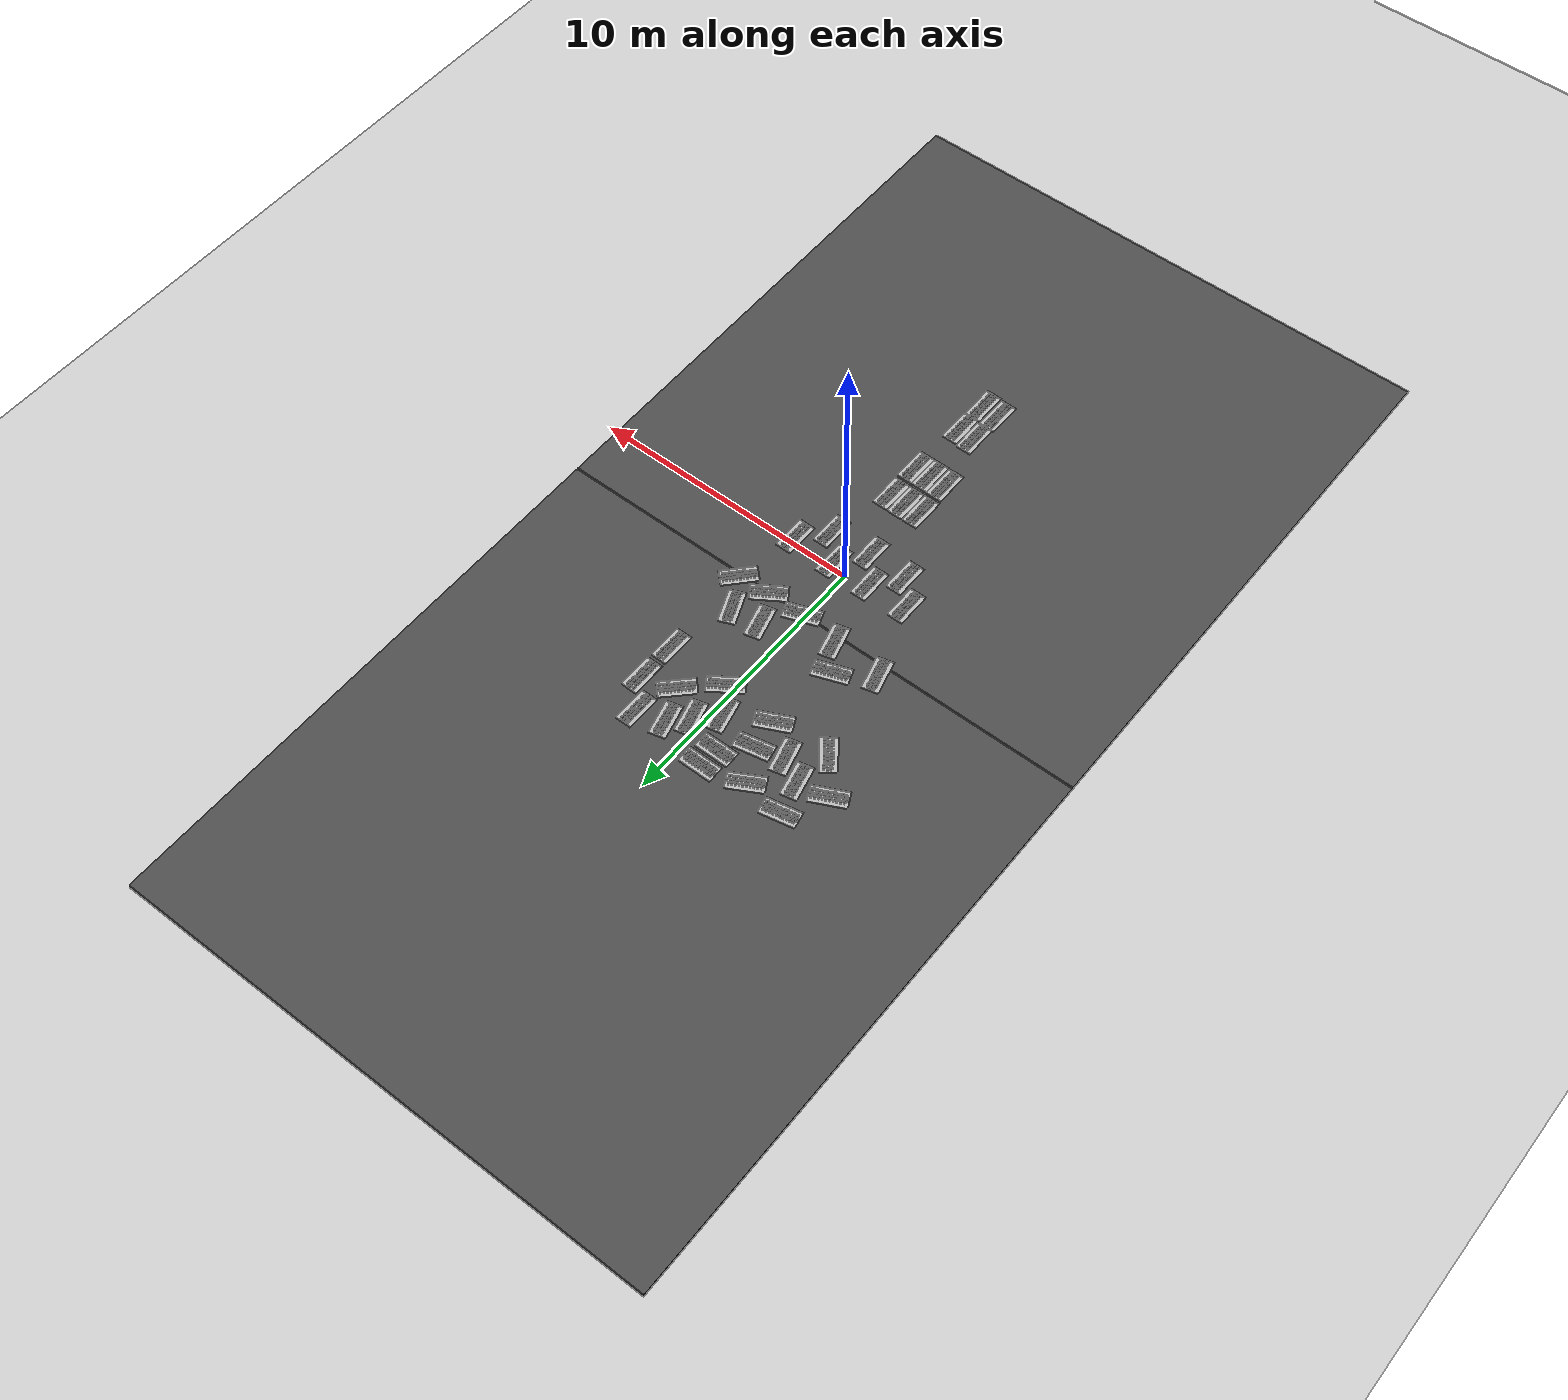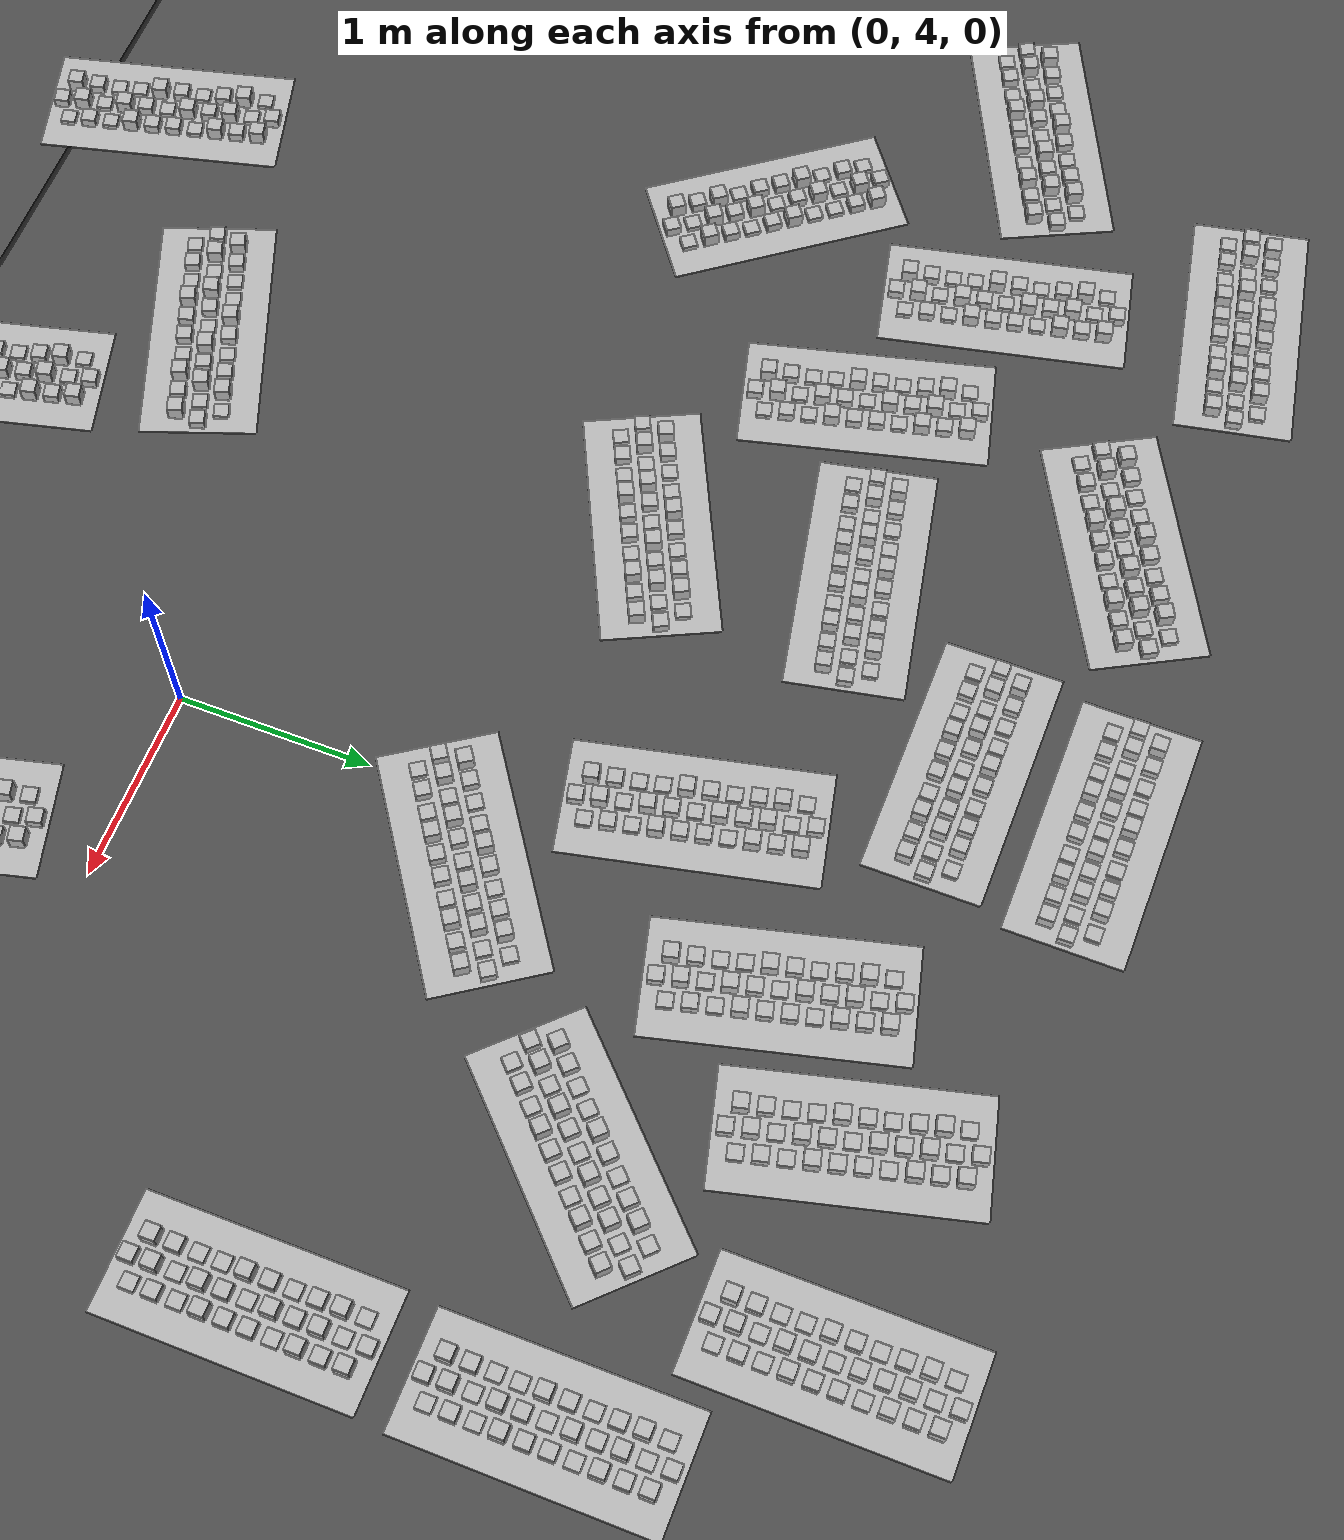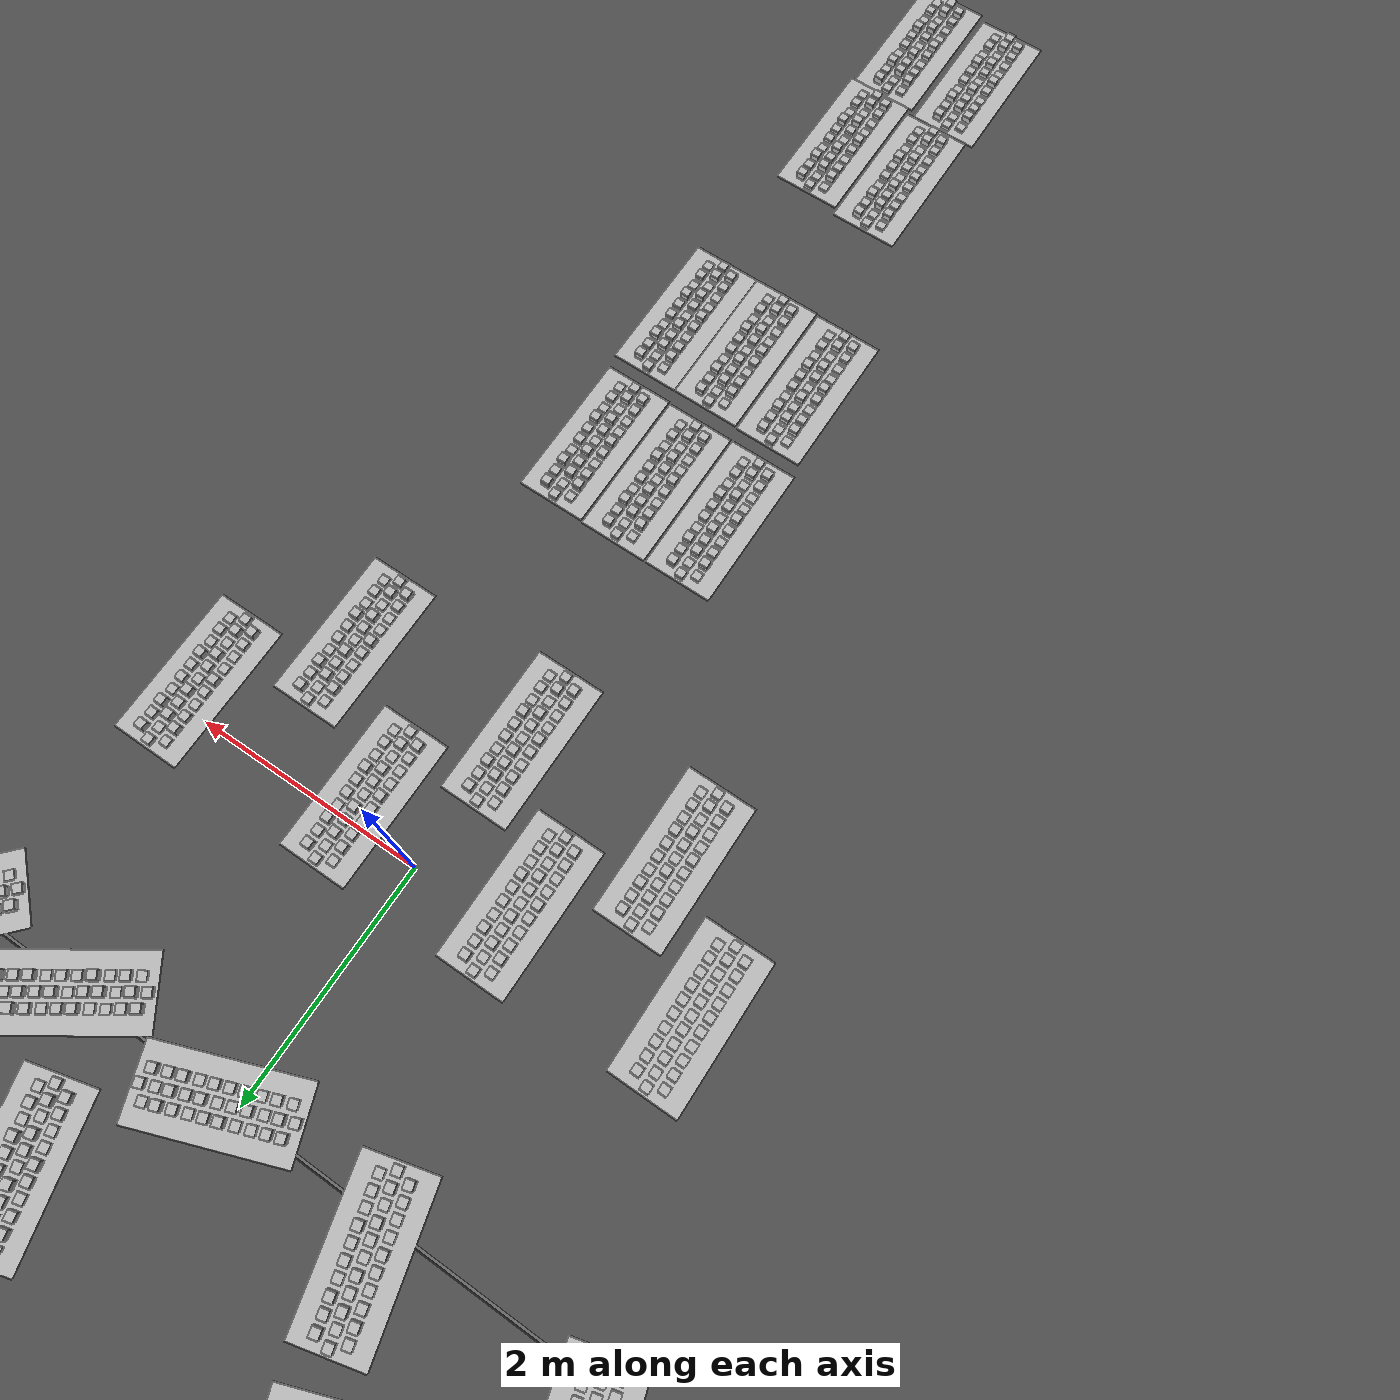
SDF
<sdf version="1.6">
 <world name="default">
  <light name="sun" type="directional">
   <pose>0 0 10 0 -0 0</pose>
   <diffuse>0.8 0.8 0.8 1</diffuse>
   <specular>0.2 0.2 0.2 1</specular>
   <attenuation>
    <range>1000</range>
    <constant>0.9</constant>
    <linear>0.01</linear>
    <quadratic>0.001</quadratic>
   </attenuation>
   <direction>-0.5 0.1 -0.9</direction>
  </light>
  <model name="ground_plane">
   <static>1</static>
   <link name="link">
    <collision name="collision">
     <geometry><plane><normal>0 0 1</normal><size>100 100</size></plane></geometry>
     <surface>
      <contact><collide_bitmask>65535</collide_bitmask></contact>
      <friction><ode><mu>100</mu><mu2>50</mu2></ode></friction>
     </surface>
    </collision>
    <visual name="visual">
     <cast_shadows>0</cast_shadows>
     <geometry><plane><normal>0 0 1</normal><size>100 100</size></plane></geometry>
     <material>
      <script><uri>file://media/materials/scripts/gazebo.material</uri><name>Gazebo/Grey</name></script>
     </material>
    </visual>
   </link>
  </model>
  <gravity>0 0 -9.8</gravity>
  <magnetic_field>6e-06 2.3e-05 -4.2e-05</magnetic_field>
  <atmosphere type="adiabatic"/>
  <physics name="default_physics" default="0" type="ode">
   <max_step_size>0.001</max_step_size>
   <real_time_factor>1</real_time_factor>
   <real_time_update_rate>1000</real_time_update_rate>
  </physics>
  <scene><ambient>0.4 0.4 0.4 1</ambient><background>0.7 0.7 0.7 1</background><shadows>1</shadows></scene>
  <audio><device>default</device></audio>
  <spherical_coordinates>
   <surface_model>EARTH_WGS84</surface_model>
   <latitude_deg>0</latitude_deg>
   <longitude_deg>0</longitude_deg>
   <elevation>0</elevation>
   <heading_deg>0</heading_deg>
  </spherical_coordinates>
  <model name="frc2016_roughterrain">
   <static>1</static>
   <link name="link">
    <visual name="platform">
     <pose>0 0 0.08269 0 -0 0</pose>
     <geometry><box><size>1.27 0.5969 0.003175</size></box></geometry>
    </visual>
    <collision name="platform">
     <pose>0 0 0.08269 0 -0 0</pose>
     <geometry><box><size>1.27 0.5969 0.003175</size></box></geometry>
    </collision>
    <visual name="row1_block1_sm">
     <pose>0.51435 0.1143 0.09698 0 -0 0</pose>
     <geometry><box><size>0.0762 0.0762 0.0254</size></box></geometry>
    </visual>
    <collision name="row1_block1_sm">
     <pose>0.51435 0.1143 0.09698 0 -0 0</pose>
     <geometry><box><size>0.0762 0.0762 0.0254</size></box></geometry>
    </collision>
    <visual name="row1_block2_lg">
     <pose>0.40005 0.1143 0.12238 0 -0 0</pose>
     <geometry><box><size>0.0762 0.0762 0.0762</size></box></geometry>
    </visual>
    <collision name="row1_block2_lg">
     <pose>0.40005 0.1143 0.12238 0 -0 0</pose>
     <geometry><box><size>0.0762 0.0762 0.0762</size></box></geometry>
    </collision>
    <visual name="row1_block3_md">
     <pose>0.28575 0.1143 0.10968 0 -0 0</pose>
     <geometry><box><size>0.0762 0.0762 0.0508</size></box></geometry>
    </visual>
    <collision name="row1_block3_md">
     <pose>0.28575 0.1143 0.10968 0 -0 0</pose>
     <geometry><box><size>0.0762 0.0762 0.0508</size></box></geometry>
    </collision>
    <visual name="row1_block4_sm">
     <pose>0.17145 0.1143 0.09698 0 -0 0</pose>
     <geometry><box><size>0.0762 0.0762 0.0254</size></box></geometry>
    </visual>
    <collision name="row1_block4_sm">
     <pose>0.17145 0.1143 0.09698 0 -0 0</pose>
     <geometry><box><size>0.0762 0.0762 0.0254</size></box></geometry>
    </collision>
    <visual name="row1_block5_md">
     <pose>0.05715 0.1143 0.10968 0 -0 0</pose>
     <geometry><box><size>0.0762 0.0762 0.0508</size></box></geometry>
    </visual>
    <collision name="row1_block5_md">
     <pose>0.05715 0.1143 0.10968 0 -0 0</pose>
     <geometry><box><size>0.0762 0.0762 0.0508</size></box></geometry>
    </collision>
    <visual name="row1_block6_lg">
     <pose>-0.05715 0.1143 0.12238 0 -0 0</pose>
     <geometry><box><size>0.0762 0.0762 0.0762</size></box></geometry>
    </visual>
    <collision name="row1_block6_lg">
     <pose>-0.05715 0.1143 0.12238 0 -0 0</pose>
     <geometry><box><size>0.0762 0.0762 0.0762</size></box></geometry>
    </collision>
    <visual name="row1_block7_sm">
     <pose>-0.17145 0.1143 0.09698 0 -0 0</pose>
     <geometry><box><size>0.0762 0.0762 0.0254</size></box></geometry>
    </visual>
    <collision name="row1_block7_sm">
     <pose>-0.17145 0.1143 0.09698 0 -0 0</pose>
     <geometry><box><size>0.0762 0.0762 0.0254</size></box></geometry>
    </collision>
    <visual name="row1_block8_sm">
     <pose>-0.28575 0.1143 0.09698 0 -0 0</pose>
     <geometry><box><size>0.0762 0.0762 0.0254</size></box></geometry>
    </visual>
    <collision name="row1_block8_sm">
     <pose>-0.28575 0.1143 0.09698 0 -0 0</pose>
     <geometry><box><size>0.0762 0.0762 0.0254</size></box></geometry>
    </collision>
    <visual name="row1_block9_md">
     <pose>-0.40005 0.1143 0.10968 0 -0 0</pose>
     <geometry><box><size>0.0762 0.0762 0.0508</size></box></geometry>
    </visual>
    <collision name="row1_block9_md">
     <pose>-0.40005 0.1143 0.10968 0 -0 0</pose>
     <geometry><box><size>0.0762 0.0762 0.0508</size></box></geometry>
    </collision>
    <visual name="row1_block10_lg">
     <pose>-0.51435 0.1143 0.12238 0 -0 0</pose>
     <geometry><box><size>0.0762 0.0762 0.0762</size></box></geometry>
    </visual>
    <collision name="row1_block10_lg">
     <pose>-0.51435 0.1143 0.12238 0 -0 0</pose>
     <geometry><box><size>0.0762 0.0762 0.0762</size></box></geometry>
    </collision>
    <visual name="row2_block1_md">
     <pose>0.5715 0 0.10968 0 -0 0</pose>
     <geometry><box><size>0.0762 0.0762 0.0508</size></box></geometry>
    </visual>
    <collision name="row2_block1_md">
     <pose>0.5715 0 0.10968 0 -0 0</pose>
     <geometry><box><size>0.0762 0.0762 0.0508</size></box></geometry>
    </collision>
    <visual name="row2_block2_sm">
     <pose>0.4572 0 0.09698 0 -0 0</pose>
     <geometry><box><size>0.0762 0.0762 0.0254</size></box></geometry>
    </visual>
    <collision name="row2_block2_sm">
     <pose>0.4572 0 0.09698 0 -0 0</pose>
     <geometry><box><size>0.0762 0.0762 0.0254</size></box></geometry>
    </collision>
    <visual name="row2_block3_lg">
     <pose>0.3429 0 0.12238 0 -0 0</pose>
     <geometry><box><size>0.0762 0.0762 0.0762</size></box></geometry>
    </visual>
    <collision name="row2_block3_lg">
     <pose>0.3429 0 0.12238 0 -0 0</pose>
     <geometry><box><size>0.0762 0.0762 0.0762</size></box></geometry>
    </collision>
    <visual name="row2_block4_md">
     <pose>0.2286 0 0.10968 0 -0 0</pose>
     <geometry><box><size>0.0762 0.0762 0.0508</size></box></geometry>
    </visual>
    <collision name="row2_block4_md">
     <pose>0.2286 0 0.10968 0 -0 0</pose>
     <geometry><box><size>0.0762 0.0762 0.0508</size></box></geometry>
    </collision>
    <visual name="row2_block5_lg">
     <pose>0.1143 0 0.12238 0 -0 0</pose>
     <geometry><box><size>0.0762 0.0762 0.0762</size></box></geometry>
    </visual>
    <collision name="row2_block5_lg">
     <pose>0.1143 0 0.12238 0 -0 0</pose>
     <geometry><box><size>0.0762 0.0762 0.0762</size></box></geometry>
    </collision>
    <visual name="row2_block6_sm">
     <pose>0 0 0.09698 0 -0 0</pose>
     <geometry><box><size>0.0762 0.0762 0.0254</size></box></geometry>
    </visual>
    <collision name="row2_block6_sm">
     <pose>0 0 0.09698 0 -0 0</pose>
     <geometry><box><size>0.0762 0.0762 0.0254</size></box></geometry>
    </collision>
    <visual name="row2_block7_md">
     <pose>-0.1143 0 0.10968 0 -0 0</pose>
     <geometry><box><size>0.0762 0.0762 0.0508</size></box></geometry>
    </visual>
    <collision name="row2_block7_md">
     <pose>-0.1143 0 0.10968 0 -0 0</pose>
     <geometry><box><size>0.0762 0.0762 0.0508</size></box></geometry>
    </collision>
    <visual name="row2_block8_lg">
     <pose>-0.2286 0 0.12238 0 -0 0</pose>
     <geometry><box><size>0.0762 0.0762 0.0762</size></box></geometry>
    </visual>
    <collision name="row2_block8_lg">
     <pose>-0.2286 0 0.12238 0 -0 0</pose>
     <geometry><box><size>0.0762 0.0762 0.0762</size></box></geometry>
    </collision>
    <visual name="row2_block9_sm">
     <pose>-0.3429 0 0.09698 0 -0 0</pose>
     <geometry><box><size>0.0762 0.0762 0.0254</size></box></geometry>
    </visual>
    <collision name="row2_block9_sm">
     <pose>-0.3429 0 0.09698 0 -0 0</pose>
     <geometry><box><size>0.0762 0.0762 0.0254</size></box></geometry>
    </collision>
    <visual name="row2_block10_lg">
     <pose>-0.4572 0 0.12238 0 -0 0</pose>
     <geometry><box><size>0.0762 0.0762 0.0762</size></box></geometry>
    </visual>
    <collision name="row2_block10_lg">
     <pose>-0.4572 0 0.12238 0 -0 0</pose>
     <geometry><box><size>0.0762 0.0762 0.0762</size></box></geometry>
    </collision>
    <visual name="row2_block11_md">
     <pose>-0.5715 0 0.10968 0 -0 0</pose>
     <geometry><box><size>0.0762 0.0762 0.0508</size></box></geometry>
    </visual>
    <collision name="row2_block11_md">
     <pose>-0.5715 0 0.10968 0 -0 0</pose>
     <geometry><box><size>0.0762 0.0762 0.0508</size></box></geometry>
    </collision>
    <visual name="row3_block1_lg">
     <pose>0.51435 -0.1143 0.12238 0 -0 0</pose>
     <geometry><box><size>0.0762 0.0762 0.0762</size></box></geometry>
    </visual>
    <collision name="row3_block1_lg">
     <pose>0.51435 -0.1143 0.12238 0 -0 0</pose>
     <geometry><box><size>0.0762 0.0762 0.0762</size></box></geometry>
    </collision>
    <visual name="row3_block2_md">
     <pose>0.40005 -0.1143 0.10968 0 -0 0</pose>
     <geometry><box><size>0.0762 0.0762 0.0508</size></box></geometry>
    </visual>
    <collision name="row3_block2_md">
     <pose>0.40005 -0.1143 0.10968 0 -0 0</pose>
     <geometry><box><size>0.0762 0.0762 0.0508</size></box></geometry>
    </collision>
    <visual name="row3_block3_lg">
     <pose>0.28575 -0.1143 0.12238 0 -0 0</pose>
     <geometry><box><size>0.0762 0.0762 0.0762</size></box></geometry>
    </visual>
    <collision name="row3_block3_lg">
     <pose>0.28575 -0.1143 0.12238 0 -0 0</pose>
     <geometry><box><size>0.0762 0.0762 0.0762</size></box></geometry>
    </collision>
    <visual name="row3_block4_sm">
     <pose>0.17145 -0.1143 0.09698 0 -0 0</pose>
     <geometry><box><size>0.0762 0.0762 0.0254</size></box></geometry>
    </visual>
    <collision name="row3_block4_sm">
     <pose>0.17145 -0.1143 0.09698 0 -0 0</pose>
     <geometry><box><size>0.0762 0.0762 0.0254</size></box></geometry>
    </collision>
    <visual name="row3_block5_md">
     <pose>0.05715 -0.1143 0.10968 0 -0 0</pose>
     <geometry><box><size>0.0762 0.0762 0.0508</size></box></geometry>
    </visual>
    <collision name="row3_block5_md">
     <pose>0.05715 -0.1143 0.10968 0 -0 0</pose>
     <geometry><box><size>0.0762 0.0762 0.0508</size></box></geometry>
    </collision>
    <visual name="row3_block6_md">
     <pose>-0.05715 -0.1143 0.10968 0 -0 0</pose>
     <geometry><box><size>0.0762 0.0762 0.0508</size></box></geometry>
    </visual>
    <collision name="row3_block6_md">
     <pose>-0.05715 -0.1143 0.10968 0 -0 0</pose>
     <geometry><box><size>0.0762 0.0762 0.0508</size></box></geometry>
    </collision>
    <visual name="row3_block7_lg">
     <pose>-0.17145 -0.1143 0.12238 0 -0 0</pose>
     <geometry><box><size>0.0762 0.0762 0.0762</size></box></geometry>
    </visual>
    <collision name="row3_block7_lg">
     <pose>-0.17145 -0.1143 0.12238 0 -0 0</pose>
     <geometry><box><size>0.0762 0.0762 0.0762</size></box></geometry>
    </collision>
    <visual name="row3_block8_sm">
     <pose>-0.28575 -0.1143 0.09698 0 -0 0</pose>
     <geometry><box><size>0.0762 0.0762 0.0254</size></box></geometry>
    </visual>
    <collision name="row3_block8_sm">
     <pose>-0.28575 -0.1143 0.09698 0 -0 0</pose>
     <geometry><box><size>0.0762 0.0762 0.0254</size></box></geometry>
    </collision>
    <visual name="row3_block9_md">
     <pose>-0.40005 -0.1143 0.10968 0 -0 0</pose>
     <geometry><box><size>0.0762 0.0762 0.0508</size></box></geometry>
    </visual>
    <collision name="row3_block9_md">
     <pose>-0.40005 -0.1143 0.10968 0 -0 0</pose>
     <geometry><box><size>0.0762 0.0762 0.0508</size></box></geometry>
    </collision>
    <visual name="row3_block10_sm">
     <pose>-0.51435 -0.1143 0.09698 0 -0 0</pose>
     <geometry><box><size>0.0762 0.0762 0.0254</size></box></geometry>
    </visual>
    <collision name="row3_block10_sm">
     <pose>-0.51435 -0.1143 0.09698 0 -0 0</pose>
     <geometry><box><size>0.0762 0.0762 0.0254</size></box></geometry>
    </collision>
   </link>
   <pose>0.660053 -8.48141 0 0 -0 1.57</pose>
  </model>
  <model name="frc2016_roughterrain_clone">
   <static>1</static>
   <link name="link">
    <visual name="platform">
     <pose>0 0 0.08269 0 -0 0</pose>
     <geometry><box><size>1.27 0.5969 0.003175</size></box></geometry>
    </visual>
    <collision name="platform">
     <pose>0 0 0.08269 0 -0 0</pose>
     <geometry><box><size>1.27 0.5969 0.003175</size></box></geometry>
    </collision>
    <visual name="row1_block1_sm">
     <pose>0.51435 0.1143 0.09698 0 -0 0</pose>
     <geometry><box><size>0.0762 0.0762 0.0254</size></box></geometry>
    </visual>
    <collision name="row1_block1_sm">
     <pose>0.51435 0.1143 0.09698 0 -0 0</pose>
     <geometry><box><size>0.0762 0.0762 0.0254</size></box></geometry>
    </collision>
    <visual name="row1_block2_lg">
     <pose>0.40005 0.1143 0.12238 0 -0 0</pose>
     <geometry><box><size>0.0762 0.0762 0.0762</size></box></geometry>
    </visual>
    <collision name="row1_block2_lg">
     <pose>0.40005 0.1143 0.12238 0 -0 0</pose>
     <geometry><box><size>0.0762 0.0762 0.0762</size></box></geometry>
    </collision>
    <visual name="row1_block3_md">
     <pose>0.28575 0.1143 0.10968 0 -0 0</pose>
     <geometry><box><size>0.0762 0.0762 0.0508</size></box></geometry>
    </visual>
    <collision name="row1_block3_md">
     <pose>0.28575 0.1143 0.10968 0 -0 0</pose>
     <geometry><box><size>0.0762 0.0762 0.0508</size></box></geometry>
    </collision>
    <visual name="row1_block4_sm">
     <pose>0.17145 0.1143 0.09698 0 -0 0</pose>
     <geometry><box><size>0.0762 0.0762 0.0254</size></box></geometry>
    </visual>
    <collision name="row1_block4_sm">
     <pose>0.17145 0.1143 0.09698 0 -0 0</pose>
     <geometry><box><size>0.0762 0.0762 0.0254</size></box></geometry>
    </collision>
    <visual name="row1_block5_md">
     <pose>0.05715 0.1143 0.10968 0 -0 0</pose>
     <geometry><box><size>0.0762 0.0762 0.0508</size></box></geometry>
    </visual>
    <collision name="row1_block5_md">
     <pose>0.05715 0.1143 0.10968 0 -0 0</pose>
     <geometry><box><size>0.0762 0.0762 0.0508</size></box></geometry>
    </collision>
    <visual name="row1_block6_lg">
     <pose>-0.05715 0.1143 0.12238 0 -0 0</pose>
     <geometry><box><size>0.0762 0.0762 0.0762</size></box></geometry>
    </visual>
    <collision name="row1_block6_lg">
     <pose>-0.05715 0.1143 0.12238 0 -0 0</pose>
     <geometry><box><size>0.0762 0.0762 0.0762</size></box></geometry>
    </collision>
    <visual name="row1_block7_sm">
     <pose>-0.17145 0.1143 0.09698 0 -0 0</pose>
     <geometry><box><size>0.0762 0.0762 0.0254</size></box></geometry>
    </visual>
    <collision name="row1_block7_sm">
     <pose>-0.17145 0.1143 0.09698 0 -0 0</pose>
     <geometry><box><size>0.0762 0.0762 0.0254</size></box></geometry>
    </collision>
    <visual name="row1_block8_sm">
     <pose>-0.28575 0.1143 0.09698 0 -0 0</pose>
     <geometry><box><size>0.0762 0.0762 0.0254</size></box></geometry>
    </visual>
    <collision name="row1_block8_sm">
     <pose>-0.28575 0.1143 0.09698 0 -0 0</pose>
     <geometry><box><size>0.0762 0.0762 0.0254</size></box></geometry>
    </collision>
    <visual name="row1_block9_md">
     <pose>-0.40005 0.1143 0.10968 0 -0 0</pose>
     <geometry><box><size>0.0762 0.0762 0.0508</size></box></geometry>
    </visual>
    <collision name="row1_block9_md">
     <pose>-0.40005 0.1143 0.10968 0 -0 0</pose>
     <geometry><box><size>0.0762 0.0762 0.0508</size></box></geometry>
    </collision>
    <visual name="row1_block10_lg">
     <pose>-0.51435 0.1143 0.12238 0 -0 0</pose>
     <geometry><box><size>0.0762 0.0762 0.0762</size></box></geometry>
    </visual>
    <collision name="row1_block10_lg">
     <pose>-0.51435 0.1143 0.12238 0 -0 0</pose>
     <geometry><box><size>0.0762 0.0762 0.0762</size></box></geometry>
    </collision>
    <visual name="row2_block1_md">
     <pose>0.5715 0 0.10968 0 -0 0</pose>
     <geometry><box><size>0.0762 0.0762 0.0508</size></box></geometry>
    </visual>
    <collision name="row2_block1_md">
     <pose>0.5715 0 0.10968 0 -0 0</pose>
     <geometry><box><size>0.0762 0.0762 0.0508</size></box></geometry>
    </collision>
    <visual name="row2_block2_sm">
     <pose>0.4572 0 0.09698 0 -0 0</pose>
     <geometry><box><size>0.0762 0.0762 0.0254</size></box></geometry>
    </visual>
    <collision name="row2_block2_sm">
     <pose>0.4572 0 0.09698 0 -0 0</pose>
     <geometry><box><size>0.0762 0.0762 0.0254</size></box></geometry>
    </collision>
    <visual name="row2_block3_lg">
     <pose>0.3429 0 0.12238 0 -0 0</pose>
     <geometry><box><size>0.0762 0.0762 0.0762</size></box></geometry>
    </visual>
    <collision name="row2_block3_lg">
     <pose>0.3429 0 0.12238 0 -0 0</pose>
     <geometry><box><size>0.0762 0.0762 0.0762</size></box></geometry>
    </collision>
    <visual name="row2_block4_md">
     <pose>0.2286 0 0.10968 0 -0 0</pose>
     <geometry><box><size>0.0762 0.0762 0.0508</size></box></geometry>
    </visual>
    <collision name="row2_block4_md">
     <pose>0.2286 0 0.10968 0 -0 0</pose>
     <geometry><box><size>0.0762 0.0762 0.0508</size></box></geometry>
    </collision>
    <visual name="row2_block5_lg">
     <pose>0.1143 0 0.12238 0 -0 0</pose>
     <geometry><box><size>0.0762 0.0762 0.0762</size></box></geometry>
    </visual>
    <collision name="row2_block5_lg">
     <pose>0.1143 0 0.12238 0 -0 0</pose>
     <geometry><box><size>0.0762 0.0762 0.0762</size></box></geometry>
    </collision>
    <visual name="row2_block6_sm">
     <pose>0 0 0.09698 0 -0 0</pose>
     <geometry><box><size>0.0762 0.0762 0.0254</size></box></geometry>
    </visual>
    <collision name="row2_block6_sm">
     <pose>0 0 0.09698 0 -0 0</pose>
     <geometry><box><size>0.0762 0.0762 0.0254</size></box></geometry>
    </collision>
    <visual name="row2_block7_md">
     <pose>-0.1143 0 0.10968 0 -0 0</pose>
     <geometry><box><size>0.0762 0.0762 0.0508</size></box></geometry>
    </visual>
    <collision name="row2_block7_md">
     <pose>-0.1143 0 0.10968 0 -0 0</pose>
     <geometry><box><size>0.0762 0.0762 0.0508</size></box></geometry>
    </collision>
    <visual name="row2_block8_lg">
     <pose>-0.2286 0 0.12238 0 -0 0</pose>
     <geometry><box><size>0.0762 0.0762 0.0762</size></box></geometry>
    </visual>
    <collision name="row2_block8_lg">
     <pose>-0.2286 0 0.12238 0 -0 0</pose>
     <geometry><box><size>0.0762 0.0762 0.0762</size></box></geometry>
    </collision>
    <visual name="row2_block9_sm">
     <pose>-0.3429 0 0.09698 0 -0 0</pose>
     <geometry><box><size>0.0762 0.0762 0.0254</size></box></geometry>
    </visual>
    <collision name="row2_block9_sm">
     <pose>-0.3429 0 0.09698 0 -0 0</pose>
     <geometry><box><size>0.0762 0.0762 0.0254</size></box></geometry>
    </collision>
    <visual name="row2_block10_lg">
     <pose>-0.4572 0 0.12238 0 -0 0</pose>
     <geometry><box><size>0.0762 0.0762 0.0762</size></box></geometry>
    </visual>
    <collision name="row2_block10_lg">
     <pose>-0.4572 0 0.12238 0 -0 0</pose>
     <geometry><box><size>0.0762 0.0762 0.0762</size></box></geometry>
    </collision>
    <visual name="row2_block11_md">
     <pose>-0.5715 0 0.10968 0 -0 0</pose>
     <geometry><box><size>0.0762 0.0762 0.0508</size></box></geometry>
    </visual>
    <collision name="row2_block11_md">
     <pose>-0.5715 0 0.10968 0 -0 0</pose>
     <geometry><box><size>0.0762 0.0762 0.0508</size></box></geometry>
    </collision>
    <visual name="row3_block1_lg">
     <pose>0.51435 -0.1143 0.12238 0 -0 0</pose>
     <geometry><box><size>0.0762 0.0762 0.0762</size></box></geometry>
    </visual>
    <collision name="row3_block1_lg">
     <pose>0.51435 -0.1143 0.12238 0 -0 0</pose>
     <geometry><box><size>0.0762 0.0762 0.0762</size></box></geometry>
    </collision>
    <visual name="row3_block2_md">
     <pose>0.40005 -0.1143 0.10968 0 -0 0</pose>
     <geometry><box><size>0.0762 0.0762 0.0508</size></box></geometry>
    </visual>
    <collision name="row3_block2_md">
     <pose>0.40005 -0.1143 0.10968 0 -0 0</pose>
     <geometry><box><size>0.0762 0.0762 0.0508</size></box></geometry>
    </collision>
    <visual name="row3_block3_lg">
     <pose>0.28575 -0.1143 0.12238 0 -0 0</pose>
     <geometry><box><size>0.0762 0.0762 0.0762</size></box></geometry>
    </visual>
    <collision name="row3_block3_lg">
     <pose>0.28575 -0.1143 0.12238 0 -0 0</pose>
     <geometry><box><size>0.0762 0.0762 0.0762</size></box></geometry>
    </collision>
    <visual name="row3_block4_sm">
     <pose>0.17145 -0.1143 0.09698 0 -0 0</pose>
     <geometry><box><size>0.0762 0.0762 0.0254</size></box></geometry>
    </visual>
    <collision name="row3_block4_sm">
     <pose>0.17145 -0.1143 0.09698 0 -0 0</pose>
     <geometry><box><size>0.0762 0.0762 0.0254</size></box></geometry>
    </collision>
    <visual name="row3_block5_md">
     <pose>0.05715 -0.1143 0.10968 0 -0 0</pose>
     <geometry><box><size>0.0762 0.0762 0.0508</size></box></geometry>
    </visual>
    <collision name="row3_block5_md">
     <pose>0.05715 -0.1143 0.10968 0 -0 0</pose>
     <geometry><box><size>0.0762 0.0762 0.0508</size></box></geometry>
    </collision>
    <visual name="row3_block6_md">
     <pose>-0.05715 -0.1143 0.10968 0 -0 0</pose>
     <geometry><box><size>0.0762 0.0762 0.0508</size></box></geometry>
    </visual>
    <collision name="row3_block6_md">
     <pose>-0.05715 -0.1143 0.10968 0 -0 0</pose>
     <geometry><box><size>0.0762 0.0762 0.0508</size></box></geometry>
    </collision>
    <visual name="row3_block7_lg">
     <pose>-0.17145 -0.1143 0.12238 0 -0 0</pose>
     <geometry><box><size>0.0762 0.0762 0.0762</size></box></geometry>
    </visual>
    <collision name="row3_block7_lg">
     <pose>-0.17145 -0.1143 0.12238 0 -0 0</pose>
     <geometry><box><size>0.0762 0.0762 0.0762</size></box></geometry>
    </collision>
    <visual name="row3_block8_sm">
     <pose>-0.28575 -0.1143 0.09698 0 -0 0</pose>
     <geometry><box><size>0.0762 0.0762 0.0254</size></box></geometry>
    </visual>
    <collision name="row3_block8_sm">
     <pose>-0.28575 -0.1143 0.09698 0 -0 0</pose>
     <geometry><box><size>0.0762 0.0762 0.0254</size></box></geometry>
    </collision>
    <visual name="row3_block9_md">
     <pose>-0.40005 -0.1143 0.10968 0 -0 0</pose>
     <geometry><box><size>0.0762 0.0762 0.0508</size></box></geometry>
    </visual>
    <collision name="row3_block9_md">
     <pose>-0.40005 -0.1143 0.10968 0 -0 0</pose>
     <geometry><box><size>0.0762 0.0762 0.0508</size></box></geometry>
    </collision>
    <visual name="row3_block10_sm">
     <pose>-0.51435 -0.1143 0.09698 0 -0 0</pose>
     <geometry><box><size>0.0762 0.0762 0.0254</size></box></geometry>
    </visual>
    <collision name="row3_block10_sm">
     <pose>-0.51435 -0.1143 0.09698 0 -0 0</pose>
     <geometry><box><size>0.0762 0.0762 0.0254</size></box></geometry>
    </collision>
   </link>
   <pose>0.695706 -7.2199 0 0 -0 1.57</pose>
  </model>
  <model name="frc2016_roughterrain_clone_0">
   <static>1</static>
   <link name="link">
    <visual name="platform">
     <pose>0 0 0.08269 0 -0 0</pose>
     <geometry><box><size>1.27 0.5969 0.003175</size></box></geometry>
    </visual>
    <collision name="platform">
     <pose>0 0 0.08269 0 -0 0</pose>
     <geometry><box><size>1.27 0.5969 0.003175</size></box></geometry>
    </collision>
    <visual name="row1_block1_sm">
     <pose>0.51435 0.1143 0.09698 0 -0 0</pose>
     <geometry><box><size>0.0762 0.0762 0.0254</size></box></geometry>
    </visual>
    <collision name="row1_block1_sm">
     <pose>0.51435 0.1143 0.09698 0 -0 0</pose>
     <geometry><box><size>0.0762 0.0762 0.0254</size></box></geometry>
    </collision>
    <visual name="row1_block2_lg">
     <pose>0.40005 0.1143 0.12238 0 -0 0</pose>
     <geometry><box><size>0.0762 0.0762 0.0762</size></box></geometry>
    </visual>
    <collision name="row1_block2_lg">
     <pose>0.40005 0.1143 0.12238 0 -0 0</pose>
     <geometry><box><size>0.0762 0.0762 0.0762</size></box></geometry>
    </collision>
    <visual name="row1_block3_md">
     <pose>0.28575 0.1143 0.10968 0 -0 0</pose>
     <geometry><box><size>0.0762 0.0762 0.0508</size></box></geometry>
    </visual>
    <collision name="row1_block3_md">
     <pose>0.28575 0.1143 0.10968 0 -0 0</pose>
     <geometry><box><size>0.0762 0.0762 0.0508</size></box></geometry>
    </collision>
    <visual name="row1_block4_sm">
     <pose>0.17145 0.1143 0.09698 0 -0 0</pose>
     <geometry><box><size>0.0762 0.0762 0.0254</size></box></geometry>
    </visual>
    <collision name="row1_block4_sm">
     <pose>0.17145 0.1143 0.09698 0 -0 0</pose>
     <geometry><box><size>0.0762 0.0762 0.0254</size></box></geometry>
    </collision>
    <visual name="row1_block5_md">
     <pose>0.05715 0.1143 0.10968 0 -0 0</pose>
     <geometry><box><size>0.0762 0.0762 0.0508</size></box></geometry>
    </visual>
    <collision name="row1_block5_md">
     <pose>0.05715 0.1143 0.10968 0 -0 0</pose>
     <geometry><box><size>0.0762 0.0762 0.0508</size></box></geometry>
    </collision>
    <visual name="row1_block6_lg">
     <pose>-0.05715 0.1143 0.12238 0 -0 0</pose>
     <geometry><box><size>0.0762 0.0762 0.0762</size></box></geometry>
    </visual>
    <collision name="row1_block6_lg">
     <pose>-0.05715 0.1143 0.12238 0 -0 0</pose>
     <geometry><box><size>0.0762 0.0762 0.0762</size></box></geometry>
    </collision>
    <visual name="row1_block7_sm">
     <pose>-0.17145 0.1143 0.09698 0 -0 0</pose>
     <geometry><box><size>0.0762 0.0762 0.0254</size></box></geometry>
    </visual>
    <collision name="row1_block7_sm">
     <pose>-0.17145 0.1143 0.09698 0 -0 0</pose>
     <geometry><box><size>0.0762 0.0762 0.0254</size></box></geometry>
    </collision>
    <visual name="row1_block8_sm">
     <pose>-0.28575 0.1143 0.09698 0 -0 0</pose>
     <geometry><box><size>0.0762 0.0762 0.0254</size></box></geometry>
    </visual>
    <collision name="row1_block8_sm">
     <pose>-0.28575 0.1143 0.09698 0 -0 0</pose>
     <geometry><box><size>0.0762 0.0762 0.0254</size></box></geometry>
    </collision>
    <visual name="row1_block9_md">
     <pose>-0.40005 0.1143 0.10968 0 -0 0</pose>
     <geometry><box><size>0.0762 0.0762 0.0508</size></box></geometry>
    </visual>
    <collision name="row1_block9_md">
     <pose>-0.40005 0.1143 0.10968 0 -0 0</pose>
     <geometry><box><size>0.0762 0.0762 0.0508</size></box></geometry>
    </collision>
    <visual name="row1_block10_lg">
     <pose>-0.51435 0.1143 0.12238 0 -0 0</pose>
     <geometry><box><size>0.0762 0.0762 0.0762</size></box></geometry>
    </visual>
    <collision name="row1_block10_lg">
     <pose>-0.51435 0.1143 0.12238 0 -0 0</pose>
     <geometry><box><size>0.0762 0.0762 0.0762</size></box></geometry>
    </collision>
    <visual name="row2_block1_md">
     <pose>0.5715 0 0.10968 0 -0 0</pose>
     <geometry><box><size>0.0762 0.0762 0.0508</size></box></geometry>
    </visual>
    <collision name="row2_block1_md">
     <pose>0.5715 0 0.10968 0 -0 0</pose>
     <geometry><box><size>0.0762 0.0762 0.0508</size></box></geometry>
    </collision>
    <visual name="row2_block2_sm">
     <pose>0.4572 0 0.09698 0 -0 0</pose>
     <geometry><box><size>0.0762 0.0762 0.0254</size></box></geometry>
    </visual>
    <collision name="row2_block2_sm">
     <pose>0.4572 0 0.09698 0 -0 0</pose>
     <geometry><box><size>0.0762 0.0762 0.0254</size></box></geometry>
    </collision>
    <visual name="row2_block3_lg">
     <pose>0.3429 0 0.12238 0 -0 0</pose>
     <geometry><box><size>0.0762 0.0762 0.0762</size></box></geometry>
    </visual>
    <collision name="row2_block3_lg">
     <pose>0.3429 0 0.12238 0 -0 0</pose>
     <geometry><box><size>0.0762 0.0762 0.0762</size></box></geometry>
    </collision>
    <visual name="row2_block4_md">
     <pose>0.2286 0 0.10968 0 -0 0</pose>
     <geometry><box><size>0.0762 0.0762 0.0508</size></box></geometry>
    </visual>
    <collision name="row2_block4_md">
     <pose>0.2286 0 0.10968 0 -0 0</pose>
     <geometry><box><size>0.0762 0.0762 0.0508</size></box></geometry>
    </collision>
    <visual name="row2_block5_lg">
     <pose>0.1143 0 0.12238 0 -0 0</pose>
     <geometry><box><size>0.0762 0.0762 0.0762</size></box></geometry>
    </visual>
    <collision name="row2_block5_lg">
     <pose>0.1143 0 0.12238 0 -0 0</pose>
     <geometry><box><size>0.0762 0.0762 0.0762</size></box></geometry>
    </collision>
    <visual name="row2_block6_sm">
     <pose>0 0 0.09698 0 -0 0</pose>
     <geometry><box><size>0.0762 0.0762 0.0254</size></box></geometry>
    </visual>
    <collision name="row2_block6_sm">
     <pose>0 0 0.09698 0 -0 0</pose>
     <geometry><box><size>0.0762 0.0762 0.0254</size></box></geometry>
    </collision>
    <visual name="row2_block7_md">
     <pose>-0.1143 0 0.10968 0 -0 0</pose>
     <geometry><box><size>0.0762 0.0762 0.0508</size></box></geometry>
    </visual>
    <collision name="row2_block7_md">
     <pose>-0.1143 0 0.10968 0 -0 0</pose>
     <geometry><box><size>0.0762 0.0762 0.0508</size></box></geometry>
    </collision>
    <visual name="row2_block8_lg">
     <pose>-0.2286 0 0.12238 0 -0 0</pose>
     <geometry><box><size>0.0762 0.0762 0.0762</size></box></geometry>
    </visual>
    <collision name="row2_block8_lg">
     <pose>-0.2286 0 0.12238 0 -0 0</pose>
     <geometry><box><size>0.0762 0.0762 0.0762</size></box></geometry>
    </collision>
    <visual name="row2_block9_sm">
     <pose>-0.3429 0 0.09698 0 -0 0</pose>
     <geometry><box><size>0.0762 0.0762 0.0254</size></box></geometry>
    </visual>
    <collision name="row2_block9_sm">
     <pose>-0.3429 0 0.09698 0 -0 0</pose>
     <geometry><box><size>0.0762 0.0762 0.0254</size></box></geometry>
    </collision>
    <visual name="row2_block10_lg">
     <pose>-0.4572 0 0.12238 0 -0 0</pose>
     <geometry><box><size>0.0762 0.0762 0.0762</size></box></geometry>
    </visual>
    <collision name="row2_block10_lg">
     <pose>-0.4572 0 0.12238 0 -0 0</pose>
     <geometry><box><size>0.0762 0.0762 0.0762</size></box></geometry>
    </collision>
    <visual name="row2_block11_md">
     <pose>-0.5715 0 0.10968 0 -0 0</pose>
     <geometry><box><size>0.0762 0.0762 0.0508</size></box></geometry>
    </visual>
    <collision name="row2_block11_md">
     <pose>-0.5715 0 0.10968 0 -0 0</pose>
     <geometry><box><size>0.0762 0.0762 0.0508</size></box></geometry>
    </collision>
    <visual name="row3_block1_lg">
     <pose>0.51435 -0.1143 0.12238 0 -0 0</pose>
     <geometry><box><size>0.0762 0.0762 0.0762</size></box></geometry>
    </visual>
    <collision name="row3_block1_lg">
     <pose>0.51435 -0.1143 0.12238 0 -0 0</pose>
     <geometry><box><size>0.0762 0.0762 0.0762</size></box></geometry>
    </collision>
    <visual name="row3_block2_md">
     <pose>0.40005 -0.1143 0.10968 0 -0 0</pose>
     <geometry><box><size>0.0762 0.0762 0.0508</size></box></geometry>
    </visual>
    <collision name="row3_block2_md">
     <pose>0.40005 -0.1143 0.10968 0 -0 0</pose>
     <geometry><box><size>0.0762 0.0762 0.0508</size></box></geometry>
    </collision>
    <visual name="row3_block3_lg">
     <pose>0.28575 -0.1143 0.12238 0 -0 0</pose>
     <geometry><box><size>0.0762 0.0762 0.0762</size></box></geometry>
    </visual>
    <collision name="row3_block3_lg">
     <pose>0.28575 -0.1143 0.12238 0 -0 0</pose>
     <geometry><box><size>0.0762 0.0762 0.0762</size></box></geometry>
    </collision>
    <visual name="row3_block4_sm">
     <pose>0.17145 -0.1143 0.09698 0 -0 0</pose>
     <geometry><box><size>0.0762 0.0762 0.0254</size></box></geometry>
    </visual>
    <collision name="row3_block4_sm">
     <pose>0.17145 -0.1143 0.09698 0 -0 0</pose>
     <geometry><box><size>0.0762 0.0762 0.0254</size></box></geometry>
    </collision>
    <visual name="row3_block5_md">
     <pose>0.05715 -0.1143 0.10968 0 -0 0</pose>
     <geometry><box><size>0.0762 0.0762 0.0508</size></box></geometry>
    </visual>
    <collision name="row3_block5_md">
     <pose>0.05715 -0.1143 0.10968 0 -0 0</pose>
     <geometry><box><size>0.0762 0.0762 0.0508</size></box></geometry>
    </collision>
    <visual name="row3_block6_md">
     <pose>-0.05715 -0.1143 0.10968 0 -0 0</pose>
     <geometry><box><size>0.0762 0.0762 0.0508</size></box></geometry>
    </visual>
    <collision name="row3_block6_md">
     <pose>-0.05715 -0.1143 0.10968 0 -0 0</pose>
     <geometry><box><size>0.0762 0.0762 0.0508</size></box></geometry>
    </collision>
    <visual name="row3_block7_lg">
     <pose>-0.17145 -0.1143 0.12238 0 -0 0</pose>
     <geometry><box><size>0.0762 0.0762 0.0762</size></box></geometry>
    </visual>
    <collision name="row3_block7_lg">
     <pose>-0.17145 -0.1143 0.12238 0 -0 0</pose>
     <geometry><box><size>0.0762 0.0762 0.0762</size></box></geometry>
    </collision>
    <visual name="row3_block8_sm">
     <pose>-0.28575 -0.1143 0.09698 0 -0 0</pose>
     <geometry><box><size>0.0762 0.0762 0.0254</size></box></geometry>
    </visual>
    <collision name="row3_block8_sm">
     <pose>-0.28575 -0.1143 0.09698 0 -0 0</pose>
     <geometry><box><size>0.0762 0.0762 0.0254</size></box></geometry>
    </collision>
    <visual name="row3_block9_md">
     <pose>-0.40005 -0.1143 0.10968 0 -0 0</pose>
     <geometry><box><size>0.0762 0.0762 0.0508</size></box></geometry>
    </visual>
    <collision name="row3_block9_md">
     <pose>-0.40005 -0.1143 0.10968 0 -0 0</pose>
     <geometry><box><size>0.0762 0.0762 0.0508</size></box></geometry>
    </collision>
    <visual name="row3_block10_sm">
     <pose>-0.51435 -0.1143 0.09698 0 -0 0</pose>
     <geometry><box><size>0.0762 0.0762 0.0254</size></box></geometry>
    </visual>
    <collision name="row3_block10_sm">
     <pose>-0.51435 -0.1143 0.09698 0 -0 0</pose>
     <geometry><box><size>0.0762 0.0762 0.0254</size></box></geometry>
    </collision>
   </link>
   <pose>0.014727 -8.43054 0 0 -0 1.57</pose>
  </model>
  <model name="frc2016_roughterrain_clone_1">
   <static>1</static>
   <link name="link">
    <visual name="platform">
     <pose>0 0 0.08269 0 -0 0</pose>
     <geometry><box><size>1.27 0.5969 0.003175</size></box></geometry>
    </visual>
    <collision name="platform">
     <pose>0 0 0.08269 0 -0 0</pose>
     <geometry><box><size>1.27 0.5969 0.003175</size></box></geometry>
    </collision>
    <visual name="row1_block1_sm">
     <pose>0.51435 0.1143 0.09698 0 -0 0</pose>
     <geometry><box><size>0.0762 0.0762 0.0254</size></box></geometry>
    </visual>
    <collision name="row1_block1_sm">
     <pose>0.51435 0.1143 0.09698 0 -0 0</pose>
     <geometry><box><size>0.0762 0.0762 0.0254</size></box></geometry>
    </collision>
    <visual name="row1_block2_lg">
     <pose>0.40005 0.1143 0.12238 0 -0 0</pose>
     <geometry><box><size>0.0762 0.0762 0.0762</size></box></geometry>
    </visual>
    <collision name="row1_block2_lg">
     <pose>0.40005 0.1143 0.12238 0 -0 0</pose>
     <geometry><box><size>0.0762 0.0762 0.0762</size></box></geometry>
    </collision>
    <visual name="row1_block3_md">
     <pose>0.28575 0.1143 0.10968 0 -0 0</pose>
     <geometry><box><size>0.0762 0.0762 0.0508</size></box></geometry>
    </visual>
    <collision name="row1_block3_md">
     <pose>0.28575 0.1143 0.10968 0 -0 0</pose>
     <geometry><box><size>0.0762 0.0762 0.0508</size></box></geometry>
    </collision>
    <visual name="row1_block4_sm">
     <pose>0.17145 0.1143 0.09698 0 -0 0</pose>
     <geometry><box><size>0.0762 0.0762 0.0254</size></box></geometry>
    </visual>
    <collision name="row1_block4_sm">
     <pose>0.17145 0.1143 0.09698 0 -0 0</pose>
     <geometry><box><size>0.0762 0.0762 0.0254</size></box></geometry>
    </collision>
    <visual name="row1_block5_md">
     <pose>0.05715 0.1143 0.10968 0 -0 0</pose>
     <geometry><box><size>0.0762 0.0762 0.0508</size></box></geometry>
    </visual>
    <collision name="row1_block5_md">
     <pose>0.05715 0.1143 0.10968 0 -0 0</pose>
     <geometry><box><size>0.0762 0.0762 0.0508</size></box></geometry>
    </collision>
    <visual name="row1_block6_lg">
     <pose>-0.05715 0.1143 0.12238 0 -0 0</pose>
     <geometry><box><size>0.0762 0.0762 0.0762</size></box></geometry>
    </visual>
    <collision name="row1_block6_lg">
     <pose>-0.05715 0.1143 0.12238 0 -0 0</pose>
     <geometry><box><size>0.0762 0.0762 0.0762</size></box></geometry>
    </collision>
    <visual name="row1_block7_sm">
     <pose>-0.17145 0.1143 0.09698 0 -0 0</pose>
     <geometry><box><size>0.0762 0.0762 0.0254</size></box></geometry>
    </visual>
    <collision name="row1_block7_sm">
     <pose>-0.17145 0.1143 0.09698 0 -0 0</pose>
     <geometry><box><size>0.0762 0.0762 0.0254</size></box></geometry>
    </collision>
    <visual name="row1_block8_sm">
     <pose>-0.28575 0.1143 0.09698 0 -0 0</pose>
     <geometry><box><size>0.0762 0.0762 0.0254</size></box></geometry>
    </visual>
    <collision name="row1_block8_sm">
     <pose>-0.28575 0.1143 0.09698 0 -0 0</pose>
     <geometry><box><size>0.0762 0.0762 0.0254</size></box></geometry>
    </collision>
    <visual name="row1_block9_md">
     <pose>-0.40005 0.1143 0.10968 0 -0 0</pose>
     <geometry><box><size>0.0762 0.0762 0.0508</size></box></geometry>
    </visual>
    <collision name="row1_block9_md">
     <pose>-0.40005 0.1143 0.10968 0 -0 0</pose>
     <geometry><box><size>0.0762 0.0762 0.0508</size></box></geometry>
    </collision>
    <visual name="row1_block10_lg">
     <pose>-0.51435 0.1143 0.12238 0 -0 0</pose>
     <geometry><box><size>0.0762 0.0762 0.0762</size></box></geometry>
    </visual>
    <collision name="row1_block10_lg">
     <pose>-0.51435 0.1143 0.12238 0 -0 0</pose>
     <geometry><box><size>0.0762 0.0762 0.0762</size></box></geometry>
    </collision>
    <visual name="row2_block1_md">
     <pose>0.5715 0 0.10968 0 -0 0</pose>
     <geometry><box><size>0.0762 0.0762 0.0508</size></box></geometry>
    </visual>
    <collision name="row2_block1_md">
     <pose>0.5715 0 0.10968 0 -0 0</pose>
     <geometry><box><size>0.0762 0.0762 0.0508</size></box></geometry>
    </collision>
    <visual name="row2_block2_sm">
     <pose>0.4572 0 0.09698 0 -0 0</pose>
     <geometry><box><size>0.0762 0.0762 0.0254</size></box></geometry>
    </visual>
    <collision name="row2_block2_sm">
     <pose>0.4572 0 0.09698 0 -0 0</pose>
     <geometry><box><size>0.0762 0.0762 0.0254</size></box></geometry>
    </collision>
    <visual name="row2_block3_lg">
     <pose>0.3429 0 0.12238 0 -0 0</pose>
     <geometry><box><size>0.0762 0.0762 0.0762</size></box></geometry>
    </visual>
    <collision name="row2_block3_lg">
     <pose>0.3429 0 0.12238 0 -0 0</pose>
     <geometry><box><size>0.0762 0.0762 0.0762</size></box></geometry>
    </collision>
    <visual name="row2_block4_md">
     <pose>0.2286 0 0.10968 0 -0 0</pose>
     <geometry><box><size>0.0762 0.0762 0.0508</size></box></geometry>
    </visual>
    <collision name="row2_block4_md">
     <pose>0.2286 0 0.10968 0 -0 0</pose>
     <geometry><box><size>0.0762 0.0762 0.0508</size></box></geometry>
    </collision>
    <visual name="row2_block5_lg">
     <pose>0.1143 0 0.12238 0 -0 0</pose>
     <geometry><box><size>0.0762 0.0762 0.0762</size></box></geometry>
    </visual>
    <collision name="row2_block5_lg">
     <pose>0.1143 0 0.12238 0 -0 0</pose>
     <geometry><box><size>0.0762 0.0762 0.0762</size></box></geometry>
    </collision>
    <visual name="row2_block6_sm">
     <pose>0 0 0.09698 0 -0 0</pose>
     <geometry><box><size>0.0762 0.0762 0.0254</size></box></geometry>
    </visual>
    <collision name="row2_block6_sm">
     <pose>0 0 0.09698 0 -0 0</pose>
     <geometry><box><size>0.0762 0.0762 0.0254</size></box></geometry>
    </collision>
    <visual name="row2_block7_md">
     <pose>-0.1143 0 0.10968 0 -0 0</pose>
     <geometry><box><size>0.0762 0.0762 0.0508</size></box></geometry>
    </visual>
    <collision name="row2_block7_md">
     <pose>-0.1143 0 0.10968 0 -0 0</pose>
     <geometry><box><size>0.0762 0.0762 0.0508</size></box></geometry>
    </collision>
    <visual name="row2_block8_lg">
     <pose>-0.2286 0 0.12238 0 -0 0</pose>
     <geometry><box><size>0.0762 0.0762 0.0762</size></box></geometry>
    </visual>
    <collision name="row2_block8_lg">
     <pose>-0.2286 0 0.12238 0 -0 0</pose>
     <geometry><box><size>0.0762 0.0762 0.0762</size></box></geometry>
    </collision>
    <visual name="row2_block9_sm">
     <pose>-0.3429 0 0.09698 0 -0 0</pose>
     <geometry><box><size>0.0762 0.0762 0.0254</size></box></geometry>
    </visual>
    <collision name="row2_block9_sm">
     <pose>-0.3429 0 0.09698 0 -0 0</pose>
     <geometry><box><size>0.0762 0.0762 0.0254</size></box></geometry>
    </collision>
    <visual name="row2_block10_lg">
     <pose>-0.4572 0 0.12238 0 -0 0</pose>
     <geometry><box><size>0.0762 0.0762 0.0762</size></box></geometry>
    </visual>
    <collision name="row2_block10_lg">
     <pose>-0.4572 0 0.12238 0 -0 0</pose>
     <geometry><box><size>0.0762 0.0762 0.0762</size></box></geometry>
    </collision>
    <visual name="row2_block11_md">
     <pose>-0.5715 0 0.10968 0 -0 0</pose>
     <geometry><box><size>0.0762 0.0762 0.0508</size></box></geometry>
    </visual>
    <collision name="row2_block11_md">
     <pose>-0.5715 0 0.10968 0 -0 0</pose>
     <geometry><box><size>0.0762 0.0762 0.0508</size></box></geometry>
    </collision>
    <visual name="row3_block1_lg">
     <pose>0.51435 -0.1143 0.12238 0 -0 0</pose>
     <geometry><box><size>0.0762 0.0762 0.0762</size></box></geometry>
    </visual>
    <collision name="row3_block1_lg">
     <pose>0.51435 -0.1143 0.12238 0 -0 0</pose>
     <geometry><box><size>0.0762 0.0762 0.0762</size></box></geometry>
    </collision>
    <visual name="row3_block2_md">
     <pose>0.40005 -0.1143 0.10968 0 -0 0</pose>
     <geometry><box><size>0.0762 0.0762 0.0508</size></box></geometry>
    </visual>
    <collision name="row3_block2_md">
     <pose>0.40005 -0.1143 0.10968 0 -0 0</pose>
     <geometry><box><size>0.0762 0.0762 0.0508</size></box></geometry>
    </collision>
    <visual name="row3_block3_lg">
     <pose>0.28575 -0.1143 0.12238 0 -0 0</pose>
     <geometry><box><size>0.0762 0.0762 0.0762</size></box></geometry>
    </visual>
    <collision name="row3_block3_lg">
     <pose>0.28575 -0.1143 0.12238 0 -0 0</pose>
     <geometry><box><size>0.0762 0.0762 0.0762</size></box></geometry>
    </collision>
    <visual name="row3_block4_sm">
     <pose>0.17145 -0.1143 0.09698 0 -0 0</pose>
     <geometry><box><size>0.0762 0.0762 0.0254</size></box></geometry>
    </visual>
    <collision name="row3_block4_sm">
     <pose>0.17145 -0.1143 0.09698 0 -0 0</pose>
     <geometry><box><size>0.0762 0.0762 0.0254</size></box></geometry>
    </collision>
    <visual name="row3_block5_md">
     <pose>0.05715 -0.1143 0.10968 0 -0 0</pose>
     <geometry><box><size>0.0762 0.0762 0.0508</size></box></geometry>
    </visual>
    <collision name="row3_block5_md">
     <pose>0.05715 -0.1143 0.10968 0 -0 0</pose>
     <geometry><box><size>0.0762 0.0762 0.0508</size></box></geometry>
    </collision>
    <visual name="row3_block6_md">
     <pose>-0.05715 -0.1143 0.10968 0 -0 0</pose>
     <geometry><box><size>0.0762 0.0762 0.0508</size></box></geometry>
    </visual>
    <collision name="row3_block6_md">
     <pose>-0.05715 -0.1143 0.10968 0 -0 0</pose>
     <geometry><box><size>0.0762 0.0762 0.0508</size></box></geometry>
    </collision>
    <visual name="row3_block7_lg">
     <pose>-0.17145 -0.1143 0.12238 0 -0 0</pose>
     <geometry><box><size>0.0762 0.0762 0.0762</size></box></geometry>
    </visual>
    <collision name="row3_block7_lg">
     <pose>-0.17145 -0.1143 0.12238 0 -0 0</pose>
     <geometry><box><size>0.0762 0.0762 0.0762</size></box></geometry>
    </collision>
    <visual name="row3_block8_sm">
     <pose>-0.28575 -0.1143 0.09698 0 -0 0</pose>
     <geometry><box><size>0.0762 0.0762 0.0254</size></box></geometry>
    </visual>
    <collision name="row3_block8_sm">
     <pose>-0.28575 -0.1143 0.09698 0 -0 0</pose>
     <geometry><box><size>0.0762 0.0762 0.0254</size></box></geometry>
    </collision>
    <visual name="row3_block9_md">
     <pose>-0.40005 -0.1143 0.10968 0 -0 0</pose>
     <geometry><box><size>0.0762 0.0762 0.0508</size></box></geometry>
    </visual>
    <collision name="row3_block9_md">
     <pose>-0.40005 -0.1143 0.10968 0 -0 0</pose>
     <geometry><box><size>0.0762 0.0762 0.0508</size></box></geometry>
    </collision>
    <visual name="row3_block10_sm">
     <pose>-0.51435 -0.1143 0.09698 0 -0 0</pose>
     <geometry><box><size>0.0762 0.0762 0.0254</size></box></geometry>
    </visual>
    <collision name="row3_block10_sm">
     <pose>-0.51435 -0.1143 0.09698 0 -0 0</pose>
     <geometry><box><size>0.0762 0.0762 0.0254</size></box></geometry>
    </collision>
   </link>
   <pose>0.078563 -7.15316 0 0 -0 1.57</pose>
  </model>
  <model name="frc2016_roughterrain_clone_clone">
   <static>1</static>
   <link name="link">
    <visual name="platform">
     <pose>0 0 0.08269 0 -0 0</pose>
     <geometry><box><size>1.27 0.5969 0.003175</size></box></geometry>
    </visual>
    <collision name="platform">
     <pose>0 0 0.08269 0 -0 0</pose>
     <geometry><box><size>1.27 0.5969 0.003175</size></box></geometry>
    </collision>
    <visual name="row1_block1_sm">
     <pose>0.51435 0.1143 0.09698 0 -0 0</pose>
     <geometry><box><size>0.0762 0.0762 0.0254</size></box></geometry>
    </visual>
    <collision name="row1_block1_sm">
     <pose>0.51435 0.1143 0.09698 0 -0 0</pose>
     <geometry><box><size>0.0762 0.0762 0.0254</size></box></geometry>
    </collision>
    <visual name="row1_block2_lg">
     <pose>0.40005 0.1143 0.12238 0 -0 0</pose>
     <geometry><box><size>0.0762 0.0762 0.0762</size></box></geometry>
    </visual>
    <collision name="row1_block2_lg">
     <pose>0.40005 0.1143 0.12238 0 -0 0</pose>
     <geometry><box><size>0.0762 0.0762 0.0762</size></box></geometry>
    </collision>
    <visual name="row1_block3_md">
     <pose>0.28575 0.1143 0.10968 0 -0 0</pose>
     <geometry><box><size>0.0762 0.0762 0.0508</size></box></geometry>
    </visual>
    <collision name="row1_block3_md">
     <pose>0.28575 0.1143 0.10968 0 -0 0</pose>
     <geometry><box><size>0.0762 0.0762 0.0508</size></box></geometry>
    </collision>
    <visual name="row1_block4_sm">
     <pose>0.17145 0.1143 0.09698 0 -0 0</pose>
     <geometry><box><size>0.0762 0.0762 0.0254</size></box></geometry>
    </visual>
    <collision name="row1_block4_sm">
     <pose>0.17145 0.1143 0.09698 0 -0 0</pose>
     <geometry><box><size>0.0762 0.0762 0.0254</size></box></geometry>
    </collision>
    <visual name="row1_block5_md">
     <pose>0.05715 0.1143 0.10968 0 -0 0</pose>
     <geometry><box><size>0.0762 0.0762 0.0508</size></box></geometry>
    </visual>
    <collision name="row1_block5_md">
     <pose>0.05715 0.1143 0.10968 0 -0 0</pose>
     <geometry><box><size>0.0762 0.0762 0.0508</size></box></geometry>
    </collision>
    <visual name="row1_block6_lg">
     <pose>-0.05715 0.1143 0.12238 0 -0 0</pose>
     <geometry><box><size>0.0762 0.0762 0.0762</size></box></geometry>
    </visual>
    <collision name="row1_block6_lg">
     <pose>-0.05715 0.1143 0.12238 0 -0 0</pose>
     <geometry><box><size>0.0762 0.0762 0.0762</size></box></geometry>
    </collision>
    <visual name="row1_block7_sm">
     <pose>-0.17145 0.1143 0.09698 0 -0 0</pose>
     <geometry><box><size>0.0762 0.0762 0.0254</size></box></geometry>
    </visual>
    <collision name="row1_block7_sm">
     <pose>-0.17145 0.1143 0.09698 0 -0 0</pose>
     <geometry><box><size>0.0762 0.0762 0.0254</size></box></geometry>
    </collision>
    <visual name="row1_block8_sm">
     <pose>-0.28575 0.1143 0.09698 0 -0 0</pose>
     <geometry><box><size>0.0762 0.0762 0.0254</size></box></geometry>
    </visual>
    <collision name="row1_block8_sm">
     <pose>-0.28575 0.1143 0.09698 0 -0 0</pose>
     <geometry><box><size>0.0762 0.0762 0.0254</size></box></geometry>
    </collision>
    <visual name="row1_block9_md">
     <pose>-0.40005 0.1143 0.10968 0 -0 0</pose>
     <geometry><box><size>0.0762 0.0762 0.0508</size></box></geometry>
    </visual>
    <collision name="row1_block9_md">
     <pose>-0.40005 0.1143 0.10968 0 -0 0</pose>
     <geometry><box><size>0.0762 0.0762 0.0508</size></box></geometry>
    </collision>
    <visual name="row1_block10_lg">
     <pose>-0.51435 0.1143 0.12238 0 -0 0</pose>
     <geometry><box><size>0.0762 0.0762 0.0762</size></box></geometry>
    </visual>
    <collision name="row1_block10_lg">
     <pose>-0.51435 0.1143 0.12238 0 -0 0</pose>
     <geometry><box><size>0.0762 0.0762 0.0762</size></box></geometry>
    </collision>
    <visual name="row2_block1_md">
     <pose>0.5715 0 0.10968 0 -0 0</pose>
     <geometry><box><size>0.0762 0.0762 0.0508</size></box></geometry>
    </visual>
    <collision name="row2_block1_md">
     <pose>0.5715 0 0.10968 0 -0 0</pose>
     <geometry><box><size>0.0762 0.0762 0.0508</size></box></geometry>
    </collision>
    <visual name="row2_block2_sm">
     <pose>0.4572 0 0.09698 0 -0 0</pose>
     <geometry><box><size>0.0762 0.0762 0.0254</size></box></geometry>
    </visual>
    <collision name="row2_block2_sm">
     <pose>0.4572 0 0.09698 0 -0 0</pose>
     <geometry><box><size>0.0762 0.0762 0.0254</size></box></geometry>
    </collision>
    <visual name="row2_block3_lg">
     <pose>0.3429 0 0.12238 0 -0 0</pose>
     <geometry><box><size>0.0762 0.0762 0.0762</size></box></geometry>
    </visual>
    <collision name="row2_block3_lg">
     <pose>0.3429 0 0.12238 0 -0 0</pose>
     <geometry><box><size>0.0762 0.0762 0.0762</size></box></geometry>
    </collision>
    <visual name="row2_block4_md">
     <pose>0.2286 0 0.10968 0 -0 0</pose>
     <geometry><box><size>0.0762 0.0762 0.0508</size></box></geometry>
    </visual>
    <collision name="row2_block4_md">
     <pose>0.2286 0 0.10968 0 -0 0</pose>
     <geometry><box><size>0.0762 0.0762 0.0508</size></box></geometry>
    </collision>
    <visual name="row2_block5_lg">
     <pose>0.1143 0 0.12238 0 -0 0</pose>
     <geometry><box><size>0.0762 0.0762 0.0762</size></box></geometry>
    </visual>
    <collision name="row2_block5_lg">
     <pose>0.1143 0 0.12238 0 -0 0</pose>
     <geometry><box><size>0.0762 0.0762 0.0762</size></box></geometry>
    </collision>
    <visual name="row2_block6_sm">
     <pose>0 0 0.09698 0 -0 0</pose>
     <geometry><box><size>0.0762 0.0762 0.0254</size></box></geometry>
    </visual>
    <collision name="row2_block6_sm">
     <pose>0 0 0.09698 0 -0 0</pose>
     <geometry><box><size>0.0762 0.0762 0.0254</size></box></geometry>
    </collision>
    <visual name="row2_block7_md">
     <pose>-0.1143 0 0.10968 0 -0 0</pose>
     <geometry><box><size>0.0762 0.0762 0.0508</size></box></geometry>
    </visual>
    <collision name="row2_block7_md">
     <pose>-0.1143 0 0.10968 0 -0 0</pose>
     <geometry><box><size>0.0762 0.0762 0.0508</size></box></geometry>
    </collision>
    <visual name="row2_block8_lg">
     <pose>-0.2286 0 0.12238 0 -0 0</pose>
     <geometry><box><size>0.0762 0.0762 0.0762</size></box></geometry>
    </visual>
    <collision name="row2_block8_lg">
     <pose>-0.2286 0 0.12238 0 -0 0</pose>
     <geometry><box><size>0.0762 0.0762 0.0762</size></box></geometry>
    </collision>
    <visual name="row2_block9_sm">
     <pose>-0.3429 0 0.09698 0 -0 0</pose>
     <geometry><box><size>0.0762 0.0762 0.0254</size></box></geometry>
    </visual>
    <collision name="row2_block9_sm">
     <pose>-0.3429 0 0.09698 0 -0 0</pose>
     <geometry><box><size>0.0762 0.0762 0.0254</size></box></geometry>
    </collision>
    <visual name="row2_block10_lg">
     <pose>-0.4572 0 0.12238 0 -0 0</pose>
     <geometry><box><size>0.0762 0.0762 0.0762</size></box></geometry>
    </visual>
    <collision name="row2_block10_lg">
     <pose>-0.4572 0 0.12238 0 -0 0</pose>
     <geometry><box><size>0.0762 0.0762 0.0762</size></box></geometry>
    </collision>
    <visual name="row2_block11_md">
     <pose>-0.5715 0 0.10968 0 -0 0</pose>
     <geometry><box><size>0.0762 0.0762 0.0508</size></box></geometry>
    </visual>
    <collision name="row2_block11_md">
     <pose>-0.5715 0 0.10968 0 -0 0</pose>
     <geometry><box><size>0.0762 0.0762 0.0508</size></box></geometry>
    </collision>
    <visual name="row3_block1_lg">
     <pose>0.51435 -0.1143 0.12238 0 -0 0</pose>
     <geometry><box><size>0.0762 0.0762 0.0762</size></box></geometry>
    </visual>
    <collision name="row3_block1_lg">
     <pose>0.51435 -0.1143 0.12238 0 -0 0</pose>
     <geometry><box><size>0.0762 0.0762 0.0762</size></box></geometry>
    </collision>
    <visual name="row3_block2_md">
     <pose>0.40005 -0.1143 0.10968 0 -0 0</pose>
     <geometry><box><size>0.0762 0.0762 0.0508</size></box></geometry>
    </visual>
    <collision name="row3_block2_md">
     <pose>0.40005 -0.1143 0.10968 0 -0 0</pose>
     <geometry><box><size>0.0762 0.0762 0.0508</size></box></geometry>
    </collision>
    <visual name="row3_block3_lg">
     <pose>0.28575 -0.1143 0.12238 0 -0 0</pose>
     <geometry><box><size>0.0762 0.0762 0.0762</size></box></geometry>
    </visual>
    <collision name="row3_block3_lg">
     <pose>0.28575 -0.1143 0.12238 0 -0 0</pose>
     <geometry><box><size>0.0762 0.0762 0.0762</size></box></geometry>
    </collision>
    <visual name="row3_block4_sm">
     <pose>0.17145 -0.1143 0.09698 0 -0 0</pose>
     <geometry><box><size>0.0762 0.0762 0.0254</size></box></geometry>
    </visual>
    <collision name="row3_block4_sm">
     <pose>0.17145 -0.1143 0.09698 0 -0 0</pose>
     <geometry><box><size>0.0762 0.0762 0.0254</size></box></geometry>
    </collision>
    <visual name="row3_block5_md">
     <pose>0.05715 -0.1143 0.10968 0 -0 0</pose>
     <geometry><box><size>0.0762 0.0762 0.0508</size></box></geometry>
    </visual>
    <collision name="row3_block5_md">
     <pose>0.05715 -0.1143 0.10968 0 -0 0</pose>
     <geometry><box><size>0.0762 0.0762 0.0508</size></box></geometry>
    </collision>
    <visual name="row3_block6_md">
     <pose>-0.05715 -0.1143 0.10968 0 -0 0</pose>
     <geometry><box><size>0.0762 0.0762 0.0508</size></box></geometry>
    </visual>
    <collision name="row3_block6_md">
     <pose>-0.05715 -0.1143 0.10968 0 -0 0</pose>
     <geometry><box><size>0.0762 0.0762 0.0508</size></box></geometry>
    </collision>
    <visual name="row3_block7_lg">
     <pose>-0.17145 -0.1143 0.12238 0 -0 0</pose>
     <geometry><box><size>0.0762 0.0762 0.0762</size></box></geometry>
    </visual>
    <collision name="row3_block7_lg">
     <pose>-0.17145 -0.1143 0.12238 0 -0 0</pose>
     <geometry><box><size>0.0762 0.0762 0.0762</size></box></geometry>
    </collision>
    <visual name="row3_block8_sm">
     <pose>-0.28575 -0.1143 0.09698 0 -0 0</pose>
     <geometry><box><size>0.0762 0.0762 0.0254</size></box></geometry>
    </visual>
    <collision name="row3_block8_sm">
     <pose>-0.28575 -0.1143 0.09698 0 -0 0</pose>
     <geometry><box><size>0.0762 0.0762 0.0254</size></box></geometry>
    </collision>
    <visual name="row3_block9_md">
     <pose>-0.40005 -0.1143 0.10968 0 -0 0</pose>
     <geometry><box><size>0.0762 0.0762 0.0508</size></box></geometry>
    </visual>
    <collision name="row3_block9_md">
     <pose>-0.40005 -0.1143 0.10968 0 -0 0</pose>
     <geometry><box><size>0.0762 0.0762 0.0508</size></box></geometry>
    </collision>
    <visual name="row3_block10_sm">
     <pose>-0.51435 -0.1143 0.09698 0 -0 0</pose>
     <geometry><box><size>0.0762 0.0762 0.0254</size></box></geometry>
    </visual>
    <collision name="row3_block10_sm">
     <pose>-0.51435 -0.1143 0.09698 0 -0 0</pose>
     <geometry><box><size>0.0762 0.0762 0.0254</size></box></geometry>
    </collision>
   </link>
   <pose>0.872402 -4.95477 0 0 -0 1.57</pose>
  </model>
  <model name="frc2016_roughterrain_clone_clone_0">
   <static>1</static>
   <link name="link">
    <visual name="platform">
     <pose>0 0 0.08269 0 -0 0</pose>
     <geometry><box><size>1.27 0.5969 0.003175</size></box></geometry>
    </visual>
    <collision name="platform">
     <pose>0 0 0.08269 0 -0 0</pose>
     <geometry><box><size>1.27 0.5969 0.003175</size></box></geometry>
    </collision>
    <visual name="row1_block1_sm">
     <pose>0.51435 0.1143 0.09698 0 -0 0</pose>
     <geometry><box><size>0.0762 0.0762 0.0254</size></box></geometry>
    </visual>
    <collision name="row1_block1_sm">
     <pose>0.51435 0.1143 0.09698 0 -0 0</pose>
     <geometry><box><size>0.0762 0.0762 0.0254</size></box></geometry>
    </collision>
    <visual name="row1_block2_lg">
     <pose>0.40005 0.1143 0.12238 0 -0 0</pose>
     <geometry><box><size>0.0762 0.0762 0.0762</size></box></geometry>
    </visual>
    <collision name="row1_block2_lg">
     <pose>0.40005 0.1143 0.12238 0 -0 0</pose>
     <geometry><box><size>0.0762 0.0762 0.0762</size></box></geometry>
    </collision>
    <visual name="row1_block3_md">
     <pose>0.28575 0.1143 0.10968 0 -0 0</pose>
     <geometry><box><size>0.0762 0.0762 0.0508</size></box></geometry>
    </visual>
    <collision name="row1_block3_md">
     <pose>0.28575 0.1143 0.10968 0 -0 0</pose>
     <geometry><box><size>0.0762 0.0762 0.0508</size></box></geometry>
    </collision>
    <visual name="row1_block4_sm">
     <pose>0.17145 0.1143 0.09698 0 -0 0</pose>
     <geometry><box><size>0.0762 0.0762 0.0254</size></box></geometry>
    </visual>
    <collision name="row1_block4_sm">
     <pose>0.17145 0.1143 0.09698 0 -0 0</pose>
     <geometry><box><size>0.0762 0.0762 0.0254</size></box></geometry>
    </collision>
    <visual name="row1_block5_md">
     <pose>0.05715 0.1143 0.10968 0 -0 0</pose>
     <geometry><box><size>0.0762 0.0762 0.0508</size></box></geometry>
    </visual>
    <collision name="row1_block5_md">
     <pose>0.05715 0.1143 0.10968 0 -0 0</pose>
     <geometry><box><size>0.0762 0.0762 0.0508</size></box></geometry>
    </collision>
    <visual name="row1_block6_lg">
     <pose>-0.05715 0.1143 0.12238 0 -0 0</pose>
     <geometry><box><size>0.0762 0.0762 0.0762</size></box></geometry>
    </visual>
    <collision name="row1_block6_lg">
     <pose>-0.05715 0.1143 0.12238 0 -0 0</pose>
     <geometry><box><size>0.0762 0.0762 0.0762</size></box></geometry>
    </collision>
    <visual name="row1_block7_sm">
     <pose>-0.17145 0.1143 0.09698 0 -0 0</pose>
     <geometry><box><size>0.0762 0.0762 0.0254</size></box></geometry>
    </visual>
    <collision name="row1_block7_sm">
     <pose>-0.17145 0.1143 0.09698 0 -0 0</pose>
     <geometry><box><size>0.0762 0.0762 0.0254</size></box></geometry>
    </collision>
    <visual name="row1_block8_sm">
     <pose>-0.28575 0.1143 0.09698 0 -0 0</pose>
     <geometry><box><size>0.0762 0.0762 0.0254</size></box></geometry>
    </visual>
    <collision name="row1_block8_sm">
     <pose>-0.28575 0.1143 0.09698 0 -0 0</pose>
     <geometry><box><size>0.0762 0.0762 0.0254</size></box></geometry>
    </collision>
    <visual name="row1_block9_md">
     <pose>-0.40005 0.1143 0.10968 0 -0 0</pose>
     <geometry><box><size>0.0762 0.0762 0.0508</size></box></geometry>
    </visual>
    <collision name="row1_block9_md">
     <pose>-0.40005 0.1143 0.10968 0 -0 0</pose>
     <geometry><box><size>0.0762 0.0762 0.0508</size></box></geometry>
    </collision>
    <visual name="row1_block10_lg">
     <pose>-0.51435 0.1143 0.12238 0 -0 0</pose>
     <geometry><box><size>0.0762 0.0762 0.0762</size></box></geometry>
    </visual>
    <collision name="row1_block10_lg">
     <pose>-0.51435 0.1143 0.12238 0 -0 0</pose>
     <geometry><box><size>0.0762 0.0762 0.0762</size></box></geometry>
    </collision>
    <visual name="row2_block1_md">
     <pose>0.5715 0 0.10968 0 -0 0</pose>
     <geometry><box><size>0.0762 0.0762 0.0508</size></box></geometry>
    </visual>
    <collision name="row2_block1_md">
     <pose>0.5715 0 0.10968 0 -0 0</pose>
     <geometry><box><size>0.0762 0.0762 0.0508</size></box></geometry>
    </collision>
    <visual name="row2_block2_sm">
     <pose>0.4572 0 0.09698 0 -0 0</pose>
     <geometry><box><size>0.0762 0.0762 0.0254</size></box></geometry>
    </visual>
    <collision name="row2_block2_sm">
     <pose>0.4572 0 0.09698 0 -0 0</pose>
     <geometry><box><size>0.0762 0.0762 0.0254</size></box></geometry>
    </collision>
    <visual name="row2_block3_lg">
     <pose>0.3429 0 0.12238 0 -0 0</pose>
     <geometry><box><size>0.0762 0.0762 0.0762</size></box></geometry>
    </visual>
    <collision name="row2_block3_lg">
     <pose>0.3429 0 0.12238 0 -0 0</pose>
     <geometry><box><size>0.0762 0.0762 0.0762</size></box></geometry>
    </collision>
    <visual name="row2_block4_md">
     <pose>0.2286 0 0.10968 0 -0 0</pose>
     <geometry><box><size>0.0762 0.0762 0.0508</size></box></geometry>
    </visual>
    <collision name="row2_block4_md">
     <pose>0.2286 0 0.10968 0 -0 0</pose>
     <geometry><box><size>0.0762 0.0762 0.0508</size></box></geometry>
    </collision>
    <visual name="row2_block5_lg">
     <pose>0.1143 0 0.12238 0 -0 0</pose>
     <geometry><box><size>0.0762 0.0762 0.0762</size></box></geometry>
    </visual>
    <collision name="row2_block5_lg">
     <pose>0.1143 0 0.12238 0 -0 0</pose>
     <geometry><box><size>0.0762 0.0762 0.0762</size></box></geometry>
    </collision>
    <visual name="row2_block6_sm">
     <pose>0 0 0.09698 0 -0 0</pose>
     <geometry><box><size>0.0762 0.0762 0.0254</size></box></geometry>
    </visual>
    <collision name="row2_block6_sm">
     <pose>0 0 0.09698 0 -0 0</pose>
     <geometry><box><size>0.0762 0.0762 0.0254</size></box></geometry>
    </collision>
    <visual name="row2_block7_md">
     <pose>-0.1143 0 0.10968 0 -0 0</pose>
     <geometry><box><size>0.0762 0.0762 0.0508</size></box></geometry>
    </visual>
    <collision name="row2_block7_md">
     <pose>-0.1143 0 0.10968 0 -0 0</pose>
     <geometry><box><size>0.0762 0.0762 0.0508</size></box></geometry>
    </collision>
    <visual name="row2_block8_lg">
     <pose>-0.2286 0 0.12238 0 -0 0</pose>
     <geometry><box><size>0.0762 0.0762 0.0762</size></box></geometry>
    </visual>
    <collision name="row2_block8_lg">
     <pose>-0.2286 0 0.12238 0 -0 0</pose>
     <geometry><box><size>0.0762 0.0762 0.0762</size></box></geometry>
    </collision>
    <visual name="row2_block9_sm">
     <pose>-0.3429 0 0.09698 0 -0 0</pose>
     <geometry><box><size>0.0762 0.0762 0.0254</size></box></geometry>
    </visual>
    <collision name="row2_block9_sm">
     <pose>-0.3429 0 0.09698 0 -0 0</pose>
     <geometry><box><size>0.0762 0.0762 0.0254</size></box></geometry>
    </collision>
    <visual name="row2_block10_lg">
     <pose>-0.4572 0 0.12238 0 -0 0</pose>
     <geometry><box><size>0.0762 0.0762 0.0762</size></box></geometry>
    </visual>
    <collision name="row2_block10_lg">
     <pose>-0.4572 0 0.12238 0 -0 0</pose>
     <geometry><box><size>0.0762 0.0762 0.0762</size></box></geometry>
    </collision>
    <visual name="row2_block11_md">
     <pose>-0.5715 0 0.10968 0 -0 0</pose>
     <geometry><box><size>0.0762 0.0762 0.0508</size></box></geometry>
    </visual>
    <collision name="row2_block11_md">
     <pose>-0.5715 0 0.10968 0 -0 0</pose>
     <geometry><box><size>0.0762 0.0762 0.0508</size></box></geometry>
    </collision>
    <visual name="row3_block1_lg">
     <pose>0.51435 -0.1143 0.12238 0 -0 0</pose>
     <geometry><box><size>0.0762 0.0762 0.0762</size></box></geometry>
    </visual>
    <collision name="row3_block1_lg">
     <pose>0.51435 -0.1143 0.12238 0 -0 0</pose>
     <geometry><box><size>0.0762 0.0762 0.0762</size></box></geometry>
    </collision>
    <visual name="row3_block2_md">
     <pose>0.40005 -0.1143 0.10968 0 -0 0</pose>
     <geometry><box><size>0.0762 0.0762 0.0508</size></box></geometry>
    </visual>
    <collision name="row3_block2_md">
     <pose>0.40005 -0.1143 0.10968 0 -0 0</pose>
     <geometry><box><size>0.0762 0.0762 0.0508</size></box></geometry>
    </collision>
    <visual name="row3_block3_lg">
     <pose>0.28575 -0.1143 0.12238 0 -0 0</pose>
     <geometry><box><size>0.0762 0.0762 0.0762</size></box></geometry>
    </visual>
    <collision name="row3_block3_lg">
     <pose>0.28575 -0.1143 0.12238 0 -0 0</pose>
     <geometry><box><size>0.0762 0.0762 0.0762</size></box></geometry>
    </collision>
    <visual name="row3_block4_sm">
     <pose>0.17145 -0.1143 0.09698 0 -0 0</pose>
     <geometry><box><size>0.0762 0.0762 0.0254</size></box></geometry>
    </visual>
    <collision name="row3_block4_sm">
     <pose>0.17145 -0.1143 0.09698 0 -0 0</pose>
     <geometry><box><size>0.0762 0.0762 0.0254</size></box></geometry>
    </collision>
    <visual name="row3_block5_md">
     <pose>0.05715 -0.1143 0.10968 0 -0 0</pose>
     <geometry><box><size>0.0762 0.0762 0.0508</size></box></geometry>
    </visual>
    <collision name="row3_block5_md">
     <pose>0.05715 -0.1143 0.10968 0 -0 0</pose>
     <geometry><box><size>0.0762 0.0762 0.0508</size></box></geometry>
    </collision>
    <visual name="row3_block6_md">
     <pose>-0.05715 -0.1143 0.10968 0 -0 0</pose>
     <geometry><box><size>0.0762 0.0762 0.0508</size></box></geometry>
    </visual>
    <collision name="row3_block6_md">
     <pose>-0.05715 -0.1143 0.10968 0 -0 0</pose>
     <geometry><box><size>0.0762 0.0762 0.0508</size></box></geometry>
    </collision>
    <visual name="row3_block7_lg">
     <pose>-0.17145 -0.1143 0.12238 0 -0 0</pose>
     <geometry><box><size>0.0762 0.0762 0.0762</size></box></geometry>
    </visual>
    <collision name="row3_block7_lg">
     <pose>-0.17145 -0.1143 0.12238 0 -0 0</pose>
     <geometry><box><size>0.0762 0.0762 0.0762</size></box></geometry>
    </collision>
    <visual name="row3_block8_sm">
     <pose>-0.28575 -0.1143 0.09698 0 -0 0</pose>
     <geometry><box><size>0.0762 0.0762 0.0254</size></box></geometry>
    </visual>
    <collision name="row3_block8_sm">
     <pose>-0.28575 -0.1143 0.09698 0 -0 0</pose>
     <geometry><box><size>0.0762 0.0762 0.0254</size></box></geometry>
    </collision>
    <visual name="row3_block9_md">
     <pose>-0.40005 -0.1143 0.10968 0 -0 0</pose>
     <geometry><box><size>0.0762 0.0762 0.0508</size></box></geometry>
    </visual>
    <collision name="row3_block9_md">
     <pose>-0.40005 -0.1143 0.10968 0 -0 0</pose>
     <geometry><box><size>0.0762 0.0762 0.0508</size></box></geometry>
    </collision>
    <visual name="row3_block10_sm">
     <pose>-0.51435 -0.1143 0.09698 0 -0 0</pose>
     <geometry><box><size>0.0762 0.0762 0.0254</size></box></geometry>
    </visual>
    <collision name="row3_block10_sm">
     <pose>-0.51435 -0.1143 0.09698 0 -0 0</pose>
     <geometry><box><size>0.0762 0.0762 0.0254</size></box></geometry>
    </collision>
   </link>
   <pose>0.270678 -4.95641 0 0 -0 1.57</pose>
  </model>
  <model name="frc2016_roughterrain_clone_clone_1">
   <static>1</static>
   <link name="link">
    <visual name="platform">
     <pose>0 0 0.08269 0 -0 0</pose>
     <geometry><box><size>1.27 0.5969 0.003175</size></box></geometry>
    </visual>
    <collision name="platform">
     <pose>0 0 0.08269 0 -0 0</pose>
     <geometry><box><size>1.27 0.5969 0.003175</size></box></geometry>
    </collision>
    <visual name="row1_block1_sm">
     <pose>0.51435 0.1143 0.09698 0 -0 0</pose>
     <geometry><box><size>0.0762 0.0762 0.0254</size></box></geometry>
    </visual>
    <collision name="row1_block1_sm">
     <pose>0.51435 0.1143 0.09698 0 -0 0</pose>
     <geometry><box><size>0.0762 0.0762 0.0254</size></box></geometry>
    </collision>
    <visual name="row1_block2_lg">
     <pose>0.40005 0.1143 0.12238 0 -0 0</pose>
     <geometry><box><size>0.0762 0.0762 0.0762</size></box></geometry>
    </visual>
    <collision name="row1_block2_lg">
     <pose>0.40005 0.1143 0.12238 0 -0 0</pose>
     <geometry><box><size>0.0762 0.0762 0.0762</size></box></geometry>
    </collision>
    <visual name="row1_block3_md">
     <pose>0.28575 0.1143 0.10968 0 -0 0</pose>
     <geometry><box><size>0.0762 0.0762 0.0508</size></box></geometry>
    </visual>
    <collision name="row1_block3_md">
     <pose>0.28575 0.1143 0.10968 0 -0 0</pose>
     <geometry><box><size>0.0762 0.0762 0.0508</size></box></geometry>
    </collision>
    <visual name="row1_block4_sm">
     <pose>0.17145 0.1143 0.09698 0 -0 0</pose>
     <geometry><box><size>0.0762 0.0762 0.0254</size></box></geometry>
    </visual>
    <collision name="row1_block4_sm">
     <pose>0.17145 0.1143 0.09698 0 -0 0</pose>
     <geometry><box><size>0.0762 0.0762 0.0254</size></box></geometry>
    </collision>
    <visual name="row1_block5_md">
     <pose>0.05715 0.1143 0.10968 0 -0 0</pose>
     <geometry><box><size>0.0762 0.0762 0.0508</size></box></geometry>
    </visual>
    <collision name="row1_block5_md">
     <pose>0.05715 0.1143 0.10968 0 -0 0</pose>
     <geometry><box><size>0.0762 0.0762 0.0508</size></box></geometry>
    </collision>
    <visual name="row1_block6_lg">
     <pose>-0.05715 0.1143 0.12238 0 -0 0</pose>
     <geometry><box><size>0.0762 0.0762 0.0762</size></box></geometry>
    </visual>
    <collision name="row1_block6_lg">
     <pose>-0.05715 0.1143 0.12238 0 -0 0</pose>
     <geometry><box><size>0.0762 0.0762 0.0762</size></box></geometry>
    </collision>
    <visual name="row1_block7_sm">
     <pose>-0.17145 0.1143 0.09698 0 -0 0</pose>
     <geometry><box><size>0.0762 0.0762 0.0254</size></box></geometry>
    </visual>
    <collision name="row1_block7_sm">
     <pose>-0.17145 0.1143 0.09698 0 -0 0</pose>
     <geometry><box><size>0.0762 0.0762 0.0254</size></box></geometry>
    </collision>
    <visual name="row1_block8_sm">
     <pose>-0.28575 0.1143 0.09698 0 -0 0</pose>
     <geometry><box><size>0.0762 0.0762 0.0254</size></box></geometry>
    </visual>
    <collision name="row1_block8_sm">
     <pose>-0.28575 0.1143 0.09698 0 -0 0</pose>
     <geometry><box><size>0.0762 0.0762 0.0254</size></box></geometry>
    </collision>
    <visual name="row1_block9_md">
     <pose>-0.40005 0.1143 0.10968 0 -0 0</pose>
     <geometry><box><size>0.0762 0.0762 0.0508</size></box></geometry>
    </visual>
    <collision name="row1_block9_md">
     <pose>-0.40005 0.1143 0.10968 0 -0 0</pose>
     <geometry><box><size>0.0762 0.0762 0.0508</size></box></geometry>
    </collision>
    <visual name="row1_block10_lg">
     <pose>-0.51435 0.1143 0.12238 0 -0 0</pose>
     <geometry><box><size>0.0762 0.0762 0.0762</size></box></geometry>
    </visual>
    <collision name="row1_block10_lg">
     <pose>-0.51435 0.1143 0.12238 0 -0 0</pose>
     <geometry><box><size>0.0762 0.0762 0.0762</size></box></geometry>
    </collision>
    <visual name="row2_block1_md">
     <pose>0.5715 0 0.10968 0 -0 0</pose>
     <geometry><box><size>0.0762 0.0762 0.0508</size></box></geometry>
    </visual>
    <collision name="row2_block1_md">
     <pose>0.5715 0 0.10968 0 -0 0</pose>
     <geometry><box><size>0.0762 0.0762 0.0508</size></box></geometry>
    </collision>
    <visual name="row2_block2_sm">
     <pose>0.4572 0 0.09698 0 -0 0</pose>
     <geometry><box><size>0.0762 0.0762 0.0254</size></box></geometry>
    </visual>
    <collision name="row2_block2_sm">
     <pose>0.4572 0 0.09698 0 -0 0</pose>
     <geometry><box><size>0.0762 0.0762 0.0254</size></box></geometry>
    </collision>
    <visual name="row2_block3_lg">
     <pose>0.3429 0 0.12238 0 -0 0</pose>
     <geometry><box><size>0.0762 0.0762 0.0762</size></box></geometry>
    </visual>
    <collision name="row2_block3_lg">
     <pose>0.3429 0 0.12238 0 -0 0</pose>
     <geometry><box><size>0.0762 0.0762 0.0762</size></box></geometry>
    </collision>
    <visual name="row2_block4_md">
     <pose>0.2286 0 0.10968 0 -0 0</pose>
     <geometry><box><size>0.0762 0.0762 0.0508</size></box></geometry>
    </visual>
    <collision name="row2_block4_md">
     <pose>0.2286 0 0.10968 0 -0 0</pose>
     <geometry><box><size>0.0762 0.0762 0.0508</size></box></geometry>
    </collision>
    <visual name="row2_block5_lg">
     <pose>0.1143 0 0.12238 0 -0 0</pose>
     <geometry><box><size>0.0762 0.0762 0.0762</size></box></geometry>
    </visual>
    <collision name="row2_block5_lg">
     <pose>0.1143 0 0.12238 0 -0 0</pose>
     <geometry><box><size>0.0762 0.0762 0.0762</size></box></geometry>
    </collision>
    <visual name="row2_block6_sm">
     <pose>0 0 0.09698 0 -0 0</pose>
     <geometry><box><size>0.0762 0.0762 0.0254</size></box></geometry>
    </visual>
    <collision name="row2_block6_sm">
     <pose>0 0 0.09698 0 -0 0</pose>
     <geometry><box><size>0.0762 0.0762 0.0254</size></box></geometry>
    </collision>
    <visual name="row2_block7_md">
     <pose>-0.1143 0 0.10968 0 -0 0</pose>
     <geometry><box><size>0.0762 0.0762 0.0508</size></box></geometry>
    </visual>
    <collision name="row2_block7_md">
     <pose>-0.1143 0 0.10968 0 -0 0</pose>
     <geometry><box><size>0.0762 0.0762 0.0508</size></box></geometry>
    </collision>
    <visual name="row2_block8_lg">
     <pose>-0.2286 0 0.12238 0 -0 0</pose>
     <geometry><box><size>0.0762 0.0762 0.0762</size></box></geometry>
    </visual>
    <collision name="row2_block8_lg">
     <pose>-0.2286 0 0.12238 0 -0 0</pose>
     <geometry><box><size>0.0762 0.0762 0.0762</size></box></geometry>
    </collision>
    <visual name="row2_block9_sm">
     <pose>-0.3429 0 0.09698 0 -0 0</pose>
     <geometry><box><size>0.0762 0.0762 0.0254</size></box></geometry>
    </visual>
    <collision name="row2_block9_sm">
     <pose>-0.3429 0 0.09698 0 -0 0</pose>
     <geometry><box><size>0.0762 0.0762 0.0254</size></box></geometry>
    </collision>
    <visual name="row2_block10_lg">
     <pose>-0.4572 0 0.12238 0 -0 0</pose>
     <geometry><box><size>0.0762 0.0762 0.0762</size></box></geometry>
    </visual>
    <collision name="row2_block10_lg">
     <pose>-0.4572 0 0.12238 0 -0 0</pose>
     <geometry><box><size>0.0762 0.0762 0.0762</size></box></geometry>
    </collision>
    <visual name="row2_block11_md">
     <pose>-0.5715 0 0.10968 0 -0 0</pose>
     <geometry><box><size>0.0762 0.0762 0.0508</size></box></geometry>
    </visual>
    <collision name="row2_block11_md">
     <pose>-0.5715 0 0.10968 0 -0 0</pose>
     <geometry><box><size>0.0762 0.0762 0.0508</size></box></geometry>
    </collision>
    <visual name="row3_block1_lg">
     <pose>0.51435 -0.1143 0.12238 0 -0 0</pose>
     <geometry><box><size>0.0762 0.0762 0.0762</size></box></geometry>
    </visual>
    <collision name="row3_block1_lg">
     <pose>0.51435 -0.1143 0.12238 0 -0 0</pose>
     <geometry><box><size>0.0762 0.0762 0.0762</size></box></geometry>
    </collision>
    <visual name="row3_block2_md">
     <pose>0.40005 -0.1143 0.10968 0 -0 0</pose>
     <geometry><box><size>0.0762 0.0762 0.0508</size></box></geometry>
    </visual>
    <collision name="row3_block2_md">
     <pose>0.40005 -0.1143 0.10968 0 -0 0</pose>
     <geometry><box><size>0.0762 0.0762 0.0508</size></box></geometry>
    </collision>
    <visual name="row3_block3_lg">
     <pose>0.28575 -0.1143 0.12238 0 -0 0</pose>
     <geometry><box><size>0.0762 0.0762 0.0762</size></box></geometry>
    </visual>
    <collision name="row3_block3_lg">
     <pose>0.28575 -0.1143 0.12238 0 -0 0</pose>
     <geometry><box><size>0.0762 0.0762 0.0762</size></box></geometry>
    </collision>
    <visual name="row3_block4_sm">
     <pose>0.17145 -0.1143 0.09698 0 -0 0</pose>
     <geometry><box><size>0.0762 0.0762 0.0254</size></box></geometry>
    </visual>
    <collision name="row3_block4_sm">
     <pose>0.17145 -0.1143 0.09698 0 -0 0</pose>
     <geometry><box><size>0.0762 0.0762 0.0254</size></box></geometry>
    </collision>
    <visual name="row3_block5_md">
     <pose>0.05715 -0.1143 0.10968 0 -0 0</pose>
     <geometry><box><size>0.0762 0.0762 0.0508</size></box></geometry>
    </visual>
    <collision name="row3_block5_md">
     <pose>0.05715 -0.1143 0.10968 0 -0 0</pose>
     <geometry><box><size>0.0762 0.0762 0.0508</size></box></geometry>
    </collision>
    <visual name="row3_block6_md">
     <pose>-0.05715 -0.1143 0.10968 0 -0 0</pose>
     <geometry><box><size>0.0762 0.0762 0.0508</size></box></geometry>
    </visual>
    <collision name="row3_block6_md">
     <pose>-0.05715 -0.1143 0.10968 0 -0 0</pose>
     <geometry><box><size>0.0762 0.0762 0.0508</size></box></geometry>
    </collision>
    <visual name="row3_block7_lg">
     <pose>-0.17145 -0.1143 0.12238 0 -0 0</pose>
     <geometry><box><size>0.0762 0.0762 0.0762</size></box></geometry>
    </visual>
    <collision name="row3_block7_lg">
     <pose>-0.17145 -0.1143 0.12238 0 -0 0</pose>
     <geometry><box><size>0.0762 0.0762 0.0762</size></box></geometry>
    </collision>
    <visual name="row3_block8_sm">
     <pose>-0.28575 -0.1143 0.09698 0 -0 0</pose>
     <geometry><box><size>0.0762 0.0762 0.0254</size></box></geometry>
    </visual>
    <collision name="row3_block8_sm">
     <pose>-0.28575 -0.1143 0.09698 0 -0 0</pose>
     <geometry><box><size>0.0762 0.0762 0.0254</size></box></geometry>
    </collision>
    <visual name="row3_block9_md">
     <pose>-0.40005 -0.1143 0.10968 0 -0 0</pose>
     <geometry><box><size>0.0762 0.0762 0.0508</size></box></geometry>
    </visual>
    <collision name="row3_block9_md">
     <pose>-0.40005 -0.1143 0.10968 0 -0 0</pose>
     <geometry><box><size>0.0762 0.0762 0.0508</size></box></geometry>
    </collision>
    <visual name="row3_block10_sm">
     <pose>-0.51435 -0.1143 0.09698 0 -0 0</pose>
     <geometry><box><size>0.0762 0.0762 0.0254</size></box></geometry>
    </visual>
    <collision name="row3_block10_sm">
     <pose>-0.51435 -0.1143 0.09698 0 -0 0</pose>
     <geometry><box><size>0.0762 0.0762 0.0254</size></box></geometry>
    </collision>
   </link>
   <pose>-0.344006 -4.94419 0 0 -0 1.57</pose>
  </model>
  <model name="frc2016_roughterrain_clone_clone_2">
   <static>1</static>
   <link name="link">
    <visual name="platform">
     <pose>0 0 0.08269 0 -0 0</pose>
     <geometry><box><size>1.27 0.5969 0.003175</size></box></geometry>
    </visual>
    <collision name="platform">
     <pose>0 0 0.08269 0 -0 0</pose>
     <geometry><box><size>1.27 0.5969 0.003175</size></box></geometry>
    </collision>
    <visual name="row1_block1_sm">
     <pose>0.51435 0.1143 0.09698 0 -0 0</pose>
     <geometry><box><size>0.0762 0.0762 0.0254</size></box></geometry>
    </visual>
    <collision name="row1_block1_sm">
     <pose>0.51435 0.1143 0.09698 0 -0 0</pose>
     <geometry><box><size>0.0762 0.0762 0.0254</size></box></geometry>
    </collision>
    <visual name="row1_block2_lg">
     <pose>0.40005 0.1143 0.12238 0 -0 0</pose>
     <geometry><box><size>0.0762 0.0762 0.0762</size></box></geometry>
    </visual>
    <collision name="row1_block2_lg">
     <pose>0.40005 0.1143 0.12238 0 -0 0</pose>
     <geometry><box><size>0.0762 0.0762 0.0762</size></box></geometry>
    </collision>
    <visual name="row1_block3_md">
     <pose>0.28575 0.1143 0.10968 0 -0 0</pose>
     <geometry><box><size>0.0762 0.0762 0.0508</size></box></geometry>
    </visual>
    <collision name="row1_block3_md">
     <pose>0.28575 0.1143 0.10968 0 -0 0</pose>
     <geometry><box><size>0.0762 0.0762 0.0508</size></box></geometry>
    </collision>
    <visual name="row1_block4_sm">
     <pose>0.17145 0.1143 0.09698 0 -0 0</pose>
     <geometry><box><size>0.0762 0.0762 0.0254</size></box></geometry>
    </visual>
    <collision name="row1_block4_sm">
     <pose>0.17145 0.1143 0.09698 0 -0 0</pose>
     <geometry><box><size>0.0762 0.0762 0.0254</size></box></geometry>
    </collision>
    <visual name="row1_block5_md">
     <pose>0.05715 0.1143 0.10968 0 -0 0</pose>
     <geometry><box><size>0.0762 0.0762 0.0508</size></box></geometry>
    </visual>
    <collision name="row1_block5_md">
     <pose>0.05715 0.1143 0.10968 0 -0 0</pose>
     <geometry><box><size>0.0762 0.0762 0.0508</size></box></geometry>
    </collision>
    <visual name="row1_block6_lg">
     <pose>-0.05715 0.1143 0.12238 0 -0 0</pose>
     <geometry><box><size>0.0762 0.0762 0.0762</size></box></geometry>
    </visual>
    <collision name="row1_block6_lg">
     <pose>-0.05715 0.1143 0.12238 0 -0 0</pose>
     <geometry><box><size>0.0762 0.0762 0.0762</size></box></geometry>
    </collision>
    <visual name="row1_block7_sm">
     <pose>-0.17145 0.1143 0.09698 0 -0 0</pose>
     <geometry><box><size>0.0762 0.0762 0.0254</size></box></geometry>
    </visual>
    <collision name="row1_block7_sm">
     <pose>-0.17145 0.1143 0.09698 0 -0 0</pose>
     <geometry><box><size>0.0762 0.0762 0.0254</size></box></geometry>
    </collision>
    <visual name="row1_block8_sm">
     <pose>-0.28575 0.1143 0.09698 0 -0 0</pose>
     <geometry><box><size>0.0762 0.0762 0.0254</size></box></geometry>
    </visual>
    <collision name="row1_block8_sm">
     <pose>-0.28575 0.1143 0.09698 0 -0 0</pose>
     <geometry><box><size>0.0762 0.0762 0.0254</size></box></geometry>
    </collision>
    <visual name="row1_block9_md">
     <pose>-0.40005 0.1143 0.10968 0 -0 0</pose>
     <geometry><box><size>0.0762 0.0762 0.0508</size></box></geometry>
    </visual>
    <collision name="row1_block9_md">
     <pose>-0.40005 0.1143 0.10968 0 -0 0</pose>
     <geometry><box><size>0.0762 0.0762 0.0508</size></box></geometry>
    </collision>
    <visual name="row1_block10_lg">
     <pose>-0.51435 0.1143 0.12238 0 -0 0</pose>
     <geometry><box><size>0.0762 0.0762 0.0762</size></box></geometry>
    </visual>
    <collision name="row1_block10_lg">
     <pose>-0.51435 0.1143 0.12238 0 -0 0</pose>
     <geometry><box><size>0.0762 0.0762 0.0762</size></box></geometry>
    </collision>
    <visual name="row2_block1_md">
     <pose>0.5715 0 0.10968 0 -0 0</pose>
     <geometry><box><size>0.0762 0.0762 0.0508</size></box></geometry>
    </visual>
    <collision name="row2_block1_md">
     <pose>0.5715 0 0.10968 0 -0 0</pose>
     <geometry><box><size>0.0762 0.0762 0.0508</size></box></geometry>
    </collision>
    <visual name="row2_block2_sm">
     <pose>0.4572 0 0.09698 0 -0 0</pose>
     <geometry><box><size>0.0762 0.0762 0.0254</size></box></geometry>
    </visual>
    <collision name="row2_block2_sm">
     <pose>0.4572 0 0.09698 0 -0 0</pose>
     <geometry><box><size>0.0762 0.0762 0.0254</size></box></geometry>
    </collision>
    <visual name="row2_block3_lg">
     <pose>0.3429 0 0.12238 0 -0 0</pose>
     <geometry><box><size>0.0762 0.0762 0.0762</size></box></geometry>
    </visual>
    <collision name="row2_block3_lg">
     <pose>0.3429 0 0.12238 0 -0 0</pose>
     <geometry><box><size>0.0762 0.0762 0.0762</size></box></geometry>
    </collision>
    <visual name="row2_block4_md">
     <pose>0.2286 0 0.10968 0 -0 0</pose>
     <geometry><box><size>0.0762 0.0762 0.0508</size></box></geometry>
    </visual>
    <collision name="row2_block4_md">
     <pose>0.2286 0 0.10968 0 -0 0</pose>
     <geometry><box><size>0.0762 0.0762 0.0508</size></box></geometry>
    </collision>
    <visual name="row2_block5_lg">
     <pose>0.1143 0 0.12238 0 -0 0</pose>
     <geometry><box><size>0.0762 0.0762 0.0762</size></box></geometry>
    </visual>
    <collision name="row2_block5_lg">
     <pose>0.1143 0 0.12238 0 -0 0</pose>
     <geometry><box><size>0.0762 0.0762 0.0762</size></box></geometry>
    </collision>
    <visual name="row2_block6_sm">
     <pose>0 0 0.09698 0 -0 0</pose>
     <geometry><box><size>0.0762 0.0762 0.0254</size></box></geometry>
    </visual>
    <collision name="row2_block6_sm">
     <pose>0 0 0.09698 0 -0 0</pose>
     <geometry><box><size>0.0762 0.0762 0.0254</size></box></geometry>
    </collision>
    <visual name="row2_block7_md">
     <pose>-0.1143 0 0.10968 0 -0 0</pose>
     <geometry><box><size>0.0762 0.0762 0.0508</size></box></geometry>
    </visual>
    <collision name="row2_block7_md">
     <pose>-0.1143 0 0.10968 0 -0 0</pose>
     <geometry><box><size>0.0762 0.0762 0.0508</size></box></geometry>
    </collision>
    <visual name="row2_block8_lg">
     <pose>-0.2286 0 0.12238 0 -0 0</pose>
     <geometry><box><size>0.0762 0.0762 0.0762</size></box></geometry>
    </visual>
    <collision name="row2_block8_lg">
     <pose>-0.2286 0 0.12238 0 -0 0</pose>
     <geometry><box><size>0.0762 0.0762 0.0762</size></box></geometry>
    </collision>
    <visual name="row2_block9_sm">
     <pose>-0.3429 0 0.09698 0 -0 0</pose>
     <geometry><box><size>0.0762 0.0762 0.0254</size></box></geometry>
    </visual>
    <collision name="row2_block9_sm">
     <pose>-0.3429 0 0.09698 0 -0 0</pose>
     <geometry><box><size>0.0762 0.0762 0.0254</size></box></geometry>
    </collision>
    <visual name="row2_block10_lg">
     <pose>-0.4572 0 0.12238 0 -0 0</pose>
     <geometry><box><size>0.0762 0.0762 0.0762</size></box></geometry>
    </visual>
    <collision name="row2_block10_lg">
     <pose>-0.4572 0 0.12238 0 -0 0</pose>
     <geometry><box><size>0.0762 0.0762 0.0762</size></box></geometry>
    </collision>
    <visual name="row2_block11_md">
     <pose>-0.5715 0 0.10968 0 -0 0</pose>
     <geometry><box><size>0.0762 0.0762 0.0508</size></box></geometry>
    </visual>
    <collision name="row2_block11_md">
     <pose>-0.5715 0 0.10968 0 -0 0</pose>
     <geometry><box><size>0.0762 0.0762 0.0508</size></box></geometry>
    </collision>
    <visual name="row3_block1_lg">
     <pose>0.51435 -0.1143 0.12238 0 -0 0</pose>
     <geometry><box><size>0.0762 0.0762 0.0762</size></box></geometry>
    </visual>
    <collision name="row3_block1_lg">
     <pose>0.51435 -0.1143 0.12238 0 -0 0</pose>
     <geometry><box><size>0.0762 0.0762 0.0762</size></box></geometry>
    </collision>
    <visual name="row3_block2_md">
     <pose>0.40005 -0.1143 0.10968 0 -0 0</pose>
     <geometry><box><size>0.0762 0.0762 0.0508</size></box></geometry>
    </visual>
    <collision name="row3_block2_md">
     <pose>0.40005 -0.1143 0.10968 0 -0 0</pose>
     <geometry><box><size>0.0762 0.0762 0.0508</size></box></geometry>
    </collision>
    <visual name="row3_block3_lg">
     <pose>0.28575 -0.1143 0.12238 0 -0 0</pose>
     <geometry><box><size>0.0762 0.0762 0.0762</size></box></geometry>
    </visual>
    <collision name="row3_block3_lg">
     <pose>0.28575 -0.1143 0.12238 0 -0 0</pose>
     <geometry><box><size>0.0762 0.0762 0.0762</size></box></geometry>
    </collision>
    <visual name="row3_block4_sm">
     <pose>0.17145 -0.1143 0.09698 0 -0 0</pose>
     <geometry><box><size>0.0762 0.0762 0.0254</size></box></geometry>
    </visual>
    <collision name="row3_block4_sm">
     <pose>0.17145 -0.1143 0.09698 0 -0 0</pose>
     <geometry><box><size>0.0762 0.0762 0.0254</size></box></geometry>
    </collision>
    <visual name="row3_block5_md">
     <pose>0.05715 -0.1143 0.10968 0 -0 0</pose>
     <geometry><box><size>0.0762 0.0762 0.0508</size></box></geometry>
    </visual>
    <collision name="row3_block5_md">
     <pose>0.05715 -0.1143 0.10968 0 -0 0</pose>
     <geometry><box><size>0.0762 0.0762 0.0508</size></box></geometry>
    </collision>
    <visual name="row3_block6_md">
     <pose>-0.05715 -0.1143 0.10968 0 -0 0</pose>
     <geometry><box><size>0.0762 0.0762 0.0508</size></box></geometry>
    </visual>
    <collision name="row3_block6_md">
     <pose>-0.05715 -0.1143 0.10968 0 -0 0</pose>
     <geometry><box><size>0.0762 0.0762 0.0508</size></box></geometry>
    </collision>
    <visual name="row3_block7_lg">
     <pose>-0.17145 -0.1143 0.12238 0 -0 0</pose>
     <geometry><box><size>0.0762 0.0762 0.0762</size></box></geometry>
    </visual>
    <collision name="row3_block7_lg">
     <pose>-0.17145 -0.1143 0.12238 0 -0 0</pose>
     <geometry><box><size>0.0762 0.0762 0.0762</size></box></geometry>
    </collision>
    <visual name="row3_block8_sm">
     <pose>-0.28575 -0.1143 0.09698 0 -0 0</pose>
     <geometry><box><size>0.0762 0.0762 0.0254</size></box></geometry>
    </visual>
    <collision name="row3_block8_sm">
     <pose>-0.28575 -0.1143 0.09698 0 -0 0</pose>
     <geometry><box><size>0.0762 0.0762 0.0254</size></box></geometry>
    </collision>
    <visual name="row3_block9_md">
     <pose>-0.40005 -0.1143 0.10968 0 -0 0</pose>
     <geometry><box><size>0.0762 0.0762 0.0508</size></box></geometry>
    </visual>
    <collision name="row3_block9_md">
     <pose>-0.40005 -0.1143 0.10968 0 -0 0</pose>
     <geometry><box><size>0.0762 0.0762 0.0508</size></box></geometry>
    </collision>
    <visual name="row3_block10_sm">
     <pose>-0.51435 -0.1143 0.09698 0 -0 0</pose>
     <geometry><box><size>0.0762 0.0762 0.0254</size></box></geometry>
    </visual>
    <collision name="row3_block10_sm">
     <pose>-0.51435 -0.1143 0.09698 0 -0 0</pose>
     <geometry><box><size>0.0762 0.0762 0.0254</size></box></geometry>
    </collision>
   </link>
   <pose>0.845493 -3.57157 0 0 -0 1.57</pose>
  </model>
  <model name="frc2016_roughterrain_clone_clone_3">
   <static>1</static>
   <link name="link">
    <visual name="platform">
     <pose>0 0 0.08269 0 -0 0</pose>
     <geometry><box><size>1.27 0.5969 0.003175</size></box></geometry>
    </visual>
    <collision name="platform">
     <pose>0 0 0.08269 0 -0 0</pose>
     <geometry><box><size>1.27 0.5969 0.003175</size></box></geometry>
    </collision>
    <visual name="row1_block1_sm">
     <pose>0.51435 0.1143 0.09698 0 -0 0</pose>
     <geometry><box><size>0.0762 0.0762 0.0254</size></box></geometry>
    </visual>
    <collision name="row1_block1_sm">
     <pose>0.51435 0.1143 0.09698 0 -0 0</pose>
     <geometry><box><size>0.0762 0.0762 0.0254</size></box></geometry>
    </collision>
    <visual name="row1_block2_lg">
     <pose>0.40005 0.1143 0.12238 0 -0 0</pose>
     <geometry><box><size>0.0762 0.0762 0.0762</size></box></geometry>
    </visual>
    <collision name="row1_block2_lg">
     <pose>0.40005 0.1143 0.12238 0 -0 0</pose>
     <geometry><box><size>0.0762 0.0762 0.0762</size></box></geometry>
    </collision>
    <visual name="row1_block3_md">
     <pose>0.28575 0.1143 0.10968 0 -0 0</pose>
     <geometry><box><size>0.0762 0.0762 0.0508</size></box></geometry>
    </visual>
    <collision name="row1_block3_md">
     <pose>0.28575 0.1143 0.10968 0 -0 0</pose>
     <geometry><box><size>0.0762 0.0762 0.0508</size></box></geometry>
    </collision>
    <visual name="row1_block4_sm">
     <pose>0.17145 0.1143 0.09698 0 -0 0</pose>
     <geometry><box><size>0.0762 0.0762 0.0254</size></box></geometry>
    </visual>
    <collision name="row1_block4_sm">
     <pose>0.17145 0.1143 0.09698 0 -0 0</pose>
     <geometry><box><size>0.0762 0.0762 0.0254</size></box></geometry>
    </collision>
    <visual name="row1_block5_md">
     <pose>0.05715 0.1143 0.10968 0 -0 0</pose>
     <geometry><box><size>0.0762 0.0762 0.0508</size></box></geometry>
    </visual>
    <collision name="row1_block5_md">
     <pose>0.05715 0.1143 0.10968 0 -0 0</pose>
     <geometry><box><size>0.0762 0.0762 0.0508</size></box></geometry>
    </collision>
    <visual name="row1_block6_lg">
     <pose>-0.05715 0.1143 0.12238 0 -0 0</pose>
     <geometry><box><size>0.0762 0.0762 0.0762</size></box></geometry>
    </visual>
    <collision name="row1_block6_lg">
     <pose>-0.05715 0.1143 0.12238 0 -0 0</pose>
     <geometry><box><size>0.0762 0.0762 0.0762</size></box></geometry>
    </collision>
    <visual name="row1_block7_sm">
     <pose>-0.17145 0.1143 0.09698 0 -0 0</pose>
     <geometry><box><size>0.0762 0.0762 0.0254</size></box></geometry>
    </visual>
    <collision name="row1_block7_sm">
     <pose>-0.17145 0.1143 0.09698 0 -0 0</pose>
     <geometry><box><size>0.0762 0.0762 0.0254</size></box></geometry>
    </collision>
    <visual name="row1_block8_sm">
     <pose>-0.28575 0.1143 0.09698 0 -0 0</pose>
     <geometry><box><size>0.0762 0.0762 0.0254</size></box></geometry>
    </visual>
    <collision name="row1_block8_sm">
     <pose>-0.28575 0.1143 0.09698 0 -0 0</pose>
     <geometry><box><size>0.0762 0.0762 0.0254</size></box></geometry>
    </collision>
    <visual name="row1_block9_md">
     <pose>-0.40005 0.1143 0.10968 0 -0 0</pose>
     <geometry><box><size>0.0762 0.0762 0.0508</size></box></geometry>
    </visual>
    <collision name="row1_block9_md">
     <pose>-0.40005 0.1143 0.10968 0 -0 0</pose>
     <geometry><box><size>0.0762 0.0762 0.0508</size></box></geometry>
    </collision>
    <visual name="row1_block10_lg">
     <pose>-0.51435 0.1143 0.12238 0 -0 0</pose>
     <geometry><box><size>0.0762 0.0762 0.0762</size></box></geometry>
    </visual>
    <collision name="row1_block10_lg">
     <pose>-0.51435 0.1143 0.12238 0 -0 0</pose>
     <geometry><box><size>0.0762 0.0762 0.0762</size></box></geometry>
    </collision>
    <visual name="row2_block1_md">
     <pose>0.5715 0 0.10968 0 -0 0</pose>
     <geometry><box><size>0.0762 0.0762 0.0508</size></box></geometry>
    </visual>
    <collision name="row2_block1_md">
     <pose>0.5715 0 0.10968 0 -0 0</pose>
     <geometry><box><size>0.0762 0.0762 0.0508</size></box></geometry>
    </collision>
    <visual name="row2_block2_sm">
     <pose>0.4572 0 0.09698 0 -0 0</pose>
     <geometry><box><size>0.0762 0.0762 0.0254</size></box></geometry>
    </visual>
    <collision name="row2_block2_sm">
     <pose>0.4572 0 0.09698 0 -0 0</pose>
     <geometry><box><size>0.0762 0.0762 0.0254</size></box></geometry>
    </collision>
    <visual name="row2_block3_lg">
     <pose>0.3429 0 0.12238 0 -0 0</pose>
     <geometry><box><size>0.0762 0.0762 0.0762</size></box></geometry>
    </visual>
    <collision name="row2_block3_lg">
     <pose>0.3429 0 0.12238 0 -0 0</pose>
     <geometry><box><size>0.0762 0.0762 0.0762</size></box></geometry>
    </collision>
    <visual name="row2_block4_md">
     <pose>0.2286 0 0.10968 0 -0 0</pose>
     <geometry><box><size>0.0762 0.0762 0.0508</size></box></geometry>
    </visual>
    <collision name="row2_block4_md">
     <pose>0.2286 0 0.10968 0 -0 0</pose>
     <geometry><box><size>0.0762 0.0762 0.0508</size></box></geometry>
    </collision>
    <visual name="row2_block5_lg">
     <pose>0.1143 0 0.12238 0 -0 0</pose>
     <geometry><box><size>0.0762 0.0762 0.0762</size></box></geometry>
    </visual>
    <collision name="row2_block5_lg">
     <pose>0.1143 0 0.12238 0 -0 0</pose>
     <geometry><box><size>0.0762 0.0762 0.0762</size></box></geometry>
    </collision>
    <visual name="row2_block6_sm">
     <pose>0 0 0.09698 0 -0 0</pose>
     <geometry><box><size>0.0762 0.0762 0.0254</size></box></geometry>
    </visual>
    <collision name="row2_block6_sm">
     <pose>0 0 0.09698 0 -0 0</pose>
     <geometry><box><size>0.0762 0.0762 0.0254</size></box></geometry>
    </collision>
    <visual name="row2_block7_md">
     <pose>-0.1143 0 0.10968 0 -0 0</pose>
     <geometry><box><size>0.0762 0.0762 0.0508</size></box></geometry>
    </visual>
    <collision name="row2_block7_md">
     <pose>-0.1143 0 0.10968 0 -0 0</pose>
     <geometry><box><size>0.0762 0.0762 0.0508</size></box></geometry>
    </collision>
    <visual name="row2_block8_lg">
     <pose>-0.2286 0 0.12238 0 -0 0</pose>
     <geometry><box><size>0.0762 0.0762 0.0762</size></box></geometry>
    </visual>
    <collision name="row2_block8_lg">
     <pose>-0.2286 0 0.12238 0 -0 0</pose>
     <geometry><box><size>0.0762 0.0762 0.0762</size></box></geometry>
    </collision>
    <visual name="row2_block9_sm">
     <pose>-0.3429 0 0.09698 0 -0 0</pose>
     <geometry><box><size>0.0762 0.0762 0.0254</size></box></geometry>
    </visual>
    <collision name="row2_block9_sm">
     <pose>-0.3429 0 0.09698 0 -0 0</pose>
     <geometry><box><size>0.0762 0.0762 0.0254</size></box></geometry>
    </collision>
    <visual name="row2_block10_lg">
     <pose>-0.4572 0 0.12238 0 -0 0</pose>
     <geometry><box><size>0.0762 0.0762 0.0762</size></box></geometry>
    </visual>
    <collision name="row2_block10_lg">
     <pose>-0.4572 0 0.12238 0 -0 0</pose>
     <geometry><box><size>0.0762 0.0762 0.0762</size></box></geometry>
    </collision>
    <visual name="row2_block11_md">
     <pose>-0.5715 0 0.10968 0 -0 0</pose>
     <geometry><box><size>0.0762 0.0762 0.0508</size></box></geometry>
    </visual>
    <collision name="row2_block11_md">
     <pose>-0.5715 0 0.10968 0 -0 0</pose>
     <geometry><box><size>0.0762 0.0762 0.0508</size></box></geometry>
    </collision>
    <visual name="row3_block1_lg">
     <pose>0.51435 -0.1143 0.12238 0 -0 0</pose>
     <geometry><box><size>0.0762 0.0762 0.0762</size></box></geometry>
    </visual>
    <collision name="row3_block1_lg">
     <pose>0.51435 -0.1143 0.12238 0 -0 0</pose>
     <geometry><box><size>0.0762 0.0762 0.0762</size></box></geometry>
    </collision>
    <visual name="row3_block2_md">
     <pose>0.40005 -0.1143 0.10968 0 -0 0</pose>
     <geometry><box><size>0.0762 0.0762 0.0508</size></box></geometry>
    </visual>
    <collision name="row3_block2_md">
     <pose>0.40005 -0.1143 0.10968 0 -0 0</pose>
     <geometry><box><size>0.0762 0.0762 0.0508</size></box></geometry>
    </collision>
    <visual name="row3_block3_lg">
     <pose>0.28575 -0.1143 0.12238 0 -0 0</pose>
     <geometry><box><size>0.0762 0.0762 0.0762</size></box></geometry>
    </visual>
    <collision name="row3_block3_lg">
     <pose>0.28575 -0.1143 0.12238 0 -0 0</pose>
     <geometry><box><size>0.0762 0.0762 0.0762</size></box></geometry>
    </collision>
    <visual name="row3_block4_sm">
     <pose>0.17145 -0.1143 0.09698 0 -0 0</pose>
     <geometry><box><size>0.0762 0.0762 0.0254</size></box></geometry>
    </visual>
    <collision name="row3_block4_sm">
     <pose>0.17145 -0.1143 0.09698 0 -0 0</pose>
     <geometry><box><size>0.0762 0.0762 0.0254</size></box></geometry>
    </collision>
    <visual name="row3_block5_md">
     <pose>0.05715 -0.1143 0.10968 0 -0 0</pose>
     <geometry><box><size>0.0762 0.0762 0.0508</size></box></geometry>
    </visual>
    <collision name="row3_block5_md">
     <pose>0.05715 -0.1143 0.10968 0 -0 0</pose>
     <geometry><box><size>0.0762 0.0762 0.0508</size></box></geometry>
    </collision>
    <visual name="row3_block6_md">
     <pose>-0.05715 -0.1143 0.10968 0 -0 0</pose>
     <geometry><box><size>0.0762 0.0762 0.0508</size></box></geometry>
    </visual>
    <collision name="row3_block6_md">
     <pose>-0.05715 -0.1143 0.10968 0 -0 0</pose>
     <geometry><box><size>0.0762 0.0762 0.0508</size></box></geometry>
    </collision>
    <visual name="row3_block7_lg">
     <pose>-0.17145 -0.1143 0.12238 0 -0 0</pose>
     <geometry><box><size>0.0762 0.0762 0.0762</size></box></geometry>
    </visual>
    <collision name="row3_block7_lg">
     <pose>-0.17145 -0.1143 0.12238 0 -0 0</pose>
     <geometry><box><size>0.0762 0.0762 0.0762</size></box></geometry>
    </collision>
    <visual name="row3_block8_sm">
     <pose>-0.28575 -0.1143 0.09698 0 -0 0</pose>
     <geometry><box><size>0.0762 0.0762 0.0254</size></box></geometry>
    </visual>
    <collision name="row3_block8_sm">
     <pose>-0.28575 -0.1143 0.09698 0 -0 0</pose>
     <geometry><box><size>0.0762 0.0762 0.0254</size></box></geometry>
    </collision>
    <visual name="row3_block9_md">
     <pose>-0.40005 -0.1143 0.10968 0 -0 0</pose>
     <geometry><box><size>0.0762 0.0762 0.0508</size></box></geometry>
    </visual>
    <collision name="row3_block9_md">
     <pose>-0.40005 -0.1143 0.10968 0 -0 0</pose>
     <geometry><box><size>0.0762 0.0762 0.0508</size></box></geometry>
    </collision>
    <visual name="row3_block10_sm">
     <pose>-0.51435 -0.1143 0.09698 0 -0 0</pose>
     <geometry><box><size>0.0762 0.0762 0.0254</size></box></geometry>
    </visual>
    <collision name="row3_block10_sm">
     <pose>-0.51435 -0.1143 0.09698 0 -0 0</pose>
     <geometry><box><size>0.0762 0.0762 0.0254</size></box></geometry>
    </collision>
   </link>
   <pose>0.234152 -3.55943 0 0 -0 1.57</pose>
  </model>
  <model name="frc2016_roughterrain_clone_clone_4">
   <static>1</static>
   <link name="link">
    <visual name="platform">
     <pose>0 0 0.08269 0 -0 0</pose>
     <geometry><box><size>1.27 0.5969 0.003175</size></box></geometry>
    </visual>
    <collision name="platform">
     <pose>0 0 0.08269 0 -0 0</pose>
     <geometry><box><size>1.27 0.5969 0.003175</size></box></geometry>
    </collision>
    <visual name="row1_block1_sm">
     <pose>0.51435 0.1143 0.09698 0 -0 0</pose>
     <geometry><box><size>0.0762 0.0762 0.0254</size></box></geometry>
    </visual>
    <collision name="row1_block1_sm">
     <pose>0.51435 0.1143 0.09698 0 -0 0</pose>
     <geometry><box><size>0.0762 0.0762 0.0254</size></box></geometry>
    </collision>
    <visual name="row1_block2_lg">
     <pose>0.40005 0.1143 0.12238 0 -0 0</pose>
     <geometry><box><size>0.0762 0.0762 0.0762</size></box></geometry>
    </visual>
    <collision name="row1_block2_lg">
     <pose>0.40005 0.1143 0.12238 0 -0 0</pose>
     <geometry><box><size>0.0762 0.0762 0.0762</size></box></geometry>
    </collision>
    <visual name="row1_block3_md">
     <pose>0.28575 0.1143 0.10968 0 -0 0</pose>
     <geometry><box><size>0.0762 0.0762 0.0508</size></box></geometry>
    </visual>
    <collision name="row1_block3_md">
     <pose>0.28575 0.1143 0.10968 0 -0 0</pose>
     <geometry><box><size>0.0762 0.0762 0.0508</size></box></geometry>
    </collision>
    <visual name="row1_block4_sm">
     <pose>0.17145 0.1143 0.09698 0 -0 0</pose>
     <geometry><box><size>0.0762 0.0762 0.0254</size></box></geometry>
    </visual>
    <collision name="row1_block4_sm">
     <pose>0.17145 0.1143 0.09698 0 -0 0</pose>
     <geometry><box><size>0.0762 0.0762 0.0254</size></box></geometry>
    </collision>
    <visual name="row1_block5_md">
     <pose>0.05715 0.1143 0.10968 0 -0 0</pose>
     <geometry><box><size>0.0762 0.0762 0.0508</size></box></geometry>
    </visual>
    <collision name="row1_block5_md">
     <pose>0.05715 0.1143 0.10968 0 -0 0</pose>
     <geometry><box><size>0.0762 0.0762 0.0508</size></box></geometry>
    </collision>
    <visual name="row1_block6_lg">
     <pose>-0.05715 0.1143 0.12238 0 -0 0</pose>
     <geometry><box><size>0.0762 0.0762 0.0762</size></box></geometry>
    </visual>
    <collision name="row1_block6_lg">
     <pose>-0.05715 0.1143 0.12238 0 -0 0</pose>
     <geometry><box><size>0.0762 0.0762 0.0762</size></box></geometry>
    </collision>
    <visual name="row1_block7_sm">
     <pose>-0.17145 0.1143 0.09698 0 -0 0</pose>
     <geometry><box><size>0.0762 0.0762 0.0254</size></box></geometry>
    </visual>
    <collision name="row1_block7_sm">
     <pose>-0.17145 0.1143 0.09698 0 -0 0</pose>
     <geometry><box><size>0.0762 0.0762 0.0254</size></box></geometry>
    </collision>
    <visual name="row1_block8_sm">
     <pose>-0.28575 0.1143 0.09698 0 -0 0</pose>
     <geometry><box><size>0.0762 0.0762 0.0254</size></box></geometry>
    </visual>
    <collision name="row1_block8_sm">
     <pose>-0.28575 0.1143 0.09698 0 -0 0</pose>
     <geometry><box><size>0.0762 0.0762 0.0254</size></box></geometry>
    </collision>
    <visual name="row1_block9_md">
     <pose>-0.40005 0.1143 0.10968 0 -0 0</pose>
     <geometry><box><size>0.0762 0.0762 0.0508</size></box></geometry>
    </visual>
    <collision name="row1_block9_md">
     <pose>-0.40005 0.1143 0.10968 0 -0 0</pose>
     <geometry><box><size>0.0762 0.0762 0.0508</size></box></geometry>
    </collision>
    <visual name="row1_block10_lg">
     <pose>-0.51435 0.1143 0.12238 0 -0 0</pose>
     <geometry><box><size>0.0762 0.0762 0.0762</size></box></geometry>
    </visual>
    <collision name="row1_block10_lg">
     <pose>-0.51435 0.1143 0.12238 0 -0 0</pose>
     <geometry><box><size>0.0762 0.0762 0.0762</size></box></geometry>
    </collision>
    <visual name="row2_block1_md">
     <pose>0.5715 0 0.10968 0 -0 0</pose>
     <geometry><box><size>0.0762 0.0762 0.0508</size></box></geometry>
    </visual>
    <collision name="row2_block1_md">
     <pose>0.5715 0 0.10968 0 -0 0</pose>
     <geometry><box><size>0.0762 0.0762 0.0508</size></box></geometry>
    </collision>
    <visual name="row2_block2_sm">
     <pose>0.4572 0 0.09698 0 -0 0</pose>
     <geometry><box><size>0.0762 0.0762 0.0254</size></box></geometry>
    </visual>
    <collision name="row2_block2_sm">
     <pose>0.4572 0 0.09698 0 -0 0</pose>
     <geometry><box><size>0.0762 0.0762 0.0254</size></box></geometry>
    </collision>
    <visual name="row2_block3_lg">
     <pose>0.3429 0 0.12238 0 -0 0</pose>
     <geometry><box><size>0.0762 0.0762 0.0762</size></box></geometry>
    </visual>
    <collision name="row2_block3_lg">
     <pose>0.3429 0 0.12238 0 -0 0</pose>
     <geometry><box><size>0.0762 0.0762 0.0762</size></box></geometry>
    </collision>
    <visual name="row2_block4_md">
     <pose>0.2286 0 0.10968 0 -0 0</pose>
     <geometry><box><size>0.0762 0.0762 0.0508</size></box></geometry>
    </visual>
    <collision name="row2_block4_md">
     <pose>0.2286 0 0.10968 0 -0 0</pose>
     <geometry><box><size>0.0762 0.0762 0.0508</size></box></geometry>
    </collision>
    <visual name="row2_block5_lg">
     <pose>0.1143 0 0.12238 0 -0 0</pose>
     <geometry><box><size>0.0762 0.0762 0.0762</size></box></geometry>
    </visual>
    <collision name="row2_block5_lg">
     <pose>0.1143 0 0.12238 0 -0 0</pose>
     <geometry><box><size>0.0762 0.0762 0.0762</size></box></geometry>
    </collision>
    <visual name="row2_block6_sm">
     <pose>0 0 0.09698 0 -0 0</pose>
     <geometry><box><size>0.0762 0.0762 0.0254</size></box></geometry>
    </visual>
    <collision name="row2_block6_sm">
     <pose>0 0 0.09698 0 -0 0</pose>
     <geometry><box><size>0.0762 0.0762 0.0254</size></box></geometry>
    </collision>
    <visual name="row2_block7_md">
     <pose>-0.1143 0 0.10968 0 -0 0</pose>
     <geometry><box><size>0.0762 0.0762 0.0508</size></box></geometry>
    </visual>
    <collision name="row2_block7_md">
     <pose>-0.1143 0 0.10968 0 -0 0</pose>
     <geometry><box><size>0.0762 0.0762 0.0508</size></box></geometry>
    </collision>
    <visual name="row2_block8_lg">
     <pose>-0.2286 0 0.12238 0 -0 0</pose>
     <geometry><box><size>0.0762 0.0762 0.0762</size></box></geometry>
    </visual>
    <collision name="row2_block8_lg">
     <pose>-0.2286 0 0.12238 0 -0 0</pose>
     <geometry><box><size>0.0762 0.0762 0.0762</size></box></geometry>
    </collision>
    <visual name="row2_block9_sm">
     <pose>-0.3429 0 0.09698 0 -0 0</pose>
     <geometry><box><size>0.0762 0.0762 0.0254</size></box></geometry>
    </visual>
    <collision name="row2_block9_sm">
     <pose>-0.3429 0 0.09698 0 -0 0</pose>
     <geometry><box><size>0.0762 0.0762 0.0254</size></box></geometry>
    </collision>
    <visual name="row2_block10_lg">
     <pose>-0.4572 0 0.12238 0 -0 0</pose>
     <geometry><box><size>0.0762 0.0762 0.0762</size></box></geometry>
    </visual>
    <collision name="row2_block10_lg">
     <pose>-0.4572 0 0.12238 0 -0 0</pose>
     <geometry><box><size>0.0762 0.0762 0.0762</size></box></geometry>
    </collision>
    <visual name="row2_block11_md">
     <pose>-0.5715 0 0.10968 0 -0 0</pose>
     <geometry><box><size>0.0762 0.0762 0.0508</size></box></geometry>
    </visual>
    <collision name="row2_block11_md">
     <pose>-0.5715 0 0.10968 0 -0 0</pose>
     <geometry><box><size>0.0762 0.0762 0.0508</size></box></geometry>
    </collision>
    <visual name="row3_block1_lg">
     <pose>0.51435 -0.1143 0.12238 0 -0 0</pose>
     <geometry><box><size>0.0762 0.0762 0.0762</size></box></geometry>
    </visual>
    <collision name="row3_block1_lg">
     <pose>0.51435 -0.1143 0.12238 0 -0 0</pose>
     <geometry><box><size>0.0762 0.0762 0.0762</size></box></geometry>
    </collision>
    <visual name="row3_block2_md">
     <pose>0.40005 -0.1143 0.10968 0 -0 0</pose>
     <geometry><box><size>0.0762 0.0762 0.0508</size></box></geometry>
    </visual>
    <collision name="row3_block2_md">
     <pose>0.40005 -0.1143 0.10968 0 -0 0</pose>
     <geometry><box><size>0.0762 0.0762 0.0508</size></box></geometry>
    </collision>
    <visual name="row3_block3_lg">
     <pose>0.28575 -0.1143 0.12238 0 -0 0</pose>
     <geometry><box><size>0.0762 0.0762 0.0762</size></box></geometry>
    </visual>
    <collision name="row3_block3_lg">
     <pose>0.28575 -0.1143 0.12238 0 -0 0</pose>
     <geometry><box><size>0.0762 0.0762 0.0762</size></box></geometry>
    </collision>
    <visual name="row3_block4_sm">
     <pose>0.17145 -0.1143 0.09698 0 -0 0</pose>
     <geometry><box><size>0.0762 0.0762 0.0254</size></box></geometry>
    </visual>
    <collision name="row3_block4_sm">
     <pose>0.17145 -0.1143 0.09698 0 -0 0</pose>
     <geometry><box><size>0.0762 0.0762 0.0254</size></box></geometry>
    </collision>
    <visual name="row3_block5_md">
     <pose>0.05715 -0.1143 0.10968 0 -0 0</pose>
     <geometry><box><size>0.0762 0.0762 0.0508</size></box></geometry>
    </visual>
    <collision name="row3_block5_md">
     <pose>0.05715 -0.1143 0.10968 0 -0 0</pose>
     <geometry><box><size>0.0762 0.0762 0.0508</size></box></geometry>
    </collision>
    <visual name="row3_block6_md">
     <pose>-0.05715 -0.1143 0.10968 0 -0 0</pose>
     <geometry><box><size>0.0762 0.0762 0.0508</size></box></geometry>
    </visual>
    <collision name="row3_block6_md">
     <pose>-0.05715 -0.1143 0.10968 0 -0 0</pose>
     <geometry><box><size>0.0762 0.0762 0.0508</size></box></geometry>
    </collision>
    <visual name="row3_block7_lg">
     <pose>-0.17145 -0.1143 0.12238 0 -0 0</pose>
     <geometry><box><size>0.0762 0.0762 0.0762</size></box></geometry>
    </visual>
    <collision name="row3_block7_lg">
     <pose>-0.17145 -0.1143 0.12238 0 -0 0</pose>
     <geometry><box><size>0.0762 0.0762 0.0762</size></box></geometry>
    </collision>
    <visual name="row3_block8_sm">
     <pose>-0.28575 -0.1143 0.09698 0 -0 0</pose>
     <geometry><box><size>0.0762 0.0762 0.0254</size></box></geometry>
    </visual>
    <collision name="row3_block8_sm">
     <pose>-0.28575 -0.1143 0.09698 0 -0 0</pose>
     <geometry><box><size>0.0762 0.0762 0.0254</size></box></geometry>
    </collision>
    <visual name="row3_block9_md">
     <pose>-0.40005 -0.1143 0.10968 0 -0 0</pose>
     <geometry><box><size>0.0762 0.0762 0.0508</size></box></geometry>
    </visual>
    <collision name="row3_block9_md">
     <pose>-0.40005 -0.1143 0.10968 0 -0 0</pose>
     <geometry><box><size>0.0762 0.0762 0.0508</size></box></geometry>
    </collision>
    <visual name="row3_block10_sm">
     <pose>-0.51435 -0.1143 0.09698 0 -0 0</pose>
     <geometry><box><size>0.0762 0.0762 0.0254</size></box></geometry>
    </visual>
    <collision name="row3_block10_sm">
     <pose>-0.51435 -0.1143 0.09698 0 -0 0</pose>
     <geometry><box><size>0.0762 0.0762 0.0254</size></box></geometry>
    </collision>
   </link>
   <pose>-0.37737 -3.56029 0 0 -0 1.57</pose>
  </model>
  <model name="frc2016_roughterrain_clone_clone_6">
   <static>1</static>
   <link name="link">
    <visual name="platform">
     <pose>0 0 0.08269 0 -0 0</pose>
     <geometry><box><size>1.27 0.5969 0.003175</size></box></geometry>
    </visual>
    <collision name="platform">
     <pose>0 0 0.08269 0 -0 0</pose>
     <geometry><box><size>1.27 0.5969 0.003175</size></box></geometry>
    </collision>
    <visual name="row1_block1_sm">
     <pose>0.51435 0.1143 0.09698 0 -0 0</pose>
     <geometry><box><size>0.0762 0.0762 0.0254</size></box></geometry>
    </visual>
    <collision name="row1_block1_sm">
     <pose>0.51435 0.1143 0.09698 0 -0 0</pose>
     <geometry><box><size>0.0762 0.0762 0.0254</size></box></geometry>
    </collision>
    <visual name="row1_block2_lg">
     <pose>0.40005 0.1143 0.12238 0 -0 0</pose>
     <geometry><box><size>0.0762 0.0762 0.0762</size></box></geometry>
    </visual>
    <collision name="row1_block2_lg">
     <pose>0.40005 0.1143 0.12238 0 -0 0</pose>
     <geometry><box><size>0.0762 0.0762 0.0762</size></box></geometry>
    </collision>
    <visual name="row1_block3_md">
     <pose>0.28575 0.1143 0.10968 0 -0 0</pose>
     <geometry><box><size>0.0762 0.0762 0.0508</size></box></geometry>
    </visual>
    <collision name="row1_block3_md">
     <pose>0.28575 0.1143 0.10968 0 -0 0</pose>
     <geometry><box><size>0.0762 0.0762 0.0508</size></box></geometry>
    </collision>
    <visual name="row1_block4_sm">
     <pose>0.17145 0.1143 0.09698 0 -0 0</pose>
     <geometry><box><size>0.0762 0.0762 0.0254</size></box></geometry>
    </visual>
    <collision name="row1_block4_sm">
     <pose>0.17145 0.1143 0.09698 0 -0 0</pose>
     <geometry><box><size>0.0762 0.0762 0.0254</size></box></geometry>
    </collision>
    <visual name="row1_block5_md">
     <pose>0.05715 0.1143 0.10968 0 -0 0</pose>
     <geometry><box><size>0.0762 0.0762 0.0508</size></box></geometry>
    </visual>
    <collision name="row1_block5_md">
     <pose>0.05715 0.1143 0.10968 0 -0 0</pose>
     <geometry><box><size>0.0762 0.0762 0.0508</size></box></geometry>
    </collision>
    <visual name="row1_block6_lg">
     <pose>-0.05715 0.1143 0.12238 0 -0 0</pose>
     <geometry><box><size>0.0762 0.0762 0.0762</size></box></geometry>
    </visual>
    <collision name="row1_block6_lg">
     <pose>-0.05715 0.1143 0.12238 0 -0 0</pose>
     <geometry><box><size>0.0762 0.0762 0.0762</size></box></geometry>
    </collision>
    <visual name="row1_block7_sm">
     <pose>-0.17145 0.1143 0.09698 0 -0 0</pose>
     <geometry><box><size>0.0762 0.0762 0.0254</size></box></geometry>
    </visual>
    <collision name="row1_block7_sm">
     <pose>-0.17145 0.1143 0.09698 0 -0 0</pose>
     <geometry><box><size>0.0762 0.0762 0.0254</size></box></geometry>
    </collision>
    <visual name="row1_block8_sm">
     <pose>-0.28575 0.1143 0.09698 0 -0 0</pose>
     <geometry><box><size>0.0762 0.0762 0.0254</size></box></geometry>
    </visual>
    <collision name="row1_block8_sm">
     <pose>-0.28575 0.1143 0.09698 0 -0 0</pose>
     <geometry><box><size>0.0762 0.0762 0.0254</size></box></geometry>
    </collision>
    <visual name="row1_block9_md">
     <pose>-0.40005 0.1143 0.10968 0 -0 0</pose>
     <geometry><box><size>0.0762 0.0762 0.0508</size></box></geometry>
    </visual>
    <collision name="row1_block9_md">
     <pose>-0.40005 0.1143 0.10968 0 -0 0</pose>
     <geometry><box><size>0.0762 0.0762 0.0508</size></box></geometry>
    </collision>
    <visual name="row1_block10_lg">
     <pose>-0.51435 0.1143 0.12238 0 -0 0</pose>
     <geometry><box><size>0.0762 0.0762 0.0762</size></box></geometry>
    </visual>
    <collision name="row1_block10_lg">
     <pose>-0.51435 0.1143 0.12238 0 -0 0</pose>
     <geometry><box><size>0.0762 0.0762 0.0762</size></box></geometry>
    </collision>
    <visual name="row2_block1_md">
     <pose>0.5715 0 0.10968 0 -0 0</pose>
     <geometry><box><size>0.0762 0.0762 0.0508</size></box></geometry>
    </visual>
    <collision name="row2_block1_md">
     <pose>0.5715 0 0.10968 0 -0 0</pose>
     <geometry><box><size>0.0762 0.0762 0.0508</size></box></geometry>
    </collision>
    <visual name="row2_block2_sm">
     <pose>0.4572 0 0.09698 0 -0 0</pose>
     <geometry><box><size>0.0762 0.0762 0.0254</size></box></geometry>
    </visual>
    <collision name="row2_block2_sm">
     <pose>0.4572 0 0.09698 0 -0 0</pose>
     <geometry><box><size>0.0762 0.0762 0.0254</size></box></geometry>
    </collision>
    <visual name="row2_block3_lg">
     <pose>0.3429 0 0.12238 0 -0 0</pose>
     <geometry><box><size>0.0762 0.0762 0.0762</size></box></geometry>
    </visual>
    <collision name="row2_block3_lg">
     <pose>0.3429 0 0.12238 0 -0 0</pose>
     <geometry><box><size>0.0762 0.0762 0.0762</size></box></geometry>
    </collision>
    <visual name="row2_block4_md">
     <pose>0.2286 0 0.10968 0 -0 0</pose>
     <geometry><box><size>0.0762 0.0762 0.0508</size></box></geometry>
    </visual>
    <collision name="row2_block4_md">
     <pose>0.2286 0 0.10968 0 -0 0</pose>
     <geometry><box><size>0.0762 0.0762 0.0508</size></box></geometry>
    </collision>
    <visual name="row2_block5_lg">
     <pose>0.1143 0 0.12238 0 -0 0</pose>
     <geometry><box><size>0.0762 0.0762 0.0762</size></box></geometry>
    </visual>
    <collision name="row2_block5_lg">
     <pose>0.1143 0 0.12238 0 -0 0</pose>
     <geometry><box><size>0.0762 0.0762 0.0762</size></box></geometry>
    </collision>
    <visual name="row2_block6_sm">
     <pose>0 0 0.09698 0 -0 0</pose>
     <geometry><box><size>0.0762 0.0762 0.0254</size></box></geometry>
    </visual>
    <collision name="row2_block6_sm">
     <pose>0 0 0.09698 0 -0 0</pose>
     <geometry><box><size>0.0762 0.0762 0.0254</size></box></geometry>
    </collision>
    <visual name="row2_block7_md">
     <pose>-0.1143 0 0.10968 0 -0 0</pose>
     <geometry><box><size>0.0762 0.0762 0.0508</size></box></geometry>
    </visual>
    <collision name="row2_block7_md">
     <pose>-0.1143 0 0.10968 0 -0 0</pose>
     <geometry><box><size>0.0762 0.0762 0.0508</size></box></geometry>
    </collision>
    <visual name="row2_block8_lg">
     <pose>-0.2286 0 0.12238 0 -0 0</pose>
     <geometry><box><size>0.0762 0.0762 0.0762</size></box></geometry>
    </visual>
    <collision name="row2_block8_lg">
     <pose>-0.2286 0 0.12238 0 -0 0</pose>
     <geometry><box><size>0.0762 0.0762 0.0762</size></box></geometry>
    </collision>
    <visual name="row2_block9_sm">
     <pose>-0.3429 0 0.09698 0 -0 0</pose>
     <geometry><box><size>0.0762 0.0762 0.0254</size></box></geometry>
    </visual>
    <collision name="row2_block9_sm">
     <pose>-0.3429 0 0.09698 0 -0 0</pose>
     <geometry><box><size>0.0762 0.0762 0.0254</size></box></geometry>
    </collision>
    <visual name="row2_block10_lg">
     <pose>-0.4572 0 0.12238 0 -0 0</pose>
     <geometry><box><size>0.0762 0.0762 0.0762</size></box></geometry>
    </visual>
    <collision name="row2_block10_lg">
     <pose>-0.4572 0 0.12238 0 -0 0</pose>
     <geometry><box><size>0.0762 0.0762 0.0762</size></box></geometry>
    </collision>
    <visual name="row2_block11_md">
     <pose>-0.5715 0 0.10968 0 -0 0</pose>
     <geometry><box><size>0.0762 0.0762 0.0508</size></box></geometry>
    </visual>
    <collision name="row2_block11_md">
     <pose>-0.5715 0 0.10968 0 -0 0</pose>
     <geometry><box><size>0.0762 0.0762 0.0508</size></box></geometry>
    </collision>
    <visual name="row3_block1_lg">
     <pose>0.51435 -0.1143 0.12238 0 -0 0</pose>
     <geometry><box><size>0.0762 0.0762 0.0762</size></box></geometry>
    </visual>
    <collision name="row3_block1_lg">
     <pose>0.51435 -0.1143 0.12238 0 -0 0</pose>
     <geometry><box><size>0.0762 0.0762 0.0762</size></box></geometry>
    </collision>
    <visual name="row3_block2_md">
     <pose>0.40005 -0.1143 0.10968 0 -0 0</pose>
     <geometry><box><size>0.0762 0.0762 0.0508</size></box></geometry>
    </visual>
    <collision name="row3_block2_md">
     <pose>0.40005 -0.1143 0.10968 0 -0 0</pose>
     <geometry><box><size>0.0762 0.0762 0.0508</size></box></geometry>
    </collision>
    <visual name="row3_block3_lg">
     <pose>0.28575 -0.1143 0.12238 0 -0 0</pose>
     <geometry><box><size>0.0762 0.0762 0.0762</size></box></geometry>
    </visual>
    <collision name="row3_block3_lg">
     <pose>0.28575 -0.1143 0.12238 0 -0 0</pose>
     <geometry><box><size>0.0762 0.0762 0.0762</size></box></geometry>
    </collision>
    <visual name="row3_block4_sm">
     <pose>0.17145 -0.1143 0.09698 0 -0 0</pose>
     <geometry><box><size>0.0762 0.0762 0.0254</size></box></geometry>
    </visual>
    <collision name="row3_block4_sm">
     <pose>0.17145 -0.1143 0.09698 0 -0 0</pose>
     <geometry><box><size>0.0762 0.0762 0.0254</size></box></geometry>
    </collision>
    <visual name="row3_block5_md">
     <pose>0.05715 -0.1143 0.10968 0 -0 0</pose>
     <geometry><box><size>0.0762 0.0762 0.0508</size></box></geometry>
    </visual>
    <collision name="row3_block5_md">
     <pose>0.05715 -0.1143 0.10968 0 -0 0</pose>
     <geometry><box><size>0.0762 0.0762 0.0508</size></box></geometry>
    </collision>
    <visual name="row3_block6_md">
     <pose>-0.05715 -0.1143 0.10968 0 -0 0</pose>
     <geometry><box><size>0.0762 0.0762 0.0508</size></box></geometry>
    </visual>
    <collision name="row3_block6_md">
     <pose>-0.05715 -0.1143 0.10968 0 -0 0</pose>
     <geometry><box><size>0.0762 0.0762 0.0508</size></box></geometry>
    </collision>
    <visual name="row3_block7_lg">
     <pose>-0.17145 -0.1143 0.12238 0 -0 0</pose>
     <geometry><box><size>0.0762 0.0762 0.0762</size></box></geometry>
    </visual>
    <collision name="row3_block7_lg">
     <pose>-0.17145 -0.1143 0.12238 0 -0 0</pose>
     <geometry><box><size>0.0762 0.0762 0.0762</size></box></geometry>
    </collision>
    <visual name="row3_block8_sm">
     <pose>-0.28575 -0.1143 0.09698 0 -0 0</pose>
     <geometry><box><size>0.0762 0.0762 0.0254</size></box></geometry>
    </visual>
    <collision name="row3_block8_sm">
     <pose>-0.28575 -0.1143 0.09698 0 -0 0</pose>
     <geometry><box><size>0.0762 0.0762 0.0254</size></box></geometry>
    </collision>
    <visual name="row3_block9_md">
     <pose>-0.40005 -0.1143 0.10968 0 -0 0</pose>
     <geometry><box><size>0.0762 0.0762 0.0508</size></box></geometry>
    </visual>
    <collision name="row3_block9_md">
     <pose>-0.40005 -0.1143 0.10968 0 -0 0</pose>
     <geometry><box><size>0.0762 0.0762 0.0508</size></box></geometry>
    </collision>
    <visual name="row3_block10_sm">
     <pose>-0.51435 -0.1143 0.09698 0 -0 0</pose>
     <geometry><box><size>0.0762 0.0762 0.0254</size></box></geometry>
    </visual>
    <collision name="row3_block10_sm">
     <pose>-0.51435 -0.1143 0.09698 0 -0 0</pose>
     <geometry><box><size>0.0762 0.0762 0.0254</size></box></geometry>
    </collision>
   </link>
   <pose>-0.82128 -0.216072 0 0 -0 1.57</pose>
  </model>
  <model name="frc2016_roughterrain_clone_clone_7">
   <static>1</static>
   <link name="link">
    <visual name="platform">
     <pose>0 0 0.08269 0 -0 0</pose>
     <geometry><box><size>1.27 0.5969 0.003175</size></box></geometry>
    </visual>
    <collision name="platform">
     <pose>0 0 0.08269 0 -0 0</pose>
     <geometry><box><size>1.27 0.5969 0.003175</size></box></geometry>
    </collision>
    <visual name="row1_block1_sm">
     <pose>0.51435 0.1143 0.09698 0 -0 0</pose>
     <geometry><box><size>0.0762 0.0762 0.0254</size></box></geometry>
    </visual>
    <collision name="row1_block1_sm">
     <pose>0.51435 0.1143 0.09698 0 -0 0</pose>
     <geometry><box><size>0.0762 0.0762 0.0254</size></box></geometry>
    </collision>
    <visual name="row1_block2_lg">
     <pose>0.40005 0.1143 0.12238 0 -0 0</pose>
     <geometry><box><size>0.0762 0.0762 0.0762</size></box></geometry>
    </visual>
    <collision name="row1_block2_lg">
     <pose>0.40005 0.1143 0.12238 0 -0 0</pose>
     <geometry><box><size>0.0762 0.0762 0.0762</size></box></geometry>
    </collision>
    <visual name="row1_block3_md">
     <pose>0.28575 0.1143 0.10968 0 -0 0</pose>
     <geometry><box><size>0.0762 0.0762 0.0508</size></box></geometry>
    </visual>
    <collision name="row1_block3_md">
     <pose>0.28575 0.1143 0.10968 0 -0 0</pose>
     <geometry><box><size>0.0762 0.0762 0.0508</size></box></geometry>
    </collision>
    <visual name="row1_block4_sm">
     <pose>0.17145 0.1143 0.09698 0 -0 0</pose>
     <geometry><box><size>0.0762 0.0762 0.0254</size></box></geometry>
    </visual>
    <collision name="row1_block4_sm">
     <pose>0.17145 0.1143 0.09698 0 -0 0</pose>
     <geometry><box><size>0.0762 0.0762 0.0254</size></box></geometry>
    </collision>
    <visual name="row1_block5_md">
     <pose>0.05715 0.1143 0.10968 0 -0 0</pose>
     <geometry><box><size>0.0762 0.0762 0.0508</size></box></geometry>
    </visual>
    <collision name="row1_block5_md">
     <pose>0.05715 0.1143 0.10968 0 -0 0</pose>
     <geometry><box><size>0.0762 0.0762 0.0508</size></box></geometry>
    </collision>
    <visual name="row1_block6_lg">
     <pose>-0.05715 0.1143 0.12238 0 -0 0</pose>
     <geometry><box><size>0.0762 0.0762 0.0762</size></box></geometry>
    </visual>
    <collision name="row1_block6_lg">
     <pose>-0.05715 0.1143 0.12238 0 -0 0</pose>
     <geometry><box><size>0.0762 0.0762 0.0762</size></box></geometry>
    </collision>
    <visual name="row1_block7_sm">
     <pose>-0.17145 0.1143 0.09698 0 -0 0</pose>
     <geometry><box><size>0.0762 0.0762 0.0254</size></box></geometry>
    </visual>
    <collision name="row1_block7_sm">
     <pose>-0.17145 0.1143 0.09698 0 -0 0</pose>
     <geometry><box><size>0.0762 0.0762 0.0254</size></box></geometry>
    </collision>
    <visual name="row1_block8_sm">
     <pose>-0.28575 0.1143 0.09698 0 -0 0</pose>
     <geometry><box><size>0.0762 0.0762 0.0254</size></box></geometry>
    </visual>
    <collision name="row1_block8_sm">
     <pose>-0.28575 0.1143 0.09698 0 -0 0</pose>
     <geometry><box><size>0.0762 0.0762 0.0254</size></box></geometry>
    </collision>
    <visual name="row1_block9_md">
     <pose>-0.40005 0.1143 0.10968 0 -0 0</pose>
     <geometry><box><size>0.0762 0.0762 0.0508</size></box></geometry>
    </visual>
    <collision name="row1_block9_md">
     <pose>-0.40005 0.1143 0.10968 0 -0 0</pose>
     <geometry><box><size>0.0762 0.0762 0.0508</size></box></geometry>
    </collision>
    <visual name="row1_block10_lg">
     <pose>-0.51435 0.1143 0.12238 0 -0 0</pose>
     <geometry><box><size>0.0762 0.0762 0.0762</size></box></geometry>
    </visual>
    <collision name="row1_block10_lg">
     <pose>-0.51435 0.1143 0.12238 0 -0 0</pose>
     <geometry><box><size>0.0762 0.0762 0.0762</size></box></geometry>
    </collision>
    <visual name="row2_block1_md">
     <pose>0.5715 0 0.10968 0 -0 0</pose>
     <geometry><box><size>0.0762 0.0762 0.0508</size></box></geometry>
    </visual>
    <collision name="row2_block1_md">
     <pose>0.5715 0 0.10968 0 -0 0</pose>
     <geometry><box><size>0.0762 0.0762 0.0508</size></box></geometry>
    </collision>
    <visual name="row2_block2_sm">
     <pose>0.4572 0 0.09698 0 -0 0</pose>
     <geometry><box><size>0.0762 0.0762 0.0254</size></box></geometry>
    </visual>
    <collision name="row2_block2_sm">
     <pose>0.4572 0 0.09698 0 -0 0</pose>
     <geometry><box><size>0.0762 0.0762 0.0254</size></box></geometry>
    </collision>
    <visual name="row2_block3_lg">
     <pose>0.3429 0 0.12238 0 -0 0</pose>
     <geometry><box><size>0.0762 0.0762 0.0762</size></box></geometry>
    </visual>
    <collision name="row2_block3_lg">
     <pose>0.3429 0 0.12238 0 -0 0</pose>
     <geometry><box><size>0.0762 0.0762 0.0762</size></box></geometry>
    </collision>
    <visual name="row2_block4_md">
     <pose>0.2286 0 0.10968 0 -0 0</pose>
     <geometry><box><size>0.0762 0.0762 0.0508</size></box></geometry>
    </visual>
    <collision name="row2_block4_md">
     <pose>0.2286 0 0.10968 0 -0 0</pose>
     <geometry><box><size>0.0762 0.0762 0.0508</size></box></geometry>
    </collision>
    <visual name="row2_block5_lg">
     <pose>0.1143 0 0.12238 0 -0 0</pose>
     <geometry><box><size>0.0762 0.0762 0.0762</size></box></geometry>
    </visual>
    <collision name="row2_block5_lg">
     <pose>0.1143 0 0.12238 0 -0 0</pose>
     <geometry><box><size>0.0762 0.0762 0.0762</size></box></geometry>
    </collision>
    <visual name="row2_block6_sm">
     <pose>0 0 0.09698 0 -0 0</pose>
     <geometry><box><size>0.0762 0.0762 0.0254</size></box></geometry>
    </visual>
    <collision name="row2_block6_sm">
     <pose>0 0 0.09698 0 -0 0</pose>
     <geometry><box><size>0.0762 0.0762 0.0254</size></box></geometry>
    </collision>
    <visual name="row2_block7_md">
     <pose>-0.1143 0 0.10968 0 -0 0</pose>
     <geometry><box><size>0.0762 0.0762 0.0508</size></box></geometry>
    </visual>
    <collision name="row2_block7_md">
     <pose>-0.1143 0 0.10968 0 -0 0</pose>
     <geometry><box><size>0.0762 0.0762 0.0508</size></box></geometry>
    </collision>
    <visual name="row2_block8_lg">
     <pose>-0.2286 0 0.12238 0 -0 0</pose>
     <geometry><box><size>0.0762 0.0762 0.0762</size></box></geometry>
    </visual>
    <collision name="row2_block8_lg">
     <pose>-0.2286 0 0.12238 0 -0 0</pose>
     <geometry><box><size>0.0762 0.0762 0.0762</size></box></geometry>
    </collision>
    <visual name="row2_block9_sm">
     <pose>-0.3429 0 0.09698 0 -0 0</pose>
     <geometry><box><size>0.0762 0.0762 0.0254</size></box></geometry>
    </visual>
    <collision name="row2_block9_sm">
     <pose>-0.3429 0 0.09698 0 -0 0</pose>
     <geometry><box><size>0.0762 0.0762 0.0254</size></box></geometry>
    </collision>
    <visual name="row2_block10_lg">
     <pose>-0.4572 0 0.12238 0 -0 0</pose>
     <geometry><box><size>0.0762 0.0762 0.0762</size></box></geometry>
    </visual>
    <collision name="row2_block10_lg">
     <pose>-0.4572 0 0.12238 0 -0 0</pose>
     <geometry><box><size>0.0762 0.0762 0.0762</size></box></geometry>
    </collision>
    <visual name="row2_block11_md">
     <pose>-0.5715 0 0.10968 0 -0 0</pose>
     <geometry><box><size>0.0762 0.0762 0.0508</size></box></geometry>
    </visual>
    <collision name="row2_block11_md">
     <pose>-0.5715 0 0.10968 0 -0 0</pose>
     <geometry><box><size>0.0762 0.0762 0.0508</size></box></geometry>
    </collision>
    <visual name="row3_block1_lg">
     <pose>0.51435 -0.1143 0.12238 0 -0 0</pose>
     <geometry><box><size>0.0762 0.0762 0.0762</size></box></geometry>
    </visual>
    <collision name="row3_block1_lg">
     <pose>0.51435 -0.1143 0.12238 0 -0 0</pose>
     <geometry><box><size>0.0762 0.0762 0.0762</size></box></geometry>
    </collision>
    <visual name="row3_block2_md">
     <pose>0.40005 -0.1143 0.10968 0 -0 0</pose>
     <geometry><box><size>0.0762 0.0762 0.0508</size></box></geometry>
    </visual>
    <collision name="row3_block2_md">
     <pose>0.40005 -0.1143 0.10968 0 -0 0</pose>
     <geometry><box><size>0.0762 0.0762 0.0508</size></box></geometry>
    </collision>
    <visual name="row3_block3_lg">
     <pose>0.28575 -0.1143 0.12238 0 -0 0</pose>
     <geometry><box><size>0.0762 0.0762 0.0762</size></box></geometry>
    </visual>
    <collision name="row3_block3_lg">
     <pose>0.28575 -0.1143 0.12238 0 -0 0</pose>
     <geometry><box><size>0.0762 0.0762 0.0762</size></box></geometry>
    </collision>
    <visual name="row3_block4_sm">
     <pose>0.17145 -0.1143 0.09698 0 -0 0</pose>
     <geometry><box><size>0.0762 0.0762 0.0254</size></box></geometry>
    </visual>
    <collision name="row3_block4_sm">
     <pose>0.17145 -0.1143 0.09698 0 -0 0</pose>
     <geometry><box><size>0.0762 0.0762 0.0254</size></box></geometry>
    </collision>
    <visual name="row3_block5_md">
     <pose>0.05715 -0.1143 0.10968 0 -0 0</pose>
     <geometry><box><size>0.0762 0.0762 0.0508</size></box></geometry>
    </visual>
    <collision name="row3_block5_md">
     <pose>0.05715 -0.1143 0.10968 0 -0 0</pose>
     <geometry><box><size>0.0762 0.0762 0.0508</size></box></geometry>
    </collision>
    <visual name="row3_block6_md">
     <pose>-0.05715 -0.1143 0.10968 0 -0 0</pose>
     <geometry><box><size>0.0762 0.0762 0.0508</size></box></geometry>
    </visual>
    <collision name="row3_block6_md">
     <pose>-0.05715 -0.1143 0.10968 0 -0 0</pose>
     <geometry><box><size>0.0762 0.0762 0.0508</size></box></geometry>
    </collision>
    <visual name="row3_block7_lg">
     <pose>-0.17145 -0.1143 0.12238 0 -0 0</pose>
     <geometry><box><size>0.0762 0.0762 0.0762</size></box></geometry>
    </visual>
    <collision name="row3_block7_lg">
     <pose>-0.17145 -0.1143 0.12238 0 -0 0</pose>
     <geometry><box><size>0.0762 0.0762 0.0762</size></box></geometry>
    </collision>
    <visual name="row3_block8_sm">
     <pose>-0.28575 -0.1143 0.09698 0 -0 0</pose>
     <geometry><box><size>0.0762 0.0762 0.0254</size></box></geometry>
    </visual>
    <collision name="row3_block8_sm">
     <pose>-0.28575 -0.1143 0.09698 0 -0 0</pose>
     <geometry><box><size>0.0762 0.0762 0.0254</size></box></geometry>
    </collision>
    <visual name="row3_block9_md">
     <pose>-0.40005 -0.1143 0.10968 0 -0 0</pose>
     <geometry><box><size>0.0762 0.0762 0.0508</size></box></geometry>
    </visual>
    <collision name="row3_block9_md">
     <pose>-0.40005 -0.1143 0.10968 0 -0 0</pose>
     <geometry><box><size>0.0762 0.0762 0.0508</size></box></geometry>
    </collision>
    <visual name="row3_block10_sm">
     <pose>-0.51435 -0.1143 0.09698 0 -0 0</pose>
     <geometry><box><size>0.0762 0.0762 0.0254</size></box></geometry>
    </visual>
    <collision name="row3_block10_sm">
     <pose>-0.51435 -0.1143 0.09698 0 -0 0</pose>
     <geometry><box><size>0.0762 0.0762 0.0254</size></box></geometry>
    </collision>
   </link>
   <pose>-0.114446 -1.22089 0 0 -0 1.57</pose>
  </model>
  <model name="frc2016_roughterrain_clone_clone_8">
   <static>1</static>
   <link name="link">
    <visual name="platform">
     <pose>0 0 0.08269 0 -0 0</pose>
     <geometry><box><size>1.27 0.5969 0.003175</size></box></geometry>
    </visual>
    <collision name="platform">
     <pose>0 0 0.08269 0 -0 0</pose>
     <geometry><box><size>1.27 0.5969 0.003175</size></box></geometry>
    </collision>
    <visual name="row1_block1_sm">
     <pose>0.51435 0.1143 0.09698 0 -0 0</pose>
     <geometry><box><size>0.0762 0.0762 0.0254</size></box></geometry>
    </visual>
    <collision name="row1_block1_sm">
     <pose>0.51435 0.1143 0.09698 0 -0 0</pose>
     <geometry><box><size>0.0762 0.0762 0.0254</size></box></geometry>
    </collision>
    <visual name="row1_block2_lg">
     <pose>0.40005 0.1143 0.12238 0 -0 0</pose>
     <geometry><box><size>0.0762 0.0762 0.0762</size></box></geometry>
    </visual>
    <collision name="row1_block2_lg">
     <pose>0.40005 0.1143 0.12238 0 -0 0</pose>
     <geometry><box><size>0.0762 0.0762 0.0762</size></box></geometry>
    </collision>
    <visual name="row1_block3_md">
     <pose>0.28575 0.1143 0.10968 0 -0 0</pose>
     <geometry><box><size>0.0762 0.0762 0.0508</size></box></geometry>
    </visual>
    <collision name="row1_block3_md">
     <pose>0.28575 0.1143 0.10968 0 -0 0</pose>
     <geometry><box><size>0.0762 0.0762 0.0508</size></box></geometry>
    </collision>
    <visual name="row1_block4_sm">
     <pose>0.17145 0.1143 0.09698 0 -0 0</pose>
     <geometry><box><size>0.0762 0.0762 0.0254</size></box></geometry>
    </visual>
    <collision name="row1_block4_sm">
     <pose>0.17145 0.1143 0.09698 0 -0 0</pose>
     <geometry><box><size>0.0762 0.0762 0.0254</size></box></geometry>
    </collision>
    <visual name="row1_block5_md">
     <pose>0.05715 0.1143 0.10968 0 -0 0</pose>
     <geometry><box><size>0.0762 0.0762 0.0508</size></box></geometry>
    </visual>
    <collision name="row1_block5_md">
     <pose>0.05715 0.1143 0.10968 0 -0 0</pose>
     <geometry><box><size>0.0762 0.0762 0.0508</size></box></geometry>
    </collision>
    <visual name="row1_block6_lg">
     <pose>-0.05715 0.1143 0.12238 0 -0 0</pose>
     <geometry><box><size>0.0762 0.0762 0.0762</size></box></geometry>
    </visual>
    <collision name="row1_block6_lg">
     <pose>-0.05715 0.1143 0.12238 0 -0 0</pose>
     <geometry><box><size>0.0762 0.0762 0.0762</size></box></geometry>
    </collision>
    <visual name="row1_block7_sm">
     <pose>-0.17145 0.1143 0.09698 0 -0 0</pose>
     <geometry><box><size>0.0762 0.0762 0.0254</size></box></geometry>
    </visual>
    <collision name="row1_block7_sm">
     <pose>-0.17145 0.1143 0.09698 0 -0 0</pose>
     <geometry><box><size>0.0762 0.0762 0.0254</size></box></geometry>
    </collision>
    <visual name="row1_block8_sm">
     <pose>-0.28575 0.1143 0.09698 0 -0 0</pose>
     <geometry><box><size>0.0762 0.0762 0.0254</size></box></geometry>
    </visual>
    <collision name="row1_block8_sm">
     <pose>-0.28575 0.1143 0.09698 0 -0 0</pose>
     <geometry><box><size>0.0762 0.0762 0.0254</size></box></geometry>
    </collision>
    <visual name="row1_block9_md">
     <pose>-0.40005 0.1143 0.10968 0 -0 0</pose>
     <geometry><box><size>0.0762 0.0762 0.0508</size></box></geometry>
    </visual>
    <collision name="row1_block9_md">
     <pose>-0.40005 0.1143 0.10968 0 -0 0</pose>
     <geometry><box><size>0.0762 0.0762 0.0508</size></box></geometry>
    </collision>
    <visual name="row1_block10_lg">
     <pose>-0.51435 0.1143 0.12238 0 -0 0</pose>
     <geometry><box><size>0.0762 0.0762 0.0762</size></box></geometry>
    </visual>
    <collision name="row1_block10_lg">
     <pose>-0.51435 0.1143 0.12238 0 -0 0</pose>
     <geometry><box><size>0.0762 0.0762 0.0762</size></box></geometry>
    </collision>
    <visual name="row2_block1_md">
     <pose>0.5715 0 0.10968 0 -0 0</pose>
     <geometry><box><size>0.0762 0.0762 0.0508</size></box></geometry>
    </visual>
    <collision name="row2_block1_md">
     <pose>0.5715 0 0.10968 0 -0 0</pose>
     <geometry><box><size>0.0762 0.0762 0.0508</size></box></geometry>
    </collision>
    <visual name="row2_block2_sm">
     <pose>0.4572 0 0.09698 0 -0 0</pose>
     <geometry><box><size>0.0762 0.0762 0.0254</size></box></geometry>
    </visual>
    <collision name="row2_block2_sm">
     <pose>0.4572 0 0.09698 0 -0 0</pose>
     <geometry><box><size>0.0762 0.0762 0.0254</size></box></geometry>
    </collision>
    <visual name="row2_block3_lg">
     <pose>0.3429 0 0.12238 0 -0 0</pose>
     <geometry><box><size>0.0762 0.0762 0.0762</size></box></geometry>
    </visual>
    <collision name="row2_block3_lg">
     <pose>0.3429 0 0.12238 0 -0 0</pose>
     <geometry><box><size>0.0762 0.0762 0.0762</size></box></geometry>
    </collision>
    <visual name="row2_block4_md">
     <pose>0.2286 0 0.10968 0 -0 0</pose>
     <geometry><box><size>0.0762 0.0762 0.0508</size></box></geometry>
    </visual>
    <collision name="row2_block4_md">
     <pose>0.2286 0 0.10968 0 -0 0</pose>
     <geometry><box><size>0.0762 0.0762 0.0508</size></box></geometry>
    </collision>
    <visual name="row2_block5_lg">
     <pose>0.1143 0 0.12238 0 -0 0</pose>
     <geometry><box><size>0.0762 0.0762 0.0762</size></box></geometry>
    </visual>
    <collision name="row2_block5_lg">
     <pose>0.1143 0 0.12238 0 -0 0</pose>
     <geometry><box><size>0.0762 0.0762 0.0762</size></box></geometry>
    </collision>
    <visual name="row2_block6_sm">
     <pose>0 0 0.09698 0 -0 0</pose>
     <geometry><box><size>0.0762 0.0762 0.0254</size></box></geometry>
    </visual>
    <collision name="row2_block6_sm">
     <pose>0 0 0.09698 0 -0 0</pose>
     <geometry><box><size>0.0762 0.0762 0.0254</size></box></geometry>
    </collision>
    <visual name="row2_block7_md">
     <pose>-0.1143 0 0.10968 0 -0 0</pose>
     <geometry><box><size>0.0762 0.0762 0.0508</size></box></geometry>
    </visual>
    <collision name="row2_block7_md">
     <pose>-0.1143 0 0.10968 0 -0 0</pose>
     <geometry><box><size>0.0762 0.0762 0.0508</size></box></geometry>
    </collision>
    <visual name="row2_block8_lg">
     <pose>-0.2286 0 0.12238 0 -0 0</pose>
     <geometry><box><size>0.0762 0.0762 0.0762</size></box></geometry>
    </visual>
    <collision name="row2_block8_lg">
     <pose>-0.2286 0 0.12238 0 -0 0</pose>
     <geometry><box><size>0.0762 0.0762 0.0762</size></box></geometry>
    </collision>
    <visual name="row2_block9_sm">
     <pose>-0.3429 0 0.09698 0 -0 0</pose>
     <geometry><box><size>0.0762 0.0762 0.0254</size></box></geometry>
    </visual>
    <collision name="row2_block9_sm">
     <pose>-0.3429 0 0.09698 0 -0 0</pose>
     <geometry><box><size>0.0762 0.0762 0.0254</size></box></geometry>
    </collision>
    <visual name="row2_block10_lg">
     <pose>-0.4572 0 0.12238 0 -0 0</pose>
     <geometry><box><size>0.0762 0.0762 0.0762</size></box></geometry>
    </visual>
    <collision name="row2_block10_lg">
     <pose>-0.4572 0 0.12238 0 -0 0</pose>
     <geometry><box><size>0.0762 0.0762 0.0762</size></box></geometry>
    </collision>
    <visual name="row2_block11_md">
     <pose>-0.5715 0 0.10968 0 -0 0</pose>
     <geometry><box><size>0.0762 0.0762 0.0508</size></box></geometry>
    </visual>
    <collision name="row2_block11_md">
     <pose>-0.5715 0 0.10968 0 -0 0</pose>
     <geometry><box><size>0.0762 0.0762 0.0508</size></box></geometry>
    </collision>
    <visual name="row3_block1_lg">
     <pose>0.51435 -0.1143 0.12238 0 -0 0</pose>
     <geometry><box><size>0.0762 0.0762 0.0762</size></box></geometry>
    </visual>
    <collision name="row3_block1_lg">
     <pose>0.51435 -0.1143 0.12238 0 -0 0</pose>
     <geometry><box><size>0.0762 0.0762 0.0762</size></box></geometry>
    </collision>
    <visual name="row3_block2_md">
     <pose>0.40005 -0.1143 0.10968 0 -0 0</pose>
     <geometry><box><size>0.0762 0.0762 0.0508</size></box></geometry>
    </visual>
    <collision name="row3_block2_md">
     <pose>0.40005 -0.1143 0.10968 0 -0 0</pose>
     <geometry><box><size>0.0762 0.0762 0.0508</size></box></geometry>
    </collision>
    <visual name="row3_block3_lg">
     <pose>0.28575 -0.1143 0.12238 0 -0 0</pose>
     <geometry><box><size>0.0762 0.0762 0.0762</size></box></geometry>
    </visual>
    <collision name="row3_block3_lg">
     <pose>0.28575 -0.1143 0.12238 0 -0 0</pose>
     <geometry><box><size>0.0762 0.0762 0.0762</size></box></geometry>
    </collision>
    <visual name="row3_block4_sm">
     <pose>0.17145 -0.1143 0.09698 0 -0 0</pose>
     <geometry><box><size>0.0762 0.0762 0.0254</size></box></geometry>
    </visual>
    <collision name="row3_block4_sm">
     <pose>0.17145 -0.1143 0.09698 0 -0 0</pose>
     <geometry><box><size>0.0762 0.0762 0.0254</size></box></geometry>
    </collision>
    <visual name="row3_block5_md">
     <pose>0.05715 -0.1143 0.10968 0 -0 0</pose>
     <geometry><box><size>0.0762 0.0762 0.0508</size></box></geometry>
    </visual>
    <collision name="row3_block5_md">
     <pose>0.05715 -0.1143 0.10968 0 -0 0</pose>
     <geometry><box><size>0.0762 0.0762 0.0508</size></box></geometry>
    </collision>
    <visual name="row3_block6_md">
     <pose>-0.05715 -0.1143 0.10968 0 -0 0</pose>
     <geometry><box><size>0.0762 0.0762 0.0508</size></box></geometry>
    </visual>
    <collision name="row3_block6_md">
     <pose>-0.05715 -0.1143 0.10968 0 -0 0</pose>
     <geometry><box><size>0.0762 0.0762 0.0508</size></box></geometry>
    </collision>
    <visual name="row3_block7_lg">
     <pose>-0.17145 -0.1143 0.12238 0 -0 0</pose>
     <geometry><box><size>0.0762 0.0762 0.0762</size></box></geometry>
    </visual>
    <collision name="row3_block7_lg">
     <pose>-0.17145 -0.1143 0.12238 0 -0 0</pose>
     <geometry><box><size>0.0762 0.0762 0.0762</size></box></geometry>
    </collision>
    <visual name="row3_block8_sm">
     <pose>-0.28575 -0.1143 0.09698 0 -0 0</pose>
     <geometry><box><size>0.0762 0.0762 0.0254</size></box></geometry>
    </visual>
    <collision name="row3_block8_sm">
     <pose>-0.28575 -0.1143 0.09698 0 -0 0</pose>
     <geometry><box><size>0.0762 0.0762 0.0254</size></box></geometry>
    </collision>
    <visual name="row3_block9_md">
     <pose>-0.40005 -0.1143 0.10968 0 -0 0</pose>
     <geometry><box><size>0.0762 0.0762 0.0508</size></box></geometry>
    </visual>
    <collision name="row3_block9_md">
     <pose>-0.40005 -0.1143 0.10968 0 -0 0</pose>
     <geometry><box><size>0.0762 0.0762 0.0508</size></box></geometry>
    </collision>
    <visual name="row3_block10_sm">
     <pose>-0.51435 -0.1143 0.09698 0 -0 0</pose>
     <geometry><box><size>0.0762 0.0762 0.0254</size></box></geometry>
    </visual>
    <collision name="row3_block10_sm">
     <pose>-0.51435 -0.1143 0.09698 0 -0 0</pose>
     <geometry><box><size>0.0762 0.0762 0.0254</size></box></geometry>
    </collision>
   </link>
   <pose>0.617357 -0.220591 0 0 -0 1.57</pose>
  </model>
  <model name="frc2016_roughterrain_clone_clone_9">
   <static>1</static>
   <link name="link">
    <visual name="platform">
     <pose>0 0 0.08269 0 -0 0</pose>
     <geometry><box><size>1.27 0.5969 0.003175</size></box></geometry>
    </visual>
    <collision name="platform">
     <pose>0 0 0.08269 0 -0 0</pose>
     <geometry><box><size>1.27 0.5969 0.003175</size></box></geometry>
    </collision>
    <visual name="row1_block1_sm">
     <pose>0.51435 0.1143 0.09698 0 -0 0</pose>
     <geometry><box><size>0.0762 0.0762 0.0254</size></box></geometry>
    </visual>
    <collision name="row1_block1_sm">
     <pose>0.51435 0.1143 0.09698 0 -0 0</pose>
     <geometry><box><size>0.0762 0.0762 0.0254</size></box></geometry>
    </collision>
    <visual name="row1_block2_lg">
     <pose>0.40005 0.1143 0.12238 0 -0 0</pose>
     <geometry><box><size>0.0762 0.0762 0.0762</size></box></geometry>
    </visual>
    <collision name="row1_block2_lg">
     <pose>0.40005 0.1143 0.12238 0 -0 0</pose>
     <geometry><box><size>0.0762 0.0762 0.0762</size></box></geometry>
    </collision>
    <visual name="row1_block3_md">
     <pose>0.28575 0.1143 0.10968 0 -0 0</pose>
     <geometry><box><size>0.0762 0.0762 0.0508</size></box></geometry>
    </visual>
    <collision name="row1_block3_md">
     <pose>0.28575 0.1143 0.10968 0 -0 0</pose>
     <geometry><box><size>0.0762 0.0762 0.0508</size></box></geometry>
    </collision>
    <visual name="row1_block4_sm">
     <pose>0.17145 0.1143 0.09698 0 -0 0</pose>
     <geometry><box><size>0.0762 0.0762 0.0254</size></box></geometry>
    </visual>
    <collision name="row1_block4_sm">
     <pose>0.17145 0.1143 0.09698 0 -0 0</pose>
     <geometry><box><size>0.0762 0.0762 0.0254</size></box></geometry>
    </collision>
    <visual name="row1_block5_md">
     <pose>0.05715 0.1143 0.10968 0 -0 0</pose>
     <geometry><box><size>0.0762 0.0762 0.0508</size></box></geometry>
    </visual>
    <collision name="row1_block5_md">
     <pose>0.05715 0.1143 0.10968 0 -0 0</pose>
     <geometry><box><size>0.0762 0.0762 0.0508</size></box></geometry>
    </collision>
    <visual name="row1_block6_lg">
     <pose>-0.05715 0.1143 0.12238 0 -0 0</pose>
     <geometry><box><size>0.0762 0.0762 0.0762</size></box></geometry>
    </visual>
    <collision name="row1_block6_lg">
     <pose>-0.05715 0.1143 0.12238 0 -0 0</pose>
     <geometry><box><size>0.0762 0.0762 0.0762</size></box></geometry>
    </collision>
    <visual name="row1_block7_sm">
     <pose>-0.17145 0.1143 0.09698 0 -0 0</pose>
     <geometry><box><size>0.0762 0.0762 0.0254</size></box></geometry>
    </visual>
    <collision name="row1_block7_sm">
     <pose>-0.17145 0.1143 0.09698 0 -0 0</pose>
     <geometry><box><size>0.0762 0.0762 0.0254</size></box></geometry>
    </collision>
    <visual name="row1_block8_sm">
     <pose>-0.28575 0.1143 0.09698 0 -0 0</pose>
     <geometry><box><size>0.0762 0.0762 0.0254</size></box></geometry>
    </visual>
    <collision name="row1_block8_sm">
     <pose>-0.28575 0.1143 0.09698 0 -0 0</pose>
     <geometry><box><size>0.0762 0.0762 0.0254</size></box></geometry>
    </collision>
    <visual name="row1_block9_md">
     <pose>-0.40005 0.1143 0.10968 0 -0 0</pose>
     <geometry><box><size>0.0762 0.0762 0.0508</size></box></geometry>
    </visual>
    <collision name="row1_block9_md">
     <pose>-0.40005 0.1143 0.10968 0 -0 0</pose>
     <geometry><box><size>0.0762 0.0762 0.0508</size></box></geometry>
    </collision>
    <visual name="row1_block10_lg">
     <pose>-0.51435 0.1143 0.12238 0 -0 0</pose>
     <geometry><box><size>0.0762 0.0762 0.0762</size></box></geometry>
    </visual>
    <collision name="row1_block10_lg">
     <pose>-0.51435 0.1143 0.12238 0 -0 0</pose>
     <geometry><box><size>0.0762 0.0762 0.0762</size></box></geometry>
    </collision>
    <visual name="row2_block1_md">
     <pose>0.5715 0 0.10968 0 -0 0</pose>
     <geometry><box><size>0.0762 0.0762 0.0508</size></box></geometry>
    </visual>
    <collision name="row2_block1_md">
     <pose>0.5715 0 0.10968 0 -0 0</pose>
     <geometry><box><size>0.0762 0.0762 0.0508</size></box></geometry>
    </collision>
    <visual name="row2_block2_sm">
     <pose>0.4572 0 0.09698 0 -0 0</pose>
     <geometry><box><size>0.0762 0.0762 0.0254</size></box></geometry>
    </visual>
    <collision name="row2_block2_sm">
     <pose>0.4572 0 0.09698 0 -0 0</pose>
     <geometry><box><size>0.0762 0.0762 0.0254</size></box></geometry>
    </collision>
    <visual name="row2_block3_lg">
     <pose>0.3429 0 0.12238 0 -0 0</pose>
     <geometry><box><size>0.0762 0.0762 0.0762</size></box></geometry>
    </visual>
    <collision name="row2_block3_lg">
     <pose>0.3429 0 0.12238 0 -0 0</pose>
     <geometry><box><size>0.0762 0.0762 0.0762</size></box></geometry>
    </collision>
    <visual name="row2_block4_md">
     <pose>0.2286 0 0.10968 0 -0 0</pose>
     <geometry><box><size>0.0762 0.0762 0.0508</size></box></geometry>
    </visual>
    <collision name="row2_block4_md">
     <pose>0.2286 0 0.10968 0 -0 0</pose>
     <geometry><box><size>0.0762 0.0762 0.0508</size></box></geometry>
    </collision>
    <visual name="row2_block5_lg">
     <pose>0.1143 0 0.12238 0 -0 0</pose>
     <geometry><box><size>0.0762 0.0762 0.0762</size></box></geometry>
    </visual>
    <collision name="row2_block5_lg">
     <pose>0.1143 0 0.12238 0 -0 0</pose>
     <geometry><box><size>0.0762 0.0762 0.0762</size></box></geometry>
    </collision>
    <visual name="row2_block6_sm">
     <pose>0 0 0.09698 0 -0 0</pose>
     <geometry><box><size>0.0762 0.0762 0.0254</size></box></geometry>
    </visual>
    <collision name="row2_block6_sm">
     <pose>0 0 0.09698 0 -0 0</pose>
     <geometry><box><size>0.0762 0.0762 0.0254</size></box></geometry>
    </collision>
    <visual name="row2_block7_md">
     <pose>-0.1143 0 0.10968 0 -0 0</pose>
     <geometry><box><size>0.0762 0.0762 0.0508</size></box></geometry>
    </visual>
    <collision name="row2_block7_md">
     <pose>-0.1143 0 0.10968 0 -0 0</pose>
     <geometry><box><size>0.0762 0.0762 0.0508</size></box></geometry>
    </collision>
    <visual name="row2_block8_lg">
     <pose>-0.2286 0 0.12238 0 -0 0</pose>
     <geometry><box><size>0.0762 0.0762 0.0762</size></box></geometry>
    </visual>
    <collision name="row2_block8_lg">
     <pose>-0.2286 0 0.12238 0 -0 0</pose>
     <geometry><box><size>0.0762 0.0762 0.0762</size></box></geometry>
    </collision>
    <visual name="row2_block9_sm">
     <pose>-0.3429 0 0.09698 0 -0 0</pose>
     <geometry><box><size>0.0762 0.0762 0.0254</size></box></geometry>
    </visual>
    <collision name="row2_block9_sm">
     <pose>-0.3429 0 0.09698 0 -0 0</pose>
     <geometry><box><size>0.0762 0.0762 0.0254</size></box></geometry>
    </collision>
    <visual name="row2_block10_lg">
     <pose>-0.4572 0 0.12238 0 -0 0</pose>
     <geometry><box><size>0.0762 0.0762 0.0762</size></box></geometry>
    </visual>
    <collision name="row2_block10_lg">
     <pose>-0.4572 0 0.12238 0 -0 0</pose>
     <geometry><box><size>0.0762 0.0762 0.0762</size></box></geometry>
    </collision>
    <visual name="row2_block11_md">
     <pose>-0.5715 0 0.10968 0 -0 0</pose>
     <geometry><box><size>0.0762 0.0762 0.0508</size></box></geometry>
    </visual>
    <collision name="row2_block11_md">
     <pose>-0.5715 0 0.10968 0 -0 0</pose>
     <geometry><box><size>0.0762 0.0762 0.0508</size></box></geometry>
    </collision>
    <visual name="row3_block1_lg">
     <pose>0.51435 -0.1143 0.12238 0 -0 0</pose>
     <geometry><box><size>0.0762 0.0762 0.0762</size></box></geometry>
    </visual>
    <collision name="row3_block1_lg">
     <pose>0.51435 -0.1143 0.12238 0 -0 0</pose>
     <geometry><box><size>0.0762 0.0762 0.0762</size></box></geometry>
    </collision>
    <visual name="row3_block2_md">
     <pose>0.40005 -0.1143 0.10968 0 -0 0</pose>
     <geometry><box><size>0.0762 0.0762 0.0508</size></box></geometry>
    </visual>
    <collision name="row3_block2_md">
     <pose>0.40005 -0.1143 0.10968 0 -0 0</pose>
     <geometry><box><size>0.0762 0.0762 0.0508</size></box></geometry>
    </collision>
    <visual name="row3_block3_lg">
     <pose>0.28575 -0.1143 0.12238 0 -0 0</pose>
     <geometry><box><size>0.0762 0.0762 0.0762</size></box></geometry>
    </visual>
    <collision name="row3_block3_lg">
     <pose>0.28575 -0.1143 0.12238 0 -0 0</pose>
     <geometry><box><size>0.0762 0.0762 0.0762</size></box></geometry>
    </collision>
    <visual name="row3_block4_sm">
     <pose>0.17145 -0.1143 0.09698 0 -0 0</pose>
     <geometry><box><size>0.0762 0.0762 0.0254</size></box></geometry>
    </visual>
    <collision name="row3_block4_sm">
     <pose>0.17145 -0.1143 0.09698 0 -0 0</pose>
     <geometry><box><size>0.0762 0.0762 0.0254</size></box></geometry>
    </collision>
    <visual name="row3_block5_md">
     <pose>0.05715 -0.1143 0.10968 0 -0 0</pose>
     <geometry><box><size>0.0762 0.0762 0.0508</size></box></geometry>
    </visual>
    <collision name="row3_block5_md">
     <pose>0.05715 -0.1143 0.10968 0 -0 0</pose>
     <geometry><box><size>0.0762 0.0762 0.0508</size></box></geometry>
    </collision>
    <visual name="row3_block6_md">
     <pose>-0.05715 -0.1143 0.10968 0 -0 0</pose>
     <geometry><box><size>0.0762 0.0762 0.0508</size></box></geometry>
    </visual>
    <collision name="row3_block6_md">
     <pose>-0.05715 -0.1143 0.10968 0 -0 0</pose>
     <geometry><box><size>0.0762 0.0762 0.0508</size></box></geometry>
    </collision>
    <visual name="row3_block7_lg">
     <pose>-0.17145 -0.1143 0.12238 0 -0 0</pose>
     <geometry><box><size>0.0762 0.0762 0.0762</size></box></geometry>
    </visual>
    <collision name="row3_block7_lg">
     <pose>-0.17145 -0.1143 0.12238 0 -0 0</pose>
     <geometry><box><size>0.0762 0.0762 0.0762</size></box></geometry>
    </collision>
    <visual name="row3_block8_sm">
     <pose>-0.28575 -0.1143 0.09698 0 -0 0</pose>
     <geometry><box><size>0.0762 0.0762 0.0254</size></box></geometry>
    </visual>
    <collision name="row3_block8_sm">
     <pose>-0.28575 -0.1143 0.09698 0 -0 0</pose>
     <geometry><box><size>0.0762 0.0762 0.0254</size></box></geometry>
    </collision>
    <visual name="row3_block9_md">
     <pose>-0.40005 -0.1143 0.10968 0 -0 0</pose>
     <geometry><box><size>0.0762 0.0762 0.0508</size></box></geometry>
    </visual>
    <collision name="row3_block9_md">
     <pose>-0.40005 -0.1143 0.10968 0 -0 0</pose>
     <geometry><box><size>0.0762 0.0762 0.0508</size></box></geometry>
    </collision>
    <visual name="row3_block10_sm">
     <pose>-0.51435 -0.1143 0.09698 0 -0 0</pose>
     <geometry><box><size>0.0762 0.0762 0.0254</size></box></geometry>
    </visual>
    <collision name="row3_block10_sm">
     <pose>-0.51435 -0.1143 0.09698 0 -0 0</pose>
     <geometry><box><size>0.0762 0.0762 0.0254</size></box></geometry>
    </collision>
   </link>
   <pose>1.42405 -1.13944 0 0 -0 1.57</pose>
  </model>
  <model name="frc2016_roughterrain_clone_clone_5">
   <static>1</static>
   <link name="link">
    <visual name="platform">
     <pose>0 0 0.08269 0 -0 0</pose>
     <geometry><box><size>1.27 0.5969 0.003175</size></box></geometry>
    </visual>
    <collision name="platform">
     <pose>0 0 0.08269 0 -0 0</pose>
     <geometry><box><size>1.27 0.5969 0.003175</size></box></geometry>
    </collision>
    <visual name="row1_block1_sm">
     <pose>0.51435 0.1143 0.09698 0 -0 0</pose>
     <geometry><box><size>0.0762 0.0762 0.0254</size></box></geometry>
    </visual>
    <collision name="row1_block1_sm">
     <pose>0.51435 0.1143 0.09698 0 -0 0</pose>
     <geometry><box><size>0.0762 0.0762 0.0254</size></box></geometry>
    </collision>
    <visual name="row1_block2_lg">
     <pose>0.40005 0.1143 0.12238 0 -0 0</pose>
     <geometry><box><size>0.0762 0.0762 0.0762</size></box></geometry>
    </visual>
    <collision name="row1_block2_lg">
     <pose>0.40005 0.1143 0.12238 0 -0 0</pose>
     <geometry><box><size>0.0762 0.0762 0.0762</size></box></geometry>
    </collision>
    <visual name="row1_block3_md">
     <pose>0.28575 0.1143 0.10968 0 -0 0</pose>
     <geometry><box><size>0.0762 0.0762 0.0508</size></box></geometry>
    </visual>
    <collision name="row1_block3_md">
     <pose>0.28575 0.1143 0.10968 0 -0 0</pose>
     <geometry><box><size>0.0762 0.0762 0.0508</size></box></geometry>
    </collision>
    <visual name="row1_block4_sm">
     <pose>0.17145 0.1143 0.09698 0 -0 0</pose>
     <geometry><box><size>0.0762 0.0762 0.0254</size></box></geometry>
    </visual>
    <collision name="row1_block4_sm">
     <pose>0.17145 0.1143 0.09698 0 -0 0</pose>
     <geometry><box><size>0.0762 0.0762 0.0254</size></box></geometry>
    </collision>
    <visual name="row1_block5_md">
     <pose>0.05715 0.1143 0.10968 0 -0 0</pose>
     <geometry><box><size>0.0762 0.0762 0.0508</size></box></geometry>
    </visual>
    <collision name="row1_block5_md">
     <pose>0.05715 0.1143 0.10968 0 -0 0</pose>
     <geometry><box><size>0.0762 0.0762 0.0508</size></box></geometry>
    </collision>
    <visual name="row1_block6_lg">
     <pose>-0.05715 0.1143 0.12238 0 -0 0</pose>
     <geometry><box><size>0.0762 0.0762 0.0762</size></box></geometry>
    </visual>
    <collision name="row1_block6_lg">
     <pose>-0.05715 0.1143 0.12238 0 -0 0</pose>
     <geometry><box><size>0.0762 0.0762 0.0762</size></box></geometry>
    </collision>
    <visual name="row1_block7_sm">
     <pose>-0.17145 0.1143 0.09698 0 -0 0</pose>
     <geometry><box><size>0.0762 0.0762 0.0254</size></box></geometry>
    </visual>
    <collision name="row1_block7_sm">
     <pose>-0.17145 0.1143 0.09698 0 -0 0</pose>
     <geometry><box><size>0.0762 0.0762 0.0254</size></box></geometry>
    </collision>
    <visual name="row1_block8_sm">
     <pose>-0.28575 0.1143 0.09698 0 -0 0</pose>
     <geometry><box><size>0.0762 0.0762 0.0254</size></box></geometry>
    </visual>
    <collision name="row1_block8_sm">
     <pose>-0.28575 0.1143 0.09698 0 -0 0</pose>
     <geometry><box><size>0.0762 0.0762 0.0254</size></box></geometry>
    </collision>
    <visual name="row1_block9_md">
     <pose>-0.40005 0.1143 0.10968 0 -0 0</pose>
     <geometry><box><size>0.0762 0.0762 0.0508</size></box></geometry>
    </visual>
    <collision name="row1_block9_md">
     <pose>-0.40005 0.1143 0.10968 0 -0 0</pose>
     <geometry><box><size>0.0762 0.0762 0.0508</size></box></geometry>
    </collision>
    <visual name="row1_block10_lg">
     <pose>-0.51435 0.1143 0.12238 0 -0 0</pose>
     <geometry><box><size>0.0762 0.0762 0.0762</size></box></geometry>
    </visual>
    <collision name="row1_block10_lg">
     <pose>-0.51435 0.1143 0.12238 0 -0 0</pose>
     <geometry><box><size>0.0762 0.0762 0.0762</size></box></geometry>
    </collision>
    <visual name="row2_block1_md">
     <pose>0.5715 0 0.10968 0 -0 0</pose>
     <geometry><box><size>0.0762 0.0762 0.0508</size></box></geometry>
    </visual>
    <collision name="row2_block1_md">
     <pose>0.5715 0 0.10968 0 -0 0</pose>
     <geometry><box><size>0.0762 0.0762 0.0508</size></box></geometry>
    </collision>
    <visual name="row2_block2_sm">
     <pose>0.4572 0 0.09698 0 -0 0</pose>
     <geometry><box><size>0.0762 0.0762 0.0254</size></box></geometry>
    </visual>
    <collision name="row2_block2_sm">
     <pose>0.4572 0 0.09698 0 -0 0</pose>
     <geometry><box><size>0.0762 0.0762 0.0254</size></box></geometry>
    </collision>
    <visual name="row2_block3_lg">
     <pose>0.3429 0 0.12238 0 -0 0</pose>
     <geometry><box><size>0.0762 0.0762 0.0762</size></box></geometry>
    </visual>
    <collision name="row2_block3_lg">
     <pose>0.3429 0 0.12238 0 -0 0</pose>
     <geometry><box><size>0.0762 0.0762 0.0762</size></box></geometry>
    </collision>
    <visual name="row2_block4_md">
     <pose>0.2286 0 0.10968 0 -0 0</pose>
     <geometry><box><size>0.0762 0.0762 0.0508</size></box></geometry>
    </visual>
    <collision name="row2_block4_md">
     <pose>0.2286 0 0.10968 0 -0 0</pose>
     <geometry><box><size>0.0762 0.0762 0.0508</size></box></geometry>
    </collision>
    <visual name="row2_block5_lg">
     <pose>0.1143 0 0.12238 0 -0 0</pose>
     <geometry><box><size>0.0762 0.0762 0.0762</size></box></geometry>
    </visual>
    <collision name="row2_block5_lg">
     <pose>0.1143 0 0.12238 0 -0 0</pose>
     <geometry><box><size>0.0762 0.0762 0.0762</size></box></geometry>
    </collision>
    <visual name="row2_block6_sm">
     <pose>0 0 0.09698 0 -0 0</pose>
     <geometry><box><size>0.0762 0.0762 0.0254</size></box></geometry>
    </visual>
    <collision name="row2_block6_sm">
     <pose>0 0 0.09698 0 -0 0</pose>
     <geometry><box><size>0.0762 0.0762 0.0254</size></box></geometry>
    </collision>
    <visual name="row2_block7_md">
     <pose>-0.1143 0 0.10968 0 -0 0</pose>
     <geometry><box><size>0.0762 0.0762 0.0508</size></box></geometry>
    </visual>
    <collision name="row2_block7_md">
     <pose>-0.1143 0 0.10968 0 -0 0</pose>
     <geometry><box><size>0.0762 0.0762 0.0508</size></box></geometry>
    </collision>
    <visual name="row2_block8_lg">
     <pose>-0.2286 0 0.12238 0 -0 0</pose>
     <geometry><box><size>0.0762 0.0762 0.0762</size></box></geometry>
    </visual>
    <collision name="row2_block8_lg">
     <pose>-0.2286 0 0.12238 0 -0 0</pose>
     <geometry><box><size>0.0762 0.0762 0.0762</size></box></geometry>
    </collision>
    <visual name="row2_block9_sm">
     <pose>-0.3429 0 0.09698 0 -0 0</pose>
     <geometry><box><size>0.0762 0.0762 0.0254</size></box></geometry>
    </visual>
    <collision name="row2_block9_sm">
     <pose>-0.3429 0 0.09698 0 -0 0</pose>
     <geometry><box><size>0.0762 0.0762 0.0254</size></box></geometry>
    </collision>
    <visual name="row2_block10_lg">
     <pose>-0.4572 0 0.12238 0 -0 0</pose>
     <geometry><box><size>0.0762 0.0762 0.0762</size></box></geometry>
    </visual>
    <collision name="row2_block10_lg">
     <pose>-0.4572 0 0.12238 0 -0 0</pose>
     <geometry><box><size>0.0762 0.0762 0.0762</size></box></geometry>
    </collision>
    <visual name="row2_block11_md">
     <pose>-0.5715 0 0.10968 0 -0 0</pose>
     <geometry><box><size>0.0762 0.0762 0.0508</size></box></geometry>
    </visual>
    <collision name="row2_block11_md">
     <pose>-0.5715 0 0.10968 0 -0 0</pose>
     <geometry><box><size>0.0762 0.0762 0.0508</size></box></geometry>
    </collision>
    <visual name="row3_block1_lg">
     <pose>0.51435 -0.1143 0.12238 0 -0 0</pose>
     <geometry><box><size>0.0762 0.0762 0.0762</size></box></geometry>
    </visual>
    <collision name="row3_block1_lg">
     <pose>0.51435 -0.1143 0.12238 0 -0 0</pose>
     <geometry><box><size>0.0762 0.0762 0.0762</size></box></geometry>
    </collision>
    <visual name="row3_block2_md">
     <pose>0.40005 -0.1143 0.10968 0 -0 0</pose>
     <geometry><box><size>0.0762 0.0762 0.0508</size></box></geometry>
    </visual>
    <collision name="row3_block2_md">
     <pose>0.40005 -0.1143 0.10968 0 -0 0</pose>
     <geometry><box><size>0.0762 0.0762 0.0508</size></box></geometry>
    </collision>
    <visual name="row3_block3_lg">
     <pose>0.28575 -0.1143 0.12238 0 -0 0</pose>
     <geometry><box><size>0.0762 0.0762 0.0762</size></box></geometry>
    </visual>
    <collision name="row3_block3_lg">
     <pose>0.28575 -0.1143 0.12238 0 -0 0</pose>
     <geometry><box><size>0.0762 0.0762 0.0762</size></box></geometry>
    </collision>
    <visual name="row3_block4_sm">
     <pose>0.17145 -0.1143 0.09698 0 -0 0</pose>
     <geometry><box><size>0.0762 0.0762 0.0254</size></box></geometry>
    </visual>
    <collision name="row3_block4_sm">
     <pose>0.17145 -0.1143 0.09698 0 -0 0</pose>
     <geometry><box><size>0.0762 0.0762 0.0254</size></box></geometry>
    </collision>
    <visual name="row3_block5_md">
     <pose>0.05715 -0.1143 0.10968 0 -0 0</pose>
     <geometry><box><size>0.0762 0.0762 0.0508</size></box></geometry>
    </visual>
    <collision name="row3_block5_md">
     <pose>0.05715 -0.1143 0.10968 0 -0 0</pose>
     <geometry><box><size>0.0762 0.0762 0.0508</size></box></geometry>
    </collision>
    <visual name="row3_block6_md">
     <pose>-0.05715 -0.1143 0.10968 0 -0 0</pose>
     <geometry><box><size>0.0762 0.0762 0.0508</size></box></geometry>
    </visual>
    <collision name="row3_block6_md">
     <pose>-0.05715 -0.1143 0.10968 0 -0 0</pose>
     <geometry><box><size>0.0762 0.0762 0.0508</size></box></geometry>
    </collision>
    <visual name="row3_block7_lg">
     <pose>-0.17145 -0.1143 0.12238 0 -0 0</pose>
     <geometry><box><size>0.0762 0.0762 0.0762</size></box></geometry>
    </visual>
    <collision name="row3_block7_lg">
     <pose>-0.17145 -0.1143 0.12238 0 -0 0</pose>
     <geometry><box><size>0.0762 0.0762 0.0762</size></box></geometry>
    </collision>
    <visual name="row3_block8_sm">
     <pose>-0.28575 -0.1143 0.09698 0 -0 0</pose>
     <geometry><box><size>0.0762 0.0762 0.0254</size></box></geometry>
    </visual>
    <collision name="row3_block8_sm">
     <pose>-0.28575 -0.1143 0.09698 0 -0 0</pose>
     <geometry><box><size>0.0762 0.0762 0.0254</size></box></geometry>
    </collision>
    <visual name="row3_block9_md">
     <pose>-0.40005 -0.1143 0.10968 0 -0 0</pose>
     <geometry><box><size>0.0762 0.0762 0.0508</size></box></geometry>
    </visual>
    <collision name="row3_block9_md">
     <pose>-0.40005 -0.1143 0.10968 0 -0 0</pose>
     <geometry><box><size>0.0762 0.0762 0.0508</size></box></geometry>
    </collision>
    <visual name="row3_block10_sm">
     <pose>-0.51435 -0.1143 0.09698 0 -0 0</pose>
     <geometry><box><size>0.0762 0.0762 0.0254</size></box></geometry>
    </visual>
    <collision name="row3_block10_sm">
     <pose>-0.51435 -0.1143 0.09698 0 -0 0</pose>
     <geometry><box><size>0.0762 0.0762 0.0254</size></box></geometry>
    </collision>
   </link>
   <pose>-1.57625 -1.10467 0 0 -0 1.57</pose>
  </model>
  <model name="frc2016_roughterrain_clone_clone_10">
   <static>1</static>
   <link name="link">
    <visual name="platform">
     <pose>0 0 0.08269 0 -0 0</pose>
     <geometry><box><size>1.27 0.5969 0.003175</size></box></geometry>
    </visual>
    <collision name="platform">
     <pose>0 0 0.08269 0 -0 0</pose>
     <geometry><box><size>1.27 0.5969 0.003175</size></box></geometry>
    </collision>
    <visual name="row1_block1_sm">
     <pose>0.51435 0.1143 0.09698 0 -0 0</pose>
     <geometry><box><size>0.0762 0.0762 0.0254</size></box></geometry>
    </visual>
    <collision name="row1_block1_sm">
     <pose>0.51435 0.1143 0.09698 0 -0 0</pose>
     <geometry><box><size>0.0762 0.0762 0.0254</size></box></geometry>
    </collision>
    <visual name="row1_block2_lg">
     <pose>0.40005 0.1143 0.12238 0 -0 0</pose>
     <geometry><box><size>0.0762 0.0762 0.0762</size></box></geometry>
    </visual>
    <collision name="row1_block2_lg">
     <pose>0.40005 0.1143 0.12238 0 -0 0</pose>
     <geometry><box><size>0.0762 0.0762 0.0762</size></box></geometry>
    </collision>
    <visual name="row1_block3_md">
     <pose>0.28575 0.1143 0.10968 0 -0 0</pose>
     <geometry><box><size>0.0762 0.0762 0.0508</size></box></geometry>
    </visual>
    <collision name="row1_block3_md">
     <pose>0.28575 0.1143 0.10968 0 -0 0</pose>
     <geometry><box><size>0.0762 0.0762 0.0508</size></box></geometry>
    </collision>
    <visual name="row1_block4_sm">
     <pose>0.17145 0.1143 0.09698 0 -0 0</pose>
     <geometry><box><size>0.0762 0.0762 0.0254</size></box></geometry>
    </visual>
    <collision name="row1_block4_sm">
     <pose>0.17145 0.1143 0.09698 0 -0 0</pose>
     <geometry><box><size>0.0762 0.0762 0.0254</size></box></geometry>
    </collision>
    <visual name="row1_block5_md">
     <pose>0.05715 0.1143 0.10968 0 -0 0</pose>
     <geometry><box><size>0.0762 0.0762 0.0508</size></box></geometry>
    </visual>
    <collision name="row1_block5_md">
     <pose>0.05715 0.1143 0.10968 0 -0 0</pose>
     <geometry><box><size>0.0762 0.0762 0.0508</size></box></geometry>
    </collision>
    <visual name="row1_block6_lg">
     <pose>-0.05715 0.1143 0.12238 0 -0 0</pose>
     <geometry><box><size>0.0762 0.0762 0.0762</size></box></geometry>
    </visual>
    <collision name="row1_block6_lg">
     <pose>-0.05715 0.1143 0.12238 0 -0 0</pose>
     <geometry><box><size>0.0762 0.0762 0.0762</size></box></geometry>
    </collision>
    <visual name="row1_block7_sm">
     <pose>-0.17145 0.1143 0.09698 0 -0 0</pose>
     <geometry><box><size>0.0762 0.0762 0.0254</size></box></geometry>
    </visual>
    <collision name="row1_block7_sm">
     <pose>-0.17145 0.1143 0.09698 0 -0 0</pose>
     <geometry><box><size>0.0762 0.0762 0.0254</size></box></geometry>
    </collision>
    <visual name="row1_block8_sm">
     <pose>-0.28575 0.1143 0.09698 0 -0 0</pose>
     <geometry><box><size>0.0762 0.0762 0.0254</size></box></geometry>
    </visual>
    <collision name="row1_block8_sm">
     <pose>-0.28575 0.1143 0.09698 0 -0 0</pose>
     <geometry><box><size>0.0762 0.0762 0.0254</size></box></geometry>
    </collision>
    <visual name="row1_block9_md">
     <pose>-0.40005 0.1143 0.10968 0 -0 0</pose>
     <geometry><box><size>0.0762 0.0762 0.0508</size></box></geometry>
    </visual>
    <collision name="row1_block9_md">
     <pose>-0.40005 0.1143 0.10968 0 -0 0</pose>
     <geometry><box><size>0.0762 0.0762 0.0508</size></box></geometry>
    </collision>
    <visual name="row1_block10_lg">
     <pose>-0.51435 0.1143 0.12238 0 -0 0</pose>
     <geometry><box><size>0.0762 0.0762 0.0762</size></box></geometry>
    </visual>
    <collision name="row1_block10_lg">
     <pose>-0.51435 0.1143 0.12238 0 -0 0</pose>
     <geometry><box><size>0.0762 0.0762 0.0762</size></box></geometry>
    </collision>
    <visual name="row2_block1_md">
     <pose>0.5715 0 0.10968 0 -0 0</pose>
     <geometry><box><size>0.0762 0.0762 0.0508</size></box></geometry>
    </visual>
    <collision name="row2_block1_md">
     <pose>0.5715 0 0.10968 0 -0 0</pose>
     <geometry><box><size>0.0762 0.0762 0.0508</size></box></geometry>
    </collision>
    <visual name="row2_block2_sm">
     <pose>0.4572 0 0.09698 0 -0 0</pose>
     <geometry><box><size>0.0762 0.0762 0.0254</size></box></geometry>
    </visual>
    <collision name="row2_block2_sm">
     <pose>0.4572 0 0.09698 0 -0 0</pose>
     <geometry><box><size>0.0762 0.0762 0.0254</size></box></geometry>
    </collision>
    <visual name="row2_block3_lg">
     <pose>0.3429 0 0.12238 0 -0 0</pose>
     <geometry><box><size>0.0762 0.0762 0.0762</size></box></geometry>
    </visual>
    <collision name="row2_block3_lg">
     <pose>0.3429 0 0.12238 0 -0 0</pose>
     <geometry><box><size>0.0762 0.0762 0.0762</size></box></geometry>
    </collision>
    <visual name="row2_block4_md">
     <pose>0.2286 0 0.10968 0 -0 0</pose>
     <geometry><box><size>0.0762 0.0762 0.0508</size></box></geometry>
    </visual>
    <collision name="row2_block4_md">
     <pose>0.2286 0 0.10968 0 -0 0</pose>
     <geometry><box><size>0.0762 0.0762 0.0508</size></box></geometry>
    </collision>
    <visual name="row2_block5_lg">
     <pose>0.1143 0 0.12238 0 -0 0</pose>
     <geometry><box><size>0.0762 0.0762 0.0762</size></box></geometry>
    </visual>
    <collision name="row2_block5_lg">
     <pose>0.1143 0 0.12238 0 -0 0</pose>
     <geometry><box><size>0.0762 0.0762 0.0762</size></box></geometry>
    </collision>
    <visual name="row2_block6_sm">
     <pose>0 0 0.09698 0 -0 0</pose>
     <geometry><box><size>0.0762 0.0762 0.0254</size></box></geometry>
    </visual>
    <collision name="row2_block6_sm">
     <pose>0 0 0.09698 0 -0 0</pose>
     <geometry><box><size>0.0762 0.0762 0.0254</size></box></geometry>
    </collision>
    <visual name="row2_block7_md">
     <pose>-0.1143 0 0.10968 0 -0 0</pose>
     <geometry><box><size>0.0762 0.0762 0.0508</size></box></geometry>
    </visual>
    <collision name="row2_block7_md">
     <pose>-0.1143 0 0.10968 0 -0 0</pose>
     <geometry><box><size>0.0762 0.0762 0.0508</size></box></geometry>
    </collision>
    <visual name="row2_block8_lg">
     <pose>-0.2286 0 0.12238 0 -0 0</pose>
     <geometry><box><size>0.0762 0.0762 0.0762</size></box></geometry>
    </visual>
    <collision name="row2_block8_lg">
     <pose>-0.2286 0 0.12238 0 -0 0</pose>
     <geometry><box><size>0.0762 0.0762 0.0762</size></box></geometry>
    </collision>
    <visual name="row2_block9_sm">
     <pose>-0.3429 0 0.09698 0 -0 0</pose>
     <geometry><box><size>0.0762 0.0762 0.0254</size></box></geometry>
    </visual>
    <collision name="row2_block9_sm">
     <pose>-0.3429 0 0.09698 0 -0 0</pose>
     <geometry><box><size>0.0762 0.0762 0.0254</size></box></geometry>
    </collision>
    <visual name="row2_block10_lg">
     <pose>-0.4572 0 0.12238 0 -0 0</pose>
     <geometry><box><size>0.0762 0.0762 0.0762</size></box></geometry>
    </visual>
    <collision name="row2_block10_lg">
     <pose>-0.4572 0 0.12238 0 -0 0</pose>
     <geometry><box><size>0.0762 0.0762 0.0762</size></box></geometry>
    </collision>
    <visual name="row2_block11_md">
     <pose>-0.5715 0 0.10968 0 -0 0</pose>
     <geometry><box><size>0.0762 0.0762 0.0508</size></box></geometry>
    </visual>
    <collision name="row2_block11_md">
     <pose>-0.5715 0 0.10968 0 -0 0</pose>
     <geometry><box><size>0.0762 0.0762 0.0508</size></box></geometry>
    </collision>
    <visual name="row3_block1_lg">
     <pose>0.51435 -0.1143 0.12238 0 -0 0</pose>
     <geometry><box><size>0.0762 0.0762 0.0762</size></box></geometry>
    </visual>
    <collision name="row3_block1_lg">
     <pose>0.51435 -0.1143 0.12238 0 -0 0</pose>
     <geometry><box><size>0.0762 0.0762 0.0762</size></box></geometry>
    </collision>
    <visual name="row3_block2_md">
     <pose>0.40005 -0.1143 0.10968 0 -0 0</pose>
     <geometry><box><size>0.0762 0.0762 0.0508</size></box></geometry>
    </visual>
    <collision name="row3_block2_md">
     <pose>0.40005 -0.1143 0.10968 0 -0 0</pose>
     <geometry><box><size>0.0762 0.0762 0.0508</size></box></geometry>
    </collision>
    <visual name="row3_block3_lg">
     <pose>0.28575 -0.1143 0.12238 0 -0 0</pose>
     <geometry><box><size>0.0762 0.0762 0.0762</size></box></geometry>
    </visual>
    <collision name="row3_block3_lg">
     <pose>0.28575 -0.1143 0.12238 0 -0 0</pose>
     <geometry><box><size>0.0762 0.0762 0.0762</size></box></geometry>
    </collision>
    <visual name="row3_block4_sm">
     <pose>0.17145 -0.1143 0.09698 0 -0 0</pose>
     <geometry><box><size>0.0762 0.0762 0.0254</size></box></geometry>
    </visual>
    <collision name="row3_block4_sm">
     <pose>0.17145 -0.1143 0.09698 0 -0 0</pose>
     <geometry><box><size>0.0762 0.0762 0.0254</size></box></geometry>
    </collision>
    <visual name="row3_block5_md">
     <pose>0.05715 -0.1143 0.10968 0 -0 0</pose>
     <geometry><box><size>0.0762 0.0762 0.0508</size></box></geometry>
    </visual>
    <collision name="row3_block5_md">
     <pose>0.05715 -0.1143 0.10968 0 -0 0</pose>
     <geometry><box><size>0.0762 0.0762 0.0508</size></box></geometry>
    </collision>
    <visual name="row3_block6_md">
     <pose>-0.05715 -0.1143 0.10968 0 -0 0</pose>
     <geometry><box><size>0.0762 0.0762 0.0508</size></box></geometry>
    </visual>
    <collision name="row3_block6_md">
     <pose>-0.05715 -0.1143 0.10968 0 -0 0</pose>
     <geometry><box><size>0.0762 0.0762 0.0508</size></box></geometry>
    </collision>
    <visual name="row3_block7_lg">
     <pose>-0.17145 -0.1143 0.12238 0 -0 0</pose>
     <geometry><box><size>0.0762 0.0762 0.0762</size></box></geometry>
    </visual>
    <collision name="row3_block7_lg">
     <pose>-0.17145 -0.1143 0.12238 0 -0 0</pose>
     <geometry><box><size>0.0762 0.0762 0.0762</size></box></geometry>
    </collision>
    <visual name="row3_block8_sm">
     <pose>-0.28575 -0.1143 0.09698 0 -0 0</pose>
     <geometry><box><size>0.0762 0.0762 0.0254</size></box></geometry>
    </visual>
    <collision name="row3_block8_sm">
     <pose>-0.28575 -0.1143 0.09698 0 -0 0</pose>
     <geometry><box><size>0.0762 0.0762 0.0254</size></box></geometry>
    </collision>
    <visual name="row3_block9_md">
     <pose>-0.40005 -0.1143 0.10968 0 -0 0</pose>
     <geometry><box><size>0.0762 0.0762 0.0508</size></box></geometry>
    </visual>
    <collision name="row3_block9_md">
     <pose>-0.40005 -0.1143 0.10968 0 -0 0</pose>
     <geometry><box><size>0.0762 0.0762 0.0508</size></box></geometry>
    </collision>
    <visual name="row3_block10_sm">
     <pose>-0.51435 -0.1143 0.09698 0 -0 0</pose>
     <geometry><box><size>0.0762 0.0762 0.0254</size></box></geometry>
    </visual>
    <collision name="row3_block10_sm">
     <pose>-0.51435 -0.1143 0.09698 0 -0 0</pose>
     <geometry><box><size>0.0762 0.0762 0.0254</size></box></geometry>
    </collision>
   </link>
   <pose>2.2298 -0.228684 0 0 -0 1.57</pose>
  </model>
  <model name="frc2016_roughterrain_clone_clone_11">
   <static>1</static>
   <link name="link">
    <visual name="platform">
     <pose>0 0 0.08269 0 -0 0</pose>
     <geometry><box><size>1.27 0.5969 0.003175</size></box></geometry>
    </visual>
    <collision name="platform">
     <pose>0 0 0.08269 0 -0 0</pose>
     <geometry><box><size>1.27 0.5969 0.003175</size></box></geometry>
    </collision>
    <visual name="row1_block1_sm">
     <pose>0.51435 0.1143 0.09698 0 -0 0</pose>
     <geometry><box><size>0.0762 0.0762 0.0254</size></box></geometry>
    </visual>
    <collision name="row1_block1_sm">
     <pose>0.51435 0.1143 0.09698 0 -0 0</pose>
     <geometry><box><size>0.0762 0.0762 0.0254</size></box></geometry>
    </collision>
    <visual name="row1_block2_lg">
     <pose>0.40005 0.1143 0.12238 0 -0 0</pose>
     <geometry><box><size>0.0762 0.0762 0.0762</size></box></geometry>
    </visual>
    <collision name="row1_block2_lg">
     <pose>0.40005 0.1143 0.12238 0 -0 0</pose>
     <geometry><box><size>0.0762 0.0762 0.0762</size></box></geometry>
    </collision>
    <visual name="row1_block3_md">
     <pose>0.28575 0.1143 0.10968 0 -0 0</pose>
     <geometry><box><size>0.0762 0.0762 0.0508</size></box></geometry>
    </visual>
    <collision name="row1_block3_md">
     <pose>0.28575 0.1143 0.10968 0 -0 0</pose>
     <geometry><box><size>0.0762 0.0762 0.0508</size></box></geometry>
    </collision>
    <visual name="row1_block4_sm">
     <pose>0.17145 0.1143 0.09698 0 -0 0</pose>
     <geometry><box><size>0.0762 0.0762 0.0254</size></box></geometry>
    </visual>
    <collision name="row1_block4_sm">
     <pose>0.17145 0.1143 0.09698 0 -0 0</pose>
     <geometry><box><size>0.0762 0.0762 0.0254</size></box></geometry>
    </collision>
    <visual name="row1_block5_md">
     <pose>0.05715 0.1143 0.10968 0 -0 0</pose>
     <geometry><box><size>0.0762 0.0762 0.0508</size></box></geometry>
    </visual>
    <collision name="row1_block5_md">
     <pose>0.05715 0.1143 0.10968 0 -0 0</pose>
     <geometry><box><size>0.0762 0.0762 0.0508</size></box></geometry>
    </collision>
    <visual name="row1_block6_lg">
     <pose>-0.05715 0.1143 0.12238 0 -0 0</pose>
     <geometry><box><size>0.0762 0.0762 0.0762</size></box></geometry>
    </visual>
    <collision name="row1_block6_lg">
     <pose>-0.05715 0.1143 0.12238 0 -0 0</pose>
     <geometry><box><size>0.0762 0.0762 0.0762</size></box></geometry>
    </collision>
    <visual name="row1_block7_sm">
     <pose>-0.17145 0.1143 0.09698 0 -0 0</pose>
     <geometry><box><size>0.0762 0.0762 0.0254</size></box></geometry>
    </visual>
    <collision name="row1_block7_sm">
     <pose>-0.17145 0.1143 0.09698 0 -0 0</pose>
     <geometry><box><size>0.0762 0.0762 0.0254</size></box></geometry>
    </collision>
    <visual name="row1_block8_sm">
     <pose>-0.28575 0.1143 0.09698 0 -0 0</pose>
     <geometry><box><size>0.0762 0.0762 0.0254</size></box></geometry>
    </visual>
    <collision name="row1_block8_sm">
     <pose>-0.28575 0.1143 0.09698 0 -0 0</pose>
     <geometry><box><size>0.0762 0.0762 0.0254</size></box></geometry>
    </collision>
    <visual name="row1_block9_md">
     <pose>-0.40005 0.1143 0.10968 0 -0 0</pose>
     <geometry><box><size>0.0762 0.0762 0.0508</size></box></geometry>
    </visual>
    <collision name="row1_block9_md">
     <pose>-0.40005 0.1143 0.10968 0 -0 0</pose>
     <geometry><box><size>0.0762 0.0762 0.0508</size></box></geometry>
    </collision>
    <visual name="row1_block10_lg">
     <pose>-0.51435 0.1143 0.12238 0 -0 0</pose>
     <geometry><box><size>0.0762 0.0762 0.0762</size></box></geometry>
    </visual>
    <collision name="row1_block10_lg">
     <pose>-0.51435 0.1143 0.12238 0 -0 0</pose>
     <geometry><box><size>0.0762 0.0762 0.0762</size></box></geometry>
    </collision>
    <visual name="row2_block1_md">
     <pose>0.5715 0 0.10968 0 -0 0</pose>
     <geometry><box><size>0.0762 0.0762 0.0508</size></box></geometry>
    </visual>
    <collision name="row2_block1_md">
     <pose>0.5715 0 0.10968 0 -0 0</pose>
     <geometry><box><size>0.0762 0.0762 0.0508</size></box></geometry>
    </collision>
    <visual name="row2_block2_sm">
     <pose>0.4572 0 0.09698 0 -0 0</pose>
     <geometry><box><size>0.0762 0.0762 0.0254</size></box></geometry>
    </visual>
    <collision name="row2_block2_sm">
     <pose>0.4572 0 0.09698 0 -0 0</pose>
     <geometry><box><size>0.0762 0.0762 0.0254</size></box></geometry>
    </collision>
    <visual name="row2_block3_lg">
     <pose>0.3429 0 0.12238 0 -0 0</pose>
     <geometry><box><size>0.0762 0.0762 0.0762</size></box></geometry>
    </visual>
    <collision name="row2_block3_lg">
     <pose>0.3429 0 0.12238 0 -0 0</pose>
     <geometry><box><size>0.0762 0.0762 0.0762</size></box></geometry>
    </collision>
    <visual name="row2_block4_md">
     <pose>0.2286 0 0.10968 0 -0 0</pose>
     <geometry><box><size>0.0762 0.0762 0.0508</size></box></geometry>
    </visual>
    <collision name="row2_block4_md">
     <pose>0.2286 0 0.10968 0 -0 0</pose>
     <geometry><box><size>0.0762 0.0762 0.0508</size></box></geometry>
    </collision>
    <visual name="row2_block5_lg">
     <pose>0.1143 0 0.12238 0 -0 0</pose>
     <geometry><box><size>0.0762 0.0762 0.0762</size></box></geometry>
    </visual>
    <collision name="row2_block5_lg">
     <pose>0.1143 0 0.12238 0 -0 0</pose>
     <geometry><box><size>0.0762 0.0762 0.0762</size></box></geometry>
    </collision>
    <visual name="row2_block6_sm">
     <pose>0 0 0.09698 0 -0 0</pose>
     <geometry><box><size>0.0762 0.0762 0.0254</size></box></geometry>
    </visual>
    <collision name="row2_block6_sm">
     <pose>0 0 0.09698 0 -0 0</pose>
     <geometry><box><size>0.0762 0.0762 0.0254</size></box></geometry>
    </collision>
    <visual name="row2_block7_md">
     <pose>-0.1143 0 0.10968 0 -0 0</pose>
     <geometry><box><size>0.0762 0.0762 0.0508</size></box></geometry>
    </visual>
    <collision name="row2_block7_md">
     <pose>-0.1143 0 0.10968 0 -0 0</pose>
     <geometry><box><size>0.0762 0.0762 0.0508</size></box></geometry>
    </collision>
    <visual name="row2_block8_lg">
     <pose>-0.2286 0 0.12238 0 -0 0</pose>
     <geometry><box><size>0.0762 0.0762 0.0762</size></box></geometry>
    </visual>
    <collision name="row2_block8_lg">
     <pose>-0.2286 0 0.12238 0 -0 0</pose>
     <geometry><box><size>0.0762 0.0762 0.0762</size></box></geometry>
    </collision>
    <visual name="row2_block9_sm">
     <pose>-0.3429 0 0.09698 0 -0 0</pose>
     <geometry><box><size>0.0762 0.0762 0.0254</size></box></geometry>
    </visual>
    <collision name="row2_block9_sm">
     <pose>-0.3429 0 0.09698 0 -0 0</pose>
     <geometry><box><size>0.0762 0.0762 0.0254</size></box></geometry>
    </collision>
    <visual name="row2_block10_lg">
     <pose>-0.4572 0 0.12238 0 -0 0</pose>
     <geometry><box><size>0.0762 0.0762 0.0762</size></box></geometry>
    </visual>
    <collision name="row2_block10_lg">
     <pose>-0.4572 0 0.12238 0 -0 0</pose>
     <geometry><box><size>0.0762 0.0762 0.0762</size></box></geometry>
    </collision>
    <visual name="row2_block11_md">
     <pose>-0.5715 0 0.10968 0 -0 0</pose>
     <geometry><box><size>0.0762 0.0762 0.0508</size></box></geometry>
    </visual>
    <collision name="row2_block11_md">
     <pose>-0.5715 0 0.10968 0 -0 0</pose>
     <geometry><box><size>0.0762 0.0762 0.0508</size></box></geometry>
    </collision>
    <visual name="row3_block1_lg">
     <pose>0.51435 -0.1143 0.12238 0 -0 0</pose>
     <geometry><box><size>0.0762 0.0762 0.0762</size></box></geometry>
    </visual>
    <collision name="row3_block1_lg">
     <pose>0.51435 -0.1143 0.12238 0 -0 0</pose>
     <geometry><box><size>0.0762 0.0762 0.0762</size></box></geometry>
    </collision>
    <visual name="row3_block2_md">
     <pose>0.40005 -0.1143 0.10968 0 -0 0</pose>
     <geometry><box><size>0.0762 0.0762 0.0508</size></box></geometry>
    </visual>
    <collision name="row3_block2_md">
     <pose>0.40005 -0.1143 0.10968 0 -0 0</pose>
     <geometry><box><size>0.0762 0.0762 0.0508</size></box></geometry>
    </collision>
    <visual name="row3_block3_lg">
     <pose>0.28575 -0.1143 0.12238 0 -0 0</pose>
     <geometry><box><size>0.0762 0.0762 0.0762</size></box></geometry>
    </visual>
    <collision name="row3_block3_lg">
     <pose>0.28575 -0.1143 0.12238 0 -0 0</pose>
     <geometry><box><size>0.0762 0.0762 0.0762</size></box></geometry>
    </collision>
    <visual name="row3_block4_sm">
     <pose>0.17145 -0.1143 0.09698 0 -0 0</pose>
     <geometry><box><size>0.0762 0.0762 0.0254</size></box></geometry>
    </visual>
    <collision name="row3_block4_sm">
     <pose>0.17145 -0.1143 0.09698 0 -0 0</pose>
     <geometry><box><size>0.0762 0.0762 0.0254</size></box></geometry>
    </collision>
    <visual name="row3_block5_md">
     <pose>0.05715 -0.1143 0.10968 0 -0 0</pose>
     <geometry><box><size>0.0762 0.0762 0.0508</size></box></geometry>
    </visual>
    <collision name="row3_block5_md">
     <pose>0.05715 -0.1143 0.10968 0 -0 0</pose>
     <geometry><box><size>0.0762 0.0762 0.0508</size></box></geometry>
    </collision>
    <visual name="row3_block6_md">
     <pose>-0.05715 -0.1143 0.10968 0 -0 0</pose>
     <geometry><box><size>0.0762 0.0762 0.0508</size></box></geometry>
    </visual>
    <collision name="row3_block6_md">
     <pose>-0.05715 -0.1143 0.10968 0 -0 0</pose>
     <geometry><box><size>0.0762 0.0762 0.0508</size></box></geometry>
    </collision>
    <visual name="row3_block7_lg">
     <pose>-0.17145 -0.1143 0.12238 0 -0 0</pose>
     <geometry><box><size>0.0762 0.0762 0.0762</size></box></geometry>
    </visual>
    <collision name="row3_block7_lg">
     <pose>-0.17145 -0.1143 0.12238 0 -0 0</pose>
     <geometry><box><size>0.0762 0.0762 0.0762</size></box></geometry>
    </collision>
    <visual name="row3_block8_sm">
     <pose>-0.28575 -0.1143 0.09698 0 -0 0</pose>
     <geometry><box><size>0.0762 0.0762 0.0254</size></box></geometry>
    </visual>
    <collision name="row3_block8_sm">
     <pose>-0.28575 -0.1143 0.09698 0 -0 0</pose>
     <geometry><box><size>0.0762 0.0762 0.0254</size></box></geometry>
    </collision>
    <visual name="row3_block9_md">
     <pose>-0.40005 -0.1143 0.10968 0 -0 0</pose>
     <geometry><box><size>0.0762 0.0762 0.0508</size></box></geometry>
    </visual>
    <collision name="row3_block9_md">
     <pose>-0.40005 -0.1143 0.10968 0 -0 0</pose>
     <geometry><box><size>0.0762 0.0762 0.0508</size></box></geometry>
    </collision>
    <visual name="row3_block10_sm">
     <pose>-0.51435 -0.1143 0.09698 0 -0 0</pose>
     <geometry><box><size>0.0762 0.0762 0.0254</size></box></geometry>
    </visual>
    <collision name="row3_block10_sm">
     <pose>-0.51435 -0.1143 0.09698 0 -0 0</pose>
     <geometry><box><size>0.0762 0.0762 0.0254</size></box></geometry>
    </collision>
   </link>
   <pose>-2.28739 -0.246938 0 0 -0 1.57</pose>
  </model>
  <model name="frc2016_roughterrain_clone_clone_12">
   <static>1</static>
   <link name="link">
    <visual name="platform">
     <pose>0 0 0.08269 0 -0 0</pose>
     <geometry><box><size>1.27 0.5969 0.003175</size></box></geometry>
    </visual>
    <collision name="platform">
     <pose>0 0 0.08269 0 -0 0</pose>
     <geometry><box><size>1.27 0.5969 0.003175</size></box></geometry>
    </collision>
    <visual name="row1_block1_sm">
     <pose>0.51435 0.1143 0.09698 0 -0 0</pose>
     <geometry><box><size>0.0762 0.0762 0.0254</size></box></geometry>
    </visual>
    <collision name="row1_block1_sm">
     <pose>0.51435 0.1143 0.09698 0 -0 0</pose>
     <geometry><box><size>0.0762 0.0762 0.0254</size></box></geometry>
    </collision>
    <visual name="row1_block2_lg">
     <pose>0.40005 0.1143 0.12238 0 -0 0</pose>
     <geometry><box><size>0.0762 0.0762 0.0762</size></box></geometry>
    </visual>
    <collision name="row1_block2_lg">
     <pose>0.40005 0.1143 0.12238 0 -0 0</pose>
     <geometry><box><size>0.0762 0.0762 0.0762</size></box></geometry>
    </collision>
    <visual name="row1_block3_md">
     <pose>0.28575 0.1143 0.10968 0 -0 0</pose>
     <geometry><box><size>0.0762 0.0762 0.0508</size></box></geometry>
    </visual>
    <collision name="row1_block3_md">
     <pose>0.28575 0.1143 0.10968 0 -0 0</pose>
     <geometry><box><size>0.0762 0.0762 0.0508</size></box></geometry>
    </collision>
    <visual name="row1_block4_sm">
     <pose>0.17145 0.1143 0.09698 0 -0 0</pose>
     <geometry><box><size>0.0762 0.0762 0.0254</size></box></geometry>
    </visual>
    <collision name="row1_block4_sm">
     <pose>0.17145 0.1143 0.09698 0 -0 0</pose>
     <geometry><box><size>0.0762 0.0762 0.0254</size></box></geometry>
    </collision>
    <visual name="row1_block5_md">
     <pose>0.05715 0.1143 0.10968 0 -0 0</pose>
     <geometry><box><size>0.0762 0.0762 0.0508</size></box></geometry>
    </visual>
    <collision name="row1_block5_md">
     <pose>0.05715 0.1143 0.10968 0 -0 0</pose>
     <geometry><box><size>0.0762 0.0762 0.0508</size></box></geometry>
    </collision>
    <visual name="row1_block6_lg">
     <pose>-0.05715 0.1143 0.12238 0 -0 0</pose>
     <geometry><box><size>0.0762 0.0762 0.0762</size></box></geometry>
    </visual>
    <collision name="row1_block6_lg">
     <pose>-0.05715 0.1143 0.12238 0 -0 0</pose>
     <geometry><box><size>0.0762 0.0762 0.0762</size></box></geometry>
    </collision>
    <visual name="row1_block7_sm">
     <pose>-0.17145 0.1143 0.09698 0 -0 0</pose>
     <geometry><box><size>0.0762 0.0762 0.0254</size></box></geometry>
    </visual>
    <collision name="row1_block7_sm">
     <pose>-0.17145 0.1143 0.09698 0 -0 0</pose>
     <geometry><box><size>0.0762 0.0762 0.0254</size></box></geometry>
    </collision>
    <visual name="row1_block8_sm">
     <pose>-0.28575 0.1143 0.09698 0 -0 0</pose>
     <geometry><box><size>0.0762 0.0762 0.0254</size></box></geometry>
    </visual>
    <collision name="row1_block8_sm">
     <pose>-0.28575 0.1143 0.09698 0 -0 0</pose>
     <geometry><box><size>0.0762 0.0762 0.0254</size></box></geometry>
    </collision>
    <visual name="row1_block9_md">
     <pose>-0.40005 0.1143 0.10968 0 -0 0</pose>
     <geometry><box><size>0.0762 0.0762 0.0508</size></box></geometry>
    </visual>
    <collision name="row1_block9_md">
     <pose>-0.40005 0.1143 0.10968 0 -0 0</pose>
     <geometry><box><size>0.0762 0.0762 0.0508</size></box></geometry>
    </collision>
    <visual name="row1_block10_lg">
     <pose>-0.51435 0.1143 0.12238 0 -0 0</pose>
     <geometry><box><size>0.0762 0.0762 0.0762</size></box></geometry>
    </visual>
    <collision name="row1_block10_lg">
     <pose>-0.51435 0.1143 0.12238 0 -0 0</pose>
     <geometry><box><size>0.0762 0.0762 0.0762</size></box></geometry>
    </collision>
    <visual name="row2_block1_md">
     <pose>0.5715 0 0.10968 0 -0 0</pose>
     <geometry><box><size>0.0762 0.0762 0.0508</size></box></geometry>
    </visual>
    <collision name="row2_block1_md">
     <pose>0.5715 0 0.10968 0 -0 0</pose>
     <geometry><box><size>0.0762 0.0762 0.0508</size></box></geometry>
    </collision>
    <visual name="row2_block2_sm">
     <pose>0.4572 0 0.09698 0 -0 0</pose>
     <geometry><box><size>0.0762 0.0762 0.0254</size></box></geometry>
    </visual>
    <collision name="row2_block2_sm">
     <pose>0.4572 0 0.09698 0 -0 0</pose>
     <geometry><box><size>0.0762 0.0762 0.0254</size></box></geometry>
    </collision>
    <visual name="row2_block3_lg">
     <pose>0.3429 0 0.12238 0 -0 0</pose>
     <geometry><box><size>0.0762 0.0762 0.0762</size></box></geometry>
    </visual>
    <collision name="row2_block3_lg">
     <pose>0.3429 0 0.12238 0 -0 0</pose>
     <geometry><box><size>0.0762 0.0762 0.0762</size></box></geometry>
    </collision>
    <visual name="row2_block4_md">
     <pose>0.2286 0 0.10968 0 -0 0</pose>
     <geometry><box><size>0.0762 0.0762 0.0508</size></box></geometry>
    </visual>
    <collision name="row2_block4_md">
     <pose>0.2286 0 0.10968 0 -0 0</pose>
     <geometry><box><size>0.0762 0.0762 0.0508</size></box></geometry>
    </collision>
    <visual name="row2_block5_lg">
     <pose>0.1143 0 0.12238 0 -0 0</pose>
     <geometry><box><size>0.0762 0.0762 0.0762</size></box></geometry>
    </visual>
    <collision name="row2_block5_lg">
     <pose>0.1143 0 0.12238 0 -0 0</pose>
     <geometry><box><size>0.0762 0.0762 0.0762</size></box></geometry>
    </collision>
    <visual name="row2_block6_sm">
     <pose>0 0 0.09698 0 -0 0</pose>
     <geometry><box><size>0.0762 0.0762 0.0254</size></box></geometry>
    </visual>
    <collision name="row2_block6_sm">
     <pose>0 0 0.09698 0 -0 0</pose>
     <geometry><box><size>0.0762 0.0762 0.0254</size></box></geometry>
    </collision>
    <visual name="row2_block7_md">
     <pose>-0.1143 0 0.10968 0 -0 0</pose>
     <geometry><box><size>0.0762 0.0762 0.0508</size></box></geometry>
    </visual>
    <collision name="row2_block7_md">
     <pose>-0.1143 0 0.10968 0 -0 0</pose>
     <geometry><box><size>0.0762 0.0762 0.0508</size></box></geometry>
    </collision>
    <visual name="row2_block8_lg">
     <pose>-0.2286 0 0.12238 0 -0 0</pose>
     <geometry><box><size>0.0762 0.0762 0.0762</size></box></geometry>
    </visual>
    <collision name="row2_block8_lg">
     <pose>-0.2286 0 0.12238 0 -0 0</pose>
     <geometry><box><size>0.0762 0.0762 0.0762</size></box></geometry>
    </collision>
    <visual name="row2_block9_sm">
     <pose>-0.3429 0 0.09698 0 -0 0</pose>
     <geometry><box><size>0.0762 0.0762 0.0254</size></box></geometry>
    </visual>
    <collision name="row2_block9_sm">
     <pose>-0.3429 0 0.09698 0 -0 0</pose>
     <geometry><box><size>0.0762 0.0762 0.0254</size></box></geometry>
    </collision>
    <visual name="row2_block10_lg">
     <pose>-0.4572 0 0.12238 0 -0 0</pose>
     <geometry><box><size>0.0762 0.0762 0.0762</size></box></geometry>
    </visual>
    <collision name="row2_block10_lg">
     <pose>-0.4572 0 0.12238 0 -0 0</pose>
     <geometry><box><size>0.0762 0.0762 0.0762</size></box></geometry>
    </collision>
    <visual name="row2_block11_md">
     <pose>-0.5715 0 0.10968 0 -0 0</pose>
     <geometry><box><size>0.0762 0.0762 0.0508</size></box></geometry>
    </visual>
    <collision name="row2_block11_md">
     <pose>-0.5715 0 0.10968 0 -0 0</pose>
     <geometry><box><size>0.0762 0.0762 0.0508</size></box></geometry>
    </collision>
    <visual name="row3_block1_lg">
     <pose>0.51435 -0.1143 0.12238 0 -0 0</pose>
     <geometry><box><size>0.0762 0.0762 0.0762</size></box></geometry>
    </visual>
    <collision name="row3_block1_lg">
     <pose>0.51435 -0.1143 0.12238 0 -0 0</pose>
     <geometry><box><size>0.0762 0.0762 0.0762</size></box></geometry>
    </collision>
    <visual name="row3_block2_md">
     <pose>0.40005 -0.1143 0.10968 0 -0 0</pose>
     <geometry><box><size>0.0762 0.0762 0.0508</size></box></geometry>
    </visual>
    <collision name="row3_block2_md">
     <pose>0.40005 -0.1143 0.10968 0 -0 0</pose>
     <geometry><box><size>0.0762 0.0762 0.0508</size></box></geometry>
    </collision>
    <visual name="row3_block3_lg">
     <pose>0.28575 -0.1143 0.12238 0 -0 0</pose>
     <geometry><box><size>0.0762 0.0762 0.0762</size></box></geometry>
    </visual>
    <collision name="row3_block3_lg">
     <pose>0.28575 -0.1143 0.12238 0 -0 0</pose>
     <geometry><box><size>0.0762 0.0762 0.0762</size></box></geometry>
    </collision>
    <visual name="row3_block4_sm">
     <pose>0.17145 -0.1143 0.09698 0 -0 0</pose>
     <geometry><box><size>0.0762 0.0762 0.0254</size></box></geometry>
    </visual>
    <collision name="row3_block4_sm">
     <pose>0.17145 -0.1143 0.09698 0 -0 0</pose>
     <geometry><box><size>0.0762 0.0762 0.0254</size></box></geometry>
    </collision>
    <visual name="row3_block5_md">
     <pose>0.05715 -0.1143 0.10968 0 -0 0</pose>
     <geometry><box><size>0.0762 0.0762 0.0508</size></box></geometry>
    </visual>
    <collision name="row3_block5_md">
     <pose>0.05715 -0.1143 0.10968 0 -0 0</pose>
     <geometry><box><size>0.0762 0.0762 0.0508</size></box></geometry>
    </collision>
    <visual name="row3_block6_md">
     <pose>-0.05715 -0.1143 0.10968 0 -0 0</pose>
     <geometry><box><size>0.0762 0.0762 0.0508</size></box></geometry>
    </visual>
    <collision name="row3_block6_md">
     <pose>-0.05715 -0.1143 0.10968 0 -0 0</pose>
     <geometry><box><size>0.0762 0.0762 0.0508</size></box></geometry>
    </collision>
    <visual name="row3_block7_lg">
     <pose>-0.17145 -0.1143 0.12238 0 -0 0</pose>
     <geometry><box><size>0.0762 0.0762 0.0762</size></box></geometry>
    </visual>
    <collision name="row3_block7_lg">
     <pose>-0.17145 -0.1143 0.12238 0 -0 0</pose>
     <geometry><box><size>0.0762 0.0762 0.0762</size></box></geometry>
    </collision>
    <visual name="row3_block8_sm">
     <pose>-0.28575 -0.1143 0.09698 0 -0 0</pose>
     <geometry><box><size>0.0762 0.0762 0.0254</size></box></geometry>
    </visual>
    <collision name="row3_block8_sm">
     <pose>-0.28575 -0.1143 0.09698 0 -0 0</pose>
     <geometry><box><size>0.0762 0.0762 0.0254</size></box></geometry>
    </collision>
    <visual name="row3_block9_md">
     <pose>-0.40005 -0.1143 0.10968 0 -0 0</pose>
     <geometry><box><size>0.0762 0.0762 0.0508</size></box></geometry>
    </visual>
    <collision name="row3_block9_md">
     <pose>-0.40005 -0.1143 0.10968 0 -0 0</pose>
     <geometry><box><size>0.0762 0.0762 0.0508</size></box></geometry>
    </collision>
    <visual name="row3_block10_sm">
     <pose>-0.51435 -0.1143 0.09698 0 -0 0</pose>
     <geometry><box><size>0.0762 0.0762 0.0254</size></box></geometry>
    </visual>
    <collision name="row3_block10_sm">
     <pose>-0.51435 -0.1143 0.09698 0 -0 0</pose>
     <geometry><box><size>0.0762 0.0762 0.0254</size></box></geometry>
    </collision>
   </link>
   <pose>2.67707 2.13908 0 0 -0 0.82</pose>
  </model>
  <model name="frc2016_roughterrain_clone_clone_12_clone">
   <static>1</static>
   <link name="link">
    <visual name="platform">
     <pose>0 0 0.08269 0 -0 0</pose>
     <geometry><box><size>1.27 0.5969 0.003175</size></box></geometry>
    </visual>
    <collision name="platform">
     <pose>0 0 0.08269 0 -0 0</pose>
     <geometry><box><size>1.27 0.5969 0.003175</size></box></geometry>
    </collision>
    <visual name="row1_block1_sm">
     <pose>0.51435 0.1143 0.09698 0 -0 0</pose>
     <geometry><box><size>0.0762 0.0762 0.0254</size></box></geometry>
    </visual>
    <collision name="row1_block1_sm">
     <pose>0.51435 0.1143 0.09698 0 -0 0</pose>
     <geometry><box><size>0.0762 0.0762 0.0254</size></box></geometry>
    </collision>
    <visual name="row1_block2_lg">
     <pose>0.40005 0.1143 0.12238 0 -0 0</pose>
     <geometry><box><size>0.0762 0.0762 0.0762</size></box></geometry>
    </visual>
    <collision name="row1_block2_lg">
     <pose>0.40005 0.1143 0.12238 0 -0 0</pose>
     <geometry><box><size>0.0762 0.0762 0.0762</size></box></geometry>
    </collision>
    <visual name="row1_block3_md">
     <pose>0.28575 0.1143 0.10968 0 -0 0</pose>
     <geometry><box><size>0.0762 0.0762 0.0508</size></box></geometry>
    </visual>
    <collision name="row1_block3_md">
     <pose>0.28575 0.1143 0.10968 0 -0 0</pose>
     <geometry><box><size>0.0762 0.0762 0.0508</size></box></geometry>
    </collision>
    <visual name="row1_block4_sm">
     <pose>0.17145 0.1143 0.09698 0 -0 0</pose>
     <geometry><box><size>0.0762 0.0762 0.0254</size></box></geometry>
    </visual>
    <collision name="row1_block4_sm">
     <pose>0.17145 0.1143 0.09698 0 -0 0</pose>
     <geometry><box><size>0.0762 0.0762 0.0254</size></box></geometry>
    </collision>
    <visual name="row1_block5_md">
     <pose>0.05715 0.1143 0.10968 0 -0 0</pose>
     <geometry><box><size>0.0762 0.0762 0.0508</size></box></geometry>
    </visual>
    <collision name="row1_block5_md">
     <pose>0.05715 0.1143 0.10968 0 -0 0</pose>
     <geometry><box><size>0.0762 0.0762 0.0508</size></box></geometry>
    </collision>
    <visual name="row1_block6_lg">
     <pose>-0.05715 0.1143 0.12238 0 -0 0</pose>
     <geometry><box><size>0.0762 0.0762 0.0762</size></box></geometry>
    </visual>
    <collision name="row1_block6_lg">
     <pose>-0.05715 0.1143 0.12238 0 -0 0</pose>
     <geometry><box><size>0.0762 0.0762 0.0762</size></box></geometry>
    </collision>
    <visual name="row1_block7_sm">
     <pose>-0.17145 0.1143 0.09698 0 -0 0</pose>
     <geometry><box><size>0.0762 0.0762 0.0254</size></box></geometry>
    </visual>
    <collision name="row1_block7_sm">
     <pose>-0.17145 0.1143 0.09698 0 -0 0</pose>
     <geometry><box><size>0.0762 0.0762 0.0254</size></box></geometry>
    </collision>
    <visual name="row1_block8_sm">
     <pose>-0.28575 0.1143 0.09698 0 -0 0</pose>
     <geometry><box><size>0.0762 0.0762 0.0254</size></box></geometry>
    </visual>
    <collision name="row1_block8_sm">
     <pose>-0.28575 0.1143 0.09698 0 -0 0</pose>
     <geometry><box><size>0.0762 0.0762 0.0254</size></box></geometry>
    </collision>
    <visual name="row1_block9_md">
     <pose>-0.40005 0.1143 0.10968 0 -0 0</pose>
     <geometry><box><size>0.0762 0.0762 0.0508</size></box></geometry>
    </visual>
    <collision name="row1_block9_md">
     <pose>-0.40005 0.1143 0.10968 0 -0 0</pose>
     <geometry><box><size>0.0762 0.0762 0.0508</size></box></geometry>
    </collision>
    <visual name="row1_block10_lg">
     <pose>-0.51435 0.1143 0.12238 0 -0 0</pose>
     <geometry><box><size>0.0762 0.0762 0.0762</size></box></geometry>
    </visual>
    <collision name="row1_block10_lg">
     <pose>-0.51435 0.1143 0.12238 0 -0 0</pose>
     <geometry><box><size>0.0762 0.0762 0.0762</size></box></geometry>
    </collision>
    <visual name="row2_block1_md">
     <pose>0.5715 0 0.10968 0 -0 0</pose>
     <geometry><box><size>0.0762 0.0762 0.0508</size></box></geometry>
    </visual>
    <collision name="row2_block1_md">
     <pose>0.5715 0 0.10968 0 -0 0</pose>
     <geometry><box><size>0.0762 0.0762 0.0508</size></box></geometry>
    </collision>
    <visual name="row2_block2_sm">
     <pose>0.4572 0 0.09698 0 -0 0</pose>
     <geometry><box><size>0.0762 0.0762 0.0254</size></box></geometry>
    </visual>
    <collision name="row2_block2_sm">
     <pose>0.4572 0 0.09698 0 -0 0</pose>
     <geometry><box><size>0.0762 0.0762 0.0254</size></box></geometry>
    </collision>
    <visual name="row2_block3_lg">
     <pose>0.3429 0 0.12238 0 -0 0</pose>
     <geometry><box><size>0.0762 0.0762 0.0762</size></box></geometry>
    </visual>
    <collision name="row2_block3_lg">
     <pose>0.3429 0 0.12238 0 -0 0</pose>
     <geometry><box><size>0.0762 0.0762 0.0762</size></box></geometry>
    </collision>
    <visual name="row2_block4_md">
     <pose>0.2286 0 0.10968 0 -0 0</pose>
     <geometry><box><size>0.0762 0.0762 0.0508</size></box></geometry>
    </visual>
    <collision name="row2_block4_md">
     <pose>0.2286 0 0.10968 0 -0 0</pose>
     <geometry><box><size>0.0762 0.0762 0.0508</size></box></geometry>
    </collision>
    <visual name="row2_block5_lg">
     <pose>0.1143 0 0.12238 0 -0 0</pose>
     <geometry><box><size>0.0762 0.0762 0.0762</size></box></geometry>
    </visual>
    <collision name="row2_block5_lg">
     <pose>0.1143 0 0.12238 0 -0 0</pose>
     <geometry><box><size>0.0762 0.0762 0.0762</size></box></geometry>
    </collision>
    <visual name="row2_block6_sm">
     <pose>0 0 0.09698 0 -0 0</pose>
     <geometry><box><size>0.0762 0.0762 0.0254</size></box></geometry>
    </visual>
    <collision name="row2_block6_sm">
     <pose>0 0 0.09698 0 -0 0</pose>
     <geometry><box><size>0.0762 0.0762 0.0254</size></box></geometry>
    </collision>
    <visual name="row2_block7_md">
     <pose>-0.1143 0 0.10968 0 -0 0</pose>
     <geometry><box><size>0.0762 0.0762 0.0508</size></box></geometry>
    </visual>
    <collision name="row2_block7_md">
     <pose>-0.1143 0 0.10968 0 -0 0</pose>
     <geometry><box><size>0.0762 0.0762 0.0508</size></box></geometry>
    </collision>
    <visual name="row2_block8_lg">
     <pose>-0.2286 0 0.12238 0 -0 0</pose>
     <geometry><box><size>0.0762 0.0762 0.0762</size></box></geometry>
    </visual>
    <collision name="row2_block8_lg">
     <pose>-0.2286 0 0.12238 0 -0 0</pose>
     <geometry><box><size>0.0762 0.0762 0.0762</size></box></geometry>
    </collision>
    <visual name="row2_block9_sm">
     <pose>-0.3429 0 0.09698 0 -0 0</pose>
     <geometry><box><size>0.0762 0.0762 0.0254</size></box></geometry>
    </visual>
    <collision name="row2_block9_sm">
     <pose>-0.3429 0 0.09698 0 -0 0</pose>
     <geometry><box><size>0.0762 0.0762 0.0254</size></box></geometry>
    </collision>
    <visual name="row2_block10_lg">
     <pose>-0.4572 0 0.12238 0 -0 0</pose>
     <geometry><box><size>0.0762 0.0762 0.0762</size></box></geometry>
    </visual>
    <collision name="row2_block10_lg">
     <pose>-0.4572 0 0.12238 0 -0 0</pose>
     <geometry><box><size>0.0762 0.0762 0.0762</size></box></geometry>
    </collision>
    <visual name="row2_block11_md">
     <pose>-0.5715 0 0.10968 0 -0 0</pose>
     <geometry><box><size>0.0762 0.0762 0.0508</size></box></geometry>
    </visual>
    <collision name="row2_block11_md">
     <pose>-0.5715 0 0.10968 0 -0 0</pose>
     <geometry><box><size>0.0762 0.0762 0.0508</size></box></geometry>
    </collision>
    <visual name="row3_block1_lg">
     <pose>0.51435 -0.1143 0.12238 0 -0 0</pose>
     <geometry><box><size>0.0762 0.0762 0.0762</size></box></geometry>
    </visual>
    <collision name="row3_block1_lg">
     <pose>0.51435 -0.1143 0.12238 0 -0 0</pose>
     <geometry><box><size>0.0762 0.0762 0.0762</size></box></geometry>
    </collision>
    <visual name="row3_block2_md">
     <pose>0.40005 -0.1143 0.10968 0 -0 0</pose>
     <geometry><box><size>0.0762 0.0762 0.0508</size></box></geometry>
    </visual>
    <collision name="row3_block2_md">
     <pose>0.40005 -0.1143 0.10968 0 -0 0</pose>
     <geometry><box><size>0.0762 0.0762 0.0508</size></box></geometry>
    </collision>
    <visual name="row3_block3_lg">
     <pose>0.28575 -0.1143 0.12238 0 -0 0</pose>
     <geometry><box><size>0.0762 0.0762 0.0762</size></box></geometry>
    </visual>
    <collision name="row3_block3_lg">
     <pose>0.28575 -0.1143 0.12238 0 -0 0</pose>
     <geometry><box><size>0.0762 0.0762 0.0762</size></box></geometry>
    </collision>
    <visual name="row3_block4_sm">
     <pose>0.17145 -0.1143 0.09698 0 -0 0</pose>
     <geometry><box><size>0.0762 0.0762 0.0254</size></box></geometry>
    </visual>
    <collision name="row3_block4_sm">
     <pose>0.17145 -0.1143 0.09698 0 -0 0</pose>
     <geometry><box><size>0.0762 0.0762 0.0254</size></box></geometry>
    </collision>
    <visual name="row3_block5_md">
     <pose>0.05715 -0.1143 0.10968 0 -0 0</pose>
     <geometry><box><size>0.0762 0.0762 0.0508</size></box></geometry>
    </visual>
    <collision name="row3_block5_md">
     <pose>0.05715 -0.1143 0.10968 0 -0 0</pose>
     <geometry><box><size>0.0762 0.0762 0.0508</size></box></geometry>
    </collision>
    <visual name="row3_block6_md">
     <pose>-0.05715 -0.1143 0.10968 0 -0 0</pose>
     <geometry><box><size>0.0762 0.0762 0.0508</size></box></geometry>
    </visual>
    <collision name="row3_block6_md">
     <pose>-0.05715 -0.1143 0.10968 0 -0 0</pose>
     <geometry><box><size>0.0762 0.0762 0.0508</size></box></geometry>
    </collision>
    <visual name="row3_block7_lg">
     <pose>-0.17145 -0.1143 0.12238 0 -0 0</pose>
     <geometry><box><size>0.0762 0.0762 0.0762</size></box></geometry>
    </visual>
    <collision name="row3_block7_lg">
     <pose>-0.17145 -0.1143 0.12238 0 -0 0</pose>
     <geometry><box><size>0.0762 0.0762 0.0762</size></box></geometry>
    </collision>
    <visual name="row3_block8_sm">
     <pose>-0.28575 -0.1143 0.09698 0 -0 0</pose>
     <geometry><box><size>0.0762 0.0762 0.0254</size></box></geometry>
    </visual>
    <collision name="row3_block8_sm">
     <pose>-0.28575 -0.1143 0.09698 0 -0 0</pose>
     <geometry><box><size>0.0762 0.0762 0.0254</size></box></geometry>
    </collision>
    <visual name="row3_block9_md">
     <pose>-0.40005 -0.1143 0.10968 0 -0 0</pose>
     <geometry><box><size>0.0762 0.0762 0.0508</size></box></geometry>
    </visual>
    <collision name="row3_block9_md">
     <pose>-0.40005 -0.1143 0.10968 0 -0 0</pose>
     <geometry><box><size>0.0762 0.0762 0.0508</size></box></geometry>
    </collision>
    <visual name="row3_block10_sm">
     <pose>-0.51435 -0.1143 0.09698 0 -0 0</pose>
     <geometry><box><size>0.0762 0.0762 0.0254</size></box></geometry>
    </visual>
    <collision name="row3_block10_sm">
     <pose>-0.51435 -0.1143 0.09698 0 -0 0</pose>
     <geometry><box><size>0.0762 0.0762 0.0254</size></box></geometry>
    </collision>
   </link>
   <pose>2.0731 3.22834 0 0 -0 1.96</pose>
  </model>
  <model name="frc2016_roughterrain_clone_clone_12_clone_clone">
   <static>1</static>
   <link name="link">
    <visual name="platform">
     <pose>0 0 0.08269 0 -0 0</pose>
     <geometry><box><size>1.27 0.5969 0.003175</size></box></geometry>
    </visual>
    <collision name="platform">
     <pose>0 0 0.08269 0 -0 0</pose>
     <geometry><box><size>1.27 0.5969 0.003175</size></box></geometry>
    </collision>
    <visual name="row1_block1_sm">
     <pose>0.51435 0.1143 0.09698 0 -0 0</pose>
     <geometry><box><size>0.0762 0.0762 0.0254</size></box></geometry>
    </visual>
    <collision name="row1_block1_sm">
     <pose>0.51435 0.1143 0.09698 0 -0 0</pose>
     <geometry><box><size>0.0762 0.0762 0.0254</size></box></geometry>
    </collision>
    <visual name="row1_block2_lg">
     <pose>0.40005 0.1143 0.12238 0 -0 0</pose>
     <geometry><box><size>0.0762 0.0762 0.0762</size></box></geometry>
    </visual>
    <collision name="row1_block2_lg">
     <pose>0.40005 0.1143 0.12238 0 -0 0</pose>
     <geometry><box><size>0.0762 0.0762 0.0762</size></box></geometry>
    </collision>
    <visual name="row1_block3_md">
     <pose>0.28575 0.1143 0.10968 0 -0 0</pose>
     <geometry><box><size>0.0762 0.0762 0.0508</size></box></geometry>
    </visual>
    <collision name="row1_block3_md">
     <pose>0.28575 0.1143 0.10968 0 -0 0</pose>
     <geometry><box><size>0.0762 0.0762 0.0508</size></box></geometry>
    </collision>
    <visual name="row1_block4_sm">
     <pose>0.17145 0.1143 0.09698 0 -0 0</pose>
     <geometry><box><size>0.0762 0.0762 0.0254</size></box></geometry>
    </visual>
    <collision name="row1_block4_sm">
     <pose>0.17145 0.1143 0.09698 0 -0 0</pose>
     <geometry><box><size>0.0762 0.0762 0.0254</size></box></geometry>
    </collision>
    <visual name="row1_block5_md">
     <pose>0.05715 0.1143 0.10968 0 -0 0</pose>
     <geometry><box><size>0.0762 0.0762 0.0508</size></box></geometry>
    </visual>
    <collision name="row1_block5_md">
     <pose>0.05715 0.1143 0.10968 0 -0 0</pose>
     <geometry><box><size>0.0762 0.0762 0.0508</size></box></geometry>
    </collision>
    <visual name="row1_block6_lg">
     <pose>-0.05715 0.1143 0.12238 0 -0 0</pose>
     <geometry><box><size>0.0762 0.0762 0.0762</size></box></geometry>
    </visual>
    <collision name="row1_block6_lg">
     <pose>-0.05715 0.1143 0.12238 0 -0 0</pose>
     <geometry><box><size>0.0762 0.0762 0.0762</size></box></geometry>
    </collision>
    <visual name="row1_block7_sm">
     <pose>-0.17145 0.1143 0.09698 0 -0 0</pose>
     <geometry><box><size>0.0762 0.0762 0.0254</size></box></geometry>
    </visual>
    <collision name="row1_block7_sm">
     <pose>-0.17145 0.1143 0.09698 0 -0 0</pose>
     <geometry><box><size>0.0762 0.0762 0.0254</size></box></geometry>
    </collision>
    <visual name="row1_block8_sm">
     <pose>-0.28575 0.1143 0.09698 0 -0 0</pose>
     <geometry><box><size>0.0762 0.0762 0.0254</size></box></geometry>
    </visual>
    <collision name="row1_block8_sm">
     <pose>-0.28575 0.1143 0.09698 0 -0 0</pose>
     <geometry><box><size>0.0762 0.0762 0.0254</size></box></geometry>
    </collision>
    <visual name="row1_block9_md">
     <pose>-0.40005 0.1143 0.10968 0 -0 0</pose>
     <geometry><box><size>0.0762 0.0762 0.0508</size></box></geometry>
    </visual>
    <collision name="row1_block9_md">
     <pose>-0.40005 0.1143 0.10968 0 -0 0</pose>
     <geometry><box><size>0.0762 0.0762 0.0508</size></box></geometry>
    </collision>
    <visual name="row1_block10_lg">
     <pose>-0.51435 0.1143 0.12238 0 -0 0</pose>
     <geometry><box><size>0.0762 0.0762 0.0762</size></box></geometry>
    </visual>
    <collision name="row1_block10_lg">
     <pose>-0.51435 0.1143 0.12238 0 -0 0</pose>
     <geometry><box><size>0.0762 0.0762 0.0762</size></box></geometry>
    </collision>
    <visual name="row2_block1_md">
     <pose>0.5715 0 0.10968 0 -0 0</pose>
     <geometry><box><size>0.0762 0.0762 0.0508</size></box></geometry>
    </visual>
    <collision name="row2_block1_md">
     <pose>0.5715 0 0.10968 0 -0 0</pose>
     <geometry><box><size>0.0762 0.0762 0.0508</size></box></geometry>
    </collision>
    <visual name="row2_block2_sm">
     <pose>0.4572 0 0.09698 0 -0 0</pose>
     <geometry><box><size>0.0762 0.0762 0.0254</size></box></geometry>
    </visual>
    <collision name="row2_block2_sm">
     <pose>0.4572 0 0.09698 0 -0 0</pose>
     <geometry><box><size>0.0762 0.0762 0.0254</size></box></geometry>
    </collision>
    <visual name="row2_block3_lg">
     <pose>0.3429 0 0.12238 0 -0 0</pose>
     <geometry><box><size>0.0762 0.0762 0.0762</size></box></geometry>
    </visual>
    <collision name="row2_block3_lg">
     <pose>0.3429 0 0.12238 0 -0 0</pose>
     <geometry><box><size>0.0762 0.0762 0.0762</size></box></geometry>
    </collision>
    <visual name="row2_block4_md">
     <pose>0.2286 0 0.10968 0 -0 0</pose>
     <geometry><box><size>0.0762 0.0762 0.0508</size></box></geometry>
    </visual>
    <collision name="row2_block4_md">
     <pose>0.2286 0 0.10968 0 -0 0</pose>
     <geometry><box><size>0.0762 0.0762 0.0508</size></box></geometry>
    </collision>
    <visual name="row2_block5_lg">
     <pose>0.1143 0 0.12238 0 -0 0</pose>
     <geometry><box><size>0.0762 0.0762 0.0762</size></box></geometry>
    </visual>
    <collision name="row2_block5_lg">
     <pose>0.1143 0 0.12238 0 -0 0</pose>
     <geometry><box><size>0.0762 0.0762 0.0762</size></box></geometry>
    </collision>
    <visual name="row2_block6_sm">
     <pose>0 0 0.09698 0 -0 0</pose>
     <geometry><box><size>0.0762 0.0762 0.0254</size></box></geometry>
    </visual>
    <collision name="row2_block6_sm">
     <pose>0 0 0.09698 0 -0 0</pose>
     <geometry><box><size>0.0762 0.0762 0.0254</size></box></geometry>
    </collision>
    <visual name="row2_block7_md">
     <pose>-0.1143 0 0.10968 0 -0 0</pose>
     <geometry><box><size>0.0762 0.0762 0.0508</size></box></geometry>
    </visual>
    <collision name="row2_block7_md">
     <pose>-0.1143 0 0.10968 0 -0 0</pose>
     <geometry><box><size>0.0762 0.0762 0.0508</size></box></geometry>
    </collision>
    <visual name="row2_block8_lg">
     <pose>-0.2286 0 0.12238 0 -0 0</pose>
     <geometry><box><size>0.0762 0.0762 0.0762</size></box></geometry>
    </visual>
    <collision name="row2_block8_lg">
     <pose>-0.2286 0 0.12238 0 -0 0</pose>
     <geometry><box><size>0.0762 0.0762 0.0762</size></box></geometry>
    </collision>
    <visual name="row2_block9_sm">
     <pose>-0.3429 0 0.09698 0 -0 0</pose>
     <geometry><box><size>0.0762 0.0762 0.0254</size></box></geometry>
    </visual>
    <collision name="row2_block9_sm">
     <pose>-0.3429 0 0.09698 0 -0 0</pose>
     <geometry><box><size>0.0762 0.0762 0.0254</size></box></geometry>
    </collision>
    <visual name="row2_block10_lg">
     <pose>-0.4572 0 0.12238 0 -0 0</pose>
     <geometry><box><size>0.0762 0.0762 0.0762</size></box></geometry>
    </visual>
    <collision name="row2_block10_lg">
     <pose>-0.4572 0 0.12238 0 -0 0</pose>
     <geometry><box><size>0.0762 0.0762 0.0762</size></box></geometry>
    </collision>
    <visual name="row2_block11_md">
     <pose>-0.5715 0 0.10968 0 -0 0</pose>
     <geometry><box><size>0.0762 0.0762 0.0508</size></box></geometry>
    </visual>
    <collision name="row2_block11_md">
     <pose>-0.5715 0 0.10968 0 -0 0</pose>
     <geometry><box><size>0.0762 0.0762 0.0508</size></box></geometry>
    </collision>
    <visual name="row3_block1_lg">
     <pose>0.51435 -0.1143 0.12238 0 -0 0</pose>
     <geometry><box><size>0.0762 0.0762 0.0762</size></box></geometry>
    </visual>
    <collision name="row3_block1_lg">
     <pose>0.51435 -0.1143 0.12238 0 -0 0</pose>
     <geometry><box><size>0.0762 0.0762 0.0762</size></box></geometry>
    </collision>
    <visual name="row3_block2_md">
     <pose>0.40005 -0.1143 0.10968 0 -0 0</pose>
     <geometry><box><size>0.0762 0.0762 0.0508</size></box></geometry>
    </visual>
    <collision name="row3_block2_md">
     <pose>0.40005 -0.1143 0.10968 0 -0 0</pose>
     <geometry><box><size>0.0762 0.0762 0.0508</size></box></geometry>
    </collision>
    <visual name="row3_block3_lg">
     <pose>0.28575 -0.1143 0.12238 0 -0 0</pose>
     <geometry><box><size>0.0762 0.0762 0.0762</size></box></geometry>
    </visual>
    <collision name="row3_block3_lg">
     <pose>0.28575 -0.1143 0.12238 0 -0 0</pose>
     <geometry><box><size>0.0762 0.0762 0.0762</size></box></geometry>
    </collision>
    <visual name="row3_block4_sm">
     <pose>0.17145 -0.1143 0.09698 0 -0 0</pose>
     <geometry><box><size>0.0762 0.0762 0.0254</size></box></geometry>
    </visual>
    <collision name="row3_block4_sm">
     <pose>0.17145 -0.1143 0.09698 0 -0 0</pose>
     <geometry><box><size>0.0762 0.0762 0.0254</size></box></geometry>
    </collision>
    <visual name="row3_block5_md">
     <pose>0.05715 -0.1143 0.10968 0 -0 0</pose>
     <geometry><box><size>0.0762 0.0762 0.0508</size></box></geometry>
    </visual>
    <collision name="row3_block5_md">
     <pose>0.05715 -0.1143 0.10968 0 -0 0</pose>
     <geometry><box><size>0.0762 0.0762 0.0508</size></box></geometry>
    </collision>
    <visual name="row3_block6_md">
     <pose>-0.05715 -0.1143 0.10968 0 -0 0</pose>
     <geometry><box><size>0.0762 0.0762 0.0508</size></box></geometry>
    </visual>
    <collision name="row3_block6_md">
     <pose>-0.05715 -0.1143 0.10968 0 -0 0</pose>
     <geometry><box><size>0.0762 0.0762 0.0508</size></box></geometry>
    </collision>
    <visual name="row3_block7_lg">
     <pose>-0.17145 -0.1143 0.12238 0 -0 0</pose>
     <geometry><box><size>0.0762 0.0762 0.0762</size></box></geometry>
    </visual>
    <collision name="row3_block7_lg">
     <pose>-0.17145 -0.1143 0.12238 0 -0 0</pose>
     <geometry><box><size>0.0762 0.0762 0.0762</size></box></geometry>
    </collision>
    <visual name="row3_block8_sm">
     <pose>-0.28575 -0.1143 0.09698 0 -0 0</pose>
     <geometry><box><size>0.0762 0.0762 0.0254</size></box></geometry>
    </visual>
    <collision name="row3_block8_sm">
     <pose>-0.28575 -0.1143 0.09698 0 -0 0</pose>
     <geometry><box><size>0.0762 0.0762 0.0254</size></box></geometry>
    </collision>
    <visual name="row3_block9_md">
     <pose>-0.40005 -0.1143 0.10968 0 -0 0</pose>
     <geometry><box><size>0.0762 0.0762 0.0508</size></box></geometry>
    </visual>
    <collision name="row3_block9_md">
     <pose>-0.40005 -0.1143 0.10968 0 -0 0</pose>
     <geometry><box><size>0.0762 0.0762 0.0508</size></box></geometry>
    </collision>
    <visual name="row3_block10_sm">
     <pose>-0.51435 -0.1143 0.09698 0 -0 0</pose>
     <geometry><box><size>0.0762 0.0762 0.0254</size></box></geometry>
    </visual>
    <collision name="row3_block10_sm">
     <pose>-0.51435 -0.1143 0.09698 0 -0 0</pose>
     <geometry><box><size>0.0762 0.0762 0.0254</size></box></geometry>
    </collision>
   </link>
   <pose>1.49683 2.06675 0 0 -0 0.580001</pose>
  </model>
  <model name="frc2016_roughterrain_clone_clone_12_clone_clone_clone">
   <static>1</static>
   <link name="link">
    <visual name="platform">
     <pose>0 0 0.08269 0 -0 0</pose>
     <geometry><box><size>1.27 0.5969 0.003175</size></box></geometry>
    </visual>
    <collision name="platform">
     <pose>0 0 0.08269 0 -0 0</pose>
     <geometry><box><size>1.27 0.5969 0.003175</size></box></geometry>
    </collision>
    <visual name="row1_block1_sm">
     <pose>0.51435 0.1143 0.09698 0 -0 0</pose>
     <geometry><box><size>0.0762 0.0762 0.0254</size></box></geometry>
    </visual>
    <collision name="row1_block1_sm">
     <pose>0.51435 0.1143 0.09698 0 -0 0</pose>
     <geometry><box><size>0.0762 0.0762 0.0254</size></box></geometry>
    </collision>
    <visual name="row1_block2_lg">
     <pose>0.40005 0.1143 0.12238 0 -0 0</pose>
     <geometry><box><size>0.0762 0.0762 0.0762</size></box></geometry>
    </visual>
    <collision name="row1_block2_lg">
     <pose>0.40005 0.1143 0.12238 0 -0 0</pose>
     <geometry><box><size>0.0762 0.0762 0.0762</size></box></geometry>
    </collision>
    <visual name="row1_block3_md">
     <pose>0.28575 0.1143 0.10968 0 -0 0</pose>
     <geometry><box><size>0.0762 0.0762 0.0508</size></box></geometry>
    </visual>
    <collision name="row1_block3_md">
     <pose>0.28575 0.1143 0.10968 0 -0 0</pose>
     <geometry><box><size>0.0762 0.0762 0.0508</size></box></geometry>
    </collision>
    <visual name="row1_block4_sm">
     <pose>0.17145 0.1143 0.09698 0 -0 0</pose>
     <geometry><box><size>0.0762 0.0762 0.0254</size></box></geometry>
    </visual>
    <collision name="row1_block4_sm">
     <pose>0.17145 0.1143 0.09698 0 -0 0</pose>
     <geometry><box><size>0.0762 0.0762 0.0254</size></box></geometry>
    </collision>
    <visual name="row1_block5_md">
     <pose>0.05715 0.1143 0.10968 0 -0 0</pose>
     <geometry><box><size>0.0762 0.0762 0.0508</size></box></geometry>
    </visual>
    <collision name="row1_block5_md">
     <pose>0.05715 0.1143 0.10968 0 -0 0</pose>
     <geometry><box><size>0.0762 0.0762 0.0508</size></box></geometry>
    </collision>
    <visual name="row1_block6_lg">
     <pose>-0.05715 0.1143 0.12238 0 -0 0</pose>
     <geometry><box><size>0.0762 0.0762 0.0762</size></box></geometry>
    </visual>
    <collision name="row1_block6_lg">
     <pose>-0.05715 0.1143 0.12238 0 -0 0</pose>
     <geometry><box><size>0.0762 0.0762 0.0762</size></box></geometry>
    </collision>
    <visual name="row1_block7_sm">
     <pose>-0.17145 0.1143 0.09698 0 -0 0</pose>
     <geometry><box><size>0.0762 0.0762 0.0254</size></box></geometry>
    </visual>
    <collision name="row1_block7_sm">
     <pose>-0.17145 0.1143 0.09698 0 -0 0</pose>
     <geometry><box><size>0.0762 0.0762 0.0254</size></box></geometry>
    </collision>
    <visual name="row1_block8_sm">
     <pose>-0.28575 0.1143 0.09698 0 -0 0</pose>
     <geometry><box><size>0.0762 0.0762 0.0254</size></box></geometry>
    </visual>
    <collision name="row1_block8_sm">
     <pose>-0.28575 0.1143 0.09698 0 -0 0</pose>
     <geometry><box><size>0.0762 0.0762 0.0254</size></box></geometry>
    </collision>
    <visual name="row1_block9_md">
     <pose>-0.40005 0.1143 0.10968 0 -0 0</pose>
     <geometry><box><size>0.0762 0.0762 0.0508</size></box></geometry>
    </visual>
    <collision name="row1_block9_md">
     <pose>-0.40005 0.1143 0.10968 0 -0 0</pose>
     <geometry><box><size>0.0762 0.0762 0.0508</size></box></geometry>
    </collision>
    <visual name="row1_block10_lg">
     <pose>-0.51435 0.1143 0.12238 0 -0 0</pose>
     <geometry><box><size>0.0762 0.0762 0.0762</size></box></geometry>
    </visual>
    <collision name="row1_block10_lg">
     <pose>-0.51435 0.1143 0.12238 0 -0 0</pose>
     <geometry><box><size>0.0762 0.0762 0.0762</size></box></geometry>
    </collision>
    <visual name="row2_block1_md">
     <pose>0.5715 0 0.10968 0 -0 0</pose>
     <geometry><box><size>0.0762 0.0762 0.0508</size></box></geometry>
    </visual>
    <collision name="row2_block1_md">
     <pose>0.5715 0 0.10968 0 -0 0</pose>
     <geometry><box><size>0.0762 0.0762 0.0508</size></box></geometry>
    </collision>
    <visual name="row2_block2_sm">
     <pose>0.4572 0 0.09698 0 -0 0</pose>
     <geometry><box><size>0.0762 0.0762 0.0254</size></box></geometry>
    </visual>
    <collision name="row2_block2_sm">
     <pose>0.4572 0 0.09698 0 -0 0</pose>
     <geometry><box><size>0.0762 0.0762 0.0254</size></box></geometry>
    </collision>
    <visual name="row2_block3_lg">
     <pose>0.3429 0 0.12238 0 -0 0</pose>
     <geometry><box><size>0.0762 0.0762 0.0762</size></box></geometry>
    </visual>
    <collision name="row2_block3_lg">
     <pose>0.3429 0 0.12238 0 -0 0</pose>
     <geometry><box><size>0.0762 0.0762 0.0762</size></box></geometry>
    </collision>
    <visual name="row2_block4_md">
     <pose>0.2286 0 0.10968 0 -0 0</pose>
     <geometry><box><size>0.0762 0.0762 0.0508</size></box></geometry>
    </visual>
    <collision name="row2_block4_md">
     <pose>0.2286 0 0.10968 0 -0 0</pose>
     <geometry><box><size>0.0762 0.0762 0.0508</size></box></geometry>
    </collision>
    <visual name="row2_block5_lg">
     <pose>0.1143 0 0.12238 0 -0 0</pose>
     <geometry><box><size>0.0762 0.0762 0.0762</size></box></geometry>
    </visual>
    <collision name="row2_block5_lg">
     <pose>0.1143 0 0.12238 0 -0 0</pose>
     <geometry><box><size>0.0762 0.0762 0.0762</size></box></geometry>
    </collision>
    <visual name="row2_block6_sm">
     <pose>0 0 0.09698 0 -0 0</pose>
     <geometry><box><size>0.0762 0.0762 0.0254</size></box></geometry>
    </visual>
    <collision name="row2_block6_sm">
     <pose>0 0 0.09698 0 -0 0</pose>
     <geometry><box><size>0.0762 0.0762 0.0254</size></box></geometry>
    </collision>
    <visual name="row2_block7_md">
     <pose>-0.1143 0 0.10968 0 -0 0</pose>
     <geometry><box><size>0.0762 0.0762 0.0508</size></box></geometry>
    </visual>
    <collision name="row2_block7_md">
     <pose>-0.1143 0 0.10968 0 -0 0</pose>
     <geometry><box><size>0.0762 0.0762 0.0508</size></box></geometry>
    </collision>
    <visual name="row2_block8_lg">
     <pose>-0.2286 0 0.12238 0 -0 0</pose>
     <geometry><box><size>0.0762 0.0762 0.0762</size></box></geometry>
    </visual>
    <collision name="row2_block8_lg">
     <pose>-0.2286 0 0.12238 0 -0 0</pose>
     <geometry><box><size>0.0762 0.0762 0.0762</size></box></geometry>
    </collision>
    <visual name="row2_block9_sm">
     <pose>-0.3429 0 0.09698 0 -0 0</pose>
     <geometry><box><size>0.0762 0.0762 0.0254</size></box></geometry>
    </visual>
    <collision name="row2_block9_sm">
     <pose>-0.3429 0 0.09698 0 -0 0</pose>
     <geometry><box><size>0.0762 0.0762 0.0254</size></box></geometry>
    </collision>
    <visual name="row2_block10_lg">
     <pose>-0.4572 0 0.12238 0 -0 0</pose>
     <geometry><box><size>0.0762 0.0762 0.0762</size></box></geometry>
    </visual>
    <collision name="row2_block10_lg">
     <pose>-0.4572 0 0.12238 0 -0 0</pose>
     <geometry><box><size>0.0762 0.0762 0.0762</size></box></geometry>
    </collision>
    <visual name="row2_block11_md">
     <pose>-0.5715 0 0.10968 0 -0 0</pose>
     <geometry><box><size>0.0762 0.0762 0.0508</size></box></geometry>
    </visual>
    <collision name="row2_block11_md">
     <pose>-0.5715 0 0.10968 0 -0 0</pose>
     <geometry><box><size>0.0762 0.0762 0.0508</size></box></geometry>
    </collision>
    <visual name="row3_block1_lg">
     <pose>0.51435 -0.1143 0.12238 0 -0 0</pose>
     <geometry><box><size>0.0762 0.0762 0.0762</size></box></geometry>
    </visual>
    <collision name="row3_block1_lg">
     <pose>0.51435 -0.1143 0.12238 0 -0 0</pose>
     <geometry><box><size>0.0762 0.0762 0.0762</size></box></geometry>
    </collision>
    <visual name="row3_block2_md">
     <pose>0.40005 -0.1143 0.10968 0 -0 0</pose>
     <geometry><box><size>0.0762 0.0762 0.0508</size></box></geometry>
    </visual>
    <collision name="row3_block2_md">
     <pose>0.40005 -0.1143 0.10968 0 -0 0</pose>
     <geometry><box><size>0.0762 0.0762 0.0508</size></box></geometry>
    </collision>
    <visual name="row3_block3_lg">
     <pose>0.28575 -0.1143 0.12238 0 -0 0</pose>
     <geometry><box><size>0.0762 0.0762 0.0762</size></box></geometry>
    </visual>
    <collision name="row3_block3_lg">
     <pose>0.28575 -0.1143 0.12238 0 -0 0</pose>
     <geometry><box><size>0.0762 0.0762 0.0762</size></box></geometry>
    </collision>
    <visual name="row3_block4_sm">
     <pose>0.17145 -0.1143 0.09698 0 -0 0</pose>
     <geometry><box><size>0.0762 0.0762 0.0254</size></box></geometry>
    </visual>
    <collision name="row3_block4_sm">
     <pose>0.17145 -0.1143 0.09698 0 -0 0</pose>
     <geometry><box><size>0.0762 0.0762 0.0254</size></box></geometry>
    </collision>
    <visual name="row3_block5_md">
     <pose>0.05715 -0.1143 0.10968 0 -0 0</pose>
     <geometry><box><size>0.0762 0.0762 0.0508</size></box></geometry>
    </visual>
    <collision name="row3_block5_md">
     <pose>0.05715 -0.1143 0.10968 0 -0 0</pose>
     <geometry><box><size>0.0762 0.0762 0.0508</size></box></geometry>
    </collision>
    <visual name="row3_block6_md">
     <pose>-0.05715 -0.1143 0.10968 0 -0 0</pose>
     <geometry><box><size>0.0762 0.0762 0.0508</size></box></geometry>
    </visual>
    <collision name="row3_block6_md">
     <pose>-0.05715 -0.1143 0.10968 0 -0 0</pose>
     <geometry><box><size>0.0762 0.0762 0.0508</size></box></geometry>
    </collision>
    <visual name="row3_block7_lg">
     <pose>-0.17145 -0.1143 0.12238 0 -0 0</pose>
     <geometry><box><size>0.0762 0.0762 0.0762</size></box></geometry>
    </visual>
    <collision name="row3_block7_lg">
     <pose>-0.17145 -0.1143 0.12238 0 -0 0</pose>
     <geometry><box><size>0.0762 0.0762 0.0762</size></box></geometry>
    </collision>
    <visual name="row3_block8_sm">
     <pose>-0.28575 -0.1143 0.09698 0 -0 0</pose>
     <geometry><box><size>0.0762 0.0762 0.0254</size></box></geometry>
    </visual>
    <collision name="row3_block8_sm">
     <pose>-0.28575 -0.1143 0.09698 0 -0 0</pose>
     <geometry><box><size>0.0762 0.0762 0.0254</size></box></geometry>
    </collision>
    <visual name="row3_block9_md">
     <pose>-0.40005 -0.1143 0.10968 0 -0 0</pose>
     <geometry><box><size>0.0762 0.0762 0.0508</size></box></geometry>
    </visual>
    <collision name="row3_block9_md">
     <pose>-0.40005 -0.1143 0.10968 0 -0 0</pose>
     <geometry><box><size>0.0762 0.0762 0.0508</size></box></geometry>
    </collision>
    <visual name="row3_block10_sm">
     <pose>-0.51435 -0.1143 0.09698 0 -0 0</pose>
     <geometry><box><size>0.0762 0.0762 0.0254</size></box></geometry>
    </visual>
    <collision name="row3_block10_sm">
     <pose>-0.51435 -0.1143 0.09698 0 -0 0</pose>
     <geometry><box><size>0.0762 0.0762 0.0254</size></box></geometry>
    </collision>
   </link>
   <pose>1.00331 3.12412 0 0 -0 1.82</pose>
  </model>
  <model name="frc2016_roughterrain_clone_clone_12_clone_clone_clone_clone">
   <static>1</static>
   <link name="link">
    <visual name="platform">
     <pose>0 0 0.08269 0 -0 0</pose>
     <geometry><box><size>1.27 0.5969 0.003175</size></box></geometry>
    </visual>
    <collision name="platform">
     <pose>0 0 0.08269 0 -0 0</pose>
     <geometry><box><size>1.27 0.5969 0.003175</size></box></geometry>
    </collision>
    <visual name="row1_block1_sm">
     <pose>0.51435 0.1143 0.09698 0 -0 0</pose>
     <geometry><box><size>0.0762 0.0762 0.0254</size></box></geometry>
    </visual>
    <collision name="row1_block1_sm">
     <pose>0.51435 0.1143 0.09698 0 -0 0</pose>
     <geometry><box><size>0.0762 0.0762 0.0254</size></box></geometry>
    </collision>
    <visual name="row1_block2_lg">
     <pose>0.40005 0.1143 0.12238 0 -0 0</pose>
     <geometry><box><size>0.0762 0.0762 0.0762</size></box></geometry>
    </visual>
    <collision name="row1_block2_lg">
     <pose>0.40005 0.1143 0.12238 0 -0 0</pose>
     <geometry><box><size>0.0762 0.0762 0.0762</size></box></geometry>
    </collision>
    <visual name="row1_block3_md">
     <pose>0.28575 0.1143 0.10968 0 -0 0</pose>
     <geometry><box><size>0.0762 0.0762 0.0508</size></box></geometry>
    </visual>
    <collision name="row1_block3_md">
     <pose>0.28575 0.1143 0.10968 0 -0 0</pose>
     <geometry><box><size>0.0762 0.0762 0.0508</size></box></geometry>
    </collision>
    <visual name="row1_block4_sm">
     <pose>0.17145 0.1143 0.09698 0 -0 0</pose>
     <geometry><box><size>0.0762 0.0762 0.0254</size></box></geometry>
    </visual>
    <collision name="row1_block4_sm">
     <pose>0.17145 0.1143 0.09698 0 -0 0</pose>
     <geometry><box><size>0.0762 0.0762 0.0254</size></box></geometry>
    </collision>
    <visual name="row1_block5_md">
     <pose>0.05715 0.1143 0.10968 0 -0 0</pose>
     <geometry><box><size>0.0762 0.0762 0.0508</size></box></geometry>
    </visual>
    <collision name="row1_block5_md">
     <pose>0.05715 0.1143 0.10968 0 -0 0</pose>
     <geometry><box><size>0.0762 0.0762 0.0508</size></box></geometry>
    </collision>
    <visual name="row1_block6_lg">
     <pose>-0.05715 0.1143 0.12238 0 -0 0</pose>
     <geometry><box><size>0.0762 0.0762 0.0762</size></box></geometry>
    </visual>
    <collision name="row1_block6_lg">
     <pose>-0.05715 0.1143 0.12238 0 -0 0</pose>
     <geometry><box><size>0.0762 0.0762 0.0762</size></box></geometry>
    </collision>
    <visual name="row1_block7_sm">
     <pose>-0.17145 0.1143 0.09698 0 -0 0</pose>
     <geometry><box><size>0.0762 0.0762 0.0254</size></box></geometry>
    </visual>
    <collision name="row1_block7_sm">
     <pose>-0.17145 0.1143 0.09698 0 -0 0</pose>
     <geometry><box><size>0.0762 0.0762 0.0254</size></box></geometry>
    </collision>
    <visual name="row1_block8_sm">
     <pose>-0.28575 0.1143 0.09698 0 -0 0</pose>
     <geometry><box><size>0.0762 0.0762 0.0254</size></box></geometry>
    </visual>
    <collision name="row1_block8_sm">
     <pose>-0.28575 0.1143 0.09698 0 -0 0</pose>
     <geometry><box><size>0.0762 0.0762 0.0254</size></box></geometry>
    </collision>
    <visual name="row1_block9_md">
     <pose>-0.40005 0.1143 0.10968 0 -0 0</pose>
     <geometry><box><size>0.0762 0.0762 0.0508</size></box></geometry>
    </visual>
    <collision name="row1_block9_md">
     <pose>-0.40005 0.1143 0.10968 0 -0 0</pose>
     <geometry><box><size>0.0762 0.0762 0.0508</size></box></geometry>
    </collision>
    <visual name="row1_block10_lg">
     <pose>-0.51435 0.1143 0.12238 0 -0 0</pose>
     <geometry><box><size>0.0762 0.0762 0.0762</size></box></geometry>
    </visual>
    <collision name="row1_block10_lg">
     <pose>-0.51435 0.1143 0.12238 0 -0 0</pose>
     <geometry><box><size>0.0762 0.0762 0.0762</size></box></geometry>
    </collision>
    <visual name="row2_block1_md">
     <pose>0.5715 0 0.10968 0 -0 0</pose>
     <geometry><box><size>0.0762 0.0762 0.0508</size></box></geometry>
    </visual>
    <collision name="row2_block1_md">
     <pose>0.5715 0 0.10968 0 -0 0</pose>
     <geometry><box><size>0.0762 0.0762 0.0508</size></box></geometry>
    </collision>
    <visual name="row2_block2_sm">
     <pose>0.4572 0 0.09698 0 -0 0</pose>
     <geometry><box><size>0.0762 0.0762 0.0254</size></box></geometry>
    </visual>
    <collision name="row2_block2_sm">
     <pose>0.4572 0 0.09698 0 -0 0</pose>
     <geometry><box><size>0.0762 0.0762 0.0254</size></box></geometry>
    </collision>
    <visual name="row2_block3_lg">
     <pose>0.3429 0 0.12238 0 -0 0</pose>
     <geometry><box><size>0.0762 0.0762 0.0762</size></box></geometry>
    </visual>
    <collision name="row2_block3_lg">
     <pose>0.3429 0 0.12238 0 -0 0</pose>
     <geometry><box><size>0.0762 0.0762 0.0762</size></box></geometry>
    </collision>
    <visual name="row2_block4_md">
     <pose>0.2286 0 0.10968 0 -0 0</pose>
     <geometry><box><size>0.0762 0.0762 0.0508</size></box></geometry>
    </visual>
    <collision name="row2_block4_md">
     <pose>0.2286 0 0.10968 0 -0 0</pose>
     <geometry><box><size>0.0762 0.0762 0.0508</size></box></geometry>
    </collision>
    <visual name="row2_block5_lg">
     <pose>0.1143 0 0.12238 0 -0 0</pose>
     <geometry><box><size>0.0762 0.0762 0.0762</size></box></geometry>
    </visual>
    <collision name="row2_block5_lg">
     <pose>0.1143 0 0.12238 0 -0 0</pose>
     <geometry><box><size>0.0762 0.0762 0.0762</size></box></geometry>
    </collision>
    <visual name="row2_block6_sm">
     <pose>0 0 0.09698 0 -0 0</pose>
     <geometry><box><size>0.0762 0.0762 0.0254</size></box></geometry>
    </visual>
    <collision name="row2_block6_sm">
     <pose>0 0 0.09698 0 -0 0</pose>
     <geometry><box><size>0.0762 0.0762 0.0254</size></box></geometry>
    </collision>
    <visual name="row2_block7_md">
     <pose>-0.1143 0 0.10968 0 -0 0</pose>
     <geometry><box><size>0.0762 0.0762 0.0508</size></box></geometry>
    </visual>
    <collision name="row2_block7_md">
     <pose>-0.1143 0 0.10968 0 -0 0</pose>
     <geometry><box><size>0.0762 0.0762 0.0508</size></box></geometry>
    </collision>
    <visual name="row2_block8_lg">
     <pose>-0.2286 0 0.12238 0 -0 0</pose>
     <geometry><box><size>0.0762 0.0762 0.0762</size></box></geometry>
    </visual>
    <collision name="row2_block8_lg">
     <pose>-0.2286 0 0.12238 0 -0 0</pose>
     <geometry><box><size>0.0762 0.0762 0.0762</size></box></geometry>
    </collision>
    <visual name="row2_block9_sm">
     <pose>-0.3429 0 0.09698 0 -0 0</pose>
     <geometry><box><size>0.0762 0.0762 0.0254</size></box></geometry>
    </visual>
    <collision name="row2_block9_sm">
     <pose>-0.3429 0 0.09698 0 -0 0</pose>
     <geometry><box><size>0.0762 0.0762 0.0254</size></box></geometry>
    </collision>
    <visual name="row2_block10_lg">
     <pose>-0.4572 0 0.12238 0 -0 0</pose>
     <geometry><box><size>0.0762 0.0762 0.0762</size></box></geometry>
    </visual>
    <collision name="row2_block10_lg">
     <pose>-0.4572 0 0.12238 0 -0 0</pose>
     <geometry><box><size>0.0762 0.0762 0.0762</size></box></geometry>
    </collision>
    <visual name="row2_block11_md">
     <pose>-0.5715 0 0.10968 0 -0 0</pose>
     <geometry><box><size>0.0762 0.0762 0.0508</size></box></geometry>
    </visual>
    <collision name="row2_block11_md">
     <pose>-0.5715 0 0.10968 0 -0 0</pose>
     <geometry><box><size>0.0762 0.0762 0.0508</size></box></geometry>
    </collision>
    <visual name="row3_block1_lg">
     <pose>0.51435 -0.1143 0.12238 0 -0 0</pose>
     <geometry><box><size>0.0762 0.0762 0.0762</size></box></geometry>
    </visual>
    <collision name="row3_block1_lg">
     <pose>0.51435 -0.1143 0.12238 0 -0 0</pose>
     <geometry><box><size>0.0762 0.0762 0.0762</size></box></geometry>
    </collision>
    <visual name="row3_block2_md">
     <pose>0.40005 -0.1143 0.10968 0 -0 0</pose>
     <geometry><box><size>0.0762 0.0762 0.0508</size></box></geometry>
    </visual>
    <collision name="row3_block2_md">
     <pose>0.40005 -0.1143 0.10968 0 -0 0</pose>
     <geometry><box><size>0.0762 0.0762 0.0508</size></box></geometry>
    </collision>
    <visual name="row3_block3_lg">
     <pose>0.28575 -0.1143 0.12238 0 -0 0</pose>
     <geometry><box><size>0.0762 0.0762 0.0762</size></box></geometry>
    </visual>
    <collision name="row3_block3_lg">
     <pose>0.28575 -0.1143 0.12238 0 -0 0</pose>
     <geometry><box><size>0.0762 0.0762 0.0762</size></box></geometry>
    </collision>
    <visual name="row3_block4_sm">
     <pose>0.17145 -0.1143 0.09698 0 -0 0</pose>
     <geometry><box><size>0.0762 0.0762 0.0254</size></box></geometry>
    </visual>
    <collision name="row3_block4_sm">
     <pose>0.17145 -0.1143 0.09698 0 -0 0</pose>
     <geometry><box><size>0.0762 0.0762 0.0254</size></box></geometry>
    </collision>
    <visual name="row3_block5_md">
     <pose>0.05715 -0.1143 0.10968 0 -0 0</pose>
     <geometry><box><size>0.0762 0.0762 0.0508</size></box></geometry>
    </visual>
    <collision name="row3_block5_md">
     <pose>0.05715 -0.1143 0.10968 0 -0 0</pose>
     <geometry><box><size>0.0762 0.0762 0.0508</size></box></geometry>
    </collision>
    <visual name="row3_block6_md">
     <pose>-0.05715 -0.1143 0.10968 0 -0 0</pose>
     <geometry><box><size>0.0762 0.0762 0.0508</size></box></geometry>
    </visual>
    <collision name="row3_block6_md">
     <pose>-0.05715 -0.1143 0.10968 0 -0 0</pose>
     <geometry><box><size>0.0762 0.0762 0.0508</size></box></geometry>
    </collision>
    <visual name="row3_block7_lg">
     <pose>-0.17145 -0.1143 0.12238 0 -0 0</pose>
     <geometry><box><size>0.0762 0.0762 0.0762</size></box></geometry>
    </visual>
    <collision name="row3_block7_lg">
     <pose>-0.17145 -0.1143 0.12238 0 -0 0</pose>
     <geometry><box><size>0.0762 0.0762 0.0762</size></box></geometry>
    </collision>
    <visual name="row3_block8_sm">
     <pose>-0.28575 -0.1143 0.09698 0 -0 0</pose>
     <geometry><box><size>0.0762 0.0762 0.0254</size></box></geometry>
    </visual>
    <collision name="row3_block8_sm">
     <pose>-0.28575 -0.1143 0.09698 0 -0 0</pose>
     <geometry><box><size>0.0762 0.0762 0.0254</size></box></geometry>
    </collision>
    <visual name="row3_block9_md">
     <pose>-0.40005 -0.1143 0.10968 0 -0 0</pose>
     <geometry><box><size>0.0762 0.0762 0.0508</size></box></geometry>
    </visual>
    <collision name="row3_block9_md">
     <pose>-0.40005 -0.1143 0.10968 0 -0 0</pose>
     <geometry><box><size>0.0762 0.0762 0.0508</size></box></geometry>
    </collision>
    <visual name="row3_block10_sm">
     <pose>-0.51435 -0.1143 0.09698 0 -0 0</pose>
     <geometry><box><size>0.0762 0.0762 0.0254</size></box></geometry>
    </visual>
    <collision name="row3_block10_sm">
     <pose>-0.51435 -0.1143 0.09698 0 -0 0</pose>
     <geometry><box><size>0.0762 0.0762 0.0254</size></box></geometry>
    </collision>
   </link>
   <pose>0.131455 2.05106 0 0 -0 0.35</pose>
  </model>
  <model name="frc2016_roughterrain_clone_clone_12_clone_clone_clone_clone_clone">
   <static>1</static>
   <link name="link">
    <visual name="platform">
     <pose>0 0 0.08269 0 -0 0</pose>
     <geometry><box><size>1.27 0.5969 0.003175</size></box></geometry>
    </visual>
    <collision name="platform">
     <pose>0 0 0.08269 0 -0 0</pose>
     <geometry><box><size>1.27 0.5969 0.003175</size></box></geometry>
    </collision>
    <visual name="row1_block1_sm">
     <pose>0.51435 0.1143 0.09698 0 -0 0</pose>
     <geometry><box><size>0.0762 0.0762 0.0254</size></box></geometry>
    </visual>
    <collision name="row1_block1_sm">
     <pose>0.51435 0.1143 0.09698 0 -0 0</pose>
     <geometry><box><size>0.0762 0.0762 0.0254</size></box></geometry>
    </collision>
    <visual name="row1_block2_lg">
     <pose>0.40005 0.1143 0.12238 0 -0 0</pose>
     <geometry><box><size>0.0762 0.0762 0.0762</size></box></geometry>
    </visual>
    <collision name="row1_block2_lg">
     <pose>0.40005 0.1143 0.12238 0 -0 0</pose>
     <geometry><box><size>0.0762 0.0762 0.0762</size></box></geometry>
    </collision>
    <visual name="row1_block3_md">
     <pose>0.28575 0.1143 0.10968 0 -0 0</pose>
     <geometry><box><size>0.0762 0.0762 0.0508</size></box></geometry>
    </visual>
    <collision name="row1_block3_md">
     <pose>0.28575 0.1143 0.10968 0 -0 0</pose>
     <geometry><box><size>0.0762 0.0762 0.0508</size></box></geometry>
    </collision>
    <visual name="row1_block4_sm">
     <pose>0.17145 0.1143 0.09698 0 -0 0</pose>
     <geometry><box><size>0.0762 0.0762 0.0254</size></box></geometry>
    </visual>
    <collision name="row1_block4_sm">
     <pose>0.17145 0.1143 0.09698 0 -0 0</pose>
     <geometry><box><size>0.0762 0.0762 0.0254</size></box></geometry>
    </collision>
    <visual name="row1_block5_md">
     <pose>0.05715 0.1143 0.10968 0 -0 0</pose>
     <geometry><box><size>0.0762 0.0762 0.0508</size></box></geometry>
    </visual>
    <collision name="row1_block5_md">
     <pose>0.05715 0.1143 0.10968 0 -0 0</pose>
     <geometry><box><size>0.0762 0.0762 0.0508</size></box></geometry>
    </collision>
    <visual name="row1_block6_lg">
     <pose>-0.05715 0.1143 0.12238 0 -0 0</pose>
     <geometry><box><size>0.0762 0.0762 0.0762</size></box></geometry>
    </visual>
    <collision name="row1_block6_lg">
     <pose>-0.05715 0.1143 0.12238 0 -0 0</pose>
     <geometry><box><size>0.0762 0.0762 0.0762</size></box></geometry>
    </collision>
    <visual name="row1_block7_sm">
     <pose>-0.17145 0.1143 0.09698 0 -0 0</pose>
     <geometry><box><size>0.0762 0.0762 0.0254</size></box></geometry>
    </visual>
    <collision name="row1_block7_sm">
     <pose>-0.17145 0.1143 0.09698 0 -0 0</pose>
     <geometry><box><size>0.0762 0.0762 0.0254</size></box></geometry>
    </collision>
    <visual name="row1_block8_sm">
     <pose>-0.28575 0.1143 0.09698 0 -0 0</pose>
     <geometry><box><size>0.0762 0.0762 0.0254</size></box></geometry>
    </visual>
    <collision name="row1_block8_sm">
     <pose>-0.28575 0.1143 0.09698 0 -0 0</pose>
     <geometry><box><size>0.0762 0.0762 0.0254</size></box></geometry>
    </collision>
    <visual name="row1_block9_md">
     <pose>-0.40005 0.1143 0.10968 0 -0 0</pose>
     <geometry><box><size>0.0762 0.0762 0.0508</size></box></geometry>
    </visual>
    <collision name="row1_block9_md">
     <pose>-0.40005 0.1143 0.10968 0 -0 0</pose>
     <geometry><box><size>0.0762 0.0762 0.0508</size></box></geometry>
    </collision>
    <visual name="row1_block10_lg">
     <pose>-0.51435 0.1143 0.12238 0 -0 0</pose>
     <geometry><box><size>0.0762 0.0762 0.0762</size></box></geometry>
    </visual>
    <collision name="row1_block10_lg">
     <pose>-0.51435 0.1143 0.12238 0 -0 0</pose>
     <geometry><box><size>0.0762 0.0762 0.0762</size></box></geometry>
    </collision>
    <visual name="row2_block1_md">
     <pose>0.5715 0 0.10968 0 -0 0</pose>
     <geometry><box><size>0.0762 0.0762 0.0508</size></box></geometry>
    </visual>
    <collision name="row2_block1_md">
     <pose>0.5715 0 0.10968 0 -0 0</pose>
     <geometry><box><size>0.0762 0.0762 0.0508</size></box></geometry>
    </collision>
    <visual name="row2_block2_sm">
     <pose>0.4572 0 0.09698 0 -0 0</pose>
     <geometry><box><size>0.0762 0.0762 0.0254</size></box></geometry>
    </visual>
    <collision name="row2_block2_sm">
     <pose>0.4572 0 0.09698 0 -0 0</pose>
     <geometry><box><size>0.0762 0.0762 0.0254</size></box></geometry>
    </collision>
    <visual name="row2_block3_lg">
     <pose>0.3429 0 0.12238 0 -0 0</pose>
     <geometry><box><size>0.0762 0.0762 0.0762</size></box></geometry>
    </visual>
    <collision name="row2_block3_lg">
     <pose>0.3429 0 0.12238 0 -0 0</pose>
     <geometry><box><size>0.0762 0.0762 0.0762</size></box></geometry>
    </collision>
    <visual name="row2_block4_md">
     <pose>0.2286 0 0.10968 0 -0 0</pose>
     <geometry><box><size>0.0762 0.0762 0.0508</size></box></geometry>
    </visual>
    <collision name="row2_block4_md">
     <pose>0.2286 0 0.10968 0 -0 0</pose>
     <geometry><box><size>0.0762 0.0762 0.0508</size></box></geometry>
    </collision>
    <visual name="row2_block5_lg">
     <pose>0.1143 0 0.12238 0 -0 0</pose>
     <geometry><box><size>0.0762 0.0762 0.0762</size></box></geometry>
    </visual>
    <collision name="row2_block5_lg">
     <pose>0.1143 0 0.12238 0 -0 0</pose>
     <geometry><box><size>0.0762 0.0762 0.0762</size></box></geometry>
    </collision>
    <visual name="row2_block6_sm">
     <pose>0 0 0.09698 0 -0 0</pose>
     <geometry><box><size>0.0762 0.0762 0.0254</size></box></geometry>
    </visual>
    <collision name="row2_block6_sm">
     <pose>0 0 0.09698 0 -0 0</pose>
     <geometry><box><size>0.0762 0.0762 0.0254</size></box></geometry>
    </collision>
    <visual name="row2_block7_md">
     <pose>-0.1143 0 0.10968 0 -0 0</pose>
     <geometry><box><size>0.0762 0.0762 0.0508</size></box></geometry>
    </visual>
    <collision name="row2_block7_md">
     <pose>-0.1143 0 0.10968 0 -0 0</pose>
     <geometry><box><size>0.0762 0.0762 0.0508</size></box></geometry>
    </collision>
    <visual name="row2_block8_lg">
     <pose>-0.2286 0 0.12238 0 -0 0</pose>
     <geometry><box><size>0.0762 0.0762 0.0762</size></box></geometry>
    </visual>
    <collision name="row2_block8_lg">
     <pose>-0.2286 0 0.12238 0 -0 0</pose>
     <geometry><box><size>0.0762 0.0762 0.0762</size></box></geometry>
    </collision>
    <visual name="row2_block9_sm">
     <pose>-0.3429 0 0.09698 0 -0 0</pose>
     <geometry><box><size>0.0762 0.0762 0.0254</size></box></geometry>
    </visual>
    <collision name="row2_block9_sm">
     <pose>-0.3429 0 0.09698 0 -0 0</pose>
     <geometry><box><size>0.0762 0.0762 0.0254</size></box></geometry>
    </collision>
    <visual name="row2_block10_lg">
     <pose>-0.4572 0 0.12238 0 -0 0</pose>
     <geometry><box><size>0.0762 0.0762 0.0762</size></box></geometry>
    </visual>
    <collision name="row2_block10_lg">
     <pose>-0.4572 0 0.12238 0 -0 0</pose>
     <geometry><box><size>0.0762 0.0762 0.0762</size></box></geometry>
    </collision>
    <visual name="row2_block11_md">
     <pose>-0.5715 0 0.10968 0 -0 0</pose>
     <geometry><box><size>0.0762 0.0762 0.0508</size></box></geometry>
    </visual>
    <collision name="row2_block11_md">
     <pose>-0.5715 0 0.10968 0 -0 0</pose>
     <geometry><box><size>0.0762 0.0762 0.0508</size></box></geometry>
    </collision>
    <visual name="row3_block1_lg">
     <pose>0.51435 -0.1143 0.12238 0 -0 0</pose>
     <geometry><box><size>0.0762 0.0762 0.0762</size></box></geometry>
    </visual>
    <collision name="row3_block1_lg">
     <pose>0.51435 -0.1143 0.12238 0 -0 0</pose>
     <geometry><box><size>0.0762 0.0762 0.0762</size></box></geometry>
    </collision>
    <visual name="row3_block2_md">
     <pose>0.40005 -0.1143 0.10968 0 -0 0</pose>
     <geometry><box><size>0.0762 0.0762 0.0508</size></box></geometry>
    </visual>
    <collision name="row3_block2_md">
     <pose>0.40005 -0.1143 0.10968 0 -0 0</pose>
     <geometry><box><size>0.0762 0.0762 0.0508</size></box></geometry>
    </collision>
    <visual name="row3_block3_lg">
     <pose>0.28575 -0.1143 0.12238 0 -0 0</pose>
     <geometry><box><size>0.0762 0.0762 0.0762</size></box></geometry>
    </visual>
    <collision name="row3_block3_lg">
     <pose>0.28575 -0.1143 0.12238 0 -0 0</pose>
     <geometry><box><size>0.0762 0.0762 0.0762</size></box></geometry>
    </collision>
    <visual name="row3_block4_sm">
     <pose>0.17145 -0.1143 0.09698 0 -0 0</pose>
     <geometry><box><size>0.0762 0.0762 0.0254</size></box></geometry>
    </visual>
    <collision name="row3_block4_sm">
     <pose>0.17145 -0.1143 0.09698 0 -0 0</pose>
     <geometry><box><size>0.0762 0.0762 0.0254</size></box></geometry>
    </collision>
    <visual name="row3_block5_md">
     <pose>0.05715 -0.1143 0.10968 0 -0 0</pose>
     <geometry><box><size>0.0762 0.0762 0.0508</size></box></geometry>
    </visual>
    <collision name="row3_block5_md">
     <pose>0.05715 -0.1143 0.10968 0 -0 0</pose>
     <geometry><box><size>0.0762 0.0762 0.0508</size></box></geometry>
    </collision>
    <visual name="row3_block6_md">
     <pose>-0.05715 -0.1143 0.10968 0 -0 0</pose>
     <geometry><box><size>0.0762 0.0762 0.0508</size></box></geometry>
    </visual>
    <collision name="row3_block6_md">
     <pose>-0.05715 -0.1143 0.10968 0 -0 0</pose>
     <geometry><box><size>0.0762 0.0762 0.0508</size></box></geometry>
    </collision>
    <visual name="row3_block7_lg">
     <pose>-0.17145 -0.1143 0.12238 0 -0 0</pose>
     <geometry><box><size>0.0762 0.0762 0.0762</size></box></geometry>
    </visual>
    <collision name="row3_block7_lg">
     <pose>-0.17145 -0.1143 0.12238 0 -0 0</pose>
     <geometry><box><size>0.0762 0.0762 0.0762</size></box></geometry>
    </collision>
    <visual name="row3_block8_sm">
     <pose>-0.28575 -0.1143 0.09698 0 -0 0</pose>
     <geometry><box><size>0.0762 0.0762 0.0254</size></box></geometry>
    </visual>
    <collision name="row3_block8_sm">
     <pose>-0.28575 -0.1143 0.09698 0 -0 0</pose>
     <geometry><box><size>0.0762 0.0762 0.0254</size></box></geometry>
    </collision>
    <visual name="row3_block9_md">
     <pose>-0.40005 -0.1143 0.10968 0 -0 0</pose>
     <geometry><box><size>0.0762 0.0762 0.0508</size></box></geometry>
    </visual>
    <collision name="row3_block9_md">
     <pose>-0.40005 -0.1143 0.10968 0 -0 0</pose>
     <geometry><box><size>0.0762 0.0762 0.0508</size></box></geometry>
    </collision>
    <visual name="row3_block10_sm">
     <pose>-0.51435 -0.1143 0.09698 0 -0 0</pose>
     <geometry><box><size>0.0762 0.0762 0.0254</size></box></geometry>
    </visual>
    <collision name="row3_block10_sm">
     <pose>-0.51435 -0.1143 0.09698 0 -0 0</pose>
     <geometry><box><size>0.0762 0.0762 0.0254</size></box></geometry>
    </collision>
   </link>
   <pose>-1.31604 2.25948 0 0 -0 1.82</pose>
  </model>
  <model name="frc2016_roughterrain_clone_clone_12_clone_clone_clone_clone_clone_0">
   <static>1</static>
   <link name="link">
    <visual name="platform">
     <pose>0 0 0.08269 0 -0 0</pose>
     <geometry><box><size>1.27 0.5969 0.003175</size></box></geometry>
    </visual>
    <collision name="platform">
     <pose>0 0 0.08269 0 -0 0</pose>
     <geometry><box><size>1.27 0.5969 0.003175</size></box></geometry>
    </collision>
    <visual name="row1_block1_sm">
     <pose>0.51435 0.1143 0.09698 0 -0 0</pose>
     <geometry><box><size>0.0762 0.0762 0.0254</size></box></geometry>
    </visual>
    <collision name="row1_block1_sm">
     <pose>0.51435 0.1143 0.09698 0 -0 0</pose>
     <geometry><box><size>0.0762 0.0762 0.0254</size></box></geometry>
    </collision>
    <visual name="row1_block2_lg">
     <pose>0.40005 0.1143 0.12238 0 -0 0</pose>
     <geometry><box><size>0.0762 0.0762 0.0762</size></box></geometry>
    </visual>
    <collision name="row1_block2_lg">
     <pose>0.40005 0.1143 0.12238 0 -0 0</pose>
     <geometry><box><size>0.0762 0.0762 0.0762</size></box></geometry>
    </collision>
    <visual name="row1_block3_md">
     <pose>0.28575 0.1143 0.10968 0 -0 0</pose>
     <geometry><box><size>0.0762 0.0762 0.0508</size></box></geometry>
    </visual>
    <collision name="row1_block3_md">
     <pose>0.28575 0.1143 0.10968 0 -0 0</pose>
     <geometry><box><size>0.0762 0.0762 0.0508</size></box></geometry>
    </collision>
    <visual name="row1_block4_sm">
     <pose>0.17145 0.1143 0.09698 0 -0 0</pose>
     <geometry><box><size>0.0762 0.0762 0.0254</size></box></geometry>
    </visual>
    <collision name="row1_block4_sm">
     <pose>0.17145 0.1143 0.09698 0 -0 0</pose>
     <geometry><box><size>0.0762 0.0762 0.0254</size></box></geometry>
    </collision>
    <visual name="row1_block5_md">
     <pose>0.05715 0.1143 0.10968 0 -0 0</pose>
     <geometry><box><size>0.0762 0.0762 0.0508</size></box></geometry>
    </visual>
    <collision name="row1_block5_md">
     <pose>0.05715 0.1143 0.10968 0 -0 0</pose>
     <geometry><box><size>0.0762 0.0762 0.0508</size></box></geometry>
    </collision>
    <visual name="row1_block6_lg">
     <pose>-0.05715 0.1143 0.12238 0 -0 0</pose>
     <geometry><box><size>0.0762 0.0762 0.0762</size></box></geometry>
    </visual>
    <collision name="row1_block6_lg">
     <pose>-0.05715 0.1143 0.12238 0 -0 0</pose>
     <geometry><box><size>0.0762 0.0762 0.0762</size></box></geometry>
    </collision>
    <visual name="row1_block7_sm">
     <pose>-0.17145 0.1143 0.09698 0 -0 0</pose>
     <geometry><box><size>0.0762 0.0762 0.0254</size></box></geometry>
    </visual>
    <collision name="row1_block7_sm">
     <pose>-0.17145 0.1143 0.09698 0 -0 0</pose>
     <geometry><box><size>0.0762 0.0762 0.0254</size></box></geometry>
    </collision>
    <visual name="row1_block8_sm">
     <pose>-0.28575 0.1143 0.09698 0 -0 0</pose>
     <geometry><box><size>0.0762 0.0762 0.0254</size></box></geometry>
    </visual>
    <collision name="row1_block8_sm">
     <pose>-0.28575 0.1143 0.09698 0 -0 0</pose>
     <geometry><box><size>0.0762 0.0762 0.0254</size></box></geometry>
    </collision>
    <visual name="row1_block9_md">
     <pose>-0.40005 0.1143 0.10968 0 -0 0</pose>
     <geometry><box><size>0.0762 0.0762 0.0508</size></box></geometry>
    </visual>
    <collision name="row1_block9_md">
     <pose>-0.40005 0.1143 0.10968 0 -0 0</pose>
     <geometry><box><size>0.0762 0.0762 0.0508</size></box></geometry>
    </collision>
    <visual name="row1_block10_lg">
     <pose>-0.51435 0.1143 0.12238 0 -0 0</pose>
     <geometry><box><size>0.0762 0.0762 0.0762</size></box></geometry>
    </visual>
    <collision name="row1_block10_lg">
     <pose>-0.51435 0.1143 0.12238 0 -0 0</pose>
     <geometry><box><size>0.0762 0.0762 0.0762</size></box></geometry>
    </collision>
    <visual name="row2_block1_md">
     <pose>0.5715 0 0.10968 0 -0 0</pose>
     <geometry><box><size>0.0762 0.0762 0.0508</size></box></geometry>
    </visual>
    <collision name="row2_block1_md">
     <pose>0.5715 0 0.10968 0 -0 0</pose>
     <geometry><box><size>0.0762 0.0762 0.0508</size></box></geometry>
    </collision>
    <visual name="row2_block2_sm">
     <pose>0.4572 0 0.09698 0 -0 0</pose>
     <geometry><box><size>0.0762 0.0762 0.0254</size></box></geometry>
    </visual>
    <collision name="row2_block2_sm">
     <pose>0.4572 0 0.09698 0 -0 0</pose>
     <geometry><box><size>0.0762 0.0762 0.0254</size></box></geometry>
    </collision>
    <visual name="row2_block3_lg">
     <pose>0.3429 0 0.12238 0 -0 0</pose>
     <geometry><box><size>0.0762 0.0762 0.0762</size></box></geometry>
    </visual>
    <collision name="row2_block3_lg">
     <pose>0.3429 0 0.12238 0 -0 0</pose>
     <geometry><box><size>0.0762 0.0762 0.0762</size></box></geometry>
    </collision>
    <visual name="row2_block4_md">
     <pose>0.2286 0 0.10968 0 -0 0</pose>
     <geometry><box><size>0.0762 0.0762 0.0508</size></box></geometry>
    </visual>
    <collision name="row2_block4_md">
     <pose>0.2286 0 0.10968 0 -0 0</pose>
     <geometry><box><size>0.0762 0.0762 0.0508</size></box></geometry>
    </collision>
    <visual name="row2_block5_lg">
     <pose>0.1143 0 0.12238 0 -0 0</pose>
     <geometry><box><size>0.0762 0.0762 0.0762</size></box></geometry>
    </visual>
    <collision name="row2_block5_lg">
     <pose>0.1143 0 0.12238 0 -0 0</pose>
     <geometry><box><size>0.0762 0.0762 0.0762</size></box></geometry>
    </collision>
    <visual name="row2_block6_sm">
     <pose>0 0 0.09698 0 -0 0</pose>
     <geometry><box><size>0.0762 0.0762 0.0254</size></box></geometry>
    </visual>
    <collision name="row2_block6_sm">
     <pose>0 0 0.09698 0 -0 0</pose>
     <geometry><box><size>0.0762 0.0762 0.0254</size></box></geometry>
    </collision>
    <visual name="row2_block7_md">
     <pose>-0.1143 0 0.10968 0 -0 0</pose>
     <geometry><box><size>0.0762 0.0762 0.0508</size></box></geometry>
    </visual>
    <collision name="row2_block7_md">
     <pose>-0.1143 0 0.10968 0 -0 0</pose>
     <geometry><box><size>0.0762 0.0762 0.0508</size></box></geometry>
    </collision>
    <visual name="row2_block8_lg">
     <pose>-0.2286 0 0.12238 0 -0 0</pose>
     <geometry><box><size>0.0762 0.0762 0.0762</size></box></geometry>
    </visual>
    <collision name="row2_block8_lg">
     <pose>-0.2286 0 0.12238 0 -0 0</pose>
     <geometry><box><size>0.0762 0.0762 0.0762</size></box></geometry>
    </collision>
    <visual name="row2_block9_sm">
     <pose>-0.3429 0 0.09698 0 -0 0</pose>
     <geometry><box><size>0.0762 0.0762 0.0254</size></box></geometry>
    </visual>
    <collision name="row2_block9_sm">
     <pose>-0.3429 0 0.09698 0 -0 0</pose>
     <geometry><box><size>0.0762 0.0762 0.0254</size></box></geometry>
    </collision>
    <visual name="row2_block10_lg">
     <pose>-0.4572 0 0.12238 0 -0 0</pose>
     <geometry><box><size>0.0762 0.0762 0.0762</size></box></geometry>
    </visual>
    <collision name="row2_block10_lg">
     <pose>-0.4572 0 0.12238 0 -0 0</pose>
     <geometry><box><size>0.0762 0.0762 0.0762</size></box></geometry>
    </collision>
    <visual name="row2_block11_md">
     <pose>-0.5715 0 0.10968 0 -0 0</pose>
     <geometry><box><size>0.0762 0.0762 0.0508</size></box></geometry>
    </visual>
    <collision name="row2_block11_md">
     <pose>-0.5715 0 0.10968 0 -0 0</pose>
     <geometry><box><size>0.0762 0.0762 0.0508</size></box></geometry>
    </collision>
    <visual name="row3_block1_lg">
     <pose>0.51435 -0.1143 0.12238 0 -0 0</pose>
     <geometry><box><size>0.0762 0.0762 0.0762</size></box></geometry>
    </visual>
    <collision name="row3_block1_lg">
     <pose>0.51435 -0.1143 0.12238 0 -0 0</pose>
     <geometry><box><size>0.0762 0.0762 0.0762</size></box></geometry>
    </collision>
    <visual name="row3_block2_md">
     <pose>0.40005 -0.1143 0.10968 0 -0 0</pose>
     <geometry><box><size>0.0762 0.0762 0.0508</size></box></geometry>
    </visual>
    <collision name="row3_block2_md">
     <pose>0.40005 -0.1143 0.10968 0 -0 0</pose>
     <geometry><box><size>0.0762 0.0762 0.0508</size></box></geometry>
    </collision>
    <visual name="row3_block3_lg">
     <pose>0.28575 -0.1143 0.12238 0 -0 0</pose>
     <geometry><box><size>0.0762 0.0762 0.0762</size></box></geometry>
    </visual>
    <collision name="row3_block3_lg">
     <pose>0.28575 -0.1143 0.12238 0 -0 0</pose>
     <geometry><box><size>0.0762 0.0762 0.0762</size></box></geometry>
    </collision>
    <visual name="row3_block4_sm">
     <pose>0.17145 -0.1143 0.09698 0 -0 0</pose>
     <geometry><box><size>0.0762 0.0762 0.0254</size></box></geometry>
    </visual>
    <collision name="row3_block4_sm">
     <pose>0.17145 -0.1143 0.09698 0 -0 0</pose>
     <geometry><box><size>0.0762 0.0762 0.0254</size></box></geometry>
    </collision>
    <visual name="row3_block5_md">
     <pose>0.05715 -0.1143 0.10968 0 -0 0</pose>
     <geometry><box><size>0.0762 0.0762 0.0508</size></box></geometry>
    </visual>
    <collision name="row3_block5_md">
     <pose>0.05715 -0.1143 0.10968 0 -0 0</pose>
     <geometry><box><size>0.0762 0.0762 0.0508</size></box></geometry>
    </collision>
    <visual name="row3_block6_md">
     <pose>-0.05715 -0.1143 0.10968 0 -0 0</pose>
     <geometry><box><size>0.0762 0.0762 0.0508</size></box></geometry>
    </visual>
    <collision name="row3_block6_md">
     <pose>-0.05715 -0.1143 0.10968 0 -0 0</pose>
     <geometry><box><size>0.0762 0.0762 0.0508</size></box></geometry>
    </collision>
    <visual name="row3_block7_lg">
     <pose>-0.17145 -0.1143 0.12238 0 -0 0</pose>
     <geometry><box><size>0.0762 0.0762 0.0762</size></box></geometry>
    </visual>
    <collision name="row3_block7_lg">
     <pose>-0.17145 -0.1143 0.12238 0 -0 0</pose>
     <geometry><box><size>0.0762 0.0762 0.0762</size></box></geometry>
    </collision>
    <visual name="row3_block8_sm">
     <pose>-0.28575 -0.1143 0.09698 0 -0 0</pose>
     <geometry><box><size>0.0762 0.0762 0.0254</size></box></geometry>
    </visual>
    <collision name="row3_block8_sm">
     <pose>-0.28575 -0.1143 0.09698 0 -0 0</pose>
     <geometry><box><size>0.0762 0.0762 0.0254</size></box></geometry>
    </collision>
    <visual name="row3_block9_md">
     <pose>-0.40005 -0.1143 0.10968 0 -0 0</pose>
     <geometry><box><size>0.0762 0.0762 0.0508</size></box></geometry>
    </visual>
    <collision name="row3_block9_md">
     <pose>-0.40005 -0.1143 0.10968 0 -0 0</pose>
     <geometry><box><size>0.0762 0.0762 0.0508</size></box></geometry>
    </collision>
    <visual name="row3_block10_sm">
     <pose>-0.51435 -0.1143 0.09698 0 -0 0</pose>
     <geometry><box><size>0.0762 0.0762 0.0254</size></box></geometry>
    </visual>
    <collision name="row3_block10_sm">
     <pose>-0.51435 -0.1143 0.09698 0 -0 0</pose>
     <geometry><box><size>0.0762 0.0762 0.0254</size></box></geometry>
    </collision>
   </link>
   <pose>-3.16856 2.42615 0 0 -0 1.82</pose>
  </model>
  <model name="frc2016_roughterrain_clone_clone_12_clone_clone_clone_clone_clone_1">
   <static>1</static>
   <link name="link">
    <visual name="platform">
     <pose>0 0 0.08269 0 -0 0</pose>
     <geometry><box><size>1.27 0.5969 0.003175</size></box></geometry>
    </visual>
    <collision name="platform">
     <pose>0 0 0.08269 0 -0 0</pose>
     <geometry><box><size>1.27 0.5969 0.003175</size></box></geometry>
    </collision>
    <visual name="row1_block1_sm">
     <pose>0.51435 0.1143 0.09698 0 -0 0</pose>
     <geometry><box><size>0.0762 0.0762 0.0254</size></box></geometry>
    </visual>
    <collision name="row1_block1_sm">
     <pose>0.51435 0.1143 0.09698 0 -0 0</pose>
     <geometry><box><size>0.0762 0.0762 0.0254</size></box></geometry>
    </collision>
    <visual name="row1_block2_lg">
     <pose>0.40005 0.1143 0.12238 0 -0 0</pose>
     <geometry><box><size>0.0762 0.0762 0.0762</size></box></geometry>
    </visual>
    <collision name="row1_block2_lg">
     <pose>0.40005 0.1143 0.12238 0 -0 0</pose>
     <geometry><box><size>0.0762 0.0762 0.0762</size></box></geometry>
    </collision>
    <visual name="row1_block3_md">
     <pose>0.28575 0.1143 0.10968 0 -0 0</pose>
     <geometry><box><size>0.0762 0.0762 0.0508</size></box></geometry>
    </visual>
    <collision name="row1_block3_md">
     <pose>0.28575 0.1143 0.10968 0 -0 0</pose>
     <geometry><box><size>0.0762 0.0762 0.0508</size></box></geometry>
    </collision>
    <visual name="row1_block4_sm">
     <pose>0.17145 0.1143 0.09698 0 -0 0</pose>
     <geometry><box><size>0.0762 0.0762 0.0254</size></box></geometry>
    </visual>
    <collision name="row1_block4_sm">
     <pose>0.17145 0.1143 0.09698 0 -0 0</pose>
     <geometry><box><size>0.0762 0.0762 0.0254</size></box></geometry>
    </collision>
    <visual name="row1_block5_md">
     <pose>0.05715 0.1143 0.10968 0 -0 0</pose>
     <geometry><box><size>0.0762 0.0762 0.0508</size></box></geometry>
    </visual>
    <collision name="row1_block5_md">
     <pose>0.05715 0.1143 0.10968 0 -0 0</pose>
     <geometry><box><size>0.0762 0.0762 0.0508</size></box></geometry>
    </collision>
    <visual name="row1_block6_lg">
     <pose>-0.05715 0.1143 0.12238 0 -0 0</pose>
     <geometry><box><size>0.0762 0.0762 0.0762</size></box></geometry>
    </visual>
    <collision name="row1_block6_lg">
     <pose>-0.05715 0.1143 0.12238 0 -0 0</pose>
     <geometry><box><size>0.0762 0.0762 0.0762</size></box></geometry>
    </collision>
    <visual name="row1_block7_sm">
     <pose>-0.17145 0.1143 0.09698 0 -0 0</pose>
     <geometry><box><size>0.0762 0.0762 0.0254</size></box></geometry>
    </visual>
    <collision name="row1_block7_sm">
     <pose>-0.17145 0.1143 0.09698 0 -0 0</pose>
     <geometry><box><size>0.0762 0.0762 0.0254</size></box></geometry>
    </collision>
    <visual name="row1_block8_sm">
     <pose>-0.28575 0.1143 0.09698 0 -0 0</pose>
     <geometry><box><size>0.0762 0.0762 0.0254</size></box></geometry>
    </visual>
    <collision name="row1_block8_sm">
     <pose>-0.28575 0.1143 0.09698 0 -0 0</pose>
     <geometry><box><size>0.0762 0.0762 0.0254</size></box></geometry>
    </collision>
    <visual name="row1_block9_md">
     <pose>-0.40005 0.1143 0.10968 0 -0 0</pose>
     <geometry><box><size>0.0762 0.0762 0.0508</size></box></geometry>
    </visual>
    <collision name="row1_block9_md">
     <pose>-0.40005 0.1143 0.10968 0 -0 0</pose>
     <geometry><box><size>0.0762 0.0762 0.0508</size></box></geometry>
    </collision>
    <visual name="row1_block10_lg">
     <pose>-0.51435 0.1143 0.12238 0 -0 0</pose>
     <geometry><box><size>0.0762 0.0762 0.0762</size></box></geometry>
    </visual>
    <collision name="row1_block10_lg">
     <pose>-0.51435 0.1143 0.12238 0 -0 0</pose>
     <geometry><box><size>0.0762 0.0762 0.0762</size></box></geometry>
    </collision>
    <visual name="row2_block1_md">
     <pose>0.5715 0 0.10968 0 -0 0</pose>
     <geometry><box><size>0.0762 0.0762 0.0508</size></box></geometry>
    </visual>
    <collision name="row2_block1_md">
     <pose>0.5715 0 0.10968 0 -0 0</pose>
     <geometry><box><size>0.0762 0.0762 0.0508</size></box></geometry>
    </collision>
    <visual name="row2_block2_sm">
     <pose>0.4572 0 0.09698 0 -0 0</pose>
     <geometry><box><size>0.0762 0.0762 0.0254</size></box></geometry>
    </visual>
    <collision name="row2_block2_sm">
     <pose>0.4572 0 0.09698 0 -0 0</pose>
     <geometry><box><size>0.0762 0.0762 0.0254</size></box></geometry>
    </collision>
    <visual name="row2_block3_lg">
     <pose>0.3429 0 0.12238 0 -0 0</pose>
     <geometry><box><size>0.0762 0.0762 0.0762</size></box></geometry>
    </visual>
    <collision name="row2_block3_lg">
     <pose>0.3429 0 0.12238 0 -0 0</pose>
     <geometry><box><size>0.0762 0.0762 0.0762</size></box></geometry>
    </collision>
    <visual name="row2_block4_md">
     <pose>0.2286 0 0.10968 0 -0 0</pose>
     <geometry><box><size>0.0762 0.0762 0.0508</size></box></geometry>
    </visual>
    <collision name="row2_block4_md">
     <pose>0.2286 0 0.10968 0 -0 0</pose>
     <geometry><box><size>0.0762 0.0762 0.0508</size></box></geometry>
    </collision>
    <visual name="row2_block5_lg">
     <pose>0.1143 0 0.12238 0 -0 0</pose>
     <geometry><box><size>0.0762 0.0762 0.0762</size></box></geometry>
    </visual>
    <collision name="row2_block5_lg">
     <pose>0.1143 0 0.12238 0 -0 0</pose>
     <geometry><box><size>0.0762 0.0762 0.0762</size></box></geometry>
    </collision>
    <visual name="row2_block6_sm">
     <pose>0 0 0.09698 0 -0 0</pose>
     <geometry><box><size>0.0762 0.0762 0.0254</size></box></geometry>
    </visual>
    <collision name="row2_block6_sm">
     <pose>0 0 0.09698 0 -0 0</pose>
     <geometry><box><size>0.0762 0.0762 0.0254</size></box></geometry>
    </collision>
    <visual name="row2_block7_md">
     <pose>-0.1143 0 0.10968 0 -0 0</pose>
     <geometry><box><size>0.0762 0.0762 0.0508</size></box></geometry>
    </visual>
    <collision name="row2_block7_md">
     <pose>-0.1143 0 0.10968 0 -0 0</pose>
     <geometry><box><size>0.0762 0.0762 0.0508</size></box></geometry>
    </collision>
    <visual name="row2_block8_lg">
     <pose>-0.2286 0 0.12238 0 -0 0</pose>
     <geometry><box><size>0.0762 0.0762 0.0762</size></box></geometry>
    </visual>
    <collision name="row2_block8_lg">
     <pose>-0.2286 0 0.12238 0 -0 0</pose>
     <geometry><box><size>0.0762 0.0762 0.0762</size></box></geometry>
    </collision>
    <visual name="row2_block9_sm">
     <pose>-0.3429 0 0.09698 0 -0 0</pose>
     <geometry><box><size>0.0762 0.0762 0.0254</size></box></geometry>
    </visual>
    <collision name="row2_block9_sm">
     <pose>-0.3429 0 0.09698 0 -0 0</pose>
     <geometry><box><size>0.0762 0.0762 0.0254</size></box></geometry>
    </collision>
    <visual name="row2_block10_lg">
     <pose>-0.4572 0 0.12238 0 -0 0</pose>
     <geometry><box><size>0.0762 0.0762 0.0762</size></box></geometry>
    </visual>
    <collision name="row2_block10_lg">
     <pose>-0.4572 0 0.12238 0 -0 0</pose>
     <geometry><box><size>0.0762 0.0762 0.0762</size></box></geometry>
    </collision>
    <visual name="row2_block11_md">
     <pose>-0.5715 0 0.10968 0 -0 0</pose>
     <geometry><box><size>0.0762 0.0762 0.0508</size></box></geometry>
    </visual>
    <collision name="row2_block11_md">
     <pose>-0.5715 0 0.10968 0 -0 0</pose>
     <geometry><box><size>0.0762 0.0762 0.0508</size></box></geometry>
    </collision>
    <visual name="row3_block1_lg">
     <pose>0.51435 -0.1143 0.12238 0 -0 0</pose>
     <geometry><box><size>0.0762 0.0762 0.0762</size></box></geometry>
    </visual>
    <collision name="row3_block1_lg">
     <pose>0.51435 -0.1143 0.12238 0 -0 0</pose>
     <geometry><box><size>0.0762 0.0762 0.0762</size></box></geometry>
    </collision>
    <visual name="row3_block2_md">
     <pose>0.40005 -0.1143 0.10968 0 -0 0</pose>
     <geometry><box><size>0.0762 0.0762 0.0508</size></box></geometry>
    </visual>
    <collision name="row3_block2_md">
     <pose>0.40005 -0.1143 0.10968 0 -0 0</pose>
     <geometry><box><size>0.0762 0.0762 0.0508</size></box></geometry>
    </collision>
    <visual name="row3_block3_lg">
     <pose>0.28575 -0.1143 0.12238 0 -0 0</pose>
     <geometry><box><size>0.0762 0.0762 0.0762</size></box></geometry>
    </visual>
    <collision name="row3_block3_lg">
     <pose>0.28575 -0.1143 0.12238 0 -0 0</pose>
     <geometry><box><size>0.0762 0.0762 0.0762</size></box></geometry>
    </collision>
    <visual name="row3_block4_sm">
     <pose>0.17145 -0.1143 0.09698 0 -0 0</pose>
     <geometry><box><size>0.0762 0.0762 0.0254</size></box></geometry>
    </visual>
    <collision name="row3_block4_sm">
     <pose>0.17145 -0.1143 0.09698 0 -0 0</pose>
     <geometry><box><size>0.0762 0.0762 0.0254</size></box></geometry>
    </collision>
    <visual name="row3_block5_md">
     <pose>0.05715 -0.1143 0.10968 0 -0 0</pose>
     <geometry><box><size>0.0762 0.0762 0.0508</size></box></geometry>
    </visual>
    <collision name="row3_block5_md">
     <pose>0.05715 -0.1143 0.10968 0 -0 0</pose>
     <geometry><box><size>0.0762 0.0762 0.0508</size></box></geometry>
    </collision>
    <visual name="row3_block6_md">
     <pose>-0.05715 -0.1143 0.10968 0 -0 0</pose>
     <geometry><box><size>0.0762 0.0762 0.0508</size></box></geometry>
    </visual>
    <collision name="row3_block6_md">
     <pose>-0.05715 -0.1143 0.10968 0 -0 0</pose>
     <geometry><box><size>0.0762 0.0762 0.0508</size></box></geometry>
    </collision>
    <visual name="row3_block7_lg">
     <pose>-0.17145 -0.1143 0.12238 0 -0 0</pose>
     <geometry><box><size>0.0762 0.0762 0.0762</size></box></geometry>
    </visual>
    <collision name="row3_block7_lg">
     <pose>-0.17145 -0.1143 0.12238 0 -0 0</pose>
     <geometry><box><size>0.0762 0.0762 0.0762</size></box></geometry>
    </collision>
    <visual name="row3_block8_sm">
     <pose>-0.28575 -0.1143 0.09698 0 -0 0</pose>
     <geometry><box><size>0.0762 0.0762 0.0254</size></box></geometry>
    </visual>
    <collision name="row3_block8_sm">
     <pose>-0.28575 -0.1143 0.09698 0 -0 0</pose>
     <geometry><box><size>0.0762 0.0762 0.0254</size></box></geometry>
    </collision>
    <visual name="row3_block9_md">
     <pose>-0.40005 -0.1143 0.10968 0 -0 0</pose>
     <geometry><box><size>0.0762 0.0762 0.0508</size></box></geometry>
    </visual>
    <collision name="row3_block9_md">
     <pose>-0.40005 -0.1143 0.10968 0 -0 0</pose>
     <geometry><box><size>0.0762 0.0762 0.0508</size></box></geometry>
    </collision>
    <visual name="row3_block10_sm">
     <pose>-0.51435 -0.1143 0.09698 0 -0 0</pose>
     <geometry><box><size>0.0762 0.0762 0.0254</size></box></geometry>
    </visual>
    <collision name="row3_block10_sm">
     <pose>-0.51435 -0.1143 0.09698 0 -0 0</pose>
     <geometry><box><size>0.0762 0.0762 0.0254</size></box></geometry>
    </collision>
   </link>
   <pose>-1.96655 3.23326 0 0 -0 0.35</pose>
  </model>
  <model name="frc2016_roughterrain_clone_clone_10_clone">
   <static>1</static>
   <link name="link">
    <visual name="platform">
     <pose>0 0 0.08269 0 -0 0</pose>
     <geometry><box><size>1.27 0.5969 0.003175</size></box></geometry>
    </visual>
    <collision name="platform">
     <pose>0 0 0.08269 0 -0 0</pose>
     <geometry><box><size>1.27 0.5969 0.003175</size></box></geometry>
    </collision>
    <visual name="row1_block1_sm">
     <pose>0.51435 0.1143 0.09698 0 -0 0</pose>
     <geometry><box><size>0.0762 0.0762 0.0254</size></box></geometry>
    </visual>
    <collision name="row1_block1_sm">
     <pose>0.51435 0.1143 0.09698 0 -0 0</pose>
     <geometry><box><size>0.0762 0.0762 0.0254</size></box></geometry>
    </collision>
    <visual name="row1_block2_lg">
     <pose>0.40005 0.1143 0.12238 0 -0 0</pose>
     <geometry><box><size>0.0762 0.0762 0.0762</size></box></geometry>
    </visual>
    <collision name="row1_block2_lg">
     <pose>0.40005 0.1143 0.12238 0 -0 0</pose>
     <geometry><box><size>0.0762 0.0762 0.0762</size></box></geometry>
    </collision>
    <visual name="row1_block3_md">
     <pose>0.28575 0.1143 0.10968 0 -0 0</pose>
     <geometry><box><size>0.0762 0.0762 0.0508</size></box></geometry>
    </visual>
    <collision name="row1_block3_md">
     <pose>0.28575 0.1143 0.10968 0 -0 0</pose>
     <geometry><box><size>0.0762 0.0762 0.0508</size></box></geometry>
    </collision>
    <visual name="row1_block4_sm">
     <pose>0.17145 0.1143 0.09698 0 -0 0</pose>
     <geometry><box><size>0.0762 0.0762 0.0254</size></box></geometry>
    </visual>
    <collision name="row1_block4_sm">
     <pose>0.17145 0.1143 0.09698 0 -0 0</pose>
     <geometry><box><size>0.0762 0.0762 0.0254</size></box></geometry>
    </collision>
    <visual name="row1_block5_md">
     <pose>0.05715 0.1143 0.10968 0 -0 0</pose>
     <geometry><box><size>0.0762 0.0762 0.0508</size></box></geometry>
    </visual>
    <collision name="row1_block5_md">
     <pose>0.05715 0.1143 0.10968 0 -0 0</pose>
     <geometry><box><size>0.0762 0.0762 0.0508</size></box></geometry>
    </collision>
    <visual name="row1_block6_lg">
     <pose>-0.05715 0.1143 0.12238 0 -0 0</pose>
     <geometry><box><size>0.0762 0.0762 0.0762</size></box></geometry>
    </visual>
    <collision name="row1_block6_lg">
     <pose>-0.05715 0.1143 0.12238 0 -0 0</pose>
     <geometry><box><size>0.0762 0.0762 0.0762</size></box></geometry>
    </collision>
    <visual name="row1_block7_sm">
     <pose>-0.17145 0.1143 0.09698 0 -0 0</pose>
     <geometry><box><size>0.0762 0.0762 0.0254</size></box></geometry>
    </visual>
    <collision name="row1_block7_sm">
     <pose>-0.17145 0.1143 0.09698 0 -0 0</pose>
     <geometry><box><size>0.0762 0.0762 0.0254</size></box></geometry>
    </collision>
    <visual name="row1_block8_sm">
     <pose>-0.28575 0.1143 0.09698 0 -0 0</pose>
     <geometry><box><size>0.0762 0.0762 0.0254</size></box></geometry>
    </visual>
    <collision name="row1_block8_sm">
     <pose>-0.28575 0.1143 0.09698 0 -0 0</pose>
     <geometry><box><size>0.0762 0.0762 0.0254</size></box></geometry>
    </collision>
    <visual name="row1_block9_md">
     <pose>-0.40005 0.1143 0.10968 0 -0 0</pose>
     <geometry><box><size>0.0762 0.0762 0.0508</size></box></geometry>
    </visual>
    <collision name="row1_block9_md">
     <pose>-0.40005 0.1143 0.10968 0 -0 0</pose>
     <geometry><box><size>0.0762 0.0762 0.0508</size></box></geometry>
    </collision>
    <visual name="row1_block10_lg">
     <pose>-0.51435 0.1143 0.12238 0 -0 0</pose>
     <geometry><box><size>0.0762 0.0762 0.0762</size></box></geometry>
    </visual>
    <collision name="row1_block10_lg">
     <pose>-0.51435 0.1143 0.12238 0 -0 0</pose>
     <geometry><box><size>0.0762 0.0762 0.0762</size></box></geometry>
    </collision>
    <visual name="row2_block1_md">
     <pose>0.5715 0 0.10968 0 -0 0</pose>
     <geometry><box><size>0.0762 0.0762 0.0508</size></box></geometry>
    </visual>
    <collision name="row2_block1_md">
     <pose>0.5715 0 0.10968 0 -0 0</pose>
     <geometry><box><size>0.0762 0.0762 0.0508</size></box></geometry>
    </collision>
    <visual name="row2_block2_sm">
     <pose>0.4572 0 0.09698 0 -0 0</pose>
     <geometry><box><size>0.0762 0.0762 0.0254</size></box></geometry>
    </visual>
    <collision name="row2_block2_sm">
     <pose>0.4572 0 0.09698 0 -0 0</pose>
     <geometry><box><size>0.0762 0.0762 0.0254</size></box></geometry>
    </collision>
    <visual name="row2_block3_lg">
     <pose>0.3429 0 0.12238 0 -0 0</pose>
     <geometry><box><size>0.0762 0.0762 0.0762</size></box></geometry>
    </visual>
    <collision name="row2_block3_lg">
     <pose>0.3429 0 0.12238 0 -0 0</pose>
     <geometry><box><size>0.0762 0.0762 0.0762</size></box></geometry>
    </collision>
    <visual name="row2_block4_md">
     <pose>0.2286 0 0.10968 0 -0 0</pose>
     <geometry><box><size>0.0762 0.0762 0.0508</size></box></geometry>
    </visual>
    <collision name="row2_block4_md">
     <pose>0.2286 0 0.10968 0 -0 0</pose>
     <geometry><box><size>0.0762 0.0762 0.0508</size></box></geometry>
    </collision>
    <visual name="row2_block5_lg">
     <pose>0.1143 0 0.12238 0 -0 0</pose>
     <geometry><box><size>0.0762 0.0762 0.0762</size></box></geometry>
    </visual>
    <collision name="row2_block5_lg">
     <pose>0.1143 0 0.12238 0 -0 0</pose>
     <geometry><box><size>0.0762 0.0762 0.0762</size></box></geometry>
    </collision>
    <visual name="row2_block6_sm">
     <pose>0 0 0.09698 0 -0 0</pose>
     <geometry><box><size>0.0762 0.0762 0.0254</size></box></geometry>
    </visual>
    <collision name="row2_block6_sm">
     <pose>0 0 0.09698 0 -0 0</pose>
     <geometry><box><size>0.0762 0.0762 0.0254</size></box></geometry>
    </collision>
    <visual name="row2_block7_md">
     <pose>-0.1143 0 0.10968 0 -0 0</pose>
     <geometry><box><size>0.0762 0.0762 0.0508</size></box></geometry>
    </visual>
    <collision name="row2_block7_md">
     <pose>-0.1143 0 0.10968 0 -0 0</pose>
     <geometry><box><size>0.0762 0.0762 0.0508</size></box></geometry>
    </collision>
    <visual name="row2_block8_lg">
     <pose>-0.2286 0 0.12238 0 -0 0</pose>
     <geometry><box><size>0.0762 0.0762 0.0762</size></box></geometry>
    </visual>
    <collision name="row2_block8_lg">
     <pose>-0.2286 0 0.12238 0 -0 0</pose>
     <geometry><box><size>0.0762 0.0762 0.0762</size></box></geometry>
    </collision>
    <visual name="row2_block9_sm">
     <pose>-0.3429 0 0.09698 0 -0 0</pose>
     <geometry><box><size>0.0762 0.0762 0.0254</size></box></geometry>
    </visual>
    <collision name="row2_block9_sm">
     <pose>-0.3429 0 0.09698 0 -0 0</pose>
     <geometry><box><size>0.0762 0.0762 0.0254</size></box></geometry>
    </collision>
    <visual name="row2_block10_lg">
     <pose>-0.4572 0 0.12238 0 -0 0</pose>
     <geometry><box><size>0.0762 0.0762 0.0762</size></box></geometry>
    </visual>
    <collision name="row2_block10_lg">
     <pose>-0.4572 0 0.12238 0 -0 0</pose>
     <geometry><box><size>0.0762 0.0762 0.0762</size></box></geometry>
    </collision>
    <visual name="row2_block11_md">
     <pose>-0.5715 0 0.10968 0 -0 0</pose>
     <geometry><box><size>0.0762 0.0762 0.0508</size></box></geometry>
    </visual>
    <collision name="row2_block11_md">
     <pose>-0.5715 0 0.10968 0 -0 0</pose>
     <geometry><box><size>0.0762 0.0762 0.0508</size></box></geometry>
    </collision>
    <visual name="row3_block1_lg">
     <pose>0.51435 -0.1143 0.12238 0 -0 0</pose>
     <geometry><box><size>0.0762 0.0762 0.0762</size></box></geometry>
    </visual>
    <collision name="row3_block1_lg">
     <pose>0.51435 -0.1143 0.12238 0 -0 0</pose>
     <geometry><box><size>0.0762 0.0762 0.0762</size></box></geometry>
    </collision>
    <visual name="row3_block2_md">
     <pose>0.40005 -0.1143 0.10968 0 -0 0</pose>
     <geometry><box><size>0.0762 0.0762 0.0508</size></box></geometry>
    </visual>
    <collision name="row3_block2_md">
     <pose>0.40005 -0.1143 0.10968 0 -0 0</pose>
     <geometry><box><size>0.0762 0.0762 0.0508</size></box></geometry>
    </collision>
    <visual name="row3_block3_lg">
     <pose>0.28575 -0.1143 0.12238 0 -0 0</pose>
     <geometry><box><size>0.0762 0.0762 0.0762</size></box></geometry>
    </visual>
    <collision name="row3_block3_lg">
     <pose>0.28575 -0.1143 0.12238 0 -0 0</pose>
     <geometry><box><size>0.0762 0.0762 0.0762</size></box></geometry>
    </collision>
    <visual name="row3_block4_sm">
     <pose>0.17145 -0.1143 0.09698 0 -0 0</pose>
     <geometry><box><size>0.0762 0.0762 0.0254</size></box></geometry>
    </visual>
    <collision name="row3_block4_sm">
     <pose>0.17145 -0.1143 0.09698 0 -0 0</pose>
     <geometry><box><size>0.0762 0.0762 0.0254</size></box></geometry>
    </collision>
    <visual name="row3_block5_md">
     <pose>0.05715 -0.1143 0.10968 0 -0 0</pose>
     <geometry><box><size>0.0762 0.0762 0.0508</size></box></geometry>
    </visual>
    <collision name="row3_block5_md">
     <pose>0.05715 -0.1143 0.10968 0 -0 0</pose>
     <geometry><box><size>0.0762 0.0762 0.0508</size></box></geometry>
    </collision>
    <visual name="row3_block6_md">
     <pose>-0.05715 -0.1143 0.10968 0 -0 0</pose>
     <geometry><box><size>0.0762 0.0762 0.0508</size></box></geometry>
    </visual>
    <collision name="row3_block6_md">
     <pose>-0.05715 -0.1143 0.10968 0 -0 0</pose>
     <geometry><box><size>0.0762 0.0762 0.0508</size></box></geometry>
    </collision>
    <visual name="row3_block7_lg">
     <pose>-0.17145 -0.1143 0.12238 0 -0 0</pose>
     <geometry><box><size>0.0762 0.0762 0.0762</size></box></geometry>
    </visual>
    <collision name="row3_block7_lg">
     <pose>-0.17145 -0.1143 0.12238 0 -0 0</pose>
     <geometry><box><size>0.0762 0.0762 0.0762</size></box></geometry>
    </collision>
    <visual name="row3_block8_sm">
     <pose>-0.28575 -0.1143 0.09698 0 -0 0</pose>
     <geometry><box><size>0.0762 0.0762 0.0254</size></box></geometry>
    </visual>
    <collision name="row3_block8_sm">
     <pose>-0.28575 -0.1143 0.09698 0 -0 0</pose>
     <geometry><box><size>0.0762 0.0762 0.0254</size></box></geometry>
    </collision>
    <visual name="row3_block9_md">
     <pose>-0.40005 -0.1143 0.10968 0 -0 0</pose>
     <geometry><box><size>0.0762 0.0762 0.0508</size></box></geometry>
    </visual>
    <collision name="row3_block9_md">
     <pose>-0.40005 -0.1143 0.10968 0 -0 0</pose>
     <geometry><box><size>0.0762 0.0762 0.0508</size></box></geometry>
    </collision>
    <visual name="row3_block10_sm">
     <pose>-0.51435 -0.1143 0.09698 0 -0 0</pose>
     <geometry><box><size>0.0762 0.0762 0.0254</size></box></geometry>
    </visual>
    <collision name="row3_block10_sm">
     <pose>-0.51435 -0.1143 0.09698 0 -0 0</pose>
     <geometry><box><size>0.0762 0.0762 0.0254</size></box></geometry>
    </collision>
   </link>
   <pose>2.60493 5.58309 0 0 -0 1.57</pose>
  </model>
  <model name="frc2016_roughterrain_clone_clone_10_clone_0">
   <static>1</static>
   <link name="link">
    <visual name="platform">
     <pose>0 0 0.08269 0 -0 0</pose>
     <geometry><box><size>1.27 0.5969 0.003175</size></box></geometry>
    </visual>
    <collision name="platform">
     <pose>0 0 0.08269 0 -0 0</pose>
     <geometry><box><size>1.27 0.5969 0.003175</size></box></geometry>
    </collision>
    <visual name="row1_block1_sm">
     <pose>0.51435 0.1143 0.09698 0 -0 0</pose>
     <geometry><box><size>0.0762 0.0762 0.0254</size></box></geometry>
    </visual>
    <collision name="row1_block1_sm">
     <pose>0.51435 0.1143 0.09698 0 -0 0</pose>
     <geometry><box><size>0.0762 0.0762 0.0254</size></box></geometry>
    </collision>
    <visual name="row1_block2_lg">
     <pose>0.40005 0.1143 0.12238 0 -0 0</pose>
     <geometry><box><size>0.0762 0.0762 0.0762</size></box></geometry>
    </visual>
    <collision name="row1_block2_lg">
     <pose>0.40005 0.1143 0.12238 0 -0 0</pose>
     <geometry><box><size>0.0762 0.0762 0.0762</size></box></geometry>
    </collision>
    <visual name="row1_block3_md">
     <pose>0.28575 0.1143 0.10968 0 -0 0</pose>
     <geometry><box><size>0.0762 0.0762 0.0508</size></box></geometry>
    </visual>
    <collision name="row1_block3_md">
     <pose>0.28575 0.1143 0.10968 0 -0 0</pose>
     <geometry><box><size>0.0762 0.0762 0.0508</size></box></geometry>
    </collision>
    <visual name="row1_block4_sm">
     <pose>0.17145 0.1143 0.09698 0 -0 0</pose>
     <geometry><box><size>0.0762 0.0762 0.0254</size></box></geometry>
    </visual>
    <collision name="row1_block4_sm">
     <pose>0.17145 0.1143 0.09698 0 -0 0</pose>
     <geometry><box><size>0.0762 0.0762 0.0254</size></box></geometry>
    </collision>
    <visual name="row1_block5_md">
     <pose>0.05715 0.1143 0.10968 0 -0 0</pose>
     <geometry><box><size>0.0762 0.0762 0.0508</size></box></geometry>
    </visual>
    <collision name="row1_block5_md">
     <pose>0.05715 0.1143 0.10968 0 -0 0</pose>
     <geometry><box><size>0.0762 0.0762 0.0508</size></box></geometry>
    </collision>
    <visual name="row1_block6_lg">
     <pose>-0.05715 0.1143 0.12238 0 -0 0</pose>
     <geometry><box><size>0.0762 0.0762 0.0762</size></box></geometry>
    </visual>
    <collision name="row1_block6_lg">
     <pose>-0.05715 0.1143 0.12238 0 -0 0</pose>
     <geometry><box><size>0.0762 0.0762 0.0762</size></box></geometry>
    </collision>
    <visual name="row1_block7_sm">
     <pose>-0.17145 0.1143 0.09698 0 -0 0</pose>
     <geometry><box><size>0.0762 0.0762 0.0254</size></box></geometry>
    </visual>
    <collision name="row1_block7_sm">
     <pose>-0.17145 0.1143 0.09698 0 -0 0</pose>
     <geometry><box><size>0.0762 0.0762 0.0254</size></box></geometry>
    </collision>
    <visual name="row1_block8_sm">
     <pose>-0.28575 0.1143 0.09698 0 -0 0</pose>
     <geometry><box><size>0.0762 0.0762 0.0254</size></box></geometry>
    </visual>
    <collision name="row1_block8_sm">
     <pose>-0.28575 0.1143 0.09698 0 -0 0</pose>
     <geometry><box><size>0.0762 0.0762 0.0254</size></box></geometry>
    </collision>
    <visual name="row1_block9_md">
     <pose>-0.40005 0.1143 0.10968 0 -0 0</pose>
     <geometry><box><size>0.0762 0.0762 0.0508</size></box></geometry>
    </visual>
    <collision name="row1_block9_md">
     <pose>-0.40005 0.1143 0.10968 0 -0 0</pose>
     <geometry><box><size>0.0762 0.0762 0.0508</size></box></geometry>
    </collision>
    <visual name="row1_block10_lg">
     <pose>-0.51435 0.1143 0.12238 0 -0 0</pose>
     <geometry><box><size>0.0762 0.0762 0.0762</size></box></geometry>
    </visual>
    <collision name="row1_block10_lg">
     <pose>-0.51435 0.1143 0.12238 0 -0 0</pose>
     <geometry><box><size>0.0762 0.0762 0.0762</size></box></geometry>
    </collision>
    <visual name="row2_block1_md">
     <pose>0.5715 0 0.10968 0 -0 0</pose>
     <geometry><box><size>0.0762 0.0762 0.0508</size></box></geometry>
    </visual>
    <collision name="row2_block1_md">
     <pose>0.5715 0 0.10968 0 -0 0</pose>
     <geometry><box><size>0.0762 0.0762 0.0508</size></box></geometry>
    </collision>
    <visual name="row2_block2_sm">
     <pose>0.4572 0 0.09698 0 -0 0</pose>
     <geometry><box><size>0.0762 0.0762 0.0254</size></box></geometry>
    </visual>
    <collision name="row2_block2_sm">
     <pose>0.4572 0 0.09698 0 -0 0</pose>
     <geometry><box><size>0.0762 0.0762 0.0254</size></box></geometry>
    </collision>
    <visual name="row2_block3_lg">
     <pose>0.3429 0 0.12238 0 -0 0</pose>
     <geometry><box><size>0.0762 0.0762 0.0762</size></box></geometry>
    </visual>
    <collision name="row2_block3_lg">
     <pose>0.3429 0 0.12238 0 -0 0</pose>
     <geometry><box><size>0.0762 0.0762 0.0762</size></box></geometry>
    </collision>
    <visual name="row2_block4_md">
     <pose>0.2286 0 0.10968 0 -0 0</pose>
     <geometry><box><size>0.0762 0.0762 0.0508</size></box></geometry>
    </visual>
    <collision name="row2_block4_md">
     <pose>0.2286 0 0.10968 0 -0 0</pose>
     <geometry><box><size>0.0762 0.0762 0.0508</size></box></geometry>
    </collision>
    <visual name="row2_block5_lg">
     <pose>0.1143 0 0.12238 0 -0 0</pose>
     <geometry><box><size>0.0762 0.0762 0.0762</size></box></geometry>
    </visual>
    <collision name="row2_block5_lg">
     <pose>0.1143 0 0.12238 0 -0 0</pose>
     <geometry><box><size>0.0762 0.0762 0.0762</size></box></geometry>
    </collision>
    <visual name="row2_block6_sm">
     <pose>0 0 0.09698 0 -0 0</pose>
     <geometry><box><size>0.0762 0.0762 0.0254</size></box></geometry>
    </visual>
    <collision name="row2_block6_sm">
     <pose>0 0 0.09698 0 -0 0</pose>
     <geometry><box><size>0.0762 0.0762 0.0254</size></box></geometry>
    </collision>
    <visual name="row2_block7_md">
     <pose>-0.1143 0 0.10968 0 -0 0</pose>
     <geometry><box><size>0.0762 0.0762 0.0508</size></box></geometry>
    </visual>
    <collision name="row2_block7_md">
     <pose>-0.1143 0 0.10968 0 -0 0</pose>
     <geometry><box><size>0.0762 0.0762 0.0508</size></box></geometry>
    </collision>
    <visual name="row2_block8_lg">
     <pose>-0.2286 0 0.12238 0 -0 0</pose>
     <geometry><box><size>0.0762 0.0762 0.0762</size></box></geometry>
    </visual>
    <collision name="row2_block8_lg">
     <pose>-0.2286 0 0.12238 0 -0 0</pose>
     <geometry><box><size>0.0762 0.0762 0.0762</size></box></geometry>
    </collision>
    <visual name="row2_block9_sm">
     <pose>-0.3429 0 0.09698 0 -0 0</pose>
     <geometry><box><size>0.0762 0.0762 0.0254</size></box></geometry>
    </visual>
    <collision name="row2_block9_sm">
     <pose>-0.3429 0 0.09698 0 -0 0</pose>
     <geometry><box><size>0.0762 0.0762 0.0254</size></box></geometry>
    </collision>
    <visual name="row2_block10_lg">
     <pose>-0.4572 0 0.12238 0 -0 0</pose>
     <geometry><box><size>0.0762 0.0762 0.0762</size></box></geometry>
    </visual>
    <collision name="row2_block10_lg">
     <pose>-0.4572 0 0.12238 0 -0 0</pose>
     <geometry><box><size>0.0762 0.0762 0.0762</size></box></geometry>
    </collision>
    <visual name="row2_block11_md">
     <pose>-0.5715 0 0.10968 0 -0 0</pose>
     <geometry><box><size>0.0762 0.0762 0.0508</size></box></geometry>
    </visual>
    <collision name="row2_block11_md">
     <pose>-0.5715 0 0.10968 0 -0 0</pose>
     <geometry><box><size>0.0762 0.0762 0.0508</size></box></geometry>
    </collision>
    <visual name="row3_block1_lg">
     <pose>0.51435 -0.1143 0.12238 0 -0 0</pose>
     <geometry><box><size>0.0762 0.0762 0.0762</size></box></geometry>
    </visual>
    <collision name="row3_block1_lg">
     <pose>0.51435 -0.1143 0.12238 0 -0 0</pose>
     <geometry><box><size>0.0762 0.0762 0.0762</size></box></geometry>
    </collision>
    <visual name="row3_block2_md">
     <pose>0.40005 -0.1143 0.10968 0 -0 0</pose>
     <geometry><box><size>0.0762 0.0762 0.0508</size></box></geometry>
    </visual>
    <collision name="row3_block2_md">
     <pose>0.40005 -0.1143 0.10968 0 -0 0</pose>
     <geometry><box><size>0.0762 0.0762 0.0508</size></box></geometry>
    </collision>
    <visual name="row3_block3_lg">
     <pose>0.28575 -0.1143 0.12238 0 -0 0</pose>
     <geometry><box><size>0.0762 0.0762 0.0762</size></box></geometry>
    </visual>
    <collision name="row3_block3_lg">
     <pose>0.28575 -0.1143 0.12238 0 -0 0</pose>
     <geometry><box><size>0.0762 0.0762 0.0762</size></box></geometry>
    </collision>
    <visual name="row3_block4_sm">
     <pose>0.17145 -0.1143 0.09698 0 -0 0</pose>
     <geometry><box><size>0.0762 0.0762 0.0254</size></box></geometry>
    </visual>
    <collision name="row3_block4_sm">
     <pose>0.17145 -0.1143 0.09698 0 -0 0</pose>
     <geometry><box><size>0.0762 0.0762 0.0254</size></box></geometry>
    </collision>
    <visual name="row3_block5_md">
     <pose>0.05715 -0.1143 0.10968 0 -0 0</pose>
     <geometry><box><size>0.0762 0.0762 0.0508</size></box></geometry>
    </visual>
    <collision name="row3_block5_md">
     <pose>0.05715 -0.1143 0.10968 0 -0 0</pose>
     <geometry><box><size>0.0762 0.0762 0.0508</size></box></geometry>
    </collision>
    <visual name="row3_block6_md">
     <pose>-0.05715 -0.1143 0.10968 0 -0 0</pose>
     <geometry><box><size>0.0762 0.0762 0.0508</size></box></geometry>
    </visual>
    <collision name="row3_block6_md">
     <pose>-0.05715 -0.1143 0.10968 0 -0 0</pose>
     <geometry><box><size>0.0762 0.0762 0.0508</size></box></geometry>
    </collision>
    <visual name="row3_block7_lg">
     <pose>-0.17145 -0.1143 0.12238 0 -0 0</pose>
     <geometry><box><size>0.0762 0.0762 0.0762</size></box></geometry>
    </visual>
    <collision name="row3_block7_lg">
     <pose>-0.17145 -0.1143 0.12238 0 -0 0</pose>
     <geometry><box><size>0.0762 0.0762 0.0762</size></box></geometry>
    </collision>
    <visual name="row3_block8_sm">
     <pose>-0.28575 -0.1143 0.09698 0 -0 0</pose>
     <geometry><box><size>0.0762 0.0762 0.0254</size></box></geometry>
    </visual>
    <collision name="row3_block8_sm">
     <pose>-0.28575 -0.1143 0.09698 0 -0 0</pose>
     <geometry><box><size>0.0762 0.0762 0.0254</size></box></geometry>
    </collision>
    <visual name="row3_block9_md">
     <pose>-0.40005 -0.1143 0.10968 0 -0 0</pose>
     <geometry><box><size>0.0762 0.0762 0.0508</size></box></geometry>
    </visual>
    <collision name="row3_block9_md">
     <pose>-0.40005 -0.1143 0.10968 0 -0 0</pose>
     <geometry><box><size>0.0762 0.0762 0.0508</size></box></geometry>
    </collision>
    <visual name="row3_block10_sm">
     <pose>-0.51435 -0.1143 0.09698 0 -0 0</pose>
     <geometry><box><size>0.0762 0.0762 0.0254</size></box></geometry>
    </visual>
    <collision name="row3_block10_sm">
     <pose>-0.51435 -0.1143 0.09698 0 -0 0</pose>
     <geometry><box><size>0.0762 0.0762 0.0254</size></box></geometry>
    </collision>
   </link>
   <pose>2.62267 6.99641 0 0 -0 1.57</pose>
  </model>
  <model name="frc2016_roughterrain_clone_clone_10_clone_1">
   <static>1</static>
   <link name="link">
    <visual name="platform">
     <pose>0 0 0.08269 0 -0 0</pose>
     <geometry><box><size>1.27 0.5969 0.003175</size></box></geometry>
    </visual>
    <collision name="platform">
     <pose>0 0 0.08269 0 -0 0</pose>
     <geometry><box><size>1.27 0.5969 0.003175</size></box></geometry>
    </collision>
    <visual name="row1_block1_sm">
     <pose>0.51435 0.1143 0.09698 0 -0 0</pose>
     <geometry><box><size>0.0762 0.0762 0.0254</size></box></geometry>
    </visual>
    <collision name="row1_block1_sm">
     <pose>0.51435 0.1143 0.09698 0 -0 0</pose>
     <geometry><box><size>0.0762 0.0762 0.0254</size></box></geometry>
    </collision>
    <visual name="row1_block2_lg">
     <pose>0.40005 0.1143 0.12238 0 -0 0</pose>
     <geometry><box><size>0.0762 0.0762 0.0762</size></box></geometry>
    </visual>
    <collision name="row1_block2_lg">
     <pose>0.40005 0.1143 0.12238 0 -0 0</pose>
     <geometry><box><size>0.0762 0.0762 0.0762</size></box></geometry>
    </collision>
    <visual name="row1_block3_md">
     <pose>0.28575 0.1143 0.10968 0 -0 0</pose>
     <geometry><box><size>0.0762 0.0762 0.0508</size></box></geometry>
    </visual>
    <collision name="row1_block3_md">
     <pose>0.28575 0.1143 0.10968 0 -0 0</pose>
     <geometry><box><size>0.0762 0.0762 0.0508</size></box></geometry>
    </collision>
    <visual name="row1_block4_sm">
     <pose>0.17145 0.1143 0.09698 0 -0 0</pose>
     <geometry><box><size>0.0762 0.0762 0.0254</size></box></geometry>
    </visual>
    <collision name="row1_block4_sm">
     <pose>0.17145 0.1143 0.09698 0 -0 0</pose>
     <geometry><box><size>0.0762 0.0762 0.0254</size></box></geometry>
    </collision>
    <visual name="row1_block5_md">
     <pose>0.05715 0.1143 0.10968 0 -0 0</pose>
     <geometry><box><size>0.0762 0.0762 0.0508</size></box></geometry>
    </visual>
    <collision name="row1_block5_md">
     <pose>0.05715 0.1143 0.10968 0 -0 0</pose>
     <geometry><box><size>0.0762 0.0762 0.0508</size></box></geometry>
    </collision>
    <visual name="row1_block6_lg">
     <pose>-0.05715 0.1143 0.12238 0 -0 0</pose>
     <geometry><box><size>0.0762 0.0762 0.0762</size></box></geometry>
    </visual>
    <collision name="row1_block6_lg">
     <pose>-0.05715 0.1143 0.12238 0 -0 0</pose>
     <geometry><box><size>0.0762 0.0762 0.0762</size></box></geometry>
    </collision>
    <visual name="row1_block7_sm">
     <pose>-0.17145 0.1143 0.09698 0 -0 0</pose>
     <geometry><box><size>0.0762 0.0762 0.0254</size></box></geometry>
    </visual>
    <collision name="row1_block7_sm">
     <pose>-0.17145 0.1143 0.09698 0 -0 0</pose>
     <geometry><box><size>0.0762 0.0762 0.0254</size></box></geometry>
    </collision>
    <visual name="row1_block8_sm">
     <pose>-0.28575 0.1143 0.09698 0 -0 0</pose>
     <geometry><box><size>0.0762 0.0762 0.0254</size></box></geometry>
    </visual>
    <collision name="row1_block8_sm">
     <pose>-0.28575 0.1143 0.09698 0 -0 0</pose>
     <geometry><box><size>0.0762 0.0762 0.0254</size></box></geometry>
    </collision>
    <visual name="row1_block9_md">
     <pose>-0.40005 0.1143 0.10968 0 -0 0</pose>
     <geometry><box><size>0.0762 0.0762 0.0508</size></box></geometry>
    </visual>
    <collision name="row1_block9_md">
     <pose>-0.40005 0.1143 0.10968 0 -0 0</pose>
     <geometry><box><size>0.0762 0.0762 0.0508</size></box></geometry>
    </collision>
    <visual name="row1_block10_lg">
     <pose>-0.51435 0.1143 0.12238 0 -0 0</pose>
     <geometry><box><size>0.0762 0.0762 0.0762</size></box></geometry>
    </visual>
    <collision name="row1_block10_lg">
     <pose>-0.51435 0.1143 0.12238 0 -0 0</pose>
     <geometry><box><size>0.0762 0.0762 0.0762</size></box></geometry>
    </collision>
    <visual name="row2_block1_md">
     <pose>0.5715 0 0.10968 0 -0 0</pose>
     <geometry><box><size>0.0762 0.0762 0.0508</size></box></geometry>
    </visual>
    <collision name="row2_block1_md">
     <pose>0.5715 0 0.10968 0 -0 0</pose>
     <geometry><box><size>0.0762 0.0762 0.0508</size></box></geometry>
    </collision>
    <visual name="row2_block2_sm">
     <pose>0.4572 0 0.09698 0 -0 0</pose>
     <geometry><box><size>0.0762 0.0762 0.0254</size></box></geometry>
    </visual>
    <collision name="row2_block2_sm">
     <pose>0.4572 0 0.09698 0 -0 0</pose>
     <geometry><box><size>0.0762 0.0762 0.0254</size></box></geometry>
    </collision>
    <visual name="row2_block3_lg">
     <pose>0.3429 0 0.12238 0 -0 0</pose>
     <geometry><box><size>0.0762 0.0762 0.0762</size></box></geometry>
    </visual>
    <collision name="row2_block3_lg">
     <pose>0.3429 0 0.12238 0 -0 0</pose>
     <geometry><box><size>0.0762 0.0762 0.0762</size></box></geometry>
    </collision>
    <visual name="row2_block4_md">
     <pose>0.2286 0 0.10968 0 -0 0</pose>
     <geometry><box><size>0.0762 0.0762 0.0508</size></box></geometry>
    </visual>
    <collision name="row2_block4_md">
     <pose>0.2286 0 0.10968 0 -0 0</pose>
     <geometry><box><size>0.0762 0.0762 0.0508</size></box></geometry>
    </collision>
    <visual name="row2_block5_lg">
     <pose>0.1143 0 0.12238 0 -0 0</pose>
     <geometry><box><size>0.0762 0.0762 0.0762</size></box></geometry>
    </visual>
    <collision name="row2_block5_lg">
     <pose>0.1143 0 0.12238 0 -0 0</pose>
     <geometry><box><size>0.0762 0.0762 0.0762</size></box></geometry>
    </collision>
    <visual name="row2_block6_sm">
     <pose>0 0 0.09698 0 -0 0</pose>
     <geometry><box><size>0.0762 0.0762 0.0254</size></box></geometry>
    </visual>
    <collision name="row2_block6_sm">
     <pose>0 0 0.09698 0 -0 0</pose>
     <geometry><box><size>0.0762 0.0762 0.0254</size></box></geometry>
    </collision>
    <visual name="row2_block7_md">
     <pose>-0.1143 0 0.10968 0 -0 0</pose>
     <geometry><box><size>0.0762 0.0762 0.0508</size></box></geometry>
    </visual>
    <collision name="row2_block7_md">
     <pose>-0.1143 0 0.10968 0 -0 0</pose>
     <geometry><box><size>0.0762 0.0762 0.0508</size></box></geometry>
    </collision>
    <visual name="row2_block8_lg">
     <pose>-0.2286 0 0.12238 0 -0 0</pose>
     <geometry><box><size>0.0762 0.0762 0.0762</size></box></geometry>
    </visual>
    <collision name="row2_block8_lg">
     <pose>-0.2286 0 0.12238 0 -0 0</pose>
     <geometry><box><size>0.0762 0.0762 0.0762</size></box></geometry>
    </collision>
    <visual name="row2_block9_sm">
     <pose>-0.3429 0 0.09698 0 -0 0</pose>
     <geometry><box><size>0.0762 0.0762 0.0254</size></box></geometry>
    </visual>
    <collision name="row2_block9_sm">
     <pose>-0.3429 0 0.09698 0 -0 0</pose>
     <geometry><box><size>0.0762 0.0762 0.0254</size></box></geometry>
    </collision>
    <visual name="row2_block10_lg">
     <pose>-0.4572 0 0.12238 0 -0 0</pose>
     <geometry><box><size>0.0762 0.0762 0.0762</size></box></geometry>
    </visual>
    <collision name="row2_block10_lg">
     <pose>-0.4572 0 0.12238 0 -0 0</pose>
     <geometry><box><size>0.0762 0.0762 0.0762</size></box></geometry>
    </collision>
    <visual name="row2_block11_md">
     <pose>-0.5715 0 0.10968 0 -0 0</pose>
     <geometry><box><size>0.0762 0.0762 0.0508</size></box></geometry>
    </visual>
    <collision name="row2_block11_md">
     <pose>-0.5715 0 0.10968 0 -0 0</pose>
     <geometry><box><size>0.0762 0.0762 0.0508</size></box></geometry>
    </collision>
    <visual name="row3_block1_lg">
     <pose>0.51435 -0.1143 0.12238 0 -0 0</pose>
     <geometry><box><size>0.0762 0.0762 0.0762</size></box></geometry>
    </visual>
    <collision name="row3_block1_lg">
     <pose>0.51435 -0.1143 0.12238 0 -0 0</pose>
     <geometry><box><size>0.0762 0.0762 0.0762</size></box></geometry>
    </collision>
    <visual name="row3_block2_md">
     <pose>0.40005 -0.1143 0.10968 0 -0 0</pose>
     <geometry><box><size>0.0762 0.0762 0.0508</size></box></geometry>
    </visual>
    <collision name="row3_block2_md">
     <pose>0.40005 -0.1143 0.10968 0 -0 0</pose>
     <geometry><box><size>0.0762 0.0762 0.0508</size></box></geometry>
    </collision>
    <visual name="row3_block3_lg">
     <pose>0.28575 -0.1143 0.12238 0 -0 0</pose>
     <geometry><box><size>0.0762 0.0762 0.0762</size></box></geometry>
    </visual>
    <collision name="row3_block3_lg">
     <pose>0.28575 -0.1143 0.12238 0 -0 0</pose>
     <geometry><box><size>0.0762 0.0762 0.0762</size></box></geometry>
    </collision>
    <visual name="row3_block4_sm">
     <pose>0.17145 -0.1143 0.09698 0 -0 0</pose>
     <geometry><box><size>0.0762 0.0762 0.0254</size></box></geometry>
    </visual>
    <collision name="row3_block4_sm">
     <pose>0.17145 -0.1143 0.09698 0 -0 0</pose>
     <geometry><box><size>0.0762 0.0762 0.0254</size></box></geometry>
    </collision>
    <visual name="row3_block5_md">
     <pose>0.05715 -0.1143 0.10968 0 -0 0</pose>
     <geometry><box><size>0.0762 0.0762 0.0508</size></box></geometry>
    </visual>
    <collision name="row3_block5_md">
     <pose>0.05715 -0.1143 0.10968 0 -0 0</pose>
     <geometry><box><size>0.0762 0.0762 0.0508</size></box></geometry>
    </collision>
    <visual name="row3_block6_md">
     <pose>-0.05715 -0.1143 0.10968 0 -0 0</pose>
     <geometry><box><size>0.0762 0.0762 0.0508</size></box></geometry>
    </visual>
    <collision name="row3_block6_md">
     <pose>-0.05715 -0.1143 0.10968 0 -0 0</pose>
     <geometry><box><size>0.0762 0.0762 0.0508</size></box></geometry>
    </collision>
    <visual name="row3_block7_lg">
     <pose>-0.17145 -0.1143 0.12238 0 -0 0</pose>
     <geometry><box><size>0.0762 0.0762 0.0762</size></box></geometry>
    </visual>
    <collision name="row3_block7_lg">
     <pose>-0.17145 -0.1143 0.12238 0 -0 0</pose>
     <geometry><box><size>0.0762 0.0762 0.0762</size></box></geometry>
    </collision>
    <visual name="row3_block8_sm">
     <pose>-0.28575 -0.1143 0.09698 0 -0 0</pose>
     <geometry><box><size>0.0762 0.0762 0.0254</size></box></geometry>
    </visual>
    <collision name="row3_block8_sm">
     <pose>-0.28575 -0.1143 0.09698 0 -0 0</pose>
     <geometry><box><size>0.0762 0.0762 0.0254</size></box></geometry>
    </collision>
    <visual name="row3_block9_md">
     <pose>-0.40005 -0.1143 0.10968 0 -0 0</pose>
     <geometry><box><size>0.0762 0.0762 0.0508</size></box></geometry>
    </visual>
    <collision name="row3_block9_md">
     <pose>-0.40005 -0.1143 0.10968 0 -0 0</pose>
     <geometry><box><size>0.0762 0.0762 0.0508</size></box></geometry>
    </collision>
    <visual name="row3_block10_sm">
     <pose>-0.51435 -0.1143 0.09698 0 -0 0</pose>
     <geometry><box><size>0.0762 0.0762 0.0254</size></box></geometry>
    </visual>
    <collision name="row3_block10_sm">
     <pose>-0.51435 -0.1143 0.09698 0 -0 0</pose>
     <geometry><box><size>0.0762 0.0762 0.0254</size></box></geometry>
    </collision>
   </link>
   <pose>1.93778 8.04967 0 0 -0 1.57</pose>
  </model>
  <model name="frc2016_roughterrain_clone_clone_12_clone_clone_clone_0">
   <static>1</static>
   <link name="link">
    <visual name="platform">
     <pose>0 0 0.08269 0 -0 0</pose>
     <geometry><box><size>1.27 0.5969 0.003175</size></box></geometry>
    </visual>
    <collision name="platform">
     <pose>0 0 0.08269 0 -0 0</pose>
     <geometry><box><size>1.27 0.5969 0.003175</size></box></geometry>
    </collision>
    <visual name="row1_block1_sm">
     <pose>0.51435 0.1143 0.09698 0 -0 0</pose>
     <geometry><box><size>0.0762 0.0762 0.0254</size></box></geometry>
    </visual>
    <collision name="row1_block1_sm">
     <pose>0.51435 0.1143 0.09698 0 -0 0</pose>
     <geometry><box><size>0.0762 0.0762 0.0254</size></box></geometry>
    </collision>
    <visual name="row1_block2_lg">
     <pose>0.40005 0.1143 0.12238 0 -0 0</pose>
     <geometry><box><size>0.0762 0.0762 0.0762</size></box></geometry>
    </visual>
    <collision name="row1_block2_lg">
     <pose>0.40005 0.1143 0.12238 0 -0 0</pose>
     <geometry><box><size>0.0762 0.0762 0.0762</size></box></geometry>
    </collision>
    <visual name="row1_block3_md">
     <pose>0.28575 0.1143 0.10968 0 -0 0</pose>
     <geometry><box><size>0.0762 0.0762 0.0508</size></box></geometry>
    </visual>
    <collision name="row1_block3_md">
     <pose>0.28575 0.1143 0.10968 0 -0 0</pose>
     <geometry><box><size>0.0762 0.0762 0.0508</size></box></geometry>
    </collision>
    <visual name="row1_block4_sm">
     <pose>0.17145 0.1143 0.09698 0 -0 0</pose>
     <geometry><box><size>0.0762 0.0762 0.0254</size></box></geometry>
    </visual>
    <collision name="row1_block4_sm">
     <pose>0.17145 0.1143 0.09698 0 -0 0</pose>
     <geometry><box><size>0.0762 0.0762 0.0254</size></box></geometry>
    </collision>
    <visual name="row1_block5_md">
     <pose>0.05715 0.1143 0.10968 0 -0 0</pose>
     <geometry><box><size>0.0762 0.0762 0.0508</size></box></geometry>
    </visual>
    <collision name="row1_block5_md">
     <pose>0.05715 0.1143 0.10968 0 -0 0</pose>
     <geometry><box><size>0.0762 0.0762 0.0508</size></box></geometry>
    </collision>
    <visual name="row1_block6_lg">
     <pose>-0.05715 0.1143 0.12238 0 -0 0</pose>
     <geometry><box><size>0.0762 0.0762 0.0762</size></box></geometry>
    </visual>
    <collision name="row1_block6_lg">
     <pose>-0.05715 0.1143 0.12238 0 -0 0</pose>
     <geometry><box><size>0.0762 0.0762 0.0762</size></box></geometry>
    </collision>
    <visual name="row1_block7_sm">
     <pose>-0.17145 0.1143 0.09698 0 -0 0</pose>
     <geometry><box><size>0.0762 0.0762 0.0254</size></box></geometry>
    </visual>
    <collision name="row1_block7_sm">
     <pose>-0.17145 0.1143 0.09698 0 -0 0</pose>
     <geometry><box><size>0.0762 0.0762 0.0254</size></box></geometry>
    </collision>
    <visual name="row1_block8_sm">
     <pose>-0.28575 0.1143 0.09698 0 -0 0</pose>
     <geometry><box><size>0.0762 0.0762 0.0254</size></box></geometry>
    </visual>
    <collision name="row1_block8_sm">
     <pose>-0.28575 0.1143 0.09698 0 -0 0</pose>
     <geometry><box><size>0.0762 0.0762 0.0254</size></box></geometry>
    </collision>
    <visual name="row1_block9_md">
     <pose>-0.40005 0.1143 0.10968 0 -0 0</pose>
     <geometry><box><size>0.0762 0.0762 0.0508</size></box></geometry>
    </visual>
    <collision name="row1_block9_md">
     <pose>-0.40005 0.1143 0.10968 0 -0 0</pose>
     <geometry><box><size>0.0762 0.0762 0.0508</size></box></geometry>
    </collision>
    <visual name="row1_block10_lg">
     <pose>-0.51435 0.1143 0.12238 0 -0 0</pose>
     <geometry><box><size>0.0762 0.0762 0.0762</size></box></geometry>
    </visual>
    <collision name="row1_block10_lg">
     <pose>-0.51435 0.1143 0.12238 0 -0 0</pose>
     <geometry><box><size>0.0762 0.0762 0.0762</size></box></geometry>
    </collision>
    <visual name="row2_block1_md">
     <pose>0.5715 0 0.10968 0 -0 0</pose>
     <geometry><box><size>0.0762 0.0762 0.0508</size></box></geometry>
    </visual>
    <collision name="row2_block1_md">
     <pose>0.5715 0 0.10968 0 -0 0</pose>
     <geometry><box><size>0.0762 0.0762 0.0508</size></box></geometry>
    </collision>
    <visual name="row2_block2_sm">
     <pose>0.4572 0 0.09698 0 -0 0</pose>
     <geometry><box><size>0.0762 0.0762 0.0254</size></box></geometry>
    </visual>
    <collision name="row2_block2_sm">
     <pose>0.4572 0 0.09698 0 -0 0</pose>
     <geometry><box><size>0.0762 0.0762 0.0254</size></box></geometry>
    </collision>
    <visual name="row2_block3_lg">
     <pose>0.3429 0 0.12238 0 -0 0</pose>
     <geometry><box><size>0.0762 0.0762 0.0762</size></box></geometry>
    </visual>
    <collision name="row2_block3_lg">
     <pose>0.3429 0 0.12238 0 -0 0</pose>
     <geometry><box><size>0.0762 0.0762 0.0762</size></box></geometry>
    </collision>
    <visual name="row2_block4_md">
     <pose>0.2286 0 0.10968 0 -0 0</pose>
     <geometry><box><size>0.0762 0.0762 0.0508</size></box></geometry>
    </visual>
    <collision name="row2_block4_md">
     <pose>0.2286 0 0.10968 0 -0 0</pose>
     <geometry><box><size>0.0762 0.0762 0.0508</size></box></geometry>
    </collision>
    <visual name="row2_block5_lg">
     <pose>0.1143 0 0.12238 0 -0 0</pose>
     <geometry><box><size>0.0762 0.0762 0.0762</size></box></geometry>
    </visual>
    <collision name="row2_block5_lg">
     <pose>0.1143 0 0.12238 0 -0 0</pose>
     <geometry><box><size>0.0762 0.0762 0.0762</size></box></geometry>
    </collision>
    <visual name="row2_block6_sm">
     <pose>0 0 0.09698 0 -0 0</pose>
     <geometry><box><size>0.0762 0.0762 0.0254</size></box></geometry>
    </visual>
    <collision name="row2_block6_sm">
     <pose>0 0 0.09698 0 -0 0</pose>
     <geometry><box><size>0.0762 0.0762 0.0254</size></box></geometry>
    </collision>
    <visual name="row2_block7_md">
     <pose>-0.1143 0 0.10968 0 -0 0</pose>
     <geometry><box><size>0.0762 0.0762 0.0508</size></box></geometry>
    </visual>
    <collision name="row2_block7_md">
     <pose>-0.1143 0 0.10968 0 -0 0</pose>
     <geometry><box><size>0.0762 0.0762 0.0508</size></box></geometry>
    </collision>
    <visual name="row2_block8_lg">
     <pose>-0.2286 0 0.12238 0 -0 0</pose>
     <geometry><box><size>0.0762 0.0762 0.0762</size></box></geometry>
    </visual>
    <collision name="row2_block8_lg">
     <pose>-0.2286 0 0.12238 0 -0 0</pose>
     <geometry><box><size>0.0762 0.0762 0.0762</size></box></geometry>
    </collision>
    <visual name="row2_block9_sm">
     <pose>-0.3429 0 0.09698 0 -0 0</pose>
     <geometry><box><size>0.0762 0.0762 0.0254</size></box></geometry>
    </visual>
    <collision name="row2_block9_sm">
     <pose>-0.3429 0 0.09698 0 -0 0</pose>
     <geometry><box><size>0.0762 0.0762 0.0254</size></box></geometry>
    </collision>
    <visual name="row2_block10_lg">
     <pose>-0.4572 0 0.12238 0 -0 0</pose>
     <geometry><box><size>0.0762 0.0762 0.0762</size></box></geometry>
    </visual>
    <collision name="row2_block10_lg">
     <pose>-0.4572 0 0.12238 0 -0 0</pose>
     <geometry><box><size>0.0762 0.0762 0.0762</size></box></geometry>
    </collision>
    <visual name="row2_block11_md">
     <pose>-0.5715 0 0.10968 0 -0 0</pose>
     <geometry><box><size>0.0762 0.0762 0.0508</size></box></geometry>
    </visual>
    <collision name="row2_block11_md">
     <pose>-0.5715 0 0.10968 0 -0 0</pose>
     <geometry><box><size>0.0762 0.0762 0.0508</size></box></geometry>
    </collision>
    <visual name="row3_block1_lg">
     <pose>0.51435 -0.1143 0.12238 0 -0 0</pose>
     <geometry><box><size>0.0762 0.0762 0.0762</size></box></geometry>
    </visual>
    <collision name="row3_block1_lg">
     <pose>0.51435 -0.1143 0.12238 0 -0 0</pose>
     <geometry><box><size>0.0762 0.0762 0.0762</size></box></geometry>
    </collision>
    <visual name="row3_block2_md">
     <pose>0.40005 -0.1143 0.10968 0 -0 0</pose>
     <geometry><box><size>0.0762 0.0762 0.0508</size></box></geometry>
    </visual>
    <collision name="row3_block2_md">
     <pose>0.40005 -0.1143 0.10968 0 -0 0</pose>
     <geometry><box><size>0.0762 0.0762 0.0508</size></box></geometry>
    </collision>
    <visual name="row3_block3_lg">
     <pose>0.28575 -0.1143 0.12238 0 -0 0</pose>
     <geometry><box><size>0.0762 0.0762 0.0762</size></box></geometry>
    </visual>
    <collision name="row3_block3_lg">
     <pose>0.28575 -0.1143 0.12238 0 -0 0</pose>
     <geometry><box><size>0.0762 0.0762 0.0762</size></box></geometry>
    </collision>
    <visual name="row3_block4_sm">
     <pose>0.17145 -0.1143 0.09698 0 -0 0</pose>
     <geometry><box><size>0.0762 0.0762 0.0254</size></box></geometry>
    </visual>
    <collision name="row3_block4_sm">
     <pose>0.17145 -0.1143 0.09698 0 -0 0</pose>
     <geometry><box><size>0.0762 0.0762 0.0254</size></box></geometry>
    </collision>
    <visual name="row3_block5_md">
     <pose>0.05715 -0.1143 0.10968 0 -0 0</pose>
     <geometry><box><size>0.0762 0.0762 0.0508</size></box></geometry>
    </visual>
    <collision name="row3_block5_md">
     <pose>0.05715 -0.1143 0.10968 0 -0 0</pose>
     <geometry><box><size>0.0762 0.0762 0.0508</size></box></geometry>
    </collision>
    <visual name="row3_block6_md">
     <pose>-0.05715 -0.1143 0.10968 0 -0 0</pose>
     <geometry><box><size>0.0762 0.0762 0.0508</size></box></geometry>
    </visual>
    <collision name="row3_block6_md">
     <pose>-0.05715 -0.1143 0.10968 0 -0 0</pose>
     <geometry><box><size>0.0762 0.0762 0.0508</size></box></geometry>
    </collision>
    <visual name="row3_block7_lg">
     <pose>-0.17145 -0.1143 0.12238 0 -0 0</pose>
     <geometry><box><size>0.0762 0.0762 0.0762</size></box></geometry>
    </visual>
    <collision name="row3_block7_lg">
     <pose>-0.17145 -0.1143 0.12238 0 -0 0</pose>
     <geometry><box><size>0.0762 0.0762 0.0762</size></box></geometry>
    </collision>
    <visual name="row3_block8_sm">
     <pose>-0.28575 -0.1143 0.09698 0 -0 0</pose>
     <geometry><box><size>0.0762 0.0762 0.0254</size></box></geometry>
    </visual>
    <collision name="row3_block8_sm">
     <pose>-0.28575 -0.1143 0.09698 0 -0 0</pose>
     <geometry><box><size>0.0762 0.0762 0.0254</size></box></geometry>
    </collision>
    <visual name="row3_block9_md">
     <pose>-0.40005 -0.1143 0.10968 0 -0 0</pose>
     <geometry><box><size>0.0762 0.0762 0.0508</size></box></geometry>
    </visual>
    <collision name="row3_block9_md">
     <pose>-0.40005 -0.1143 0.10968 0 -0 0</pose>
     <geometry><box><size>0.0762 0.0762 0.0508</size></box></geometry>
    </collision>
    <visual name="row3_block10_sm">
     <pose>-0.51435 -0.1143 0.09698 0 -0 0</pose>
     <geometry><box><size>0.0762 0.0762 0.0254</size></box></geometry>
    </visual>
    <collision name="row3_block10_sm">
     <pose>-0.51435 -0.1143 0.09698 0 -0 0</pose>
     <geometry><box><size>0.0762 0.0762 0.0254</size></box></geometry>
    </collision>
   </link>
   <pose>1.46315 6.67499 0 0 -0 0.780001</pose>
  </model>
  <model name="frc2016_roughterrain_clone_clone_12_clone_clone_clone_clone_clone_0_clone">
   <static>1</static>
   <link name="link">
    <visual name="platform">
     <pose>0 0 0.08269 0 -0 0</pose>
     <geometry><box><size>1.27 0.5969 0.003175</size></box></geometry>
    </visual>
    <collision name="platform">
     <pose>0 0 0.08269 0 -0 0</pose>
     <geometry><box><size>1.27 0.5969 0.003175</size></box></geometry>
    </collision>
    <visual name="row1_block1_sm">
     <pose>0.51435 0.1143 0.09698 0 -0 0</pose>
     <geometry><box><size>0.0762 0.0762 0.0254</size></box></geometry>
    </visual>
    <collision name="row1_block1_sm">
     <pose>0.51435 0.1143 0.09698 0 -0 0</pose>
     <geometry><box><size>0.0762 0.0762 0.0254</size></box></geometry>
    </collision>
    <visual name="row1_block2_lg">
     <pose>0.40005 0.1143 0.12238 0 -0 0</pose>
     <geometry><box><size>0.0762 0.0762 0.0762</size></box></geometry>
    </visual>
    <collision name="row1_block2_lg">
     <pose>0.40005 0.1143 0.12238 0 -0 0</pose>
     <geometry><box><size>0.0762 0.0762 0.0762</size></box></geometry>
    </collision>
    <visual name="row1_block3_md">
     <pose>0.28575 0.1143 0.10968 0 -0 0</pose>
     <geometry><box><size>0.0762 0.0762 0.0508</size></box></geometry>
    </visual>
    <collision name="row1_block3_md">
     <pose>0.28575 0.1143 0.10968 0 -0 0</pose>
     <geometry><box><size>0.0762 0.0762 0.0508</size></box></geometry>
    </collision>
    <visual name="row1_block4_sm">
     <pose>0.17145 0.1143 0.09698 0 -0 0</pose>
     <geometry><box><size>0.0762 0.0762 0.0254</size></box></geometry>
    </visual>
    <collision name="row1_block4_sm">
     <pose>0.17145 0.1143 0.09698 0 -0 0</pose>
     <geometry><box><size>0.0762 0.0762 0.0254</size></box></geometry>
    </collision>
    <visual name="row1_block5_md">
     <pose>0.05715 0.1143 0.10968 0 -0 0</pose>
     <geometry><box><size>0.0762 0.0762 0.0508</size></box></geometry>
    </visual>
    <collision name="row1_block5_md">
     <pose>0.05715 0.1143 0.10968 0 -0 0</pose>
     <geometry><box><size>0.0762 0.0762 0.0508</size></box></geometry>
    </collision>
    <visual name="row1_block6_lg">
     <pose>-0.05715 0.1143 0.12238 0 -0 0</pose>
     <geometry><box><size>0.0762 0.0762 0.0762</size></box></geometry>
    </visual>
    <collision name="row1_block6_lg">
     <pose>-0.05715 0.1143 0.12238 0 -0 0</pose>
     <geometry><box><size>0.0762 0.0762 0.0762</size></box></geometry>
    </collision>
    <visual name="row1_block7_sm">
     <pose>-0.17145 0.1143 0.09698 0 -0 0</pose>
     <geometry><box><size>0.0762 0.0762 0.0254</size></box></geometry>
    </visual>
    <collision name="row1_block7_sm">
     <pose>-0.17145 0.1143 0.09698 0 -0 0</pose>
     <geometry><box><size>0.0762 0.0762 0.0254</size></box></geometry>
    </collision>
    <visual name="row1_block8_sm">
     <pose>-0.28575 0.1143 0.09698 0 -0 0</pose>
     <geometry><box><size>0.0762 0.0762 0.0254</size></box></geometry>
    </visual>
    <collision name="row1_block8_sm">
     <pose>-0.28575 0.1143 0.09698 0 -0 0</pose>
     <geometry><box><size>0.0762 0.0762 0.0254</size></box></geometry>
    </collision>
    <visual name="row1_block9_md">
     <pose>-0.40005 0.1143 0.10968 0 -0 0</pose>
     <geometry><box><size>0.0762 0.0762 0.0508</size></box></geometry>
    </visual>
    <collision name="row1_block9_md">
     <pose>-0.40005 0.1143 0.10968 0 -0 0</pose>
     <geometry><box><size>0.0762 0.0762 0.0508</size></box></geometry>
    </collision>
    <visual name="row1_block10_lg">
     <pose>-0.51435 0.1143 0.12238 0 -0 0</pose>
     <geometry><box><size>0.0762 0.0762 0.0762</size></box></geometry>
    </visual>
    <collision name="row1_block10_lg">
     <pose>-0.51435 0.1143 0.12238 0 -0 0</pose>
     <geometry><box><size>0.0762 0.0762 0.0762</size></box></geometry>
    </collision>
    <visual name="row2_block1_md">
     <pose>0.5715 0 0.10968 0 -0 0</pose>
     <geometry><box><size>0.0762 0.0762 0.0508</size></box></geometry>
    </visual>
    <collision name="row2_block1_md">
     <pose>0.5715 0 0.10968 0 -0 0</pose>
     <geometry><box><size>0.0762 0.0762 0.0508</size></box></geometry>
    </collision>
    <visual name="row2_block2_sm">
     <pose>0.4572 0 0.09698 0 -0 0</pose>
     <geometry><box><size>0.0762 0.0762 0.0254</size></box></geometry>
    </visual>
    <collision name="row2_block2_sm">
     <pose>0.4572 0 0.09698 0 -0 0</pose>
     <geometry><box><size>0.0762 0.0762 0.0254</size></box></geometry>
    </collision>
    <visual name="row2_block3_lg">
     <pose>0.3429 0 0.12238 0 -0 0</pose>
     <geometry><box><size>0.0762 0.0762 0.0762</size></box></geometry>
    </visual>
    <collision name="row2_block3_lg">
     <pose>0.3429 0 0.12238 0 -0 0</pose>
     <geometry><box><size>0.0762 0.0762 0.0762</size></box></geometry>
    </collision>
    <visual name="row2_block4_md">
     <pose>0.2286 0 0.10968 0 -0 0</pose>
     <geometry><box><size>0.0762 0.0762 0.0508</size></box></geometry>
    </visual>
    <collision name="row2_block4_md">
     <pose>0.2286 0 0.10968 0 -0 0</pose>
     <geometry><box><size>0.0762 0.0762 0.0508</size></box></geometry>
    </collision>
    <visual name="row2_block5_lg">
     <pose>0.1143 0 0.12238 0 -0 0</pose>
     <geometry><box><size>0.0762 0.0762 0.0762</size></box></geometry>
    </visual>
    <collision name="row2_block5_lg">
     <pose>0.1143 0 0.12238 0 -0 0</pose>
     <geometry><box><size>0.0762 0.0762 0.0762</size></box></geometry>
    </collision>
    <visual name="row2_block6_sm">
     <pose>0 0 0.09698 0 -0 0</pose>
     <geometry><box><size>0.0762 0.0762 0.0254</size></box></geometry>
    </visual>
    <collision name="row2_block6_sm">
     <pose>0 0 0.09698 0 -0 0</pose>
     <geometry><box><size>0.0762 0.0762 0.0254</size></box></geometry>
    </collision>
    <visual name="row2_block7_md">
     <pose>-0.1143 0 0.10968 0 -0 0</pose>
     <geometry><box><size>0.0762 0.0762 0.0508</size></box></geometry>
    </visual>
    <collision name="row2_block7_md">
     <pose>-0.1143 0 0.10968 0 -0 0</pose>
     <geometry><box><size>0.0762 0.0762 0.0508</size></box></geometry>
    </collision>
    <visual name="row2_block8_lg">
     <pose>-0.2286 0 0.12238 0 -0 0</pose>
     <geometry><box><size>0.0762 0.0762 0.0762</size></box></geometry>
    </visual>
    <collision name="row2_block8_lg">
     <pose>-0.2286 0 0.12238 0 -0 0</pose>
     <geometry><box><size>0.0762 0.0762 0.0762</size></box></geometry>
    </collision>
    <visual name="row2_block9_sm">
     <pose>-0.3429 0 0.09698 0 -0 0</pose>
     <geometry><box><size>0.0762 0.0762 0.0254</size></box></geometry>
    </visual>
    <collision name="row2_block9_sm">
     <pose>-0.3429 0 0.09698 0 -0 0</pose>
     <geometry><box><size>0.0762 0.0762 0.0254</size></box></geometry>
    </collision>
    <visual name="row2_block10_lg">
     <pose>-0.4572 0 0.12238 0 -0 0</pose>
     <geometry><box><size>0.0762 0.0762 0.0762</size></box></geometry>
    </visual>
    <collision name="row2_block10_lg">
     <pose>-0.4572 0 0.12238 0 -0 0</pose>
     <geometry><box><size>0.0762 0.0762 0.0762</size></box></geometry>
    </collision>
    <visual name="row2_block11_md">
     <pose>-0.5715 0 0.10968 0 -0 0</pose>
     <geometry><box><size>0.0762 0.0762 0.0508</size></box></geometry>
    </visual>
    <collision name="row2_block11_md">
     <pose>-0.5715 0 0.10968 0 -0 0</pose>
     <geometry><box><size>0.0762 0.0762 0.0508</size></box></geometry>
    </collision>
    <visual name="row3_block1_lg">
     <pose>0.51435 -0.1143 0.12238 0 -0 0</pose>
     <geometry><box><size>0.0762 0.0762 0.0762</size></box></geometry>
    </visual>
    <collision name="row3_block1_lg">
     <pose>0.51435 -0.1143 0.12238 0 -0 0</pose>
     <geometry><box><size>0.0762 0.0762 0.0762</size></box></geometry>
    </collision>
    <visual name="row3_block2_md">
     <pose>0.40005 -0.1143 0.10968 0 -0 0</pose>
     <geometry><box><size>0.0762 0.0762 0.0508</size></box></geometry>
    </visual>
    <collision name="row3_block2_md">
     <pose>0.40005 -0.1143 0.10968 0 -0 0</pose>
     <geometry><box><size>0.0762 0.0762 0.0508</size></box></geometry>
    </collision>
    <visual name="row3_block3_lg">
     <pose>0.28575 -0.1143 0.12238 0 -0 0</pose>
     <geometry><box><size>0.0762 0.0762 0.0762</size></box></geometry>
    </visual>
    <collision name="row3_block3_lg">
     <pose>0.28575 -0.1143 0.12238 0 -0 0</pose>
     <geometry><box><size>0.0762 0.0762 0.0762</size></box></geometry>
    </collision>
    <visual name="row3_block4_sm">
     <pose>0.17145 -0.1143 0.09698 0 -0 0</pose>
     <geometry><box><size>0.0762 0.0762 0.0254</size></box></geometry>
    </visual>
    <collision name="row3_block4_sm">
     <pose>0.17145 -0.1143 0.09698 0 -0 0</pose>
     <geometry><box><size>0.0762 0.0762 0.0254</size></box></geometry>
    </collision>
    <visual name="row3_block5_md">
     <pose>0.05715 -0.1143 0.10968 0 -0 0</pose>
     <geometry><box><size>0.0762 0.0762 0.0508</size></box></geometry>
    </visual>
    <collision name="row3_block5_md">
     <pose>0.05715 -0.1143 0.10968 0 -0 0</pose>
     <geometry><box><size>0.0762 0.0762 0.0508</size></box></geometry>
    </collision>
    <visual name="row3_block6_md">
     <pose>-0.05715 -0.1143 0.10968 0 -0 0</pose>
     <geometry><box><size>0.0762 0.0762 0.0508</size></box></geometry>
    </visual>
    <collision name="row3_block6_md">
     <pose>-0.05715 -0.1143 0.10968 0 -0 0</pose>
     <geometry><box><size>0.0762 0.0762 0.0508</size></box></geometry>
    </collision>
    <visual name="row3_block7_lg">
     <pose>-0.17145 -0.1143 0.12238 0 -0 0</pose>
     <geometry><box><size>0.0762 0.0762 0.0762</size></box></geometry>
    </visual>
    <collision name="row3_block7_lg">
     <pose>-0.17145 -0.1143 0.12238 0 -0 0</pose>
     <geometry><box><size>0.0762 0.0762 0.0762</size></box></geometry>
    </collision>
    <visual name="row3_block8_sm">
     <pose>-0.28575 -0.1143 0.09698 0 -0 0</pose>
     <geometry><box><size>0.0762 0.0762 0.0254</size></box></geometry>
    </visual>
    <collision name="row3_block8_sm">
     <pose>-0.28575 -0.1143 0.09698 0 -0 0</pose>
     <geometry><box><size>0.0762 0.0762 0.0254</size></box></geometry>
    </collision>
    <visual name="row3_block9_md">
     <pose>-0.40005 -0.1143 0.10968 0 -0 0</pose>
     <geometry><box><size>0.0762 0.0762 0.0508</size></box></geometry>
    </visual>
    <collision name="row3_block9_md">
     <pose>-0.40005 -0.1143 0.10968 0 -0 0</pose>
     <geometry><box><size>0.0762 0.0762 0.0508</size></box></geometry>
    </collision>
    <visual name="row3_block10_sm">
     <pose>-0.51435 -0.1143 0.09698 0 -0 0</pose>
     <geometry><box><size>0.0762 0.0762 0.0254</size></box></geometry>
    </visual>
    <collision name="row3_block10_sm">
     <pose>-0.51435 -0.1143 0.09698 0 -0 0</pose>
     <geometry><box><size>0.0762 0.0762 0.0254</size></box></geometry>
    </collision>
   </link>
   <pose>0.339295 5.63626 0 0 -0 0.6</pose>
  </model>
  <model name="frc2016_roughterrain_clone_clone_12_clone_clone_clone_clone_0">
   <static>1</static>
   <link name="link">
    <visual name="platform">
     <pose>0 0 0.08269 0 -0 0</pose>
     <geometry><box><size>1.27 0.5969 0.003175</size></box></geometry>
    </visual>
    <collision name="platform">
     <pose>0 0 0.08269 0 -0 0</pose>
     <geometry><box><size>1.27 0.5969 0.003175</size></box></geometry>
    </collision>
    <visual name="row1_block1_sm">
     <pose>0.51435 0.1143 0.09698 0 -0 0</pose>
     <geometry><box><size>0.0762 0.0762 0.0254</size></box></geometry>
    </visual>
    <collision name="row1_block1_sm">
     <pose>0.51435 0.1143 0.09698 0 -0 0</pose>
     <geometry><box><size>0.0762 0.0762 0.0254</size></box></geometry>
    </collision>
    <visual name="row1_block2_lg">
     <pose>0.40005 0.1143 0.12238 0 -0 0</pose>
     <geometry><box><size>0.0762 0.0762 0.0762</size></box></geometry>
    </visual>
    <collision name="row1_block2_lg">
     <pose>0.40005 0.1143 0.12238 0 -0 0</pose>
     <geometry><box><size>0.0762 0.0762 0.0762</size></box></geometry>
    </collision>
    <visual name="row1_block3_md">
     <pose>0.28575 0.1143 0.10968 0 -0 0</pose>
     <geometry><box><size>0.0762 0.0762 0.0508</size></box></geometry>
    </visual>
    <collision name="row1_block3_md">
     <pose>0.28575 0.1143 0.10968 0 -0 0</pose>
     <geometry><box><size>0.0762 0.0762 0.0508</size></box></geometry>
    </collision>
    <visual name="row1_block4_sm">
     <pose>0.17145 0.1143 0.09698 0 -0 0</pose>
     <geometry><box><size>0.0762 0.0762 0.0254</size></box></geometry>
    </visual>
    <collision name="row1_block4_sm">
     <pose>0.17145 0.1143 0.09698 0 -0 0</pose>
     <geometry><box><size>0.0762 0.0762 0.0254</size></box></geometry>
    </collision>
    <visual name="row1_block5_md">
     <pose>0.05715 0.1143 0.10968 0 -0 0</pose>
     <geometry><box><size>0.0762 0.0762 0.0508</size></box></geometry>
    </visual>
    <collision name="row1_block5_md">
     <pose>0.05715 0.1143 0.10968 0 -0 0</pose>
     <geometry><box><size>0.0762 0.0762 0.0508</size></box></geometry>
    </collision>
    <visual name="row1_block6_lg">
     <pose>-0.05715 0.1143 0.12238 0 -0 0</pose>
     <geometry><box><size>0.0762 0.0762 0.0762</size></box></geometry>
    </visual>
    <collision name="row1_block6_lg">
     <pose>-0.05715 0.1143 0.12238 0 -0 0</pose>
     <geometry><box><size>0.0762 0.0762 0.0762</size></box></geometry>
    </collision>
    <visual name="row1_block7_sm">
     <pose>-0.17145 0.1143 0.09698 0 -0 0</pose>
     <geometry><box><size>0.0762 0.0762 0.0254</size></box></geometry>
    </visual>
    <collision name="row1_block7_sm">
     <pose>-0.17145 0.1143 0.09698 0 -0 0</pose>
     <geometry><box><size>0.0762 0.0762 0.0254</size></box></geometry>
    </collision>
    <visual name="row1_block8_sm">
     <pose>-0.28575 0.1143 0.09698 0 -0 0</pose>
     <geometry><box><size>0.0762 0.0762 0.0254</size></box></geometry>
    </visual>
    <collision name="row1_block8_sm">
     <pose>-0.28575 0.1143 0.09698 0 -0 0</pose>
     <geometry><box><size>0.0762 0.0762 0.0254</size></box></geometry>
    </collision>
    <visual name="row1_block9_md">
     <pose>-0.40005 0.1143 0.10968 0 -0 0</pose>
     <geometry><box><size>0.0762 0.0762 0.0508</size></box></geometry>
    </visual>
    <collision name="row1_block9_md">
     <pose>-0.40005 0.1143 0.10968 0 -0 0</pose>
     <geometry><box><size>0.0762 0.0762 0.0508</size></box></geometry>
    </collision>
    <visual name="row1_block10_lg">
     <pose>-0.51435 0.1143 0.12238 0 -0 0</pose>
     <geometry><box><size>0.0762 0.0762 0.0762</size></box></geometry>
    </visual>
    <collision name="row1_block10_lg">
     <pose>-0.51435 0.1143 0.12238 0 -0 0</pose>
     <geometry><box><size>0.0762 0.0762 0.0762</size></box></geometry>
    </collision>
    <visual name="row2_block1_md">
     <pose>0.5715 0 0.10968 0 -0 0</pose>
     <geometry><box><size>0.0762 0.0762 0.0508</size></box></geometry>
    </visual>
    <collision name="row2_block1_md">
     <pose>0.5715 0 0.10968 0 -0 0</pose>
     <geometry><box><size>0.0762 0.0762 0.0508</size></box></geometry>
    </collision>
    <visual name="row2_block2_sm">
     <pose>0.4572 0 0.09698 0 -0 0</pose>
     <geometry><box><size>0.0762 0.0762 0.0254</size></box></geometry>
    </visual>
    <collision name="row2_block2_sm">
     <pose>0.4572 0 0.09698 0 -0 0</pose>
     <geometry><box><size>0.0762 0.0762 0.0254</size></box></geometry>
    </collision>
    <visual name="row2_block3_lg">
     <pose>0.3429 0 0.12238 0 -0 0</pose>
     <geometry><box><size>0.0762 0.0762 0.0762</size></box></geometry>
    </visual>
    <collision name="row2_block3_lg">
     <pose>0.3429 0 0.12238 0 -0 0</pose>
     <geometry><box><size>0.0762 0.0762 0.0762</size></box></geometry>
    </collision>
    <visual name="row2_block4_md">
     <pose>0.2286 0 0.10968 0 -0 0</pose>
     <geometry><box><size>0.0762 0.0762 0.0508</size></box></geometry>
    </visual>
    <collision name="row2_block4_md">
     <pose>0.2286 0 0.10968 0 -0 0</pose>
     <geometry><box><size>0.0762 0.0762 0.0508</size></box></geometry>
    </collision>
    <visual name="row2_block5_lg">
     <pose>0.1143 0 0.12238 0 -0 0</pose>
     <geometry><box><size>0.0762 0.0762 0.0762</size></box></geometry>
    </visual>
    <collision name="row2_block5_lg">
     <pose>0.1143 0 0.12238 0 -0 0</pose>
     <geometry><box><size>0.0762 0.0762 0.0762</size></box></geometry>
    </collision>
    <visual name="row2_block6_sm">
     <pose>0 0 0.09698 0 -0 0</pose>
     <geometry><box><size>0.0762 0.0762 0.0254</size></box></geometry>
    </visual>
    <collision name="row2_block6_sm">
     <pose>0 0 0.09698 0 -0 0</pose>
     <geometry><box><size>0.0762 0.0762 0.0254</size></box></geometry>
    </collision>
    <visual name="row2_block7_md">
     <pose>-0.1143 0 0.10968 0 -0 0</pose>
     <geometry><box><size>0.0762 0.0762 0.0508</size></box></geometry>
    </visual>
    <collision name="row2_block7_md">
     <pose>-0.1143 0 0.10968 0 -0 0</pose>
     <geometry><box><size>0.0762 0.0762 0.0508</size></box></geometry>
    </collision>
    <visual name="row2_block8_lg">
     <pose>-0.2286 0 0.12238 0 -0 0</pose>
     <geometry><box><size>0.0762 0.0762 0.0762</size></box></geometry>
    </visual>
    <collision name="row2_block8_lg">
     <pose>-0.2286 0 0.12238 0 -0 0</pose>
     <geometry><box><size>0.0762 0.0762 0.0762</size></box></geometry>
    </collision>
    <visual name="row2_block9_sm">
     <pose>-0.3429 0 0.09698 0 -0 0</pose>
     <geometry><box><size>0.0762 0.0762 0.0254</size></box></geometry>
    </visual>
    <collision name="row2_block9_sm">
     <pose>-0.3429 0 0.09698 0 -0 0</pose>
     <geometry><box><size>0.0762 0.0762 0.0254</size></box></geometry>
    </collision>
    <visual name="row2_block10_lg">
     <pose>-0.4572 0 0.12238 0 -0 0</pose>
     <geometry><box><size>0.0762 0.0762 0.0762</size></box></geometry>
    </visual>
    <collision name="row2_block10_lg">
     <pose>-0.4572 0 0.12238 0 -0 0</pose>
     <geometry><box><size>0.0762 0.0762 0.0762</size></box></geometry>
    </collision>
    <visual name="row2_block11_md">
     <pose>-0.5715 0 0.10968 0 -0 0</pose>
     <geometry><box><size>0.0762 0.0762 0.0508</size></box></geometry>
    </visual>
    <collision name="row2_block11_md">
     <pose>-0.5715 0 0.10968 0 -0 0</pose>
     <geometry><box><size>0.0762 0.0762 0.0508</size></box></geometry>
    </collision>
    <visual name="row3_block1_lg">
     <pose>0.51435 -0.1143 0.12238 0 -0 0</pose>
     <geometry><box><size>0.0762 0.0762 0.0762</size></box></geometry>
    </visual>
    <collision name="row3_block1_lg">
     <pose>0.51435 -0.1143 0.12238 0 -0 0</pose>
     <geometry><box><size>0.0762 0.0762 0.0762</size></box></geometry>
    </collision>
    <visual name="row3_block2_md">
     <pose>0.40005 -0.1143 0.10968 0 -0 0</pose>
     <geometry><box><size>0.0762 0.0762 0.0508</size></box></geometry>
    </visual>
    <collision name="row3_block2_md">
     <pose>0.40005 -0.1143 0.10968 0 -0 0</pose>
     <geometry><box><size>0.0762 0.0762 0.0508</size></box></geometry>
    </collision>
    <visual name="row3_block3_lg">
     <pose>0.28575 -0.1143 0.12238 0 -0 0</pose>
     <geometry><box><size>0.0762 0.0762 0.0762</size></box></geometry>
    </visual>
    <collision name="row3_block3_lg">
     <pose>0.28575 -0.1143 0.12238 0 -0 0</pose>
     <geometry><box><size>0.0762 0.0762 0.0762</size></box></geometry>
    </collision>
    <visual name="row3_block4_sm">
     <pose>0.17145 -0.1143 0.09698 0 -0 0</pose>
     <geometry><box><size>0.0762 0.0762 0.0254</size></box></geometry>
    </visual>
    <collision name="row3_block4_sm">
     <pose>0.17145 -0.1143 0.09698 0 -0 0</pose>
     <geometry><box><size>0.0762 0.0762 0.0254</size></box></geometry>
    </collision>
    <visual name="row3_block5_md">
     <pose>0.05715 -0.1143 0.10968 0 -0 0</pose>
     <geometry><box><size>0.0762 0.0762 0.0508</size></box></geometry>
    </visual>
    <collision name="row3_block5_md">
     <pose>0.05715 -0.1143 0.10968 0 -0 0</pose>
     <geometry><box><size>0.0762 0.0762 0.0508</size></box></geometry>
    </collision>
    <visual name="row3_block6_md">
     <pose>-0.05715 -0.1143 0.10968 0 -0 0</pose>
     <geometry><box><size>0.0762 0.0762 0.0508</size></box></geometry>
    </visual>
    <collision name="row3_block6_md">
     <pose>-0.05715 -0.1143 0.10968 0 -0 0</pose>
     <geometry><box><size>0.0762 0.0762 0.0508</size></box></geometry>
    </collision>
    <visual name="row3_block7_lg">
     <pose>-0.17145 -0.1143 0.12238 0 -0 0</pose>
     <geometry><box><size>0.0762 0.0762 0.0762</size></box></geometry>
    </visual>
    <collision name="row3_block7_lg">
     <pose>-0.17145 -0.1143 0.12238 0 -0 0</pose>
     <geometry><box><size>0.0762 0.0762 0.0762</size></box></geometry>
    </collision>
    <visual name="row3_block8_sm">
     <pose>-0.28575 -0.1143 0.09698 0 -0 0</pose>
     <geometry><box><size>0.0762 0.0762 0.0254</size></box></geometry>
    </visual>
    <collision name="row3_block8_sm">
     <pose>-0.28575 -0.1143 0.09698 0 -0 0</pose>
     <geometry><box><size>0.0762 0.0762 0.0254</size></box></geometry>
    </collision>
    <visual name="row3_block9_md">
     <pose>-0.40005 -0.1143 0.10968 0 -0 0</pose>
     <geometry><box><size>0.0762 0.0762 0.0508</size></box></geometry>
    </visual>
    <collision name="row3_block9_md">
     <pose>-0.40005 -0.1143 0.10968 0 -0 0</pose>
     <geometry><box><size>0.0762 0.0762 0.0508</size></box></geometry>
    </collision>
    <visual name="row3_block10_sm">
     <pose>-0.51435 -0.1143 0.09698 0 -0 0</pose>
     <geometry><box><size>0.0762 0.0762 0.0254</size></box></geometry>
    </visual>
    <collision name="row3_block10_sm">
     <pose>-0.51435 -0.1143 0.09698 0 -0 0</pose>
     <geometry><box><size>0.0762 0.0762 0.0254</size></box></geometry>
    </collision>
   </link>
   <pose>0.972413 7.79085 0 0 -0 1.82</pose>
  </model>
  <model name="frc2016_roughterrain_clone_clone_12_clone_clone_clone_clone_1">
   <static>1</static>
   <link name="link">
    <visual name="platform">
     <pose>0 0 0.08269 0 -0 0</pose>
     <geometry><box><size>1.27 0.5969 0.003175</size></box></geometry>
    </visual>
    <collision name="platform">
     <pose>0 0 0.08269 0 -0 0</pose>
     <geometry><box><size>1.27 0.5969 0.003175</size></box></geometry>
    </collision>
    <visual name="row1_block1_sm">
     <pose>0.51435 0.1143 0.09698 0 -0 0</pose>
     <geometry><box><size>0.0762 0.0762 0.0254</size></box></geometry>
    </visual>
    <collision name="row1_block1_sm">
     <pose>0.51435 0.1143 0.09698 0 -0 0</pose>
     <geometry><box><size>0.0762 0.0762 0.0254</size></box></geometry>
    </collision>
    <visual name="row1_block2_lg">
     <pose>0.40005 0.1143 0.12238 0 -0 0</pose>
     <geometry><box><size>0.0762 0.0762 0.0762</size></box></geometry>
    </visual>
    <collision name="row1_block2_lg">
     <pose>0.40005 0.1143 0.12238 0 -0 0</pose>
     <geometry><box><size>0.0762 0.0762 0.0762</size></box></geometry>
    </collision>
    <visual name="row1_block3_md">
     <pose>0.28575 0.1143 0.10968 0 -0 0</pose>
     <geometry><box><size>0.0762 0.0762 0.0508</size></box></geometry>
    </visual>
    <collision name="row1_block3_md">
     <pose>0.28575 0.1143 0.10968 0 -0 0</pose>
     <geometry><box><size>0.0762 0.0762 0.0508</size></box></geometry>
    </collision>
    <visual name="row1_block4_sm">
     <pose>0.17145 0.1143 0.09698 0 -0 0</pose>
     <geometry><box><size>0.0762 0.0762 0.0254</size></box></geometry>
    </visual>
    <collision name="row1_block4_sm">
     <pose>0.17145 0.1143 0.09698 0 -0 0</pose>
     <geometry><box><size>0.0762 0.0762 0.0254</size></box></geometry>
    </collision>
    <visual name="row1_block5_md">
     <pose>0.05715 0.1143 0.10968 0 -0 0</pose>
     <geometry><box><size>0.0762 0.0762 0.0508</size></box></geometry>
    </visual>
    <collision name="row1_block5_md">
     <pose>0.05715 0.1143 0.10968 0 -0 0</pose>
     <geometry><box><size>0.0762 0.0762 0.0508</size></box></geometry>
    </collision>
    <visual name="row1_block6_lg">
     <pose>-0.05715 0.1143 0.12238 0 -0 0</pose>
     <geometry><box><size>0.0762 0.0762 0.0762</size></box></geometry>
    </visual>
    <collision name="row1_block6_lg">
     <pose>-0.05715 0.1143 0.12238 0 -0 0</pose>
     <geometry><box><size>0.0762 0.0762 0.0762</size></box></geometry>
    </collision>
    <visual name="row1_block7_sm">
     <pose>-0.17145 0.1143 0.09698 0 -0 0</pose>
     <geometry><box><size>0.0762 0.0762 0.0254</size></box></geometry>
    </visual>
    <collision name="row1_block7_sm">
     <pose>-0.17145 0.1143 0.09698 0 -0 0</pose>
     <geometry><box><size>0.0762 0.0762 0.0254</size></box></geometry>
    </collision>
    <visual name="row1_block8_sm">
     <pose>-0.28575 0.1143 0.09698 0 -0 0</pose>
     <geometry><box><size>0.0762 0.0762 0.0254</size></box></geometry>
    </visual>
    <collision name="row1_block8_sm">
     <pose>-0.28575 0.1143 0.09698 0 -0 0</pose>
     <geometry><box><size>0.0762 0.0762 0.0254</size></box></geometry>
    </collision>
    <visual name="row1_block9_md">
     <pose>-0.40005 0.1143 0.10968 0 -0 0</pose>
     <geometry><box><size>0.0762 0.0762 0.0508</size></box></geometry>
    </visual>
    <collision name="row1_block9_md">
     <pose>-0.40005 0.1143 0.10968 0 -0 0</pose>
     <geometry><box><size>0.0762 0.0762 0.0508</size></box></geometry>
    </collision>
    <visual name="row1_block10_lg">
     <pose>-0.51435 0.1143 0.12238 0 -0 0</pose>
     <geometry><box><size>0.0762 0.0762 0.0762</size></box></geometry>
    </visual>
    <collision name="row1_block10_lg">
     <pose>-0.51435 0.1143 0.12238 0 -0 0</pose>
     <geometry><box><size>0.0762 0.0762 0.0762</size></box></geometry>
    </collision>
    <visual name="row2_block1_md">
     <pose>0.5715 0 0.10968 0 -0 0</pose>
     <geometry><box><size>0.0762 0.0762 0.0508</size></box></geometry>
    </visual>
    <collision name="row2_block1_md">
     <pose>0.5715 0 0.10968 0 -0 0</pose>
     <geometry><box><size>0.0762 0.0762 0.0508</size></box></geometry>
    </collision>
    <visual name="row2_block2_sm">
     <pose>0.4572 0 0.09698 0 -0 0</pose>
     <geometry><box><size>0.0762 0.0762 0.0254</size></box></geometry>
    </visual>
    <collision name="row2_block2_sm">
     <pose>0.4572 0 0.09698 0 -0 0</pose>
     <geometry><box><size>0.0762 0.0762 0.0254</size></box></geometry>
    </collision>
    <visual name="row2_block3_lg">
     <pose>0.3429 0 0.12238 0 -0 0</pose>
     <geometry><box><size>0.0762 0.0762 0.0762</size></box></geometry>
    </visual>
    <collision name="row2_block3_lg">
     <pose>0.3429 0 0.12238 0 -0 0</pose>
     <geometry><box><size>0.0762 0.0762 0.0762</size></box></geometry>
    </collision>
    <visual name="row2_block4_md">
     <pose>0.2286 0 0.10968 0 -0 0</pose>
     <geometry><box><size>0.0762 0.0762 0.0508</size></box></geometry>
    </visual>
    <collision name="row2_block4_md">
     <pose>0.2286 0 0.10968 0 -0 0</pose>
     <geometry><box><size>0.0762 0.0762 0.0508</size></box></geometry>
    </collision>
    <visual name="row2_block5_lg">
     <pose>0.1143 0 0.12238 0 -0 0</pose>
     <geometry><box><size>0.0762 0.0762 0.0762</size></box></geometry>
    </visual>
    <collision name="row2_block5_lg">
     <pose>0.1143 0 0.12238 0 -0 0</pose>
     <geometry><box><size>0.0762 0.0762 0.0762</size></box></geometry>
    </collision>
    <visual name="row2_block6_sm">
     <pose>0 0 0.09698 0 -0 0</pose>
     <geometry><box><size>0.0762 0.0762 0.0254</size></box></geometry>
    </visual>
    <collision name="row2_block6_sm">
     <pose>0 0 0.09698 0 -0 0</pose>
     <geometry><box><size>0.0762 0.0762 0.0254</size></box></geometry>
    </collision>
    <visual name="row2_block7_md">
     <pose>-0.1143 0 0.10968 0 -0 0</pose>
     <geometry><box><size>0.0762 0.0762 0.0508</size></box></geometry>
    </visual>
    <collision name="row2_block7_md">
     <pose>-0.1143 0 0.10968 0 -0 0</pose>
     <geometry><box><size>0.0762 0.0762 0.0508</size></box></geometry>
    </collision>
    <visual name="row2_block8_lg">
     <pose>-0.2286 0 0.12238 0 -0 0</pose>
     <geometry><box><size>0.0762 0.0762 0.0762</size></box></geometry>
    </visual>
    <collision name="row2_block8_lg">
     <pose>-0.2286 0 0.12238 0 -0 0</pose>
     <geometry><box><size>0.0762 0.0762 0.0762</size></box></geometry>
    </collision>
    <visual name="row2_block9_sm">
     <pose>-0.3429 0 0.09698 0 -0 0</pose>
     <geometry><box><size>0.0762 0.0762 0.0254</size></box></geometry>
    </visual>
    <collision name="row2_block9_sm">
     <pose>-0.3429 0 0.09698 0 -0 0</pose>
     <geometry><box><size>0.0762 0.0762 0.0254</size></box></geometry>
    </collision>
    <visual name="row2_block10_lg">
     <pose>-0.4572 0 0.12238 0 -0 0</pose>
     <geometry><box><size>0.0762 0.0762 0.0762</size></box></geometry>
    </visual>
    <collision name="row2_block10_lg">
     <pose>-0.4572 0 0.12238 0 -0 0</pose>
     <geometry><box><size>0.0762 0.0762 0.0762</size></box></geometry>
    </collision>
    <visual name="row2_block11_md">
     <pose>-0.5715 0 0.10968 0 -0 0</pose>
     <geometry><box><size>0.0762 0.0762 0.0508</size></box></geometry>
    </visual>
    <collision name="row2_block11_md">
     <pose>-0.5715 0 0.10968 0 -0 0</pose>
     <geometry><box><size>0.0762 0.0762 0.0508</size></box></geometry>
    </collision>
    <visual name="row3_block1_lg">
     <pose>0.51435 -0.1143 0.12238 0 -0 0</pose>
     <geometry><box><size>0.0762 0.0762 0.0762</size></box></geometry>
    </visual>
    <collision name="row3_block1_lg">
     <pose>0.51435 -0.1143 0.12238 0 -0 0</pose>
     <geometry><box><size>0.0762 0.0762 0.0762</size></box></geometry>
    </collision>
    <visual name="row3_block2_md">
     <pose>0.40005 -0.1143 0.10968 0 -0 0</pose>
     <geometry><box><size>0.0762 0.0762 0.0508</size></box></geometry>
    </visual>
    <collision name="row3_block2_md">
     <pose>0.40005 -0.1143 0.10968 0 -0 0</pose>
     <geometry><box><size>0.0762 0.0762 0.0508</size></box></geometry>
    </collision>
    <visual name="row3_block3_lg">
     <pose>0.28575 -0.1143 0.12238 0 -0 0</pose>
     <geometry><box><size>0.0762 0.0762 0.0762</size></box></geometry>
    </visual>
    <collision name="row3_block3_lg">
     <pose>0.28575 -0.1143 0.12238 0 -0 0</pose>
     <geometry><box><size>0.0762 0.0762 0.0762</size></box></geometry>
    </collision>
    <visual name="row3_block4_sm">
     <pose>0.17145 -0.1143 0.09698 0 -0 0</pose>
     <geometry><box><size>0.0762 0.0762 0.0254</size></box></geometry>
    </visual>
    <collision name="row3_block4_sm">
     <pose>0.17145 -0.1143 0.09698 0 -0 0</pose>
     <geometry><box><size>0.0762 0.0762 0.0254</size></box></geometry>
    </collision>
    <visual name="row3_block5_md">
     <pose>0.05715 -0.1143 0.10968 0 -0 0</pose>
     <geometry><box><size>0.0762 0.0762 0.0508</size></box></geometry>
    </visual>
    <collision name="row3_block5_md">
     <pose>0.05715 -0.1143 0.10968 0 -0 0</pose>
     <geometry><box><size>0.0762 0.0762 0.0508</size></box></geometry>
    </collision>
    <visual name="row3_block6_md">
     <pose>-0.05715 -0.1143 0.10968 0 -0 0</pose>
     <geometry><box><size>0.0762 0.0762 0.0508</size></box></geometry>
    </visual>
    <collision name="row3_block6_md">
     <pose>-0.05715 -0.1143 0.10968 0 -0 0</pose>
     <geometry><box><size>0.0762 0.0762 0.0508</size></box></geometry>
    </collision>
    <visual name="row3_block7_lg">
     <pose>-0.17145 -0.1143 0.12238 0 -0 0</pose>
     <geometry><box><size>0.0762 0.0762 0.0762</size></box></geometry>
    </visual>
    <collision name="row3_block7_lg">
     <pose>-0.17145 -0.1143 0.12238 0 -0 0</pose>
     <geometry><box><size>0.0762 0.0762 0.0762</size></box></geometry>
    </collision>
    <visual name="row3_block8_sm">
     <pose>-0.28575 -0.1143 0.09698 0 -0 0</pose>
     <geometry><box><size>0.0762 0.0762 0.0254</size></box></geometry>
    </visual>
    <collision name="row3_block8_sm">
     <pose>-0.28575 -0.1143 0.09698 0 -0 0</pose>
     <geometry><box><size>0.0762 0.0762 0.0254</size></box></geometry>
    </collision>
    <visual name="row3_block9_md">
     <pose>-0.40005 -0.1143 0.10968 0 -0 0</pose>
     <geometry><box><size>0.0762 0.0762 0.0508</size></box></geometry>
    </visual>
    <collision name="row3_block9_md">
     <pose>-0.40005 -0.1143 0.10968 0 -0 0</pose>
     <geometry><box><size>0.0762 0.0762 0.0508</size></box></geometry>
    </collision>
    <visual name="row3_block10_sm">
     <pose>-0.51435 -0.1143 0.09698 0 -0 0</pose>
     <geometry><box><size>0.0762 0.0762 0.0254</size></box></geometry>
    </visual>
    <collision name="row3_block10_sm">
     <pose>-0.51435 -0.1143 0.09698 0 -0 0</pose>
     <geometry><box><size>0.0762 0.0762 0.0254</size></box></geometry>
    </collision>
   </link>
   <pose>0.408244 7.23847 0 0 -0 1.82</pose>
  </model>
  <model name="frc2016_roughterrain_clone_clone_12_clone_clone_clone_clone_clone_1_clone">
   <static>1</static>
   <link name="link">
    <visual name="platform">
     <pose>0 0 0.08269 0 -0 0</pose>
     <geometry><box><size>1.27 0.5969 0.003175</size></box></geometry>
    </visual>
    <collision name="platform">
     <pose>0 0 0.08269 0 -0 0</pose>
     <geometry><box><size>1.27 0.5969 0.003175</size></box></geometry>
    </collision>
    <visual name="row1_block1_sm">
     <pose>0.51435 0.1143 0.09698 0 -0 0</pose>
     <geometry><box><size>0.0762 0.0762 0.0254</size></box></geometry>
    </visual>
    <collision name="row1_block1_sm">
     <pose>0.51435 0.1143 0.09698 0 -0 0</pose>
     <geometry><box><size>0.0762 0.0762 0.0254</size></box></geometry>
    </collision>
    <visual name="row1_block2_lg">
     <pose>0.40005 0.1143 0.12238 0 -0 0</pose>
     <geometry><box><size>0.0762 0.0762 0.0762</size></box></geometry>
    </visual>
    <collision name="row1_block2_lg">
     <pose>0.40005 0.1143 0.12238 0 -0 0</pose>
     <geometry><box><size>0.0762 0.0762 0.0762</size></box></geometry>
    </collision>
    <visual name="row1_block3_md">
     <pose>0.28575 0.1143 0.10968 0 -0 0</pose>
     <geometry><box><size>0.0762 0.0762 0.0508</size></box></geometry>
    </visual>
    <collision name="row1_block3_md">
     <pose>0.28575 0.1143 0.10968 0 -0 0</pose>
     <geometry><box><size>0.0762 0.0762 0.0508</size></box></geometry>
    </collision>
    <visual name="row1_block4_sm">
     <pose>0.17145 0.1143 0.09698 0 -0 0</pose>
     <geometry><box><size>0.0762 0.0762 0.0254</size></box></geometry>
    </visual>
    <collision name="row1_block4_sm">
     <pose>0.17145 0.1143 0.09698 0 -0 0</pose>
     <geometry><box><size>0.0762 0.0762 0.0254</size></box></geometry>
    </collision>
    <visual name="row1_block5_md">
     <pose>0.05715 0.1143 0.10968 0 -0 0</pose>
     <geometry><box><size>0.0762 0.0762 0.0508</size></box></geometry>
    </visual>
    <collision name="row1_block5_md">
     <pose>0.05715 0.1143 0.10968 0 -0 0</pose>
     <geometry><box><size>0.0762 0.0762 0.0508</size></box></geometry>
    </collision>
    <visual name="row1_block6_lg">
     <pose>-0.05715 0.1143 0.12238 0 -0 0</pose>
     <geometry><box><size>0.0762 0.0762 0.0762</size></box></geometry>
    </visual>
    <collision name="row1_block6_lg">
     <pose>-0.05715 0.1143 0.12238 0 -0 0</pose>
     <geometry><box><size>0.0762 0.0762 0.0762</size></box></geometry>
    </collision>
    <visual name="row1_block7_sm">
     <pose>-0.17145 0.1143 0.09698 0 -0 0</pose>
     <geometry><box><size>0.0762 0.0762 0.0254</size></box></geometry>
    </visual>
    <collision name="row1_block7_sm">
     <pose>-0.17145 0.1143 0.09698 0 -0 0</pose>
     <geometry><box><size>0.0762 0.0762 0.0254</size></box></geometry>
    </collision>
    <visual name="row1_block8_sm">
     <pose>-0.28575 0.1143 0.09698 0 -0 0</pose>
     <geometry><box><size>0.0762 0.0762 0.0254</size></box></geometry>
    </visual>
    <collision name="row1_block8_sm">
     <pose>-0.28575 0.1143 0.09698 0 -0 0</pose>
     <geometry><box><size>0.0762 0.0762 0.0254</size></box></geometry>
    </collision>
    <visual name="row1_block9_md">
     <pose>-0.40005 0.1143 0.10968 0 -0 0</pose>
     <geometry><box><size>0.0762 0.0762 0.0508</size></box></geometry>
    </visual>
    <collision name="row1_block9_md">
     <pose>-0.40005 0.1143 0.10968 0 -0 0</pose>
     <geometry><box><size>0.0762 0.0762 0.0508</size></box></geometry>
    </collision>
    <visual name="row1_block10_lg">
     <pose>-0.51435 0.1143 0.12238 0 -0 0</pose>
     <geometry><box><size>0.0762 0.0762 0.0762</size></box></geometry>
    </visual>
    <collision name="row1_block10_lg">
     <pose>-0.51435 0.1143 0.12238 0 -0 0</pose>
     <geometry><box><size>0.0762 0.0762 0.0762</size></box></geometry>
    </collision>
    <visual name="row2_block1_md">
     <pose>0.5715 0 0.10968 0 -0 0</pose>
     <geometry><box><size>0.0762 0.0762 0.0508</size></box></geometry>
    </visual>
    <collision name="row2_block1_md">
     <pose>0.5715 0 0.10968 0 -0 0</pose>
     <geometry><box><size>0.0762 0.0762 0.0508</size></box></geometry>
    </collision>
    <visual name="row2_block2_sm">
     <pose>0.4572 0 0.09698 0 -0 0</pose>
     <geometry><box><size>0.0762 0.0762 0.0254</size></box></geometry>
    </visual>
    <collision name="row2_block2_sm">
     <pose>0.4572 0 0.09698 0 -0 0</pose>
     <geometry><box><size>0.0762 0.0762 0.0254</size></box></geometry>
    </collision>
    <visual name="row2_block3_lg">
     <pose>0.3429 0 0.12238 0 -0 0</pose>
     <geometry><box><size>0.0762 0.0762 0.0762</size></box></geometry>
    </visual>
    <collision name="row2_block3_lg">
     <pose>0.3429 0 0.12238 0 -0 0</pose>
     <geometry><box><size>0.0762 0.0762 0.0762</size></box></geometry>
    </collision>
    <visual name="row2_block4_md">
     <pose>0.2286 0 0.10968 0 -0 0</pose>
     <geometry><box><size>0.0762 0.0762 0.0508</size></box></geometry>
    </visual>
    <collision name="row2_block4_md">
     <pose>0.2286 0 0.10968 0 -0 0</pose>
     <geometry><box><size>0.0762 0.0762 0.0508</size></box></geometry>
    </collision>
    <visual name="row2_block5_lg">
     <pose>0.1143 0 0.12238 0 -0 0</pose>
     <geometry><box><size>0.0762 0.0762 0.0762</size></box></geometry>
    </visual>
    <collision name="row2_block5_lg">
     <pose>0.1143 0 0.12238 0 -0 0</pose>
     <geometry><box><size>0.0762 0.0762 0.0762</size></box></geometry>
    </collision>
    <visual name="row2_block6_sm">
     <pose>0 0 0.09698 0 -0 0</pose>
     <geometry><box><size>0.0762 0.0762 0.0254</size></box></geometry>
    </visual>
    <collision name="row2_block6_sm">
     <pose>0 0 0.09698 0 -0 0</pose>
     <geometry><box><size>0.0762 0.0762 0.0254</size></box></geometry>
    </collision>
    <visual name="row2_block7_md">
     <pose>-0.1143 0 0.10968 0 -0 0</pose>
     <geometry><box><size>0.0762 0.0762 0.0508</size></box></geometry>
    </visual>
    <collision name="row2_block7_md">
     <pose>-0.1143 0 0.10968 0 -0 0</pose>
     <geometry><box><size>0.0762 0.0762 0.0508</size></box></geometry>
    </collision>
    <visual name="row2_block8_lg">
     <pose>-0.2286 0 0.12238 0 -0 0</pose>
     <geometry><box><size>0.0762 0.0762 0.0762</size></box></geometry>
    </visual>
    <collision name="row2_block8_lg">
     <pose>-0.2286 0 0.12238 0 -0 0</pose>
     <geometry><box><size>0.0762 0.0762 0.0762</size></box></geometry>
    </collision>
    <visual name="row2_block9_sm">
     <pose>-0.3429 0 0.09698 0 -0 0</pose>
     <geometry><box><size>0.0762 0.0762 0.0254</size></box></geometry>
    </visual>
    <collision name="row2_block9_sm">
     <pose>-0.3429 0 0.09698 0 -0 0</pose>
     <geometry><box><size>0.0762 0.0762 0.0254</size></box></geometry>
    </collision>
    <visual name="row2_block10_lg">
     <pose>-0.4572 0 0.12238 0 -0 0</pose>
     <geometry><box><size>0.0762 0.0762 0.0762</size></box></geometry>
    </visual>
    <collision name="row2_block10_lg">
     <pose>-0.4572 0 0.12238 0 -0 0</pose>
     <geometry><box><size>0.0762 0.0762 0.0762</size></box></geometry>
    </collision>
    <visual name="row2_block11_md">
     <pose>-0.5715 0 0.10968 0 -0 0</pose>
     <geometry><box><size>0.0762 0.0762 0.0508</size></box></geometry>
    </visual>
    <collision name="row2_block11_md">
     <pose>-0.5715 0 0.10968 0 -0 0</pose>
     <geometry><box><size>0.0762 0.0762 0.0508</size></box></geometry>
    </collision>
    <visual name="row3_block1_lg">
     <pose>0.51435 -0.1143 0.12238 0 -0 0</pose>
     <geometry><box><size>0.0762 0.0762 0.0762</size></box></geometry>
    </visual>
    <collision name="row3_block1_lg">
     <pose>0.51435 -0.1143 0.12238 0 -0 0</pose>
     <geometry><box><size>0.0762 0.0762 0.0762</size></box></geometry>
    </collision>
    <visual name="row3_block2_md">
     <pose>0.40005 -0.1143 0.10968 0 -0 0</pose>
     <geometry><box><size>0.0762 0.0762 0.0508</size></box></geometry>
    </visual>
    <collision name="row3_block2_md">
     <pose>0.40005 -0.1143 0.10968 0 -0 0</pose>
     <geometry><box><size>0.0762 0.0762 0.0508</size></box></geometry>
    </collision>
    <visual name="row3_block3_lg">
     <pose>0.28575 -0.1143 0.12238 0 -0 0</pose>
     <geometry><box><size>0.0762 0.0762 0.0762</size></box></geometry>
    </visual>
    <collision name="row3_block3_lg">
     <pose>0.28575 -0.1143 0.12238 0 -0 0</pose>
     <geometry><box><size>0.0762 0.0762 0.0762</size></box></geometry>
    </collision>
    <visual name="row3_block4_sm">
     <pose>0.17145 -0.1143 0.09698 0 -0 0</pose>
     <geometry><box><size>0.0762 0.0762 0.0254</size></box></geometry>
    </visual>
    <collision name="row3_block4_sm">
     <pose>0.17145 -0.1143 0.09698 0 -0 0</pose>
     <geometry><box><size>0.0762 0.0762 0.0254</size></box></geometry>
    </collision>
    <visual name="row3_block5_md">
     <pose>0.05715 -0.1143 0.10968 0 -0 0</pose>
     <geometry><box><size>0.0762 0.0762 0.0508</size></box></geometry>
    </visual>
    <collision name="row3_block5_md">
     <pose>0.05715 -0.1143 0.10968 0 -0 0</pose>
     <geometry><box><size>0.0762 0.0762 0.0508</size></box></geometry>
    </collision>
    <visual name="row3_block6_md">
     <pose>-0.05715 -0.1143 0.10968 0 -0 0</pose>
     <geometry><box><size>0.0762 0.0762 0.0508</size></box></geometry>
    </visual>
    <collision name="row3_block6_md">
     <pose>-0.05715 -0.1143 0.10968 0 -0 0</pose>
     <geometry><box><size>0.0762 0.0762 0.0508</size></box></geometry>
    </collision>
    <visual name="row3_block7_lg">
     <pose>-0.17145 -0.1143 0.12238 0 -0 0</pose>
     <geometry><box><size>0.0762 0.0762 0.0762</size></box></geometry>
    </visual>
    <collision name="row3_block7_lg">
     <pose>-0.17145 -0.1143 0.12238 0 -0 0</pose>
     <geometry><box><size>0.0762 0.0762 0.0762</size></box></geometry>
    </collision>
    <visual name="row3_block8_sm">
     <pose>-0.28575 -0.1143 0.09698 0 -0 0</pose>
     <geometry><box><size>0.0762 0.0762 0.0254</size></box></geometry>
    </visual>
    <collision name="row3_block8_sm">
     <pose>-0.28575 -0.1143 0.09698 0 -0 0</pose>
     <geometry><box><size>0.0762 0.0762 0.0254</size></box></geometry>
    </collision>
    <visual name="row3_block9_md">
     <pose>-0.40005 -0.1143 0.10968 0 -0 0</pose>
     <geometry><box><size>0.0762 0.0762 0.0508</size></box></geometry>
    </visual>
    <collision name="row3_block9_md">
     <pose>-0.40005 -0.1143 0.10968 0 -0 0</pose>
     <geometry><box><size>0.0762 0.0762 0.0508</size></box></geometry>
    </collision>
    <visual name="row3_block10_sm">
     <pose>-0.51435 -0.1143 0.09698 0 -0 0</pose>
     <geometry><box><size>0.0762 0.0762 0.0254</size></box></geometry>
    </visual>
    <collision name="row3_block10_sm">
     <pose>-0.51435 -0.1143 0.09698 0 -0 0</pose>
     <geometry><box><size>0.0762 0.0762 0.0254</size></box></geometry>
    </collision>
   </link>
   <pose>-0.294222 6.55723 0 0 -0 1.79</pose>
  </model>
  <model name="frc2016_roughterrain_clone_clone_12_clone_clone_clone_clone_clone_clone">
   <static>1</static>
   <link name="link">
    <visual name="platform">
     <pose>0 0 0.08269 0 -0 0</pose>
     <geometry><box><size>1.27 0.5969 0.003175</size></box></geometry>
    </visual>
    <collision name="platform">
     <pose>0 0 0.08269 0 -0 0</pose>
     <geometry><box><size>1.27 0.5969 0.003175</size></box></geometry>
    </collision>
    <visual name="row1_block1_sm">
     <pose>0.51435 0.1143 0.09698 0 -0 0</pose>
     <geometry><box><size>0.0762 0.0762 0.0254</size></box></geometry>
    </visual>
    <collision name="row1_block1_sm">
     <pose>0.51435 0.1143 0.09698 0 -0 0</pose>
     <geometry><box><size>0.0762 0.0762 0.0254</size></box></geometry>
    </collision>
    <visual name="row1_block2_lg">
     <pose>0.40005 0.1143 0.12238 0 -0 0</pose>
     <geometry><box><size>0.0762 0.0762 0.0762</size></box></geometry>
    </visual>
    <collision name="row1_block2_lg">
     <pose>0.40005 0.1143 0.12238 0 -0 0</pose>
     <geometry><box><size>0.0762 0.0762 0.0762</size></box></geometry>
    </collision>
    <visual name="row1_block3_md">
     <pose>0.28575 0.1143 0.10968 0 -0 0</pose>
     <geometry><box><size>0.0762 0.0762 0.0508</size></box></geometry>
    </visual>
    <collision name="row1_block3_md">
     <pose>0.28575 0.1143 0.10968 0 -0 0</pose>
     <geometry><box><size>0.0762 0.0762 0.0508</size></box></geometry>
    </collision>
    <visual name="row1_block4_sm">
     <pose>0.17145 0.1143 0.09698 0 -0 0</pose>
     <geometry><box><size>0.0762 0.0762 0.0254</size></box></geometry>
    </visual>
    <collision name="row1_block4_sm">
     <pose>0.17145 0.1143 0.09698 0 -0 0</pose>
     <geometry><box><size>0.0762 0.0762 0.0254</size></box></geometry>
    </collision>
    <visual name="row1_block5_md">
     <pose>0.05715 0.1143 0.10968 0 -0 0</pose>
     <geometry><box><size>0.0762 0.0762 0.0508</size></box></geometry>
    </visual>
    <collision name="row1_block5_md">
     <pose>0.05715 0.1143 0.10968 0 -0 0</pose>
     <geometry><box><size>0.0762 0.0762 0.0508</size></box></geometry>
    </collision>
    <visual name="row1_block6_lg">
     <pose>-0.05715 0.1143 0.12238 0 -0 0</pose>
     <geometry><box><size>0.0762 0.0762 0.0762</size></box></geometry>
    </visual>
    <collision name="row1_block6_lg">
     <pose>-0.05715 0.1143 0.12238 0 -0 0</pose>
     <geometry><box><size>0.0762 0.0762 0.0762</size></box></geometry>
    </collision>
    <visual name="row1_block7_sm">
     <pose>-0.17145 0.1143 0.09698 0 -0 0</pose>
     <geometry><box><size>0.0762 0.0762 0.0254</size></box></geometry>
    </visual>
    <collision name="row1_block7_sm">
     <pose>-0.17145 0.1143 0.09698 0 -0 0</pose>
     <geometry><box><size>0.0762 0.0762 0.0254</size></box></geometry>
    </collision>
    <visual name="row1_block8_sm">
     <pose>-0.28575 0.1143 0.09698 0 -0 0</pose>
     <geometry><box><size>0.0762 0.0762 0.0254</size></box></geometry>
    </visual>
    <collision name="row1_block8_sm">
     <pose>-0.28575 0.1143 0.09698 0 -0 0</pose>
     <geometry><box><size>0.0762 0.0762 0.0254</size></box></geometry>
    </collision>
    <visual name="row1_block9_md">
     <pose>-0.40005 0.1143 0.10968 0 -0 0</pose>
     <geometry><box><size>0.0762 0.0762 0.0508</size></box></geometry>
    </visual>
    <collision name="row1_block9_md">
     <pose>-0.40005 0.1143 0.10968 0 -0 0</pose>
     <geometry><box><size>0.0762 0.0762 0.0508</size></box></geometry>
    </collision>
    <visual name="row1_block10_lg">
     <pose>-0.51435 0.1143 0.12238 0 -0 0</pose>
     <geometry><box><size>0.0762 0.0762 0.0762</size></box></geometry>
    </visual>
    <collision name="row1_block10_lg">
     <pose>-0.51435 0.1143 0.12238 0 -0 0</pose>
     <geometry><box><size>0.0762 0.0762 0.0762</size></box></geometry>
    </collision>
    <visual name="row2_block1_md">
     <pose>0.5715 0 0.10968 0 -0 0</pose>
     <geometry><box><size>0.0762 0.0762 0.0508</size></box></geometry>
    </visual>
    <collision name="row2_block1_md">
     <pose>0.5715 0 0.10968 0 -0 0</pose>
     <geometry><box><size>0.0762 0.0762 0.0508</size></box></geometry>
    </collision>
    <visual name="row2_block2_sm">
     <pose>0.4572 0 0.09698 0 -0 0</pose>
     <geometry><box><size>0.0762 0.0762 0.0254</size></box></geometry>
    </visual>
    <collision name="row2_block2_sm">
     <pose>0.4572 0 0.09698 0 -0 0</pose>
     <geometry><box><size>0.0762 0.0762 0.0254</size></box></geometry>
    </collision>
    <visual name="row2_block3_lg">
     <pose>0.3429 0 0.12238 0 -0 0</pose>
     <geometry><box><size>0.0762 0.0762 0.0762</size></box></geometry>
    </visual>
    <collision name="row2_block3_lg">
     <pose>0.3429 0 0.12238 0 -0 0</pose>
     <geometry><box><size>0.0762 0.0762 0.0762</size></box></geometry>
    </collision>
    <visual name="row2_block4_md">
     <pose>0.2286 0 0.10968 0 -0 0</pose>
     <geometry><box><size>0.0762 0.0762 0.0508</size></box></geometry>
    </visual>
    <collision name="row2_block4_md">
     <pose>0.2286 0 0.10968 0 -0 0</pose>
     <geometry><box><size>0.0762 0.0762 0.0508</size></box></geometry>
    </collision>
    <visual name="row2_block5_lg">
     <pose>0.1143 0 0.12238 0 -0 0</pose>
     <geometry><box><size>0.0762 0.0762 0.0762</size></box></geometry>
    </visual>
    <collision name="row2_block5_lg">
     <pose>0.1143 0 0.12238 0 -0 0</pose>
     <geometry><box><size>0.0762 0.0762 0.0762</size></box></geometry>
    </collision>
    <visual name="row2_block6_sm">
     <pose>0 0 0.09698 0 -0 0</pose>
     <geometry><box><size>0.0762 0.0762 0.0254</size></box></geometry>
    </visual>
    <collision name="row2_block6_sm">
     <pose>0 0 0.09698 0 -0 0</pose>
     <geometry><box><size>0.0762 0.0762 0.0254</size></box></geometry>
    </collision>
    <visual name="row2_block7_md">
     <pose>-0.1143 0 0.10968 0 -0 0</pose>
     <geometry><box><size>0.0762 0.0762 0.0508</size></box></geometry>
    </visual>
    <collision name="row2_block7_md">
     <pose>-0.1143 0 0.10968 0 -0 0</pose>
     <geometry><box><size>0.0762 0.0762 0.0508</size></box></geometry>
    </collision>
    <visual name="row2_block8_lg">
     <pose>-0.2286 0 0.12238 0 -0 0</pose>
     <geometry><box><size>0.0762 0.0762 0.0762</size></box></geometry>
    </visual>
    <collision name="row2_block8_lg">
     <pose>-0.2286 0 0.12238 0 -0 0</pose>
     <geometry><box><size>0.0762 0.0762 0.0762</size></box></geometry>
    </collision>
    <visual name="row2_block9_sm">
     <pose>-0.3429 0 0.09698 0 -0 0</pose>
     <geometry><box><size>0.0762 0.0762 0.0254</size></box></geometry>
    </visual>
    <collision name="row2_block9_sm">
     <pose>-0.3429 0 0.09698 0 -0 0</pose>
     <geometry><box><size>0.0762 0.0762 0.0254</size></box></geometry>
    </collision>
    <visual name="row2_block10_lg">
     <pose>-0.4572 0 0.12238 0 -0 0</pose>
     <geometry><box><size>0.0762 0.0762 0.0762</size></box></geometry>
    </visual>
    <collision name="row2_block10_lg">
     <pose>-0.4572 0 0.12238 0 -0 0</pose>
     <geometry><box><size>0.0762 0.0762 0.0762</size></box></geometry>
    </collision>
    <visual name="row2_block11_md">
     <pose>-0.5715 0 0.10968 0 -0 0</pose>
     <geometry><box><size>0.0762 0.0762 0.0508</size></box></geometry>
    </visual>
    <collision name="row2_block11_md">
     <pose>-0.5715 0 0.10968 0 -0 0</pose>
     <geometry><box><size>0.0762 0.0762 0.0508</size></box></geometry>
    </collision>
    <visual name="row3_block1_lg">
     <pose>0.51435 -0.1143 0.12238 0 -0 0</pose>
     <geometry><box><size>0.0762 0.0762 0.0762</size></box></geometry>
    </visual>
    <collision name="row3_block1_lg">
     <pose>0.51435 -0.1143 0.12238 0 -0 0</pose>
     <geometry><box><size>0.0762 0.0762 0.0762</size></box></geometry>
    </collision>
    <visual name="row3_block2_md">
     <pose>0.40005 -0.1143 0.10968 0 -0 0</pose>
     <geometry><box><size>0.0762 0.0762 0.0508</size></box></geometry>
    </visual>
    <collision name="row3_block2_md">
     <pose>0.40005 -0.1143 0.10968 0 -0 0</pose>
     <geometry><box><size>0.0762 0.0762 0.0508</size></box></geometry>
    </collision>
    <visual name="row3_block3_lg">
     <pose>0.28575 -0.1143 0.12238 0 -0 0</pose>
     <geometry><box><size>0.0762 0.0762 0.0762</size></box></geometry>
    </visual>
    <collision name="row3_block3_lg">
     <pose>0.28575 -0.1143 0.12238 0 -0 0</pose>
     <geometry><box><size>0.0762 0.0762 0.0762</size></box></geometry>
    </collision>
    <visual name="row3_block4_sm">
     <pose>0.17145 -0.1143 0.09698 0 -0 0</pose>
     <geometry><box><size>0.0762 0.0762 0.0254</size></box></geometry>
    </visual>
    <collision name="row3_block4_sm">
     <pose>0.17145 -0.1143 0.09698 0 -0 0</pose>
     <geometry><box><size>0.0762 0.0762 0.0254</size></box></geometry>
    </collision>
    <visual name="row3_block5_md">
     <pose>0.05715 -0.1143 0.10968 0 -0 0</pose>
     <geometry><box><size>0.0762 0.0762 0.0508</size></box></geometry>
    </visual>
    <collision name="row3_block5_md">
     <pose>0.05715 -0.1143 0.10968 0 -0 0</pose>
     <geometry><box><size>0.0762 0.0762 0.0508</size></box></geometry>
    </collision>
    <visual name="row3_block6_md">
     <pose>-0.05715 -0.1143 0.10968 0 -0 0</pose>
     <geometry><box><size>0.0762 0.0762 0.0508</size></box></geometry>
    </visual>
    <collision name="row3_block6_md">
     <pose>-0.05715 -0.1143 0.10968 0 -0 0</pose>
     <geometry><box><size>0.0762 0.0762 0.0508</size></box></geometry>
    </collision>
    <visual name="row3_block7_lg">
     <pose>-0.17145 -0.1143 0.12238 0 -0 0</pose>
     <geometry><box><size>0.0762 0.0762 0.0762</size></box></geometry>
    </visual>
    <collision name="row3_block7_lg">
     <pose>-0.17145 -0.1143 0.12238 0 -0 0</pose>
     <geometry><box><size>0.0762 0.0762 0.0762</size></box></geometry>
    </collision>
    <visual name="row3_block8_sm">
     <pose>-0.28575 -0.1143 0.09698 0 -0 0</pose>
     <geometry><box><size>0.0762 0.0762 0.0254</size></box></geometry>
    </visual>
    <collision name="row3_block8_sm">
     <pose>-0.28575 -0.1143 0.09698 0 -0 0</pose>
     <geometry><box><size>0.0762 0.0762 0.0254</size></box></geometry>
    </collision>
    <visual name="row3_block9_md">
     <pose>-0.40005 -0.1143 0.10968 0 -0 0</pose>
     <geometry><box><size>0.0762 0.0762 0.0508</size></box></geometry>
    </visual>
    <collision name="row3_block9_md">
     <pose>-0.40005 -0.1143 0.10968 0 -0 0</pose>
     <geometry><box><size>0.0762 0.0762 0.0508</size></box></geometry>
    </collision>
    <visual name="row3_block10_sm">
     <pose>-0.51435 -0.1143 0.09698 0 -0 0</pose>
     <geometry><box><size>0.0762 0.0762 0.0254</size></box></geometry>
    </visual>
    <collision name="row3_block10_sm">
     <pose>-0.51435 -0.1143 0.09698 0 -0 0</pose>
     <geometry><box><size>0.0762 0.0762 0.0254</size></box></geometry>
    </collision>
   </link>
   <pose>-0.959623 7.66522 0 0 -0 0</pose>
  </model>
  <model name="frc2016_roughterrain_clone_clone_12_clone_clone_clone_clone_clone_clone_0">
   <static>1</static>
   <link name="link">
    <visual name="platform">
     <pose>0 0 0.08269 0 -0 0</pose>
     <geometry><box><size>1.27 0.5969 0.003175</size></box></geometry>
    </visual>
    <collision name="platform">
     <pose>0 0 0.08269 0 -0 0</pose>
     <geometry><box><size>1.27 0.5969 0.003175</size></box></geometry>
    </collision>
    <visual name="row1_block1_sm">
     <pose>0.51435 0.1143 0.09698 0 -0 0</pose>
     <geometry><box><size>0.0762 0.0762 0.0254</size></box></geometry>
    </visual>
    <collision name="row1_block1_sm">
     <pose>0.51435 0.1143 0.09698 0 -0 0</pose>
     <geometry><box><size>0.0762 0.0762 0.0254</size></box></geometry>
    </collision>
    <visual name="row1_block2_lg">
     <pose>0.40005 0.1143 0.12238 0 -0 0</pose>
     <geometry><box><size>0.0762 0.0762 0.0762</size></box></geometry>
    </visual>
    <collision name="row1_block2_lg">
     <pose>0.40005 0.1143 0.12238 0 -0 0</pose>
     <geometry><box><size>0.0762 0.0762 0.0762</size></box></geometry>
    </collision>
    <visual name="row1_block3_md">
     <pose>0.28575 0.1143 0.10968 0 -0 0</pose>
     <geometry><box><size>0.0762 0.0762 0.0508</size></box></geometry>
    </visual>
    <collision name="row1_block3_md">
     <pose>0.28575 0.1143 0.10968 0 -0 0</pose>
     <geometry><box><size>0.0762 0.0762 0.0508</size></box></geometry>
    </collision>
    <visual name="row1_block4_sm">
     <pose>0.17145 0.1143 0.09698 0 -0 0</pose>
     <geometry><box><size>0.0762 0.0762 0.0254</size></box></geometry>
    </visual>
    <collision name="row1_block4_sm">
     <pose>0.17145 0.1143 0.09698 0 -0 0</pose>
     <geometry><box><size>0.0762 0.0762 0.0254</size></box></geometry>
    </collision>
    <visual name="row1_block5_md">
     <pose>0.05715 0.1143 0.10968 0 -0 0</pose>
     <geometry><box><size>0.0762 0.0762 0.0508</size></box></geometry>
    </visual>
    <collision name="row1_block5_md">
     <pose>0.05715 0.1143 0.10968 0 -0 0</pose>
     <geometry><box><size>0.0762 0.0762 0.0508</size></box></geometry>
    </collision>
    <visual name="row1_block6_lg">
     <pose>-0.05715 0.1143 0.12238 0 -0 0</pose>
     <geometry><box><size>0.0762 0.0762 0.0762</size></box></geometry>
    </visual>
    <collision name="row1_block6_lg">
     <pose>-0.05715 0.1143 0.12238 0 -0 0</pose>
     <geometry><box><size>0.0762 0.0762 0.0762</size></box></geometry>
    </collision>
    <visual name="row1_block7_sm">
     <pose>-0.17145 0.1143 0.09698 0 -0 0</pose>
     <geometry><box><size>0.0762 0.0762 0.0254</size></box></geometry>
    </visual>
    <collision name="row1_block7_sm">
     <pose>-0.17145 0.1143 0.09698 0 -0 0</pose>
     <geometry><box><size>0.0762 0.0762 0.0254</size></box></geometry>
    </collision>
    <visual name="row1_block8_sm">
     <pose>-0.28575 0.1143 0.09698 0 -0 0</pose>
     <geometry><box><size>0.0762 0.0762 0.0254</size></box></geometry>
    </visual>
    <collision name="row1_block8_sm">
     <pose>-0.28575 0.1143 0.09698 0 -0 0</pose>
     <geometry><box><size>0.0762 0.0762 0.0254</size></box></geometry>
    </collision>
    <visual name="row1_block9_md">
     <pose>-0.40005 0.1143 0.10968 0 -0 0</pose>
     <geometry><box><size>0.0762 0.0762 0.0508</size></box></geometry>
    </visual>
    <collision name="row1_block9_md">
     <pose>-0.40005 0.1143 0.10968 0 -0 0</pose>
     <geometry><box><size>0.0762 0.0762 0.0508</size></box></geometry>
    </collision>
    <visual name="row1_block10_lg">
     <pose>-0.51435 0.1143 0.12238 0 -0 0</pose>
     <geometry><box><size>0.0762 0.0762 0.0762</size></box></geometry>
    </visual>
    <collision name="row1_block10_lg">
     <pose>-0.51435 0.1143 0.12238 0 -0 0</pose>
     <geometry><box><size>0.0762 0.0762 0.0762</size></box></geometry>
    </collision>
    <visual name="row2_block1_md">
     <pose>0.5715 0 0.10968 0 -0 0</pose>
     <geometry><box><size>0.0762 0.0762 0.0508</size></box></geometry>
    </visual>
    <collision name="row2_block1_md">
     <pose>0.5715 0 0.10968 0 -0 0</pose>
     <geometry><box><size>0.0762 0.0762 0.0508</size></box></geometry>
    </collision>
    <visual name="row2_block2_sm">
     <pose>0.4572 0 0.09698 0 -0 0</pose>
     <geometry><box><size>0.0762 0.0762 0.0254</size></box></geometry>
    </visual>
    <collision name="row2_block2_sm">
     <pose>0.4572 0 0.09698 0 -0 0</pose>
     <geometry><box><size>0.0762 0.0762 0.0254</size></box></geometry>
    </collision>
    <visual name="row2_block3_lg">
     <pose>0.3429 0 0.12238 0 -0 0</pose>
     <geometry><box><size>0.0762 0.0762 0.0762</size></box></geometry>
    </visual>
    <collision name="row2_block3_lg">
     <pose>0.3429 0 0.12238 0 -0 0</pose>
     <geometry><box><size>0.0762 0.0762 0.0762</size></box></geometry>
    </collision>
    <visual name="row2_block4_md">
     <pose>0.2286 0 0.10968 0 -0 0</pose>
     <geometry><box><size>0.0762 0.0762 0.0508</size></box></geometry>
    </visual>
    <collision name="row2_block4_md">
     <pose>0.2286 0 0.10968 0 -0 0</pose>
     <geometry><box><size>0.0762 0.0762 0.0508</size></box></geometry>
    </collision>
    <visual name="row2_block5_lg">
     <pose>0.1143 0 0.12238 0 -0 0</pose>
     <geometry><box><size>0.0762 0.0762 0.0762</size></box></geometry>
    </visual>
    <collision name="row2_block5_lg">
     <pose>0.1143 0 0.12238 0 -0 0</pose>
     <geometry><box><size>0.0762 0.0762 0.0762</size></box></geometry>
    </collision>
    <visual name="row2_block6_sm">
     <pose>0 0 0.09698 0 -0 0</pose>
     <geometry><box><size>0.0762 0.0762 0.0254</size></box></geometry>
    </visual>
    <collision name="row2_block6_sm">
     <pose>0 0 0.09698 0 -0 0</pose>
     <geometry><box><size>0.0762 0.0762 0.0254</size></box></geometry>
    </collision>
    <visual name="row2_block7_md">
     <pose>-0.1143 0 0.10968 0 -0 0</pose>
     <geometry><box><size>0.0762 0.0762 0.0508</size></box></geometry>
    </visual>
    <collision name="row2_block7_md">
     <pose>-0.1143 0 0.10968 0 -0 0</pose>
     <geometry><box><size>0.0762 0.0762 0.0508</size></box></geometry>
    </collision>
    <visual name="row2_block8_lg">
     <pose>-0.2286 0 0.12238 0 -0 0</pose>
     <geometry><box><size>0.0762 0.0762 0.0762</size></box></geometry>
    </visual>
    <collision name="row2_block8_lg">
     <pose>-0.2286 0 0.12238 0 -0 0</pose>
     <geometry><box><size>0.0762 0.0762 0.0762</size></box></geometry>
    </collision>
    <visual name="row2_block9_sm">
     <pose>-0.3429 0 0.09698 0 -0 0</pose>
     <geometry><box><size>0.0762 0.0762 0.0254</size></box></geometry>
    </visual>
    <collision name="row2_block9_sm">
     <pose>-0.3429 0 0.09698 0 -0 0</pose>
     <geometry><box><size>0.0762 0.0762 0.0254</size></box></geometry>
    </collision>
    <visual name="row2_block10_lg">
     <pose>-0.4572 0 0.12238 0 -0 0</pose>
     <geometry><box><size>0.0762 0.0762 0.0762</size></box></geometry>
    </visual>
    <collision name="row2_block10_lg">
     <pose>-0.4572 0 0.12238 0 -0 0</pose>
     <geometry><box><size>0.0762 0.0762 0.0762</size></box></geometry>
    </collision>
    <visual name="row2_block11_md">
     <pose>-0.5715 0 0.10968 0 -0 0</pose>
     <geometry><box><size>0.0762 0.0762 0.0508</size></box></geometry>
    </visual>
    <collision name="row2_block11_md">
     <pose>-0.5715 0 0.10968 0 -0 0</pose>
     <geometry><box><size>0.0762 0.0762 0.0508</size></box></geometry>
    </collision>
    <visual name="row3_block1_lg">
     <pose>0.51435 -0.1143 0.12238 0 -0 0</pose>
     <geometry><box><size>0.0762 0.0762 0.0762</size></box></geometry>
    </visual>
    <collision name="row3_block1_lg">
     <pose>0.51435 -0.1143 0.12238 0 -0 0</pose>
     <geometry><box><size>0.0762 0.0762 0.0762</size></box></geometry>
    </collision>
    <visual name="row3_block2_md">
     <pose>0.40005 -0.1143 0.10968 0 -0 0</pose>
     <geometry><box><size>0.0762 0.0762 0.0508</size></box></geometry>
    </visual>
    <collision name="row3_block2_md">
     <pose>0.40005 -0.1143 0.10968 0 -0 0</pose>
     <geometry><box><size>0.0762 0.0762 0.0508</size></box></geometry>
    </collision>
    <visual name="row3_block3_lg">
     <pose>0.28575 -0.1143 0.12238 0 -0 0</pose>
     <geometry><box><size>0.0762 0.0762 0.0762</size></box></geometry>
    </visual>
    <collision name="row3_block3_lg">
     <pose>0.28575 -0.1143 0.12238 0 -0 0</pose>
     <geometry><box><size>0.0762 0.0762 0.0762</size></box></geometry>
    </collision>
    <visual name="row3_block4_sm">
     <pose>0.17145 -0.1143 0.09698 0 -0 0</pose>
     <geometry><box><size>0.0762 0.0762 0.0254</size></box></geometry>
    </visual>
    <collision name="row3_block4_sm">
     <pose>0.17145 -0.1143 0.09698 0 -0 0</pose>
     <geometry><box><size>0.0762 0.0762 0.0254</size></box></geometry>
    </collision>
    <visual name="row3_block5_md">
     <pose>0.05715 -0.1143 0.10968 0 -0 0</pose>
     <geometry><box><size>0.0762 0.0762 0.0508</size></box></geometry>
    </visual>
    <collision name="row3_block5_md">
     <pose>0.05715 -0.1143 0.10968 0 -0 0</pose>
     <geometry><box><size>0.0762 0.0762 0.0508</size></box></geometry>
    </collision>
    <visual name="row3_block6_md">
     <pose>-0.05715 -0.1143 0.10968 0 -0 0</pose>
     <geometry><box><size>0.0762 0.0762 0.0508</size></box></geometry>
    </visual>
    <collision name="row3_block6_md">
     <pose>-0.05715 -0.1143 0.10968 0 -0 0</pose>
     <geometry><box><size>0.0762 0.0762 0.0508</size></box></geometry>
    </collision>
    <visual name="row3_block7_lg">
     <pose>-0.17145 -0.1143 0.12238 0 -0 0</pose>
     <geometry><box><size>0.0762 0.0762 0.0762</size></box></geometry>
    </visual>
    <collision name="row3_block7_lg">
     <pose>-0.17145 -0.1143 0.12238 0 -0 0</pose>
     <geometry><box><size>0.0762 0.0762 0.0762</size></box></geometry>
    </collision>
    <visual name="row3_block8_sm">
     <pose>-0.28575 -0.1143 0.09698 0 -0 0</pose>
     <geometry><box><size>0.0762 0.0762 0.0254</size></box></geometry>
    </visual>
    <collision name="row3_block8_sm">
     <pose>-0.28575 -0.1143 0.09698 0 -0 0</pose>
     <geometry><box><size>0.0762 0.0762 0.0254</size></box></geometry>
    </collision>
    <visual name="row3_block9_md">
     <pose>-0.40005 -0.1143 0.10968 0 -0 0</pose>
     <geometry><box><size>0.0762 0.0762 0.0508</size></box></geometry>
    </visual>
    <collision name="row3_block9_md">
     <pose>-0.40005 -0.1143 0.10968 0 -0 0</pose>
     <geometry><box><size>0.0762 0.0762 0.0508</size></box></geometry>
    </collision>
    <visual name="row3_block10_sm">
     <pose>-0.51435 -0.1143 0.09698 0 -0 0</pose>
     <geometry><box><size>0.0762 0.0762 0.0254</size></box></geometry>
    </visual>
    <collision name="row3_block10_sm">
     <pose>-0.51435 -0.1143 0.09698 0 -0 0</pose>
     <geometry><box><size>0.0762 0.0762 0.0254</size></box></geometry>
    </collision>
   </link>
   <pose>-0.890941 8.38069 0 0 -0 0</pose>
  </model>
  <model name="frc2016_roughterrain_clone_clone_12_clone_clone_clone_clone_clone_clone_1">
   <static>1</static>
   <link name="link">
    <visual name="platform">
     <pose>0 0 0.08269 0 -0 0</pose>
     <geometry><box><size>1.27 0.5969 0.003175</size></box></geometry>
    </visual>
    <collision name="platform">
     <pose>0 0 0.08269 0 -0 0</pose>
     <geometry><box><size>1.27 0.5969 0.003175</size></box></geometry>
    </collision>
    <visual name="row1_block1_sm">
     <pose>0.51435 0.1143 0.09698 0 -0 0</pose>
     <geometry><box><size>0.0762 0.0762 0.0254</size></box></geometry>
    </visual>
    <collision name="row1_block1_sm">
     <pose>0.51435 0.1143 0.09698 0 -0 0</pose>
     <geometry><box><size>0.0762 0.0762 0.0254</size></box></geometry>
    </collision>
    <visual name="row1_block2_lg">
     <pose>0.40005 0.1143 0.12238 0 -0 0</pose>
     <geometry><box><size>0.0762 0.0762 0.0762</size></box></geometry>
    </visual>
    <collision name="row1_block2_lg">
     <pose>0.40005 0.1143 0.12238 0 -0 0</pose>
     <geometry><box><size>0.0762 0.0762 0.0762</size></box></geometry>
    </collision>
    <visual name="row1_block3_md">
     <pose>0.28575 0.1143 0.10968 0 -0 0</pose>
     <geometry><box><size>0.0762 0.0762 0.0508</size></box></geometry>
    </visual>
    <collision name="row1_block3_md">
     <pose>0.28575 0.1143 0.10968 0 -0 0</pose>
     <geometry><box><size>0.0762 0.0762 0.0508</size></box></geometry>
    </collision>
    <visual name="row1_block4_sm">
     <pose>0.17145 0.1143 0.09698 0 -0 0</pose>
     <geometry><box><size>0.0762 0.0762 0.0254</size></box></geometry>
    </visual>
    <collision name="row1_block4_sm">
     <pose>0.17145 0.1143 0.09698 0 -0 0</pose>
     <geometry><box><size>0.0762 0.0762 0.0254</size></box></geometry>
    </collision>
    <visual name="row1_block5_md">
     <pose>0.05715 0.1143 0.10968 0 -0 0</pose>
     <geometry><box><size>0.0762 0.0762 0.0508</size></box></geometry>
    </visual>
    <collision name="row1_block5_md">
     <pose>0.05715 0.1143 0.10968 0 -0 0</pose>
     <geometry><box><size>0.0762 0.0762 0.0508</size></box></geometry>
    </collision>
    <visual name="row1_block6_lg">
     <pose>-0.05715 0.1143 0.12238 0 -0 0</pose>
     <geometry><box><size>0.0762 0.0762 0.0762</size></box></geometry>
    </visual>
    <collision name="row1_block6_lg">
     <pose>-0.05715 0.1143 0.12238 0 -0 0</pose>
     <geometry><box><size>0.0762 0.0762 0.0762</size></box></geometry>
    </collision>
    <visual name="row1_block7_sm">
     <pose>-0.17145 0.1143 0.09698 0 -0 0</pose>
     <geometry><box><size>0.0762 0.0762 0.0254</size></box></geometry>
    </visual>
    <collision name="row1_block7_sm">
     <pose>-0.17145 0.1143 0.09698 0 -0 0</pose>
     <geometry><box><size>0.0762 0.0762 0.0254</size></box></geometry>
    </collision>
    <visual name="row1_block8_sm">
     <pose>-0.28575 0.1143 0.09698 0 -0 0</pose>
     <geometry><box><size>0.0762 0.0762 0.0254</size></box></geometry>
    </visual>
    <collision name="row1_block8_sm">
     <pose>-0.28575 0.1143 0.09698 0 -0 0</pose>
     <geometry><box><size>0.0762 0.0762 0.0254</size></box></geometry>
    </collision>
    <visual name="row1_block9_md">
     <pose>-0.40005 0.1143 0.10968 0 -0 0</pose>
     <geometry><box><size>0.0762 0.0762 0.0508</size></box></geometry>
    </visual>
    <collision name="row1_block9_md">
     <pose>-0.40005 0.1143 0.10968 0 -0 0</pose>
     <geometry><box><size>0.0762 0.0762 0.0508</size></box></geometry>
    </collision>
    <visual name="row1_block10_lg">
     <pose>-0.51435 0.1143 0.12238 0 -0 0</pose>
     <geometry><box><size>0.0762 0.0762 0.0762</size></box></geometry>
    </visual>
    <collision name="row1_block10_lg">
     <pose>-0.51435 0.1143 0.12238 0 -0 0</pose>
     <geometry><box><size>0.0762 0.0762 0.0762</size></box></geometry>
    </collision>
    <visual name="row2_block1_md">
     <pose>0.5715 0 0.10968 0 -0 0</pose>
     <geometry><box><size>0.0762 0.0762 0.0508</size></box></geometry>
    </visual>
    <collision name="row2_block1_md">
     <pose>0.5715 0 0.10968 0 -0 0</pose>
     <geometry><box><size>0.0762 0.0762 0.0508</size></box></geometry>
    </collision>
    <visual name="row2_block2_sm">
     <pose>0.4572 0 0.09698 0 -0 0</pose>
     <geometry><box><size>0.0762 0.0762 0.0254</size></box></geometry>
    </visual>
    <collision name="row2_block2_sm">
     <pose>0.4572 0 0.09698 0 -0 0</pose>
     <geometry><box><size>0.0762 0.0762 0.0254</size></box></geometry>
    </collision>
    <visual name="row2_block3_lg">
     <pose>0.3429 0 0.12238 0 -0 0</pose>
     <geometry><box><size>0.0762 0.0762 0.0762</size></box></geometry>
    </visual>
    <collision name="row2_block3_lg">
     <pose>0.3429 0 0.12238 0 -0 0</pose>
     <geometry><box><size>0.0762 0.0762 0.0762</size></box></geometry>
    </collision>
    <visual name="row2_block4_md">
     <pose>0.2286 0 0.10968 0 -0 0</pose>
     <geometry><box><size>0.0762 0.0762 0.0508</size></box></geometry>
    </visual>
    <collision name="row2_block4_md">
     <pose>0.2286 0 0.10968 0 -0 0</pose>
     <geometry><box><size>0.0762 0.0762 0.0508</size></box></geometry>
    </collision>
    <visual name="row2_block5_lg">
     <pose>0.1143 0 0.12238 0 -0 0</pose>
     <geometry><box><size>0.0762 0.0762 0.0762</size></box></geometry>
    </visual>
    <collision name="row2_block5_lg">
     <pose>0.1143 0 0.12238 0 -0 0</pose>
     <geometry><box><size>0.0762 0.0762 0.0762</size></box></geometry>
    </collision>
    <visual name="row2_block6_sm">
     <pose>0 0 0.09698 0 -0 0</pose>
     <geometry><box><size>0.0762 0.0762 0.0254</size></box></geometry>
    </visual>
    <collision name="row2_block6_sm">
     <pose>0 0 0.09698 0 -0 0</pose>
     <geometry><box><size>0.0762 0.0762 0.0254</size></box></geometry>
    </collision>
    <visual name="row2_block7_md">
     <pose>-0.1143 0 0.10968 0 -0 0</pose>
     <geometry><box><size>0.0762 0.0762 0.0508</size></box></geometry>
    </visual>
    <collision name="row2_block7_md">
     <pose>-0.1143 0 0.10968 0 -0 0</pose>
     <geometry><box><size>0.0762 0.0762 0.0508</size></box></geometry>
    </collision>
    <visual name="row2_block8_lg">
     <pose>-0.2286 0 0.12238 0 -0 0</pose>
     <geometry><box><size>0.0762 0.0762 0.0762</size></box></geometry>
    </visual>
    <collision name="row2_block8_lg">
     <pose>-0.2286 0 0.12238 0 -0 0</pose>
     <geometry><box><size>0.0762 0.0762 0.0762</size></box></geometry>
    </collision>
    <visual name="row2_block9_sm">
     <pose>-0.3429 0 0.09698 0 -0 0</pose>
     <geometry><box><size>0.0762 0.0762 0.0254</size></box></geometry>
    </visual>
    <collision name="row2_block9_sm">
     <pose>-0.3429 0 0.09698 0 -0 0</pose>
     <geometry><box><size>0.0762 0.0762 0.0254</size></box></geometry>
    </collision>
    <visual name="row2_block10_lg">
     <pose>-0.4572 0 0.12238 0 -0 0</pose>
     <geometry><box><size>0.0762 0.0762 0.0762</size></box></geometry>
    </visual>
    <collision name="row2_block10_lg">
     <pose>-0.4572 0 0.12238 0 -0 0</pose>
     <geometry><box><size>0.0762 0.0762 0.0762</size></box></geometry>
    </collision>
    <visual name="row2_block11_md">
     <pose>-0.5715 0 0.10968 0 -0 0</pose>
     <geometry><box><size>0.0762 0.0762 0.0508</size></box></geometry>
    </visual>
    <collision name="row2_block11_md">
     <pose>-0.5715 0 0.10968 0 -0 0</pose>
     <geometry><box><size>0.0762 0.0762 0.0508</size></box></geometry>
    </collision>
    <visual name="row3_block1_lg">
     <pose>0.51435 -0.1143 0.12238 0 -0 0</pose>
     <geometry><box><size>0.0762 0.0762 0.0762</size></box></geometry>
    </visual>
    <collision name="row3_block1_lg">
     <pose>0.51435 -0.1143 0.12238 0 -0 0</pose>
     <geometry><box><size>0.0762 0.0762 0.0762</size></box></geometry>
    </collision>
    <visual name="row3_block2_md">
     <pose>0.40005 -0.1143 0.10968 0 -0 0</pose>
     <geometry><box><size>0.0762 0.0762 0.0508</size></box></geometry>
    </visual>
    <collision name="row3_block2_md">
     <pose>0.40005 -0.1143 0.10968 0 -0 0</pose>
     <geometry><box><size>0.0762 0.0762 0.0508</size></box></geometry>
    </collision>
    <visual name="row3_block3_lg">
     <pose>0.28575 -0.1143 0.12238 0 -0 0</pose>
     <geometry><box><size>0.0762 0.0762 0.0762</size></box></geometry>
    </visual>
    <collision name="row3_block3_lg">
     <pose>0.28575 -0.1143 0.12238 0 -0 0</pose>
     <geometry><box><size>0.0762 0.0762 0.0762</size></box></geometry>
    </collision>
    <visual name="row3_block4_sm">
     <pose>0.17145 -0.1143 0.09698 0 -0 0</pose>
     <geometry><box><size>0.0762 0.0762 0.0254</size></box></geometry>
    </visual>
    <collision name="row3_block4_sm">
     <pose>0.17145 -0.1143 0.09698 0 -0 0</pose>
     <geometry><box><size>0.0762 0.0762 0.0254</size></box></geometry>
    </collision>
    <visual name="row3_block5_md">
     <pose>0.05715 -0.1143 0.10968 0 -0 0</pose>
     <geometry><box><size>0.0762 0.0762 0.0508</size></box></geometry>
    </visual>
    <collision name="row3_block5_md">
     <pose>0.05715 -0.1143 0.10968 0 -0 0</pose>
     <geometry><box><size>0.0762 0.0762 0.0508</size></box></geometry>
    </collision>
    <visual name="row3_block6_md">
     <pose>-0.05715 -0.1143 0.10968 0 -0 0</pose>
     <geometry><box><size>0.0762 0.0762 0.0508</size></box></geometry>
    </visual>
    <collision name="row3_block6_md">
     <pose>-0.05715 -0.1143 0.10968 0 -0 0</pose>
     <geometry><box><size>0.0762 0.0762 0.0508</size></box></geometry>
    </collision>
    <visual name="row3_block7_lg">
     <pose>-0.17145 -0.1143 0.12238 0 -0 0</pose>
     <geometry><box><size>0.0762 0.0762 0.0762</size></box></geometry>
    </visual>
    <collision name="row3_block7_lg">
     <pose>-0.17145 -0.1143 0.12238 0 -0 0</pose>
     <geometry><box><size>0.0762 0.0762 0.0762</size></box></geometry>
    </collision>
    <visual name="row3_block8_sm">
     <pose>-0.28575 -0.1143 0.09698 0 -0 0</pose>
     <geometry><box><size>0.0762 0.0762 0.0254</size></box></geometry>
    </visual>
    <collision name="row3_block8_sm">
     <pose>-0.28575 -0.1143 0.09698 0 -0 0</pose>
     <geometry><box><size>0.0762 0.0762 0.0254</size></box></geometry>
    </collision>
    <visual name="row3_block9_md">
     <pose>-0.40005 -0.1143 0.10968 0 -0 0</pose>
     <geometry><box><size>0.0762 0.0762 0.0508</size></box></geometry>
    </visual>
    <collision name="row3_block9_md">
     <pose>-0.40005 -0.1143 0.10968 0 -0 0</pose>
     <geometry><box><size>0.0762 0.0762 0.0508</size></box></geometry>
    </collision>
    <visual name="row3_block10_sm">
     <pose>-0.51435 -0.1143 0.09698 0 -0 0</pose>
     <geometry><box><size>0.0762 0.0762 0.0254</size></box></geometry>
    </visual>
    <collision name="row3_block10_sm">
     <pose>-0.51435 -0.1143 0.09698 0 -0 0</pose>
     <geometry><box><size>0.0762 0.0762 0.0254</size></box></geometry>
    </collision>
   </link>
   <pose>-1.78491 6.86155 0 0 -0 0.2</pose>
  </model>
  <model name="frc2016_roughterrain_clone_clone_12_clone_clone_clone_clone_0_clone">
   <static>1</static>
   <link name="link">
    <visual name="platform">
     <pose>0 0 0.08269 0 -0 0</pose>
     <geometry><box><size>1.27 0.5969 0.003175</size></box></geometry>
    </visual>
    <collision name="platform">
     <pose>0 0 0.08269 0 -0 0</pose>
     <geometry><box><size>1.27 0.5969 0.003175</size></box></geometry>
    </collision>
    <visual name="row1_block1_sm">
     <pose>0.51435 0.1143 0.09698 0 -0 0</pose>
     <geometry><box><size>0.0762 0.0762 0.0254</size></box></geometry>
    </visual>
    <collision name="row1_block1_sm">
     <pose>0.51435 0.1143 0.09698 0 -0 0</pose>
     <geometry><box><size>0.0762 0.0762 0.0254</size></box></geometry>
    </collision>
    <visual name="row1_block2_lg">
     <pose>0.40005 0.1143 0.12238 0 -0 0</pose>
     <geometry><box><size>0.0762 0.0762 0.0762</size></box></geometry>
    </visual>
    <collision name="row1_block2_lg">
     <pose>0.40005 0.1143 0.12238 0 -0 0</pose>
     <geometry><box><size>0.0762 0.0762 0.0762</size></box></geometry>
    </collision>
    <visual name="row1_block3_md">
     <pose>0.28575 0.1143 0.10968 0 -0 0</pose>
     <geometry><box><size>0.0762 0.0762 0.0508</size></box></geometry>
    </visual>
    <collision name="row1_block3_md">
     <pose>0.28575 0.1143 0.10968 0 -0 0</pose>
     <geometry><box><size>0.0762 0.0762 0.0508</size></box></geometry>
    </collision>
    <visual name="row1_block4_sm">
     <pose>0.17145 0.1143 0.09698 0 -0 0</pose>
     <geometry><box><size>0.0762 0.0762 0.0254</size></box></geometry>
    </visual>
    <collision name="row1_block4_sm">
     <pose>0.17145 0.1143 0.09698 0 -0 0</pose>
     <geometry><box><size>0.0762 0.0762 0.0254</size></box></geometry>
    </collision>
    <visual name="row1_block5_md">
     <pose>0.05715 0.1143 0.10968 0 -0 0</pose>
     <geometry><box><size>0.0762 0.0762 0.0508</size></box></geometry>
    </visual>
    <collision name="row1_block5_md">
     <pose>0.05715 0.1143 0.10968 0 -0 0</pose>
     <geometry><box><size>0.0762 0.0762 0.0508</size></box></geometry>
    </collision>
    <visual name="row1_block6_lg">
     <pose>-0.05715 0.1143 0.12238 0 -0 0</pose>
     <geometry><box><size>0.0762 0.0762 0.0762</size></box></geometry>
    </visual>
    <collision name="row1_block6_lg">
     <pose>-0.05715 0.1143 0.12238 0 -0 0</pose>
     <geometry><box><size>0.0762 0.0762 0.0762</size></box></geometry>
    </collision>
    <visual name="row1_block7_sm">
     <pose>-0.17145 0.1143 0.09698 0 -0 0</pose>
     <geometry><box><size>0.0762 0.0762 0.0254</size></box></geometry>
    </visual>
    <collision name="row1_block7_sm">
     <pose>-0.17145 0.1143 0.09698 0 -0 0</pose>
     <geometry><box><size>0.0762 0.0762 0.0254</size></box></geometry>
    </collision>
    <visual name="row1_block8_sm">
     <pose>-0.28575 0.1143 0.09698 0 -0 0</pose>
     <geometry><box><size>0.0762 0.0762 0.0254</size></box></geometry>
    </visual>
    <collision name="row1_block8_sm">
     <pose>-0.28575 0.1143 0.09698 0 -0 0</pose>
     <geometry><box><size>0.0762 0.0762 0.0254</size></box></geometry>
    </collision>
    <visual name="row1_block9_md">
     <pose>-0.40005 0.1143 0.10968 0 -0 0</pose>
     <geometry><box><size>0.0762 0.0762 0.0508</size></box></geometry>
    </visual>
    <collision name="row1_block9_md">
     <pose>-0.40005 0.1143 0.10968 0 -0 0</pose>
     <geometry><box><size>0.0762 0.0762 0.0508</size></box></geometry>
    </collision>
    <visual name="row1_block10_lg">
     <pose>-0.51435 0.1143 0.12238 0 -0 0</pose>
     <geometry><box><size>0.0762 0.0762 0.0762</size></box></geometry>
    </visual>
    <collision name="row1_block10_lg">
     <pose>-0.51435 0.1143 0.12238 0 -0 0</pose>
     <geometry><box><size>0.0762 0.0762 0.0762</size></box></geometry>
    </collision>
    <visual name="row2_block1_md">
     <pose>0.5715 0 0.10968 0 -0 0</pose>
     <geometry><box><size>0.0762 0.0762 0.0508</size></box></geometry>
    </visual>
    <collision name="row2_block1_md">
     <pose>0.5715 0 0.10968 0 -0 0</pose>
     <geometry><box><size>0.0762 0.0762 0.0508</size></box></geometry>
    </collision>
    <visual name="row2_block2_sm">
     <pose>0.4572 0 0.09698 0 -0 0</pose>
     <geometry><box><size>0.0762 0.0762 0.0254</size></box></geometry>
    </visual>
    <collision name="row2_block2_sm">
     <pose>0.4572 0 0.09698 0 -0 0</pose>
     <geometry><box><size>0.0762 0.0762 0.0254</size></box></geometry>
    </collision>
    <visual name="row2_block3_lg">
     <pose>0.3429 0 0.12238 0 -0 0</pose>
     <geometry><box><size>0.0762 0.0762 0.0762</size></box></geometry>
    </visual>
    <collision name="row2_block3_lg">
     <pose>0.3429 0 0.12238 0 -0 0</pose>
     <geometry><box><size>0.0762 0.0762 0.0762</size></box></geometry>
    </collision>
    <visual name="row2_block4_md">
     <pose>0.2286 0 0.10968 0 -0 0</pose>
     <geometry><box><size>0.0762 0.0762 0.0508</size></box></geometry>
    </visual>
    <collision name="row2_block4_md">
     <pose>0.2286 0 0.10968 0 -0 0</pose>
     <geometry><box><size>0.0762 0.0762 0.0508</size></box></geometry>
    </collision>
    <visual name="row2_block5_lg">
     <pose>0.1143 0 0.12238 0 -0 0</pose>
     <geometry><box><size>0.0762 0.0762 0.0762</size></box></geometry>
    </visual>
    <collision name="row2_block5_lg">
     <pose>0.1143 0 0.12238 0 -0 0</pose>
     <geometry><box><size>0.0762 0.0762 0.0762</size></box></geometry>
    </collision>
    <visual name="row2_block6_sm">
     <pose>0 0 0.09698 0 -0 0</pose>
     <geometry><box><size>0.0762 0.0762 0.0254</size></box></geometry>
    </visual>
    <collision name="row2_block6_sm">
     <pose>0 0 0.09698 0 -0 0</pose>
     <geometry><box><size>0.0762 0.0762 0.0254</size></box></geometry>
    </collision>
    <visual name="row2_block7_md">
     <pose>-0.1143 0 0.10968 0 -0 0</pose>
     <geometry><box><size>0.0762 0.0762 0.0508</size></box></geometry>
    </visual>
    <collision name="row2_block7_md">
     <pose>-0.1143 0 0.10968 0 -0 0</pose>
     <geometry><box><size>0.0762 0.0762 0.0508</size></box></geometry>
    </collision>
    <visual name="row2_block8_lg">
     <pose>-0.2286 0 0.12238 0 -0 0</pose>
     <geometry><box><size>0.0762 0.0762 0.0762</size></box></geometry>
    </visual>
    <collision name="row2_block8_lg">
     <pose>-0.2286 0 0.12238 0 -0 0</pose>
     <geometry><box><size>0.0762 0.0762 0.0762</size></box></geometry>
    </collision>
    <visual name="row2_block9_sm">
     <pose>-0.3429 0 0.09698 0 -0 0</pose>
     <geometry><box><size>0.0762 0.0762 0.0254</size></box></geometry>
    </visual>
    <collision name="row2_block9_sm">
     <pose>-0.3429 0 0.09698 0 -0 0</pose>
     <geometry><box><size>0.0762 0.0762 0.0254</size></box></geometry>
    </collision>
    <visual name="row2_block10_lg">
     <pose>-0.4572 0 0.12238 0 -0 0</pose>
     <geometry><box><size>0.0762 0.0762 0.0762</size></box></geometry>
    </visual>
    <collision name="row2_block10_lg">
     <pose>-0.4572 0 0.12238 0 -0 0</pose>
     <geometry><box><size>0.0762 0.0762 0.0762</size></box></geometry>
    </collision>
    <visual name="row2_block11_md">
     <pose>-0.5715 0 0.10968 0 -0 0</pose>
     <geometry><box><size>0.0762 0.0762 0.0508</size></box></geometry>
    </visual>
    <collision name="row2_block11_md">
     <pose>-0.5715 0 0.10968 0 -0 0</pose>
     <geometry><box><size>0.0762 0.0762 0.0508</size></box></geometry>
    </collision>
    <visual name="row3_block1_lg">
     <pose>0.51435 -0.1143 0.12238 0 -0 0</pose>
     <geometry><box><size>0.0762 0.0762 0.0762</size></box></geometry>
    </visual>
    <collision name="row3_block1_lg">
     <pose>0.51435 -0.1143 0.12238 0 -0 0</pose>
     <geometry><box><size>0.0762 0.0762 0.0762</size></box></geometry>
    </collision>
    <visual name="row3_block2_md">
     <pose>0.40005 -0.1143 0.10968 0 -0 0</pose>
     <geometry><box><size>0.0762 0.0762 0.0508</size></box></geometry>
    </visual>
    <collision name="row3_block2_md">
     <pose>0.40005 -0.1143 0.10968 0 -0 0</pose>
     <geometry><box><size>0.0762 0.0762 0.0508</size></box></geometry>
    </collision>
    <visual name="row3_block3_lg">
     <pose>0.28575 -0.1143 0.12238 0 -0 0</pose>
     <geometry><box><size>0.0762 0.0762 0.0762</size></box></geometry>
    </visual>
    <collision name="row3_block3_lg">
     <pose>0.28575 -0.1143 0.12238 0 -0 0</pose>
     <geometry><box><size>0.0762 0.0762 0.0762</size></box></geometry>
    </collision>
    <visual name="row3_block4_sm">
     <pose>0.17145 -0.1143 0.09698 0 -0 0</pose>
     <geometry><box><size>0.0762 0.0762 0.0254</size></box></geometry>
    </visual>
    <collision name="row3_block4_sm">
     <pose>0.17145 -0.1143 0.09698 0 -0 0</pose>
     <geometry><box><size>0.0762 0.0762 0.0254</size></box></geometry>
    </collision>
    <visual name="row3_block5_md">
     <pose>0.05715 -0.1143 0.10968 0 -0 0</pose>
     <geometry><box><size>0.0762 0.0762 0.0508</size></box></geometry>
    </visual>
    <collision name="row3_block5_md">
     <pose>0.05715 -0.1143 0.10968 0 -0 0</pose>
     <geometry><box><size>0.0762 0.0762 0.0508</size></box></geometry>
    </collision>
    <visual name="row3_block6_md">
     <pose>-0.05715 -0.1143 0.10968 0 -0 0</pose>
     <geometry><box><size>0.0762 0.0762 0.0508</size></box></geometry>
    </visual>
    <collision name="row3_block6_md">
     <pose>-0.05715 -0.1143 0.10968 0 -0 0</pose>
     <geometry><box><size>0.0762 0.0762 0.0508</size></box></geometry>
    </collision>
    <visual name="row3_block7_lg">
     <pose>-0.17145 -0.1143 0.12238 0 -0 0</pose>
     <geometry><box><size>0.0762 0.0762 0.0762</size></box></geometry>
    </visual>
    <collision name="row3_block7_lg">
     <pose>-0.17145 -0.1143 0.12238 0 -0 0</pose>
     <geometry><box><size>0.0762 0.0762 0.0762</size></box></geometry>
    </collision>
    <visual name="row3_block8_sm">
     <pose>-0.28575 -0.1143 0.09698 0 -0 0</pose>
     <geometry><box><size>0.0762 0.0762 0.0254</size></box></geometry>
    </visual>
    <collision name="row3_block8_sm">
     <pose>-0.28575 -0.1143 0.09698 0 -0 0</pose>
     <geometry><box><size>0.0762 0.0762 0.0254</size></box></geometry>
    </collision>
    <visual name="row3_block9_md">
     <pose>-0.40005 -0.1143 0.10968 0 -0 0</pose>
     <geometry><box><size>0.0762 0.0762 0.0508</size></box></geometry>
    </visual>
    <collision name="row3_block9_md">
     <pose>-0.40005 -0.1143 0.10968 0 -0 0</pose>
     <geometry><box><size>0.0762 0.0762 0.0508</size></box></geometry>
    </collision>
    <visual name="row3_block10_sm">
     <pose>-0.51435 -0.1143 0.09698 0 -0 0</pose>
     <geometry><box><size>0.0762 0.0762 0.0254</size></box></geometry>
    </visual>
    <collision name="row3_block10_sm">
     <pose>-0.51435 -0.1143 0.09698 0 -0 0</pose>
     <geometry><box><size>0.0762 0.0762 0.0254</size></box></geometry>
    </collision>
   </link>
   <pose>-1.69763 5.78592 0 0 -0 0.45</pose>
  </model>
  <model name="frc2016_roughterrain_clone_clone_12_clone_clone_clone_clone_clone_1_clone_clone">
   <static>1</static>
   <link name="link">
    <visual name="platform">
     <pose>0 0 0.08269 0 -0 0</pose>
     <geometry><box><size>1.27 0.5969 0.003175</size></box></geometry>
    </visual>
    <collision name="platform">
     <pose>0 0 0.08269 0 -0 0</pose>
     <geometry><box><size>1.27 0.5969 0.003175</size></box></geometry>
    </collision>
    <visual name="row1_block1_sm">
     <pose>0.51435 0.1143 0.09698 0 -0 0</pose>
     <geometry><box><size>0.0762 0.0762 0.0254</size></box></geometry>
    </visual>
    <collision name="row1_block1_sm">
     <pose>0.51435 0.1143 0.09698 0 -0 0</pose>
     <geometry><box><size>0.0762 0.0762 0.0254</size></box></geometry>
    </collision>
    <visual name="row1_block2_lg">
     <pose>0.40005 0.1143 0.12238 0 -0 0</pose>
     <geometry><box><size>0.0762 0.0762 0.0762</size></box></geometry>
    </visual>
    <collision name="row1_block2_lg">
     <pose>0.40005 0.1143 0.12238 0 -0 0</pose>
     <geometry><box><size>0.0762 0.0762 0.0762</size></box></geometry>
    </collision>
    <visual name="row1_block3_md">
     <pose>0.28575 0.1143 0.10968 0 -0 0</pose>
     <geometry><box><size>0.0762 0.0762 0.0508</size></box></geometry>
    </visual>
    <collision name="row1_block3_md">
     <pose>0.28575 0.1143 0.10968 0 -0 0</pose>
     <geometry><box><size>0.0762 0.0762 0.0508</size></box></geometry>
    </collision>
    <visual name="row1_block4_sm">
     <pose>0.17145 0.1143 0.09698 0 -0 0</pose>
     <geometry><box><size>0.0762 0.0762 0.0254</size></box></geometry>
    </visual>
    <collision name="row1_block4_sm">
     <pose>0.17145 0.1143 0.09698 0 -0 0</pose>
     <geometry><box><size>0.0762 0.0762 0.0254</size></box></geometry>
    </collision>
    <visual name="row1_block5_md">
     <pose>0.05715 0.1143 0.10968 0 -0 0</pose>
     <geometry><box><size>0.0762 0.0762 0.0508</size></box></geometry>
    </visual>
    <collision name="row1_block5_md">
     <pose>0.05715 0.1143 0.10968 0 -0 0</pose>
     <geometry><box><size>0.0762 0.0762 0.0508</size></box></geometry>
    </collision>
    <visual name="row1_block6_lg">
     <pose>-0.05715 0.1143 0.12238 0 -0 0</pose>
     <geometry><box><size>0.0762 0.0762 0.0762</size></box></geometry>
    </visual>
    <collision name="row1_block6_lg">
     <pose>-0.05715 0.1143 0.12238 0 -0 0</pose>
     <geometry><box><size>0.0762 0.0762 0.0762</size></box></geometry>
    </collision>
    <visual name="row1_block7_sm">
     <pose>-0.17145 0.1143 0.09698 0 -0 0</pose>
     <geometry><box><size>0.0762 0.0762 0.0254</size></box></geometry>
    </visual>
    <collision name="row1_block7_sm">
     <pose>-0.17145 0.1143 0.09698 0 -0 0</pose>
     <geometry><box><size>0.0762 0.0762 0.0254</size></box></geometry>
    </collision>
    <visual name="row1_block8_sm">
     <pose>-0.28575 0.1143 0.09698 0 -0 0</pose>
     <geometry><box><size>0.0762 0.0762 0.0254</size></box></geometry>
    </visual>
    <collision name="row1_block8_sm">
     <pose>-0.28575 0.1143 0.09698 0 -0 0</pose>
     <geometry><box><size>0.0762 0.0762 0.0254</size></box></geometry>
    </collision>
    <visual name="row1_block9_md">
     <pose>-0.40005 0.1143 0.10968 0 -0 0</pose>
     <geometry><box><size>0.0762 0.0762 0.0508</size></box></geometry>
    </visual>
    <collision name="row1_block9_md">
     <pose>-0.40005 0.1143 0.10968 0 -0 0</pose>
     <geometry><box><size>0.0762 0.0762 0.0508</size></box></geometry>
    </collision>
    <visual name="row1_block10_lg">
     <pose>-0.51435 0.1143 0.12238 0 -0 0</pose>
     <geometry><box><size>0.0762 0.0762 0.0762</size></box></geometry>
    </visual>
    <collision name="row1_block10_lg">
     <pose>-0.51435 0.1143 0.12238 0 -0 0</pose>
     <geometry><box><size>0.0762 0.0762 0.0762</size></box></geometry>
    </collision>
    <visual name="row2_block1_md">
     <pose>0.5715 0 0.10968 0 -0 0</pose>
     <geometry><box><size>0.0762 0.0762 0.0508</size></box></geometry>
    </visual>
    <collision name="row2_block1_md">
     <pose>0.5715 0 0.10968 0 -0 0</pose>
     <geometry><box><size>0.0762 0.0762 0.0508</size></box></geometry>
    </collision>
    <visual name="row2_block2_sm">
     <pose>0.4572 0 0.09698 0 -0 0</pose>
     <geometry><box><size>0.0762 0.0762 0.0254</size></box></geometry>
    </visual>
    <collision name="row2_block2_sm">
     <pose>0.4572 0 0.09698 0 -0 0</pose>
     <geometry><box><size>0.0762 0.0762 0.0254</size></box></geometry>
    </collision>
    <visual name="row2_block3_lg">
     <pose>0.3429 0 0.12238 0 -0 0</pose>
     <geometry><box><size>0.0762 0.0762 0.0762</size></box></geometry>
    </visual>
    <collision name="row2_block3_lg">
     <pose>0.3429 0 0.12238 0 -0 0</pose>
     <geometry><box><size>0.0762 0.0762 0.0762</size></box></geometry>
    </collision>
    <visual name="row2_block4_md">
     <pose>0.2286 0 0.10968 0 -0 0</pose>
     <geometry><box><size>0.0762 0.0762 0.0508</size></box></geometry>
    </visual>
    <collision name="row2_block4_md">
     <pose>0.2286 0 0.10968 0 -0 0</pose>
     <geometry><box><size>0.0762 0.0762 0.0508</size></box></geometry>
    </collision>
    <visual name="row2_block5_lg">
     <pose>0.1143 0 0.12238 0 -0 0</pose>
     <geometry><box><size>0.0762 0.0762 0.0762</size></box></geometry>
    </visual>
    <collision name="row2_block5_lg">
     <pose>0.1143 0 0.12238 0 -0 0</pose>
     <geometry><box><size>0.0762 0.0762 0.0762</size></box></geometry>
    </collision>
    <visual name="row2_block6_sm">
     <pose>0 0 0.09698 0 -0 0</pose>
     <geometry><box><size>0.0762 0.0762 0.0254</size></box></geometry>
    </visual>
    <collision name="row2_block6_sm">
     <pose>0 0 0.09698 0 -0 0</pose>
     <geometry><box><size>0.0762 0.0762 0.0254</size></box></geometry>
    </collision>
    <visual name="row2_block7_md">
     <pose>-0.1143 0 0.10968 0 -0 0</pose>
     <geometry><box><size>0.0762 0.0762 0.0508</size></box></geometry>
    </visual>
    <collision name="row2_block7_md">
     <pose>-0.1143 0 0.10968 0 -0 0</pose>
     <geometry><box><size>0.0762 0.0762 0.0508</size></box></geometry>
    </collision>
    <visual name="row2_block8_lg">
     <pose>-0.2286 0 0.12238 0 -0 0</pose>
     <geometry><box><size>0.0762 0.0762 0.0762</size></box></geometry>
    </visual>
    <collision name="row2_block8_lg">
     <pose>-0.2286 0 0.12238 0 -0 0</pose>
     <geometry><box><size>0.0762 0.0762 0.0762</size></box></geometry>
    </collision>
    <visual name="row2_block9_sm">
     <pose>-0.3429 0 0.09698 0 -0 0</pose>
     <geometry><box><size>0.0762 0.0762 0.0254</size></box></geometry>
    </visual>
    <collision name="row2_block9_sm">
     <pose>-0.3429 0 0.09698 0 -0 0</pose>
     <geometry><box><size>0.0762 0.0762 0.0254</size></box></geometry>
    </collision>
    <visual name="row2_block10_lg">
     <pose>-0.4572 0 0.12238 0 -0 0</pose>
     <geometry><box><size>0.0762 0.0762 0.0762</size></box></geometry>
    </visual>
    <collision name="row2_block10_lg">
     <pose>-0.4572 0 0.12238 0 -0 0</pose>
     <geometry><box><size>0.0762 0.0762 0.0762</size></box></geometry>
    </collision>
    <visual name="row2_block11_md">
     <pose>-0.5715 0 0.10968 0 -0 0</pose>
     <geometry><box><size>0.0762 0.0762 0.0508</size></box></geometry>
    </visual>
    <collision name="row2_block11_md">
     <pose>-0.5715 0 0.10968 0 -0 0</pose>
     <geometry><box><size>0.0762 0.0762 0.0508</size></box></geometry>
    </collision>
    <visual name="row3_block1_lg">
     <pose>0.51435 -0.1143 0.12238 0 -0 0</pose>
     <geometry><box><size>0.0762 0.0762 0.0762</size></box></geometry>
    </visual>
    <collision name="row3_block1_lg">
     <pose>0.51435 -0.1143 0.12238 0 -0 0</pose>
     <geometry><box><size>0.0762 0.0762 0.0762</size></box></geometry>
    </collision>
    <visual name="row3_block2_md">
     <pose>0.40005 -0.1143 0.10968 0 -0 0</pose>
     <geometry><box><size>0.0762 0.0762 0.0508</size></box></geometry>
    </visual>
    <collision name="row3_block2_md">
     <pose>0.40005 -0.1143 0.10968 0 -0 0</pose>
     <geometry><box><size>0.0762 0.0762 0.0508</size></box></geometry>
    </collision>
    <visual name="row3_block3_lg">
     <pose>0.28575 -0.1143 0.12238 0 -0 0</pose>
     <geometry><box><size>0.0762 0.0762 0.0762</size></box></geometry>
    </visual>
    <collision name="row3_block3_lg">
     <pose>0.28575 -0.1143 0.12238 0 -0 0</pose>
     <geometry><box><size>0.0762 0.0762 0.0762</size></box></geometry>
    </collision>
    <visual name="row3_block4_sm">
     <pose>0.17145 -0.1143 0.09698 0 -0 0</pose>
     <geometry><box><size>0.0762 0.0762 0.0254</size></box></geometry>
    </visual>
    <collision name="row3_block4_sm">
     <pose>0.17145 -0.1143 0.09698 0 -0 0</pose>
     <geometry><box><size>0.0762 0.0762 0.0254</size></box></geometry>
    </collision>
    <visual name="row3_block5_md">
     <pose>0.05715 -0.1143 0.10968 0 -0 0</pose>
     <geometry><box><size>0.0762 0.0762 0.0508</size></box></geometry>
    </visual>
    <collision name="row3_block5_md">
     <pose>0.05715 -0.1143 0.10968 0 -0 0</pose>
     <geometry><box><size>0.0762 0.0762 0.0508</size></box></geometry>
    </collision>
    <visual name="row3_block6_md">
     <pose>-0.05715 -0.1143 0.10968 0 -0 0</pose>
     <geometry><box><size>0.0762 0.0762 0.0508</size></box></geometry>
    </visual>
    <collision name="row3_block6_md">
     <pose>-0.05715 -0.1143 0.10968 0 -0 0</pose>
     <geometry><box><size>0.0762 0.0762 0.0508</size></box></geometry>
    </collision>
    <visual name="row3_block7_lg">
     <pose>-0.17145 -0.1143 0.12238 0 -0 0</pose>
     <geometry><box><size>0.0762 0.0762 0.0762</size></box></geometry>
    </visual>
    <collision name="row3_block7_lg">
     <pose>-0.17145 -0.1143 0.12238 0 -0 0</pose>
     <geometry><box><size>0.0762 0.0762 0.0762</size></box></geometry>
    </collision>
    <visual name="row3_block8_sm">
     <pose>-0.28575 -0.1143 0.09698 0 -0 0</pose>
     <geometry><box><size>0.0762 0.0762 0.0254</size></box></geometry>
    </visual>
    <collision name="row3_block8_sm">
     <pose>-0.28575 -0.1143 0.09698 0 -0 0</pose>
     <geometry><box><size>0.0762 0.0762 0.0254</size></box></geometry>
    </collision>
    <visual name="row3_block9_md">
     <pose>-0.40005 -0.1143 0.10968 0 -0 0</pose>
     <geometry><box><size>0.0762 0.0762 0.0508</size></box></geometry>
    </visual>
    <collision name="row3_block9_md">
     <pose>-0.40005 -0.1143 0.10968 0 -0 0</pose>
     <geometry><box><size>0.0762 0.0762 0.0508</size></box></geometry>
    </collision>
    <visual name="row3_block10_sm">
     <pose>-0.51435 -0.1143 0.09698 0 -0 0</pose>
     <geometry><box><size>0.0762 0.0762 0.0254</size></box></geometry>
    </visual>
    <collision name="row3_block10_sm">
     <pose>-0.51435 -0.1143 0.09698 0 -0 0</pose>
     <geometry><box><size>0.0762 0.0762 0.0254</size></box></geometry>
    </collision>
   </link>
   <pose>-2.40245 8.01789 0 0 -0 0.5</pose>
  </model>
  <model name="frc2016_roughterrain_clone_clone_12_clone_clone_clone_clone_0_clone_0">
   <static>1</static>
   <link name="link">
    <visual name="platform">
     <pose>0 0 0.08269 0 -0 0</pose>
     <geometry><box><size>1.27 0.5969 0.003175</size></box></geometry>
    </visual>
    <collision name="platform">
     <pose>0 0 0.08269 0 -0 0</pose>
     <geometry><box><size>1.27 0.5969 0.003175</size></box></geometry>
    </collision>
    <visual name="row1_block1_sm">
     <pose>0.51435 0.1143 0.09698 0 -0 0</pose>
     <geometry><box><size>0.0762 0.0762 0.0254</size></box></geometry>
    </visual>
    <collision name="row1_block1_sm">
     <pose>0.51435 0.1143 0.09698 0 -0 0</pose>
     <geometry><box><size>0.0762 0.0762 0.0254</size></box></geometry>
    </collision>
    <visual name="row1_block2_lg">
     <pose>0.40005 0.1143 0.12238 0 -0 0</pose>
     <geometry><box><size>0.0762 0.0762 0.0762</size></box></geometry>
    </visual>
    <collision name="row1_block2_lg">
     <pose>0.40005 0.1143 0.12238 0 -0 0</pose>
     <geometry><box><size>0.0762 0.0762 0.0762</size></box></geometry>
    </collision>
    <visual name="row1_block3_md">
     <pose>0.28575 0.1143 0.10968 0 -0 0</pose>
     <geometry><box><size>0.0762 0.0762 0.0508</size></box></geometry>
    </visual>
    <collision name="row1_block3_md">
     <pose>0.28575 0.1143 0.10968 0 -0 0</pose>
     <geometry><box><size>0.0762 0.0762 0.0508</size></box></geometry>
    </collision>
    <visual name="row1_block4_sm">
     <pose>0.17145 0.1143 0.09698 0 -0 0</pose>
     <geometry><box><size>0.0762 0.0762 0.0254</size></box></geometry>
    </visual>
    <collision name="row1_block4_sm">
     <pose>0.17145 0.1143 0.09698 0 -0 0</pose>
     <geometry><box><size>0.0762 0.0762 0.0254</size></box></geometry>
    </collision>
    <visual name="row1_block5_md">
     <pose>0.05715 0.1143 0.10968 0 -0 0</pose>
     <geometry><box><size>0.0762 0.0762 0.0508</size></box></geometry>
    </visual>
    <collision name="row1_block5_md">
     <pose>0.05715 0.1143 0.10968 0 -0 0</pose>
     <geometry><box><size>0.0762 0.0762 0.0508</size></box></geometry>
    </collision>
    <visual name="row1_block6_lg">
     <pose>-0.05715 0.1143 0.12238 0 -0 0</pose>
     <geometry><box><size>0.0762 0.0762 0.0762</size></box></geometry>
    </visual>
    <collision name="row1_block6_lg">
     <pose>-0.05715 0.1143 0.12238 0 -0 0</pose>
     <geometry><box><size>0.0762 0.0762 0.0762</size></box></geometry>
    </collision>
    <visual name="row1_block7_sm">
     <pose>-0.17145 0.1143 0.09698 0 -0 0</pose>
     <geometry><box><size>0.0762 0.0762 0.0254</size></box></geometry>
    </visual>
    <collision name="row1_block7_sm">
     <pose>-0.17145 0.1143 0.09698 0 -0 0</pose>
     <geometry><box><size>0.0762 0.0762 0.0254</size></box></geometry>
    </collision>
    <visual name="row1_block8_sm">
     <pose>-0.28575 0.1143 0.09698 0 -0 0</pose>
     <geometry><box><size>0.0762 0.0762 0.0254</size></box></geometry>
    </visual>
    <collision name="row1_block8_sm">
     <pose>-0.28575 0.1143 0.09698 0 -0 0</pose>
     <geometry><box><size>0.0762 0.0762 0.0254</size></box></geometry>
    </collision>
    <visual name="row1_block9_md">
     <pose>-0.40005 0.1143 0.10968 0 -0 0</pose>
     <geometry><box><size>0.0762 0.0762 0.0508</size></box></geometry>
    </visual>
    <collision name="row1_block9_md">
     <pose>-0.40005 0.1143 0.10968 0 -0 0</pose>
     <geometry><box><size>0.0762 0.0762 0.0508</size></box></geometry>
    </collision>
    <visual name="row1_block10_lg">
     <pose>-0.51435 0.1143 0.12238 0 -0 0</pose>
     <geometry><box><size>0.0762 0.0762 0.0762</size></box></geometry>
    </visual>
    <collision name="row1_block10_lg">
     <pose>-0.51435 0.1143 0.12238 0 -0 0</pose>
     <geometry><box><size>0.0762 0.0762 0.0762</size></box></geometry>
    </collision>
    <visual name="row2_block1_md">
     <pose>0.5715 0 0.10968 0 -0 0</pose>
     <geometry><box><size>0.0762 0.0762 0.0508</size></box></geometry>
    </visual>
    <collision name="row2_block1_md">
     <pose>0.5715 0 0.10968 0 -0 0</pose>
     <geometry><box><size>0.0762 0.0762 0.0508</size></box></geometry>
    </collision>
    <visual name="row2_block2_sm">
     <pose>0.4572 0 0.09698 0 -0 0</pose>
     <geometry><box><size>0.0762 0.0762 0.0254</size></box></geometry>
    </visual>
    <collision name="row2_block2_sm">
     <pose>0.4572 0 0.09698 0 -0 0</pose>
     <geometry><box><size>0.0762 0.0762 0.0254</size></box></geometry>
    </collision>
    <visual name="row2_block3_lg">
     <pose>0.3429 0 0.12238 0 -0 0</pose>
     <geometry><box><size>0.0762 0.0762 0.0762</size></box></geometry>
    </visual>
    <collision name="row2_block3_lg">
     <pose>0.3429 0 0.12238 0 -0 0</pose>
     <geometry><box><size>0.0762 0.0762 0.0762</size></box></geometry>
    </collision>
    <visual name="row2_block4_md">
     <pose>0.2286 0 0.10968 0 -0 0</pose>
     <geometry><box><size>0.0762 0.0762 0.0508</size></box></geometry>
    </visual>
    <collision name="row2_block4_md">
     <pose>0.2286 0 0.10968 0 -0 0</pose>
     <geometry><box><size>0.0762 0.0762 0.0508</size></box></geometry>
    </collision>
    <visual name="row2_block5_lg">
     <pose>0.1143 0 0.12238 0 -0 0</pose>
     <geometry><box><size>0.0762 0.0762 0.0762</size></box></geometry>
    </visual>
    <collision name="row2_block5_lg">
     <pose>0.1143 0 0.12238 0 -0 0</pose>
     <geometry><box><size>0.0762 0.0762 0.0762</size></box></geometry>
    </collision>
    <visual name="row2_block6_sm">
     <pose>0 0 0.09698 0 -0 0</pose>
     <geometry><box><size>0.0762 0.0762 0.0254</size></box></geometry>
    </visual>
    <collision name="row2_block6_sm">
     <pose>0 0 0.09698 0 -0 0</pose>
     <geometry><box><size>0.0762 0.0762 0.0254</size></box></geometry>
    </collision>
    <visual name="row2_block7_md">
     <pose>-0.1143 0 0.10968 0 -0 0</pose>
     <geometry><box><size>0.0762 0.0762 0.0508</size></box></geometry>
    </visual>
    <collision name="row2_block7_md">
     <pose>-0.1143 0 0.10968 0 -0 0</pose>
     <geometry><box><size>0.0762 0.0762 0.0508</size></box></geometry>
    </collision>
    <visual name="row2_block8_lg">
     <pose>-0.2286 0 0.12238 0 -0 0</pose>
     <geometry><box><size>0.0762 0.0762 0.0762</size></box></geometry>
    </visual>
    <collision name="row2_block8_lg">
     <pose>-0.2286 0 0.12238 0 -0 0</pose>
     <geometry><box><size>0.0762 0.0762 0.0762</size></box></geometry>
    </collision>
    <visual name="row2_block9_sm">
     <pose>-0.3429 0 0.09698 0 -0 0</pose>
     <geometry><box><size>0.0762 0.0762 0.0254</size></box></geometry>
    </visual>
    <collision name="row2_block9_sm">
     <pose>-0.3429 0 0.09698 0 -0 0</pose>
     <geometry><box><size>0.0762 0.0762 0.0254</size></box></geometry>
    </collision>
    <visual name="row2_block10_lg">
     <pose>-0.4572 0 0.12238 0 -0 0</pose>
     <geometry><box><size>0.0762 0.0762 0.0762</size></box></geometry>
    </visual>
    <collision name="row2_block10_lg">
     <pose>-0.4572 0 0.12238 0 -0 0</pose>
     <geometry><box><size>0.0762 0.0762 0.0762</size></box></geometry>
    </collision>
    <visual name="row2_block11_md">
     <pose>-0.5715 0 0.10968 0 -0 0</pose>
     <geometry><box><size>0.0762 0.0762 0.0508</size></box></geometry>
    </visual>
    <collision name="row2_block11_md">
     <pose>-0.5715 0 0.10968 0 -0 0</pose>
     <geometry><box><size>0.0762 0.0762 0.0508</size></box></geometry>
    </collision>
    <visual name="row3_block1_lg">
     <pose>0.51435 -0.1143 0.12238 0 -0 0</pose>
     <geometry><box><size>0.0762 0.0762 0.0762</size></box></geometry>
    </visual>
    <collision name="row3_block1_lg">
     <pose>0.51435 -0.1143 0.12238 0 -0 0</pose>
     <geometry><box><size>0.0762 0.0762 0.0762</size></box></geometry>
    </collision>
    <visual name="row3_block2_md">
     <pose>0.40005 -0.1143 0.10968 0 -0 0</pose>
     <geometry><box><size>0.0762 0.0762 0.0508</size></box></geometry>
    </visual>
    <collision name="row3_block2_md">
     <pose>0.40005 -0.1143 0.10968 0 -0 0</pose>
     <geometry><box><size>0.0762 0.0762 0.0508</size></box></geometry>
    </collision>
    <visual name="row3_block3_lg">
     <pose>0.28575 -0.1143 0.12238 0 -0 0</pose>
     <geometry><box><size>0.0762 0.0762 0.0762</size></box></geometry>
    </visual>
    <collision name="row3_block3_lg">
     <pose>0.28575 -0.1143 0.12238 0 -0 0</pose>
     <geometry><box><size>0.0762 0.0762 0.0762</size></box></geometry>
    </collision>
    <visual name="row3_block4_sm">
     <pose>0.17145 -0.1143 0.09698 0 -0 0</pose>
     <geometry><box><size>0.0762 0.0762 0.0254</size></box></geometry>
    </visual>
    <collision name="row3_block4_sm">
     <pose>0.17145 -0.1143 0.09698 0 -0 0</pose>
     <geometry><box><size>0.0762 0.0762 0.0254</size></box></geometry>
    </collision>
    <visual name="row3_block5_md">
     <pose>0.05715 -0.1143 0.10968 0 -0 0</pose>
     <geometry><box><size>0.0762 0.0762 0.0508</size></box></geometry>
    </visual>
    <collision name="row3_block5_md">
     <pose>0.05715 -0.1143 0.10968 0 -0 0</pose>
     <geometry><box><size>0.0762 0.0762 0.0508</size></box></geometry>
    </collision>
    <visual name="row3_block6_md">
     <pose>-0.05715 -0.1143 0.10968 0 -0 0</pose>
     <geometry><box><size>0.0762 0.0762 0.0508</size></box></geometry>
    </visual>
    <collision name="row3_block6_md">
     <pose>-0.05715 -0.1143 0.10968 0 -0 0</pose>
     <geometry><box><size>0.0762 0.0762 0.0508</size></box></geometry>
    </collision>
    <visual name="row3_block7_lg">
     <pose>-0.17145 -0.1143 0.12238 0 -0 0</pose>
     <geometry><box><size>0.0762 0.0762 0.0762</size></box></geometry>
    </visual>
    <collision name="row3_block7_lg">
     <pose>-0.17145 -0.1143 0.12238 0 -0 0</pose>
     <geometry><box><size>0.0762 0.0762 0.0762</size></box></geometry>
    </collision>
    <visual name="row3_block8_sm">
     <pose>-0.28575 -0.1143 0.09698 0 -0 0</pose>
     <geometry><box><size>0.0762 0.0762 0.0254</size></box></geometry>
    </visual>
    <collision name="row3_block8_sm">
     <pose>-0.28575 -0.1143 0.09698 0 -0 0</pose>
     <geometry><box><size>0.0762 0.0762 0.0254</size></box></geometry>
    </collision>
    <visual name="row3_block9_md">
     <pose>-0.40005 -0.1143 0.10968 0 -0 0</pose>
     <geometry><box><size>0.0762 0.0762 0.0508</size></box></geometry>
    </visual>
    <collision name="row3_block9_md">
     <pose>-0.40005 -0.1143 0.10968 0 -0 0</pose>
     <geometry><box><size>0.0762 0.0762 0.0508</size></box></geometry>
    </collision>
    <visual name="row3_block10_sm">
     <pose>-0.51435 -0.1143 0.09698 0 -0 0</pose>
     <geometry><box><size>0.0762 0.0762 0.0254</size></box></geometry>
    </visual>
    <collision name="row3_block10_sm">
     <pose>-0.51435 -0.1143 0.09698 0 -0 0</pose>
     <geometry><box><size>0.0762 0.0762 0.0254</size></box></geometry>
    </collision>
   </link>
   <pose>-2.76367 6.54655 0 0 -0 1.82</pose>
  </model>
  <model name="frc2016_roughterrain_clone_clone_12_clone_clone_clone_clone_clone_clone_0_clone">
   <static>1</static>
   <link name="link">
    <visual name="platform">
     <pose>0 0 0.08269 0 -0 0</pose>
     <geometry><box><size>1.27 0.5969 0.003175</size></box></geometry>
    </visual>
    <collision name="platform">
     <pose>0 0 0.08269 0 -0 0</pose>
     <geometry><box><size>1.27 0.5969 0.003175</size></box></geometry>
    </collision>
    <visual name="row1_block1_sm">
     <pose>0.51435 0.1143 0.09698 0 -0 0</pose>
     <geometry><box><size>0.0762 0.0762 0.0254</size></box></geometry>
    </visual>
    <collision name="row1_block1_sm">
     <pose>0.51435 0.1143 0.09698 0 -0 0</pose>
     <geometry><box><size>0.0762 0.0762 0.0254</size></box></geometry>
    </collision>
    <visual name="row1_block2_lg">
     <pose>0.40005 0.1143 0.12238 0 -0 0</pose>
     <geometry><box><size>0.0762 0.0762 0.0762</size></box></geometry>
    </visual>
    <collision name="row1_block2_lg">
     <pose>0.40005 0.1143 0.12238 0 -0 0</pose>
     <geometry><box><size>0.0762 0.0762 0.0762</size></box></geometry>
    </collision>
    <visual name="row1_block3_md">
     <pose>0.28575 0.1143 0.10968 0 -0 0</pose>
     <geometry><box><size>0.0762 0.0762 0.0508</size></box></geometry>
    </visual>
    <collision name="row1_block3_md">
     <pose>0.28575 0.1143 0.10968 0 -0 0</pose>
     <geometry><box><size>0.0762 0.0762 0.0508</size></box></geometry>
    </collision>
    <visual name="row1_block4_sm">
     <pose>0.17145 0.1143 0.09698 0 -0 0</pose>
     <geometry><box><size>0.0762 0.0762 0.0254</size></box></geometry>
    </visual>
    <collision name="row1_block4_sm">
     <pose>0.17145 0.1143 0.09698 0 -0 0</pose>
     <geometry><box><size>0.0762 0.0762 0.0254</size></box></geometry>
    </collision>
    <visual name="row1_block5_md">
     <pose>0.05715 0.1143 0.10968 0 -0 0</pose>
     <geometry><box><size>0.0762 0.0762 0.0508</size></box></geometry>
    </visual>
    <collision name="row1_block5_md">
     <pose>0.05715 0.1143 0.10968 0 -0 0</pose>
     <geometry><box><size>0.0762 0.0762 0.0508</size></box></geometry>
    </collision>
    <visual name="row1_block6_lg">
     <pose>-0.05715 0.1143 0.12238 0 -0 0</pose>
     <geometry><box><size>0.0762 0.0762 0.0762</size></box></geometry>
    </visual>
    <collision name="row1_block6_lg">
     <pose>-0.05715 0.1143 0.12238 0 -0 0</pose>
     <geometry><box><size>0.0762 0.0762 0.0762</size></box></geometry>
    </collision>
    <visual name="row1_block7_sm">
     <pose>-0.17145 0.1143 0.09698 0 -0 0</pose>
     <geometry><box><size>0.0762 0.0762 0.0254</size></box></geometry>
    </visual>
    <collision name="row1_block7_sm">
     <pose>-0.17145 0.1143 0.09698 0 -0 0</pose>
     <geometry><box><size>0.0762 0.0762 0.0254</size></box></geometry>
    </collision>
    <visual name="row1_block8_sm">
     <pose>-0.28575 0.1143 0.09698 0 -0 0</pose>
     <geometry><box><size>0.0762 0.0762 0.0254</size></box></geometry>
    </visual>
    <collision name="row1_block8_sm">
     <pose>-0.28575 0.1143 0.09698 0 -0 0</pose>
     <geometry><box><size>0.0762 0.0762 0.0254</size></box></geometry>
    </collision>
    <visual name="row1_block9_md">
     <pose>-0.40005 0.1143 0.10968 0 -0 0</pose>
     <geometry><box><size>0.0762 0.0762 0.0508</size></box></geometry>
    </visual>
    <collision name="row1_block9_md">
     <pose>-0.40005 0.1143 0.10968 0 -0 0</pose>
     <geometry><box><size>0.0762 0.0762 0.0508</size></box></geometry>
    </collision>
    <visual name="row1_block10_lg">
     <pose>-0.51435 0.1143 0.12238 0 -0 0</pose>
     <geometry><box><size>0.0762 0.0762 0.0762</size></box></geometry>
    </visual>
    <collision name="row1_block10_lg">
     <pose>-0.51435 0.1143 0.12238 0 -0 0</pose>
     <geometry><box><size>0.0762 0.0762 0.0762</size></box></geometry>
    </collision>
    <visual name="row2_block1_md">
     <pose>0.5715 0 0.10968 0 -0 0</pose>
     <geometry><box><size>0.0762 0.0762 0.0508</size></box></geometry>
    </visual>
    <collision name="row2_block1_md">
     <pose>0.5715 0 0.10968 0 -0 0</pose>
     <geometry><box><size>0.0762 0.0762 0.0508</size></box></geometry>
    </collision>
    <visual name="row2_block2_sm">
     <pose>0.4572 0 0.09698 0 -0 0</pose>
     <geometry><box><size>0.0762 0.0762 0.0254</size></box></geometry>
    </visual>
    <collision name="row2_block2_sm">
     <pose>0.4572 0 0.09698 0 -0 0</pose>
     <geometry><box><size>0.0762 0.0762 0.0254</size></box></geometry>
    </collision>
    <visual name="row2_block3_lg">
     <pose>0.3429 0 0.12238 0 -0 0</pose>
     <geometry><box><size>0.0762 0.0762 0.0762</size></box></geometry>
    </visual>
    <collision name="row2_block3_lg">
     <pose>0.3429 0 0.12238 0 -0 0</pose>
     <geometry><box><size>0.0762 0.0762 0.0762</size></box></geometry>
    </collision>
    <visual name="row2_block4_md">
     <pose>0.2286 0 0.10968 0 -0 0</pose>
     <geometry><box><size>0.0762 0.0762 0.0508</size></box></geometry>
    </visual>
    <collision name="row2_block4_md">
     <pose>0.2286 0 0.10968 0 -0 0</pose>
     <geometry><box><size>0.0762 0.0762 0.0508</size></box></geometry>
    </collision>
    <visual name="row2_block5_lg">
     <pose>0.1143 0 0.12238 0 -0 0</pose>
     <geometry><box><size>0.0762 0.0762 0.0762</size></box></geometry>
    </visual>
    <collision name="row2_block5_lg">
     <pose>0.1143 0 0.12238 0 -0 0</pose>
     <geometry><box><size>0.0762 0.0762 0.0762</size></box></geometry>
    </collision>
    <visual name="row2_block6_sm">
     <pose>0 0 0.09698 0 -0 0</pose>
     <geometry><box><size>0.0762 0.0762 0.0254</size></box></geometry>
    </visual>
    <collision name="row2_block6_sm">
     <pose>0 0 0.09698 0 -0 0</pose>
     <geometry><box><size>0.0762 0.0762 0.0254</size></box></geometry>
    </collision>
    <visual name="row2_block7_md">
     <pose>-0.1143 0 0.10968 0 -0 0</pose>
     <geometry><box><size>0.0762 0.0762 0.0508</size></box></geometry>
    </visual>
    <collision name="row2_block7_md">
     <pose>-0.1143 0 0.10968 0 -0 0</pose>
     <geometry><box><size>0.0762 0.0762 0.0508</size></box></geometry>
    </collision>
    <visual name="row2_block8_lg">
     <pose>-0.2286 0 0.12238 0 -0 0</pose>
     <geometry><box><size>0.0762 0.0762 0.0762</size></box></geometry>
    </visual>
    <collision name="row2_block8_lg">
     <pose>-0.2286 0 0.12238 0 -0 0</pose>
     <geometry><box><size>0.0762 0.0762 0.0762</size></box></geometry>
    </collision>
    <visual name="row2_block9_sm">
     <pose>-0.3429 0 0.09698 0 -0 0</pose>
     <geometry><box><size>0.0762 0.0762 0.0254</size></box></geometry>
    </visual>
    <collision name="row2_block9_sm">
     <pose>-0.3429 0 0.09698 0 -0 0</pose>
     <geometry><box><size>0.0762 0.0762 0.0254</size></box></geometry>
    </collision>
    <visual name="row2_block10_lg">
     <pose>-0.4572 0 0.12238 0 -0 0</pose>
     <geometry><box><size>0.0762 0.0762 0.0762</size></box></geometry>
    </visual>
    <collision name="row2_block10_lg">
     <pose>-0.4572 0 0.12238 0 -0 0</pose>
     <geometry><box><size>0.0762 0.0762 0.0762</size></box></geometry>
    </collision>
    <visual name="row2_block11_md">
     <pose>-0.5715 0 0.10968 0 -0 0</pose>
     <geometry><box><size>0.0762 0.0762 0.0508</size></box></geometry>
    </visual>
    <collision name="row2_block11_md">
     <pose>-0.5715 0 0.10968 0 -0 0</pose>
     <geometry><box><size>0.0762 0.0762 0.0508</size></box></geometry>
    </collision>
    <visual name="row3_block1_lg">
     <pose>0.51435 -0.1143 0.12238 0 -0 0</pose>
     <geometry><box><size>0.0762 0.0762 0.0762</size></box></geometry>
    </visual>
    <collision name="row3_block1_lg">
     <pose>0.51435 -0.1143 0.12238 0 -0 0</pose>
     <geometry><box><size>0.0762 0.0762 0.0762</size></box></geometry>
    </collision>
    <visual name="row3_block2_md">
     <pose>0.40005 -0.1143 0.10968 0 -0 0</pose>
     <geometry><box><size>0.0762 0.0762 0.0508</size></box></geometry>
    </visual>
    <collision name="row3_block2_md">
     <pose>0.40005 -0.1143 0.10968 0 -0 0</pose>
     <geometry><box><size>0.0762 0.0762 0.0508</size></box></geometry>
    </collision>
    <visual name="row3_block3_lg">
     <pose>0.28575 -0.1143 0.12238 0 -0 0</pose>
     <geometry><box><size>0.0762 0.0762 0.0762</size></box></geometry>
    </visual>
    <collision name="row3_block3_lg">
     <pose>0.28575 -0.1143 0.12238 0 -0 0</pose>
     <geometry><box><size>0.0762 0.0762 0.0762</size></box></geometry>
    </collision>
    <visual name="row3_block4_sm">
     <pose>0.17145 -0.1143 0.09698 0 -0 0</pose>
     <geometry><box><size>0.0762 0.0762 0.0254</size></box></geometry>
    </visual>
    <collision name="row3_block4_sm">
     <pose>0.17145 -0.1143 0.09698 0 -0 0</pose>
     <geometry><box><size>0.0762 0.0762 0.0254</size></box></geometry>
    </collision>
    <visual name="row3_block5_md">
     <pose>0.05715 -0.1143 0.10968 0 -0 0</pose>
     <geometry><box><size>0.0762 0.0762 0.0508</size></box></geometry>
    </visual>
    <collision name="row3_block5_md">
     <pose>0.05715 -0.1143 0.10968 0 -0 0</pose>
     <geometry><box><size>0.0762 0.0762 0.0508</size></box></geometry>
    </collision>
    <visual name="row3_block6_md">
     <pose>-0.05715 -0.1143 0.10968 0 -0 0</pose>
     <geometry><box><size>0.0762 0.0762 0.0508</size></box></geometry>
    </visual>
    <collision name="row3_block6_md">
     <pose>-0.05715 -0.1143 0.10968 0 -0 0</pose>
     <geometry><box><size>0.0762 0.0762 0.0508</size></box></geometry>
    </collision>
    <visual name="row3_block7_lg">
     <pose>-0.17145 -0.1143 0.12238 0 -0 0</pose>
     <geometry><box><size>0.0762 0.0762 0.0762</size></box></geometry>
    </visual>
    <collision name="row3_block7_lg">
     <pose>-0.17145 -0.1143 0.12238 0 -0 0</pose>
     <geometry><box><size>0.0762 0.0762 0.0762</size></box></geometry>
    </collision>
    <visual name="row3_block8_sm">
     <pose>-0.28575 -0.1143 0.09698 0 -0 0</pose>
     <geometry><box><size>0.0762 0.0762 0.0254</size></box></geometry>
    </visual>
    <collision name="row3_block8_sm">
     <pose>-0.28575 -0.1143 0.09698 0 -0 0</pose>
     <geometry><box><size>0.0762 0.0762 0.0254</size></box></geometry>
    </collision>
    <visual name="row3_block9_md">
     <pose>-0.40005 -0.1143 0.10968 0 -0 0</pose>
     <geometry><box><size>0.0762 0.0762 0.0508</size></box></geometry>
    </visual>
    <collision name="row3_block9_md">
     <pose>-0.40005 -0.1143 0.10968 0 -0 0</pose>
     <geometry><box><size>0.0762 0.0762 0.0508</size></box></geometry>
    </collision>
    <visual name="row3_block10_sm">
     <pose>-0.51435 -0.1143 0.09698 0 -0 0</pose>
     <geometry><box><size>0.0762 0.0762 0.0254</size></box></geometry>
    </visual>
    <collision name="row3_block10_sm">
     <pose>-0.51435 -0.1143 0.09698 0 -0 0</pose>
     <geometry><box><size>0.0762 0.0762 0.0254</size></box></geometry>
    </collision>
   </link>
   <pose>-3.76181 5.68871 0 0 0 -0.929189</pose>
  </model>
  <model name="frc2016_roughterrain_clone_clone_12_clone_clone_clone_clone_clone_1_clone_clone_0">
   <static>1</static>
   <link name="link">
    <visual name="platform">
     <pose>0 0 0.08269 0 -0 0</pose>
     <geometry><box><size>1.27 0.5969 0.003175</size></box></geometry>
    </visual>
    <collision name="platform">
     <pose>0 0 0.08269 0 -0 0</pose>
     <geometry><box><size>1.27 0.5969 0.003175</size></box></geometry>
    </collision>
    <visual name="row1_block1_sm">
     <pose>0.51435 0.1143 0.09698 0 -0 0</pose>
     <geometry><box><size>0.0762 0.0762 0.0254</size></box></geometry>
    </visual>
    <collision name="row1_block1_sm">
     <pose>0.51435 0.1143 0.09698 0 -0 0</pose>
     <geometry><box><size>0.0762 0.0762 0.0254</size></box></geometry>
    </collision>
    <visual name="row1_block2_lg">
     <pose>0.40005 0.1143 0.12238 0 -0 0</pose>
     <geometry><box><size>0.0762 0.0762 0.0762</size></box></geometry>
    </visual>
    <collision name="row1_block2_lg">
     <pose>0.40005 0.1143 0.12238 0 -0 0</pose>
     <geometry><box><size>0.0762 0.0762 0.0762</size></box></geometry>
    </collision>
    <visual name="row1_block3_md">
     <pose>0.28575 0.1143 0.10968 0 -0 0</pose>
     <geometry><box><size>0.0762 0.0762 0.0508</size></box></geometry>
    </visual>
    <collision name="row1_block3_md">
     <pose>0.28575 0.1143 0.10968 0 -0 0</pose>
     <geometry><box><size>0.0762 0.0762 0.0508</size></box></geometry>
    </collision>
    <visual name="row1_block4_sm">
     <pose>0.17145 0.1143 0.09698 0 -0 0</pose>
     <geometry><box><size>0.0762 0.0762 0.0254</size></box></geometry>
    </visual>
    <collision name="row1_block4_sm">
     <pose>0.17145 0.1143 0.09698 0 -0 0</pose>
     <geometry><box><size>0.0762 0.0762 0.0254</size></box></geometry>
    </collision>
    <visual name="row1_block5_md">
     <pose>0.05715 0.1143 0.10968 0 -0 0</pose>
     <geometry><box><size>0.0762 0.0762 0.0508</size></box></geometry>
    </visual>
    <collision name="row1_block5_md">
     <pose>0.05715 0.1143 0.10968 0 -0 0</pose>
     <geometry><box><size>0.0762 0.0762 0.0508</size></box></geometry>
    </collision>
    <visual name="row1_block6_lg">
     <pose>-0.05715 0.1143 0.12238 0 -0 0</pose>
     <geometry><box><size>0.0762 0.0762 0.0762</size></box></geometry>
    </visual>
    <collision name="row1_block6_lg">
     <pose>-0.05715 0.1143 0.12238 0 -0 0</pose>
     <geometry><box><size>0.0762 0.0762 0.0762</size></box></geometry>
    </collision>
    <visual name="row1_block7_sm">
     <pose>-0.17145 0.1143 0.09698 0 -0 0</pose>
     <geometry><box><size>0.0762 0.0762 0.0254</size></box></geometry>
    </visual>
    <collision name="row1_block7_sm">
     <pose>-0.17145 0.1143 0.09698 0 -0 0</pose>
     <geometry><box><size>0.0762 0.0762 0.0254</size></box></geometry>
    </collision>
    <visual name="row1_block8_sm">
     <pose>-0.28575 0.1143 0.09698 0 -0 0</pose>
     <geometry><box><size>0.0762 0.0762 0.0254</size></box></geometry>
    </visual>
    <collision name="row1_block8_sm">
     <pose>-0.28575 0.1143 0.09698 0 -0 0</pose>
     <geometry><box><size>0.0762 0.0762 0.0254</size></box></geometry>
    </collision>
    <visual name="row1_block9_md">
     <pose>-0.40005 0.1143 0.10968 0 -0 0</pose>
     <geometry><box><size>0.0762 0.0762 0.0508</size></box></geometry>
    </visual>
    <collision name="row1_block9_md">
     <pose>-0.40005 0.1143 0.10968 0 -0 0</pose>
     <geometry><box><size>0.0762 0.0762 0.0508</size></box></geometry>
    </collision>
    <visual name="row1_block10_lg">
     <pose>-0.51435 0.1143 0.12238 0 -0 0</pose>
     <geometry><box><size>0.0762 0.0762 0.0762</size></box></geometry>
    </visual>
    <collision name="row1_block10_lg">
     <pose>-0.51435 0.1143 0.12238 0 -0 0</pose>
     <geometry><box><size>0.0762 0.0762 0.0762</size></box></geometry>
    </collision>
    <visual name="row2_block1_md">
     <pose>0.5715 0 0.10968 0 -0 0</pose>
     <geometry><box><size>0.0762 0.0762 0.0508</size></box></geometry>
    </visual>
    <collision name="row2_block1_md">
     <pose>0.5715 0 0.10968 0 -0 0</pose>
     <geometry><box><size>0.0762 0.0762 0.0508</size></box></geometry>
    </collision>
    <visual name="row2_block2_sm">
     <pose>0.4572 0 0.09698 0 -0 0</pose>
     <geometry><box><size>0.0762 0.0762 0.0254</size></box></geometry>
    </visual>
    <collision name="row2_block2_sm">
     <pose>0.4572 0 0.09698 0 -0 0</pose>
     <geometry><box><size>0.0762 0.0762 0.0254</size></box></geometry>
    </collision>
    <visual name="row2_block3_lg">
     <pose>0.3429 0 0.12238 0 -0 0</pose>
     <geometry><box><size>0.0762 0.0762 0.0762</size></box></geometry>
    </visual>
    <collision name="row2_block3_lg">
     <pose>0.3429 0 0.12238 0 -0 0</pose>
     <geometry><box><size>0.0762 0.0762 0.0762</size></box></geometry>
    </collision>
    <visual name="row2_block4_md">
     <pose>0.2286 0 0.10968 0 -0 0</pose>
     <geometry><box><size>0.0762 0.0762 0.0508</size></box></geometry>
    </visual>
    <collision name="row2_block4_md">
     <pose>0.2286 0 0.10968 0 -0 0</pose>
     <geometry><box><size>0.0762 0.0762 0.0508</size></box></geometry>
    </collision>
    <visual name="row2_block5_lg">
     <pose>0.1143 0 0.12238 0 -0 0</pose>
     <geometry><box><size>0.0762 0.0762 0.0762</size></box></geometry>
    </visual>
    <collision name="row2_block5_lg">
     <pose>0.1143 0 0.12238 0 -0 0</pose>
     <geometry><box><size>0.0762 0.0762 0.0762</size></box></geometry>
    </collision>
    <visual name="row2_block6_sm">
     <pose>0 0 0.09698 0 -0 0</pose>
     <geometry><box><size>0.0762 0.0762 0.0254</size></box></geometry>
    </visual>
    <collision name="row2_block6_sm">
     <pose>0 0 0.09698 0 -0 0</pose>
     <geometry><box><size>0.0762 0.0762 0.0254</size></box></geometry>
    </collision>
    <visual name="row2_block7_md">
     <pose>-0.1143 0 0.10968 0 -0 0</pose>
     <geometry><box><size>0.0762 0.0762 0.0508</size></box></geometry>
    </visual>
    <collision name="row2_block7_md">
     <pose>-0.1143 0 0.10968 0 -0 0</pose>
     <geometry><box><size>0.0762 0.0762 0.0508</size></box></geometry>
    </collision>
    <visual name="row2_block8_lg">
     <pose>-0.2286 0 0.12238 0 -0 0</pose>
     <geometry><box><size>0.0762 0.0762 0.0762</size></box></geometry>
    </visual>
    <collision name="row2_block8_lg">
     <pose>-0.2286 0 0.12238 0 -0 0</pose>
     <geometry><box><size>0.0762 0.0762 0.0762</size></box></geometry>
    </collision>
    <visual name="row2_block9_sm">
     <pose>-0.3429 0 0.09698 0 -0 0</pose>
     <geometry><box><size>0.0762 0.0762 0.0254</size></box></geometry>
    </visual>
    <collision name="row2_block9_sm">
     <pose>-0.3429 0 0.09698 0 -0 0</pose>
     <geometry><box><size>0.0762 0.0762 0.0254</size></box></geometry>
    </collision>
    <visual name="row2_block10_lg">
     <pose>-0.4572 0 0.12238 0 -0 0</pose>
     <geometry><box><size>0.0762 0.0762 0.0762</size></box></geometry>
    </visual>
    <collision name="row2_block10_lg">
     <pose>-0.4572 0 0.12238 0 -0 0</pose>
     <geometry><box><size>0.0762 0.0762 0.0762</size></box></geometry>
    </collision>
    <visual name="row2_block11_md">
     <pose>-0.5715 0 0.10968 0 -0 0</pose>
     <geometry><box><size>0.0762 0.0762 0.0508</size></box></geometry>
    </visual>
    <collision name="row2_block11_md">
     <pose>-0.5715 0 0.10968 0 -0 0</pose>
     <geometry><box><size>0.0762 0.0762 0.0508</size></box></geometry>
    </collision>
    <visual name="row3_block1_lg">
     <pose>0.51435 -0.1143 0.12238 0 -0 0</pose>
     <geometry><box><size>0.0762 0.0762 0.0762</size></box></geometry>
    </visual>
    <collision name="row3_block1_lg">
     <pose>0.51435 -0.1143 0.12238 0 -0 0</pose>
     <geometry><box><size>0.0762 0.0762 0.0762</size></box></geometry>
    </collision>
    <visual name="row3_block2_md">
     <pose>0.40005 -0.1143 0.10968 0 -0 0</pose>
     <geometry><box><size>0.0762 0.0762 0.0508</size></box></geometry>
    </visual>
    <collision name="row3_block2_md">
     <pose>0.40005 -0.1143 0.10968 0 -0 0</pose>
     <geometry><box><size>0.0762 0.0762 0.0508</size></box></geometry>
    </collision>
    <visual name="row3_block3_lg">
     <pose>0.28575 -0.1143 0.12238 0 -0 0</pose>
     <geometry><box><size>0.0762 0.0762 0.0762</size></box></geometry>
    </visual>
    <collision name="row3_block3_lg">
     <pose>0.28575 -0.1143 0.12238 0 -0 0</pose>
     <geometry><box><size>0.0762 0.0762 0.0762</size></box></geometry>
    </collision>
    <visual name="row3_block4_sm">
     <pose>0.17145 -0.1143 0.09698 0 -0 0</pose>
     <geometry><box><size>0.0762 0.0762 0.0254</size></box></geometry>
    </visual>
    <collision name="row3_block4_sm">
     <pose>0.17145 -0.1143 0.09698 0 -0 0</pose>
     <geometry><box><size>0.0762 0.0762 0.0254</size></box></geometry>
    </collision>
    <visual name="row3_block5_md">
     <pose>0.05715 -0.1143 0.10968 0 -0 0</pose>
     <geometry><box><size>0.0762 0.0762 0.0508</size></box></geometry>
    </visual>
    <collision name="row3_block5_md">
     <pose>0.05715 -0.1143 0.10968 0 -0 0</pose>
     <geometry><box><size>0.0762 0.0762 0.0508</size></box></geometry>
    </collision>
    <visual name="row3_block6_md">
     <pose>-0.05715 -0.1143 0.10968 0 -0 0</pose>
     <geometry><box><size>0.0762 0.0762 0.0508</size></box></geometry>
    </visual>
    <collision name="row3_block6_md">
     <pose>-0.05715 -0.1143 0.10968 0 -0 0</pose>
     <geometry><box><size>0.0762 0.0762 0.0508</size></box></geometry>
    </collision>
    <visual name="row3_block7_lg">
     <pose>-0.17145 -0.1143 0.12238 0 -0 0</pose>
     <geometry><box><size>0.0762 0.0762 0.0762</size></box></geometry>
    </visual>
    <collision name="row3_block7_lg">
     <pose>-0.17145 -0.1143 0.12238 0 -0 0</pose>
     <geometry><box><size>0.0762 0.0762 0.0762</size></box></geometry>
    </collision>
    <visual name="row3_block8_sm">
     <pose>-0.28575 -0.1143 0.09698 0 -0 0</pose>
     <geometry><box><size>0.0762 0.0762 0.0254</size></box></geometry>
    </visual>
    <collision name="row3_block8_sm">
     <pose>-0.28575 -0.1143 0.09698 0 -0 0</pose>
     <geometry><box><size>0.0762 0.0762 0.0254</size></box></geometry>
    </collision>
    <visual name="row3_block9_md">
     <pose>-0.40005 -0.1143 0.10968 0 -0 0</pose>
     <geometry><box><size>0.0762 0.0762 0.0508</size></box></geometry>
    </visual>
    <collision name="row3_block9_md">
     <pose>-0.40005 -0.1143 0.10968 0 -0 0</pose>
     <geometry><box><size>0.0762 0.0762 0.0508</size></box></geometry>
    </collision>
    <visual name="row3_block10_sm">
     <pose>-0.51435 -0.1143 0.09698 0 -0 0</pose>
     <geometry><box><size>0.0762 0.0762 0.0254</size></box></geometry>
    </visual>
    <collision name="row3_block10_sm">
     <pose>-0.51435 -0.1143 0.09698 0 -0 0</pose>
     <geometry><box><size>0.0762 0.0762 0.0254</size></box></geometry>
    </collision>
   </link>
   <pose>-3.59319 7.01536 0 0 -0 1.79</pose>
  </model>
  <model name="frc2016_roughterrain_clone_clone_12_clone_clone_clone_clone_clone_clone_1_clone">
   <static>1</static>
   <link name="link">
    <visual name="platform">
     <pose>0 0 0.08269 0 -0 0</pose>
     <geometry><box><size>1.27 0.5969 0.003175</size></box></geometry>
    </visual>
    <collision name="platform">
     <pose>0 0 0.08269 0 -0 0</pose>
     <geometry><box><size>1.27 0.5969 0.003175</size></box></geometry>
    </collision>
    <visual name="row1_block1_sm">
     <pose>0.51435 0.1143 0.09698 0 -0 0</pose>
     <geometry><box><size>0.0762 0.0762 0.0254</size></box></geometry>
    </visual>
    <collision name="row1_block1_sm">
     <pose>0.51435 0.1143 0.09698 0 -0 0</pose>
     <geometry><box><size>0.0762 0.0762 0.0254</size></box></geometry>
    </collision>
    <visual name="row1_block2_lg">
     <pose>0.40005 0.1143 0.12238 0 -0 0</pose>
     <geometry><box><size>0.0762 0.0762 0.0762</size></box></geometry>
    </visual>
    <collision name="row1_block2_lg">
     <pose>0.40005 0.1143 0.12238 0 -0 0</pose>
     <geometry><box><size>0.0762 0.0762 0.0762</size></box></geometry>
    </collision>
    <visual name="row1_block3_md">
     <pose>0.28575 0.1143 0.10968 0 -0 0</pose>
     <geometry><box><size>0.0762 0.0762 0.0508</size></box></geometry>
    </visual>
    <collision name="row1_block3_md">
     <pose>0.28575 0.1143 0.10968 0 -0 0</pose>
     <geometry><box><size>0.0762 0.0762 0.0508</size></box></geometry>
    </collision>
    <visual name="row1_block4_sm">
     <pose>0.17145 0.1143 0.09698 0 -0 0</pose>
     <geometry><box><size>0.0762 0.0762 0.0254</size></box></geometry>
    </visual>
    <collision name="row1_block4_sm">
     <pose>0.17145 0.1143 0.09698 0 -0 0</pose>
     <geometry><box><size>0.0762 0.0762 0.0254</size></box></geometry>
    </collision>
    <visual name="row1_block5_md">
     <pose>0.05715 0.1143 0.10968 0 -0 0</pose>
     <geometry><box><size>0.0762 0.0762 0.0508</size></box></geometry>
    </visual>
    <collision name="row1_block5_md">
     <pose>0.05715 0.1143 0.10968 0 -0 0</pose>
     <geometry><box><size>0.0762 0.0762 0.0508</size></box></geometry>
    </collision>
    <visual name="row1_block6_lg">
     <pose>-0.05715 0.1143 0.12238 0 -0 0</pose>
     <geometry><box><size>0.0762 0.0762 0.0762</size></box></geometry>
    </visual>
    <collision name="row1_block6_lg">
     <pose>-0.05715 0.1143 0.12238 0 -0 0</pose>
     <geometry><box><size>0.0762 0.0762 0.0762</size></box></geometry>
    </collision>
    <visual name="row1_block7_sm">
     <pose>-0.17145 0.1143 0.09698 0 -0 0</pose>
     <geometry><box><size>0.0762 0.0762 0.0254</size></box></geometry>
    </visual>
    <collision name="row1_block7_sm">
     <pose>-0.17145 0.1143 0.09698 0 -0 0</pose>
     <geometry><box><size>0.0762 0.0762 0.0254</size></box></geometry>
    </collision>
    <visual name="row1_block8_sm">
     <pose>-0.28575 0.1143 0.09698 0 -0 0</pose>
     <geometry><box><size>0.0762 0.0762 0.0254</size></box></geometry>
    </visual>
    <collision name="row1_block8_sm">
     <pose>-0.28575 0.1143 0.09698 0 -0 0</pose>
     <geometry><box><size>0.0762 0.0762 0.0254</size></box></geometry>
    </collision>
    <visual name="row1_block9_md">
     <pose>-0.40005 0.1143 0.10968 0 -0 0</pose>
     <geometry><box><size>0.0762 0.0762 0.0508</size></box></geometry>
    </visual>
    <collision name="row1_block9_md">
     <pose>-0.40005 0.1143 0.10968 0 -0 0</pose>
     <geometry><box><size>0.0762 0.0762 0.0508</size></box></geometry>
    </collision>
    <visual name="row1_block10_lg">
     <pose>-0.51435 0.1143 0.12238 0 -0 0</pose>
     <geometry><box><size>0.0762 0.0762 0.0762</size></box></geometry>
    </visual>
    <collision name="row1_block10_lg">
     <pose>-0.51435 0.1143 0.12238 0 -0 0</pose>
     <geometry><box><size>0.0762 0.0762 0.0762</size></box></geometry>
    </collision>
    <visual name="row2_block1_md">
     <pose>0.5715 0 0.10968 0 -0 0</pose>
     <geometry><box><size>0.0762 0.0762 0.0508</size></box></geometry>
    </visual>
    <collision name="row2_block1_md">
     <pose>0.5715 0 0.10968 0 -0 0</pose>
     <geometry><box><size>0.0762 0.0762 0.0508</size></box></geometry>
    </collision>
    <visual name="row2_block2_sm">
     <pose>0.4572 0 0.09698 0 -0 0</pose>
     <geometry><box><size>0.0762 0.0762 0.0254</size></box></geometry>
    </visual>
    <collision name="row2_block2_sm">
     <pose>0.4572 0 0.09698 0 -0 0</pose>
     <geometry><box><size>0.0762 0.0762 0.0254</size></box></geometry>
    </collision>
    <visual name="row2_block3_lg">
     <pose>0.3429 0 0.12238 0 -0 0</pose>
     <geometry><box><size>0.0762 0.0762 0.0762</size></box></geometry>
    </visual>
    <collision name="row2_block3_lg">
     <pose>0.3429 0 0.12238 0 -0 0</pose>
     <geometry><box><size>0.0762 0.0762 0.0762</size></box></geometry>
    </collision>
    <visual name="row2_block4_md">
     <pose>0.2286 0 0.10968 0 -0 0</pose>
     <geometry><box><size>0.0762 0.0762 0.0508</size></box></geometry>
    </visual>
    <collision name="row2_block4_md">
     <pose>0.2286 0 0.10968 0 -0 0</pose>
     <geometry><box><size>0.0762 0.0762 0.0508</size></box></geometry>
    </collision>
    <visual name="row2_block5_lg">
     <pose>0.1143 0 0.12238 0 -0 0</pose>
     <geometry><box><size>0.0762 0.0762 0.0762</size></box></geometry>
    </visual>
    <collision name="row2_block5_lg">
     <pose>0.1143 0 0.12238 0 -0 0</pose>
     <geometry><box><size>0.0762 0.0762 0.0762</size></box></geometry>
    </collision>
    <visual name="row2_block6_sm">
     <pose>0 0 0.09698 0 -0 0</pose>
     <geometry><box><size>0.0762 0.0762 0.0254</size></box></geometry>
    </visual>
    <collision name="row2_block6_sm">
     <pose>0 0 0.09698 0 -0 0</pose>
     <geometry><box><size>0.0762 0.0762 0.0254</size></box></geometry>
    </collision>
    <visual name="row2_block7_md">
     <pose>-0.1143 0 0.10968 0 -0 0</pose>
     <geometry><box><size>0.0762 0.0762 0.0508</size></box></geometry>
    </visual>
    <collision name="row2_block7_md">
     <pose>-0.1143 0 0.10968 0 -0 0</pose>
     <geometry><box><size>0.0762 0.0762 0.0508</size></box></geometry>
    </collision>
    <visual name="row2_block8_lg">
     <pose>-0.2286 0 0.12238 0 -0 0</pose>
     <geometry><box><size>0.0762 0.0762 0.0762</size></box></geometry>
    </visual>
    <collision name="row2_block8_lg">
     <pose>-0.2286 0 0.12238 0 -0 0</pose>
     <geometry><box><size>0.0762 0.0762 0.0762</size></box></geometry>
    </collision>
    <visual name="row2_block9_sm">
     <pose>-0.3429 0 0.09698 0 -0 0</pose>
     <geometry><box><size>0.0762 0.0762 0.0254</size></box></geometry>
    </visual>
    <collision name="row2_block9_sm">
     <pose>-0.3429 0 0.09698 0 -0 0</pose>
     <geometry><box><size>0.0762 0.0762 0.0254</size></box></geometry>
    </collision>
    <visual name="row2_block10_lg">
     <pose>-0.4572 0 0.12238 0 -0 0</pose>
     <geometry><box><size>0.0762 0.0762 0.0762</size></box></geometry>
    </visual>
    <collision name="row2_block10_lg">
     <pose>-0.4572 0 0.12238 0 -0 0</pose>
     <geometry><box><size>0.0762 0.0762 0.0762</size></box></geometry>
    </collision>
    <visual name="row2_block11_md">
     <pose>-0.5715 0 0.10968 0 -0 0</pose>
     <geometry><box><size>0.0762 0.0762 0.0508</size></box></geometry>
    </visual>
    <collision name="row2_block11_md">
     <pose>-0.5715 0 0.10968 0 -0 0</pose>
     <geometry><box><size>0.0762 0.0762 0.0508</size></box></geometry>
    </collision>
    <visual name="row3_block1_lg">
     <pose>0.51435 -0.1143 0.12238 0 -0 0</pose>
     <geometry><box><size>0.0762 0.0762 0.0762</size></box></geometry>
    </visual>
    <collision name="row3_block1_lg">
     <pose>0.51435 -0.1143 0.12238 0 -0 0</pose>
     <geometry><box><size>0.0762 0.0762 0.0762</size></box></geometry>
    </collision>
    <visual name="row3_block2_md">
     <pose>0.40005 -0.1143 0.10968 0 -0 0</pose>
     <geometry><box><size>0.0762 0.0762 0.0508</size></box></geometry>
    </visual>
    <collision name="row3_block2_md">
     <pose>0.40005 -0.1143 0.10968 0 -0 0</pose>
     <geometry><box><size>0.0762 0.0762 0.0508</size></box></geometry>
    </collision>
    <visual name="row3_block3_lg">
     <pose>0.28575 -0.1143 0.12238 0 -0 0</pose>
     <geometry><box><size>0.0762 0.0762 0.0762</size></box></geometry>
    </visual>
    <collision name="row3_block3_lg">
     <pose>0.28575 -0.1143 0.12238 0 -0 0</pose>
     <geometry><box><size>0.0762 0.0762 0.0762</size></box></geometry>
    </collision>
    <visual name="row3_block4_sm">
     <pose>0.17145 -0.1143 0.09698 0 -0 0</pose>
     <geometry><box><size>0.0762 0.0762 0.0254</size></box></geometry>
    </visual>
    <collision name="row3_block4_sm">
     <pose>0.17145 -0.1143 0.09698 0 -0 0</pose>
     <geometry><box><size>0.0762 0.0762 0.0254</size></box></geometry>
    </collision>
    <visual name="row3_block5_md">
     <pose>0.05715 -0.1143 0.10968 0 -0 0</pose>
     <geometry><box><size>0.0762 0.0762 0.0508</size></box></geometry>
    </visual>
    <collision name="row3_block5_md">
     <pose>0.05715 -0.1143 0.10968 0 -0 0</pose>
     <geometry><box><size>0.0762 0.0762 0.0508</size></box></geometry>
    </collision>
    <visual name="row3_block6_md">
     <pose>-0.05715 -0.1143 0.10968 0 -0 0</pose>
     <geometry><box><size>0.0762 0.0762 0.0508</size></box></geometry>
    </visual>
    <collision name="row3_block6_md">
     <pose>-0.05715 -0.1143 0.10968 0 -0 0</pose>
     <geometry><box><size>0.0762 0.0762 0.0508</size></box></geometry>
    </collision>
    <visual name="row3_block7_lg">
     <pose>-0.17145 -0.1143 0.12238 0 -0 0</pose>
     <geometry><box><size>0.0762 0.0762 0.0762</size></box></geometry>
    </visual>
    <collision name="row3_block7_lg">
     <pose>-0.17145 -0.1143 0.12238 0 -0 0</pose>
     <geometry><box><size>0.0762 0.0762 0.0762</size></box></geometry>
    </collision>
    <visual name="row3_block8_sm">
     <pose>-0.28575 -0.1143 0.09698 0 -0 0</pose>
     <geometry><box><size>0.0762 0.0762 0.0254</size></box></geometry>
    </visual>
    <collision name="row3_block8_sm">
     <pose>-0.28575 -0.1143 0.09698 0 -0 0</pose>
     <geometry><box><size>0.0762 0.0762 0.0254</size></box></geometry>
    </collision>
    <visual name="row3_block9_md">
     <pose>-0.40005 -0.1143 0.10968 0 -0 0</pose>
     <geometry><box><size>0.0762 0.0762 0.0508</size></box></geometry>
    </visual>
    <collision name="row3_block9_md">
     <pose>-0.40005 -0.1143 0.10968 0 -0 0</pose>
     <geometry><box><size>0.0762 0.0762 0.0508</size></box></geometry>
    </collision>
    <visual name="row3_block10_sm">
     <pose>-0.51435 -0.1143 0.09698 0 -0 0</pose>
     <geometry><box><size>0.0762 0.0762 0.0254</size></box></geometry>
    </visual>
    <collision name="row3_block10_sm">
     <pose>-0.51435 -0.1143 0.09698 0 -0 0</pose>
     <geometry><box><size>0.0762 0.0762 0.0254</size></box></geometry>
    </collision>
   </link>
   <pose>-3.88728 8.19766 0 0 -0 0.2</pose>
  </model>
  <model name="frc2016_roughterrain_clone_clone_12_clone_clone_clone_clone_0_clone_clone">
   <static>1</static>
   <link name="link">
    <visual name="platform">
     <pose>0 0 0.08269 0 -0 0</pose>
     <geometry><box><size>1.27 0.5969 0.003175</size></box></geometry>
    </visual>
    <collision name="platform">
     <pose>0 0 0.08269 0 -0 0</pose>
     <geometry><box><size>1.27 0.5969 0.003175</size></box></geometry>
    </collision>
    <visual name="row1_block1_sm">
     <pose>0.51435 0.1143 0.09698 0 -0 0</pose>
     <geometry><box><size>0.0762 0.0762 0.0254</size></box></geometry>
    </visual>
    <collision name="row1_block1_sm">
     <pose>0.51435 0.1143 0.09698 0 -0 0</pose>
     <geometry><box><size>0.0762 0.0762 0.0254</size></box></geometry>
    </collision>
    <visual name="row1_block2_lg">
     <pose>0.40005 0.1143 0.12238 0 -0 0</pose>
     <geometry><box><size>0.0762 0.0762 0.0762</size></box></geometry>
    </visual>
    <collision name="row1_block2_lg">
     <pose>0.40005 0.1143 0.12238 0 -0 0</pose>
     <geometry><box><size>0.0762 0.0762 0.0762</size></box></geometry>
    </collision>
    <visual name="row1_block3_md">
     <pose>0.28575 0.1143 0.10968 0 -0 0</pose>
     <geometry><box><size>0.0762 0.0762 0.0508</size></box></geometry>
    </visual>
    <collision name="row1_block3_md">
     <pose>0.28575 0.1143 0.10968 0 -0 0</pose>
     <geometry><box><size>0.0762 0.0762 0.0508</size></box></geometry>
    </collision>
    <visual name="row1_block4_sm">
     <pose>0.17145 0.1143 0.09698 0 -0 0</pose>
     <geometry><box><size>0.0762 0.0762 0.0254</size></box></geometry>
    </visual>
    <collision name="row1_block4_sm">
     <pose>0.17145 0.1143 0.09698 0 -0 0</pose>
     <geometry><box><size>0.0762 0.0762 0.0254</size></box></geometry>
    </collision>
    <visual name="row1_block5_md">
     <pose>0.05715 0.1143 0.10968 0 -0 0</pose>
     <geometry><box><size>0.0762 0.0762 0.0508</size></box></geometry>
    </visual>
    <collision name="row1_block5_md">
     <pose>0.05715 0.1143 0.10968 0 -0 0</pose>
     <geometry><box><size>0.0762 0.0762 0.0508</size></box></geometry>
    </collision>
    <visual name="row1_block6_lg">
     <pose>-0.05715 0.1143 0.12238 0 -0 0</pose>
     <geometry><box><size>0.0762 0.0762 0.0762</size></box></geometry>
    </visual>
    <collision name="row1_block6_lg">
     <pose>-0.05715 0.1143 0.12238 0 -0 0</pose>
     <geometry><box><size>0.0762 0.0762 0.0762</size></box></geometry>
    </collision>
    <visual name="row1_block7_sm">
     <pose>-0.17145 0.1143 0.09698 0 -0 0</pose>
     <geometry><box><size>0.0762 0.0762 0.0254</size></box></geometry>
    </visual>
    <collision name="row1_block7_sm">
     <pose>-0.17145 0.1143 0.09698 0 -0 0</pose>
     <geometry><box><size>0.0762 0.0762 0.0254</size></box></geometry>
    </collision>
    <visual name="row1_block8_sm">
     <pose>-0.28575 0.1143 0.09698 0 -0 0</pose>
     <geometry><box><size>0.0762 0.0762 0.0254</size></box></geometry>
    </visual>
    <collision name="row1_block8_sm">
     <pose>-0.28575 0.1143 0.09698 0 -0 0</pose>
     <geometry><box><size>0.0762 0.0762 0.0254</size></box></geometry>
    </collision>
    <visual name="row1_block9_md">
     <pose>-0.40005 0.1143 0.10968 0 -0 0</pose>
     <geometry><box><size>0.0762 0.0762 0.0508</size></box></geometry>
    </visual>
    <collision name="row1_block9_md">
     <pose>-0.40005 0.1143 0.10968 0 -0 0</pose>
     <geometry><box><size>0.0762 0.0762 0.0508</size></box></geometry>
    </collision>
    <visual name="row1_block10_lg">
     <pose>-0.51435 0.1143 0.12238 0 -0 0</pose>
     <geometry><box><size>0.0762 0.0762 0.0762</size></box></geometry>
    </visual>
    <collision name="row1_block10_lg">
     <pose>-0.51435 0.1143 0.12238 0 -0 0</pose>
     <geometry><box><size>0.0762 0.0762 0.0762</size></box></geometry>
    </collision>
    <visual name="row2_block1_md">
     <pose>0.5715 0 0.10968 0 -0 0</pose>
     <geometry><box><size>0.0762 0.0762 0.0508</size></box></geometry>
    </visual>
    <collision name="row2_block1_md">
     <pose>0.5715 0 0.10968 0 -0 0</pose>
     <geometry><box><size>0.0762 0.0762 0.0508</size></box></geometry>
    </collision>
    <visual name="row2_block2_sm">
     <pose>0.4572 0 0.09698 0 -0 0</pose>
     <geometry><box><size>0.0762 0.0762 0.0254</size></box></geometry>
    </visual>
    <collision name="row2_block2_sm">
     <pose>0.4572 0 0.09698 0 -0 0</pose>
     <geometry><box><size>0.0762 0.0762 0.0254</size></box></geometry>
    </collision>
    <visual name="row2_block3_lg">
     <pose>0.3429 0 0.12238 0 -0 0</pose>
     <geometry><box><size>0.0762 0.0762 0.0762</size></box></geometry>
    </visual>
    <collision name="row2_block3_lg">
     <pose>0.3429 0 0.12238 0 -0 0</pose>
     <geometry><box><size>0.0762 0.0762 0.0762</size></box></geometry>
    </collision>
    <visual name="row2_block4_md">
     <pose>0.2286 0 0.10968 0 -0 0</pose>
     <geometry><box><size>0.0762 0.0762 0.0508</size></box></geometry>
    </visual>
    <collision name="row2_block4_md">
     <pose>0.2286 0 0.10968 0 -0 0</pose>
     <geometry><box><size>0.0762 0.0762 0.0508</size></box></geometry>
    </collision>
    <visual name="row2_block5_lg">
     <pose>0.1143 0 0.12238 0 -0 0</pose>
     <geometry><box><size>0.0762 0.0762 0.0762</size></box></geometry>
    </visual>
    <collision name="row2_block5_lg">
     <pose>0.1143 0 0.12238 0 -0 0</pose>
     <geometry><box><size>0.0762 0.0762 0.0762</size></box></geometry>
    </collision>
    <visual name="row2_block6_sm">
     <pose>0 0 0.09698 0 -0 0</pose>
     <geometry><box><size>0.0762 0.0762 0.0254</size></box></geometry>
    </visual>
    <collision name="row2_block6_sm">
     <pose>0 0 0.09698 0 -0 0</pose>
     <geometry><box><size>0.0762 0.0762 0.0254</size></box></geometry>
    </collision>
    <visual name="row2_block7_md">
     <pose>-0.1143 0 0.10968 0 -0 0</pose>
     <geometry><box><size>0.0762 0.0762 0.0508</size></box></geometry>
    </visual>
    <collision name="row2_block7_md">
     <pose>-0.1143 0 0.10968 0 -0 0</pose>
     <geometry><box><size>0.0762 0.0762 0.0508</size></box></geometry>
    </collision>
    <visual name="row2_block8_lg">
     <pose>-0.2286 0 0.12238 0 -0 0</pose>
     <geometry><box><size>0.0762 0.0762 0.0762</size></box></geometry>
    </visual>
    <collision name="row2_block8_lg">
     <pose>-0.2286 0 0.12238 0 -0 0</pose>
     <geometry><box><size>0.0762 0.0762 0.0762</size></box></geometry>
    </collision>
    <visual name="row2_block9_sm">
     <pose>-0.3429 0 0.09698 0 -0 0</pose>
     <geometry><box><size>0.0762 0.0762 0.0254</size></box></geometry>
    </visual>
    <collision name="row2_block9_sm">
     <pose>-0.3429 0 0.09698 0 -0 0</pose>
     <geometry><box><size>0.0762 0.0762 0.0254</size></box></geometry>
    </collision>
    <visual name="row2_block10_lg">
     <pose>-0.4572 0 0.12238 0 -0 0</pose>
     <geometry><box><size>0.0762 0.0762 0.0762</size></box></geometry>
    </visual>
    <collision name="row2_block10_lg">
     <pose>-0.4572 0 0.12238 0 -0 0</pose>
     <geometry><box><size>0.0762 0.0762 0.0762</size></box></geometry>
    </collision>
    <visual name="row2_block11_md">
     <pose>-0.5715 0 0.10968 0 -0 0</pose>
     <geometry><box><size>0.0762 0.0762 0.0508</size></box></geometry>
    </visual>
    <collision name="row2_block11_md">
     <pose>-0.5715 0 0.10968 0 -0 0</pose>
     <geometry><box><size>0.0762 0.0762 0.0508</size></box></geometry>
    </collision>
    <visual name="row3_block1_lg">
     <pose>0.51435 -0.1143 0.12238 0 -0 0</pose>
     <geometry><box><size>0.0762 0.0762 0.0762</size></box></geometry>
    </visual>
    <collision name="row3_block1_lg">
     <pose>0.51435 -0.1143 0.12238 0 -0 0</pose>
     <geometry><box><size>0.0762 0.0762 0.0762</size></box></geometry>
    </collision>
    <visual name="row3_block2_md">
     <pose>0.40005 -0.1143 0.10968 0 -0 0</pose>
     <geometry><box><size>0.0762 0.0762 0.0508</size></box></geometry>
    </visual>
    <collision name="row3_block2_md">
     <pose>0.40005 -0.1143 0.10968 0 -0 0</pose>
     <geometry><box><size>0.0762 0.0762 0.0508</size></box></geometry>
    </collision>
    <visual name="row3_block3_lg">
     <pose>0.28575 -0.1143 0.12238 0 -0 0</pose>
     <geometry><box><size>0.0762 0.0762 0.0762</size></box></geometry>
    </visual>
    <collision name="row3_block3_lg">
     <pose>0.28575 -0.1143 0.12238 0 -0 0</pose>
     <geometry><box><size>0.0762 0.0762 0.0762</size></box></geometry>
    </collision>
    <visual name="row3_block4_sm">
     <pose>0.17145 -0.1143 0.09698 0 -0 0</pose>
     <geometry><box><size>0.0762 0.0762 0.0254</size></box></geometry>
    </visual>
    <collision name="row3_block4_sm">
     <pose>0.17145 -0.1143 0.09698 0 -0 0</pose>
     <geometry><box><size>0.0762 0.0762 0.0254</size></box></geometry>
    </collision>
    <visual name="row3_block5_md">
     <pose>0.05715 -0.1143 0.10968 0 -0 0</pose>
     <geometry><box><size>0.0762 0.0762 0.0508</size></box></geometry>
    </visual>
    <collision name="row3_block5_md">
     <pose>0.05715 -0.1143 0.10968 0 -0 0</pose>
     <geometry><box><size>0.0762 0.0762 0.0508</size></box></geometry>
    </collision>
    <visual name="row3_block6_md">
     <pose>-0.05715 -0.1143 0.10968 0 -0 0</pose>
     <geometry><box><size>0.0762 0.0762 0.0508</size></box></geometry>
    </visual>
    <collision name="row3_block6_md">
     <pose>-0.05715 -0.1143 0.10968 0 -0 0</pose>
     <geometry><box><size>0.0762 0.0762 0.0508</size></box></geometry>
    </collision>
    <visual name="row3_block7_lg">
     <pose>-0.17145 -0.1143 0.12238 0 -0 0</pose>
     <geometry><box><size>0.0762 0.0762 0.0762</size></box></geometry>
    </visual>
    <collision name="row3_block7_lg">
     <pose>-0.17145 -0.1143 0.12238 0 -0 0</pose>
     <geometry><box><size>0.0762 0.0762 0.0762</size></box></geometry>
    </collision>
    <visual name="row3_block8_sm">
     <pose>-0.28575 -0.1143 0.09698 0 -0 0</pose>
     <geometry><box><size>0.0762 0.0762 0.0254</size></box></geometry>
    </visual>
    <collision name="row3_block8_sm">
     <pose>-0.28575 -0.1143 0.09698 0 -0 0</pose>
     <geometry><box><size>0.0762 0.0762 0.0254</size></box></geometry>
    </collision>
    <visual name="row3_block9_md">
     <pose>-0.40005 -0.1143 0.10968 0 -0 0</pose>
     <geometry><box><size>0.0762 0.0762 0.0508</size></box></geometry>
    </visual>
    <collision name="row3_block9_md">
     <pose>-0.40005 -0.1143 0.10968 0 -0 0</pose>
     <geometry><box><size>0.0762 0.0762 0.0508</size></box></geometry>
    </collision>
    <visual name="row3_block10_sm">
     <pose>-0.51435 -0.1143 0.09698 0 -0 0</pose>
     <geometry><box><size>0.0762 0.0762 0.0254</size></box></geometry>
    </visual>
    <collision name="row3_block10_sm">
     <pose>-0.51435 -0.1143 0.09698 0 -0 0</pose>
     <geometry><box><size>0.0762 0.0762 0.0254</size></box></geometry>
    </collision>
   </link>
   <pose>-4.69354 6.85215 0 0 -0 0.45</pose>
  </model>
  <model name="asphalt_plane">
   <static>1</static>
   <link name="link">
    <collision name="collision"><geometry><box><size>20 20 0.1</size></box></geometry></collision>
    <visual name="visual">
     <cast_shadows>0</cast_shadows>
     <geometry><box><size>20 20 0.1</size></box></geometry>
     <material>
      <script>
       <uri>model://asphalt_plane/materials/scripts</uri>
       <uri>model://asphalt_plane/materials/textures</uri>
       <name>vrc/asphalt</name>
      </script>
     </material>
    </visual>
   </link>
   <pose>-0.308483 -7.98775 0 0 -0 0</pose>
  </model>
  <model name="asphalt_plane_0">
   <static>1</static>
   <link name="link">
    <collision name="collision"><geometry><box><size>20 20 0.1</size></box></geometry></collision>
    <visual name="visual">
     <cast_shadows>0</cast_shadows>
     <geometry><box><size>20 20 0.1</size></box></geometry>
     <material>
      <script>
       <uri>model://asphalt_plane/materials/scripts</uri>
       <uri>model://asphalt_plane/materials/textures</uri>
       <name>vrc/asphalt</name>
      </script>
     </material>
    </visual>
   </link>
   <pose>-0.312666 12.0348 0 0 -0 0</pose>
  </model>
 </world>
</sdf>
